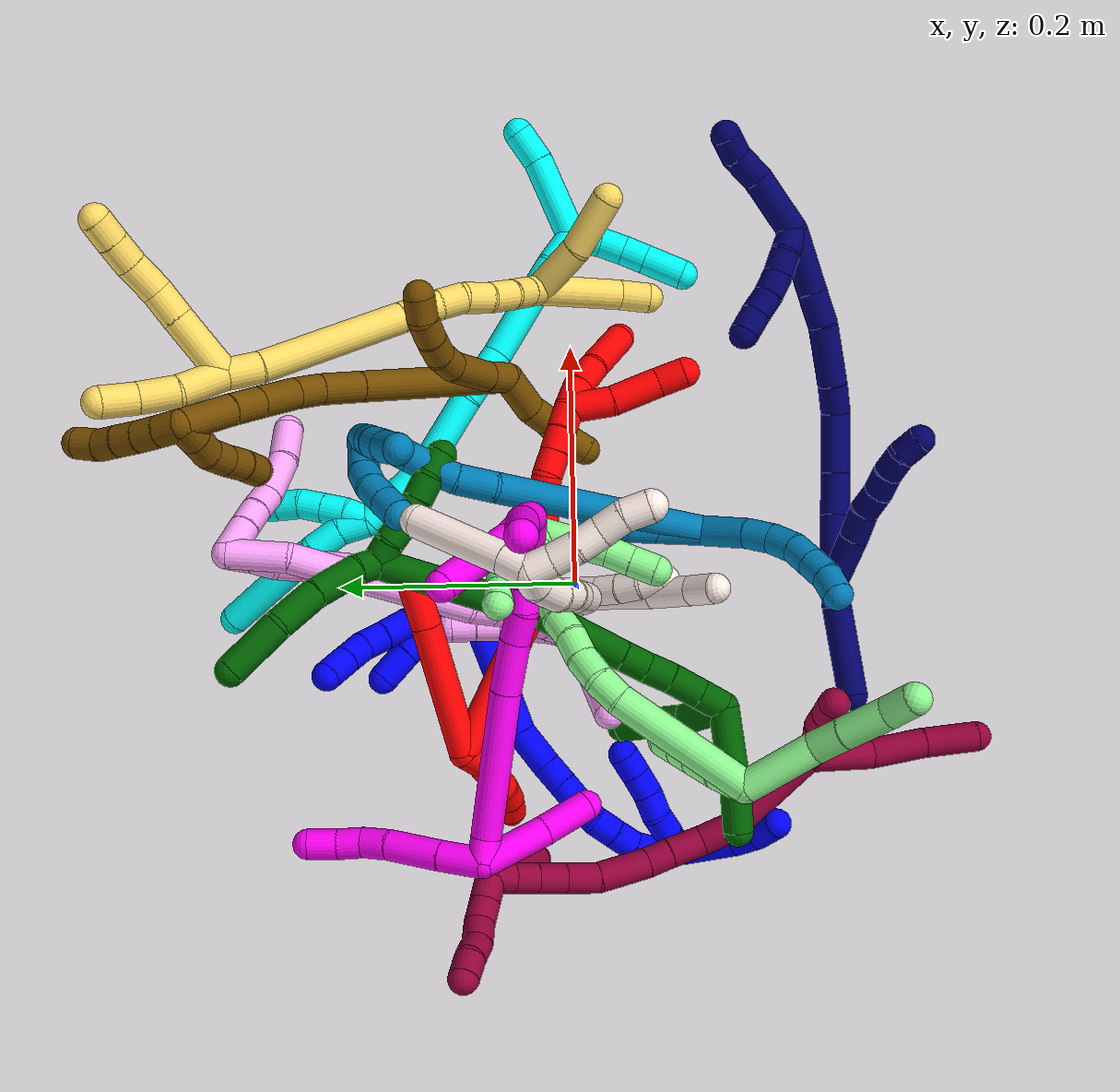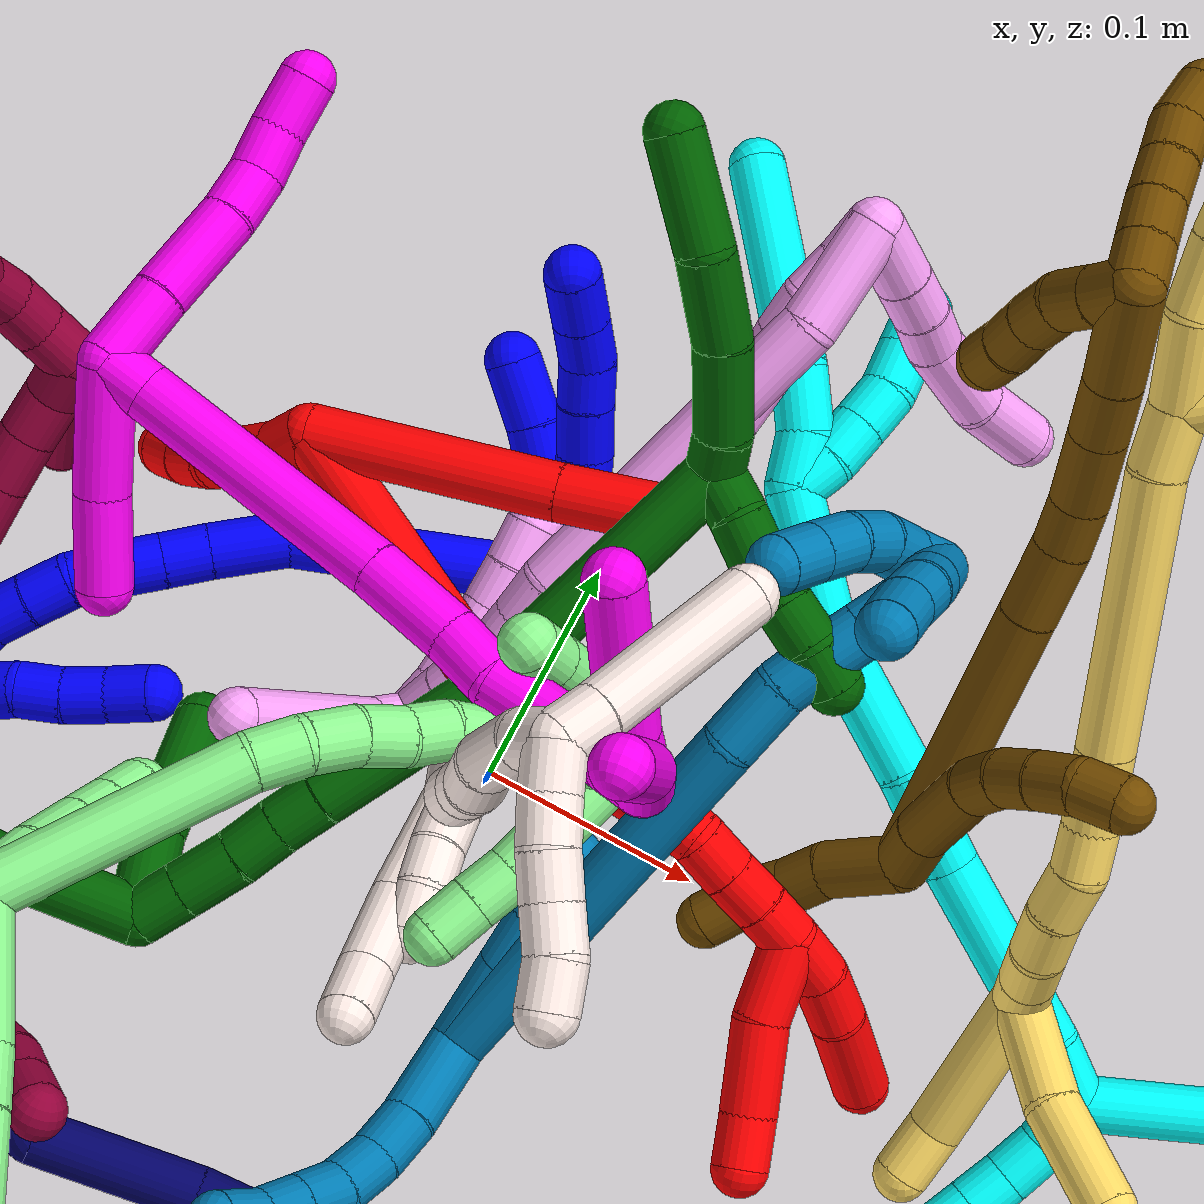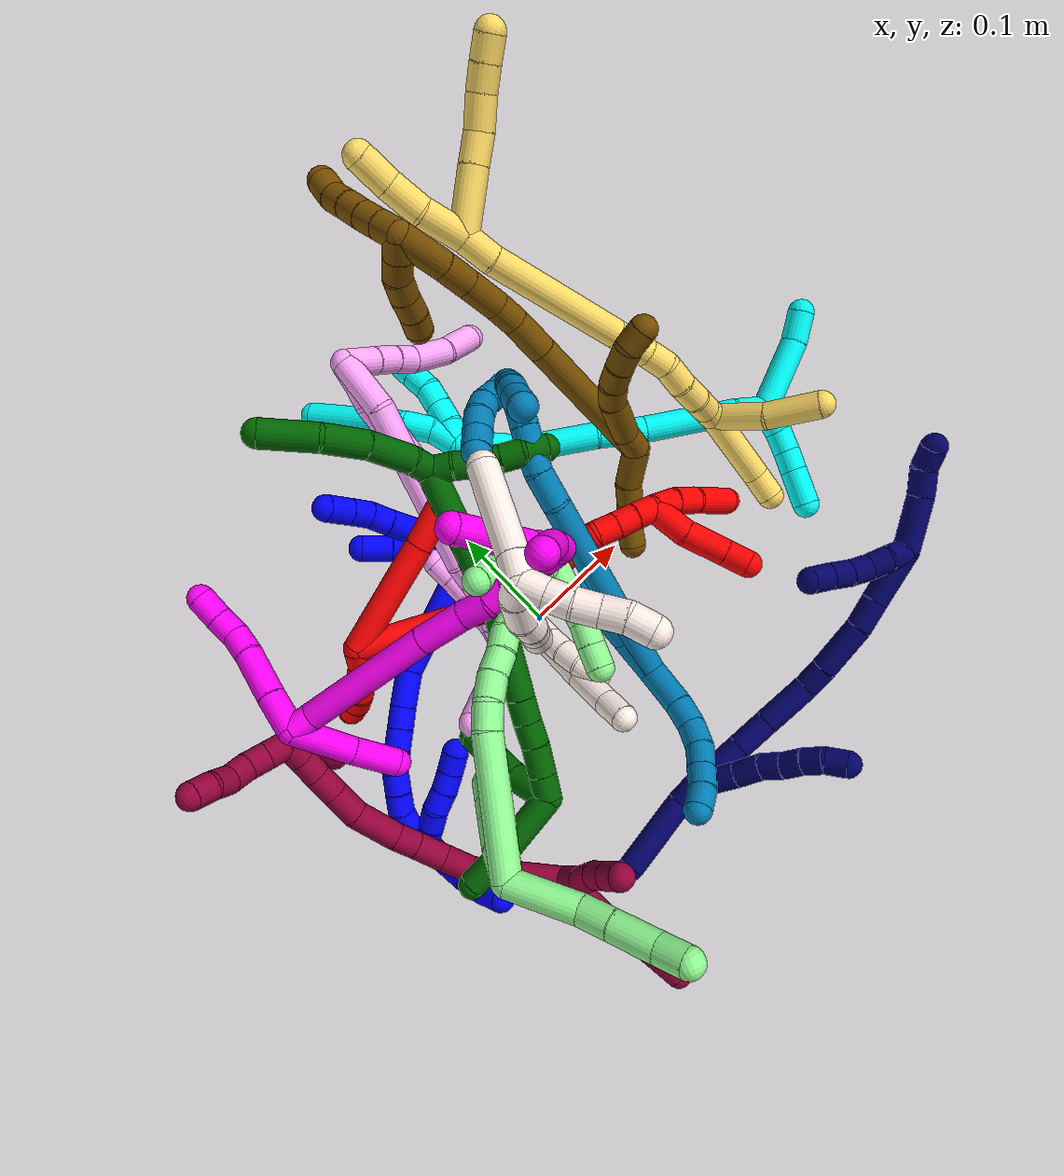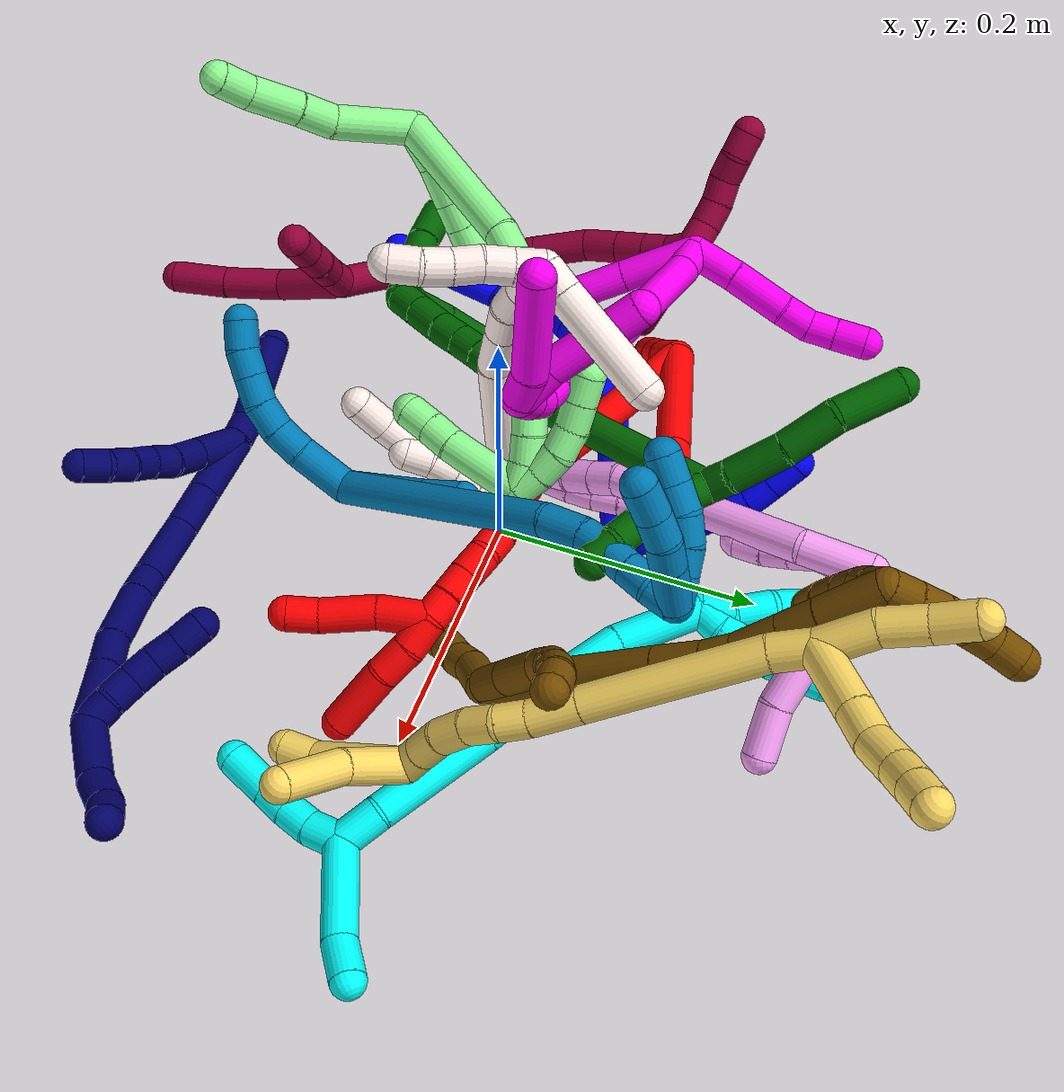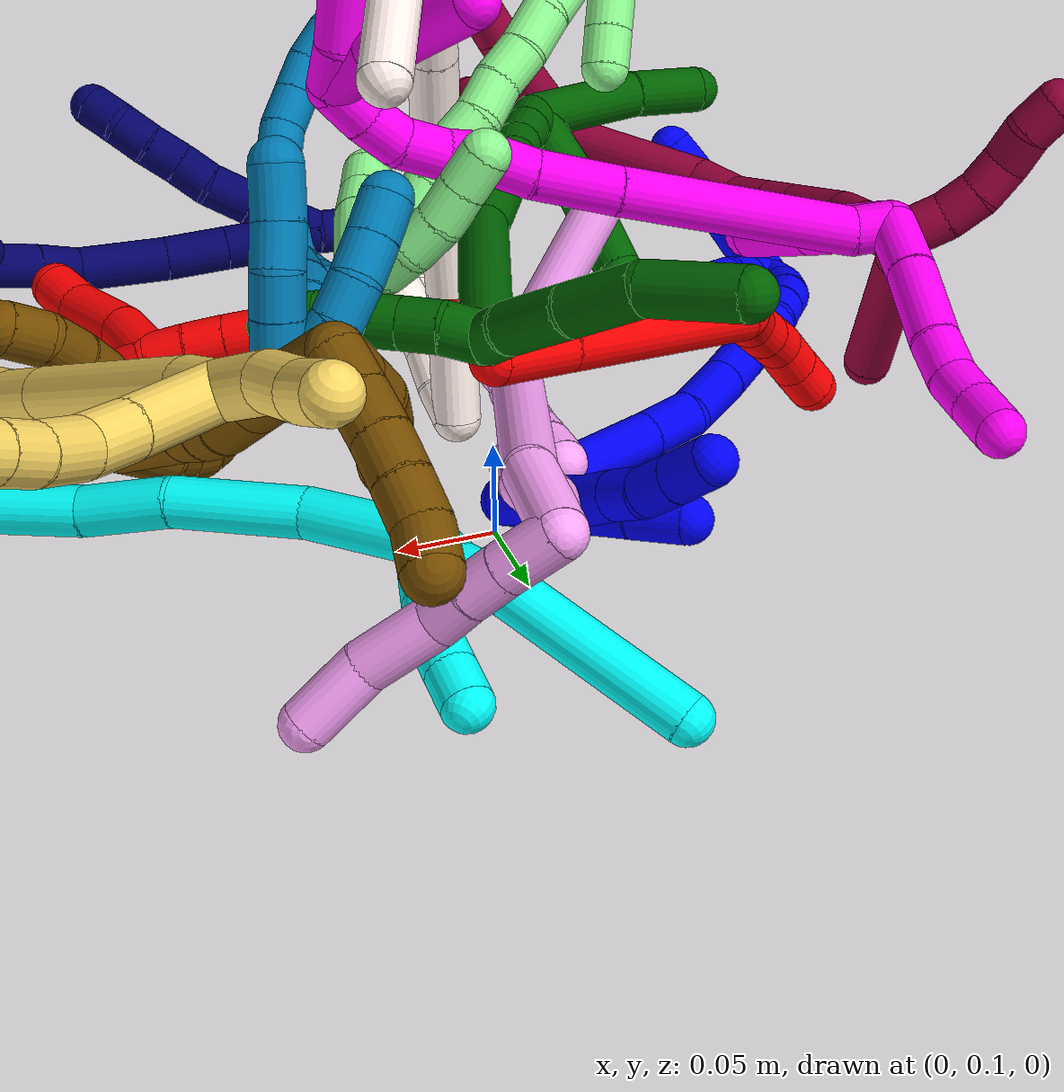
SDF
<sdf version="1.7">
 <world name="default">
  <plugin name="TubeGeneratorPlugin" filename="libtube_generator_plugin.so"/>
  <model name="photoneo_s_sensor">
   <static>1</static>
   <pose>0 0 2 1.57079 1.57079 3.14159</pose>
   <link name="link">
    <inertial><mass>0.1</mass></inertial>
    <sensor name="sensor" type="depth">
     <update_rate>30</update_rate>
     <camera>
      <horizontal_fov>1.22</horizontal_fov>
      <image><width>1920</width><height>1200</height><format>B8G8R8</format></image>
      <clip><near>0.1</near><far>4</far></clip>
      <depth_camera><output>points</output></depth_camera>
     </camera>
     <plugin name="camera_plugin" filename="libgazebo_ros_depth_camera.so">
      <baseline>0.2</baseline>
      <alwaysOn>1</alwaysOn>
      <updateRate>0.0</updateRate>
      <cameraName>camera_ir</cameraName>
      <imageTopicName>/camera/color/image_raw</imageTopicName>
      <cameraInfoTopicName>/camera/color/camera_info</cameraInfoTopicName>
      <depthImageTopicName>/camera/depth/image_raw</depthImageTopicName>
      <depthImageCameraInfoTopicName>/camera/depth/camera_info</depthImageCameraInfoTopicName>
      <pointCloudTopicName>/camera/depth/points</pointCloudTopicName>
      <frameName>fr_optical</frameName>
      <pointCloudCutoff>0.1</pointCloudCutoff>
      <pointCloudCutoffMax>2.0</pointCloudCutoffMax>
      <distortionK1>0</distortionK1>
      <distortionK2>0</distortionK2>
      <distortionK3>0</distortionK3>
      <distortionT1>0</distortionT1>
      <distortionT2>0</distortionT2>
      <CxPrime>0</CxPrime>
      <Cx>0</Cx>
      <Cy>0</Cy>
      <focalLength>0</focalLength>
      <hackBaseline>0</hackBaseline>
     </plugin>
    </sensor>
   </link>
  </model>
  <gravity>0 0 -9.8</gravity>
  <magnetic_field>6e-06 2.3e-05 -4.2e-05</magnetic_field>
  <atmosphere type="adiabatic"/>
  <physics name="default_physics" default="0" type="ode">
   <max_step_size>0.003</max_step_size>
   <real_time_factor>1</real_time_factor>
   <real_time_update_rate>1000</real_time_update_rate>
   <max_contacts>10000</max_contacts>
   <ode>
    <solver>
     <type>quick</type>
     <iters>100</iters>
     <sor>1.3</sor>
     <use_dynamic_moi_rescaling>0</use_dynamic_moi_rescaling>
    </solver>
    <constraints>
     <contact_max_correcting_vel>0</contact_max_correcting_vel>
     <contact_surface_layer>0.001</contact_surface_layer>
     <cfm>0</cfm>
     <erp>0.2</erp>
    </constraints>
   </ode>
  </physics>
  <scene><ambient>0.4 0.4 0.4 1</ambient><background>0.7 0.7 0.7 1</background><shadows>0</shadows></scene>
  <audio><device>default</device></audio>
  <spherical_coordinates>
   <surface_model>EARTH_WGS84</surface_model>
   <latitude_deg>0</latitude_deg>
   <longitude_deg>0</longitude_deg>
   <elevation>0</elevation>
   <heading_deg>0</heading_deg>
  </spherical_coordinates>
  <model name="bin">
   <static>1</static>
   <link name="bottom">
    <collision name="collision-bottom">
     <pose>0 0 -0.01 0 -0 0</pose>
     <geometry><box><size>0.8 0.6 0.02</size></box></geometry>
     <surface>
      <friction><ode><mu>100</mu><mu2>100</mu2></ode></friction>
      <contact><collide_bitmask>65535</collide_bitmask></contact>
     </surface>
    </collision>
   </link>
   <link name="west_wall">
    <collision name="collision-west_wall">
     <pose>-0.41 0 0.1 0 -0 0</pose>
     <geometry><box><size>0.02 0.6 0.2</size></box></geometry>
     <surface>
      <friction><ode><mu>100</mu><mu2>100</mu2></ode></friction>
      <contact><collide_bitmask>65535</collide_bitmask></contact>
     </surface>
    </collision>
   </link>
   <link name="east_wall">
    <collision name="collision-east_wall">
     <pose>0.41 0 0.1 0 -0 0</pose>
     <geometry><box><size>0.02 0.6 0.2</size></box></geometry>
     <surface>
      <friction><ode><mu>100</mu><mu2>100</mu2></ode></friction>
      <contact><collide_bitmask>65535</collide_bitmask></contact>
     </surface>
    </collision>
   </link>
   <link name="south_wall">
    <collision name="collision-south_wall">
     <pose>0 -0.31 0.1 0 -0 0</pose>
     <geometry><box><size>0.8 0.02 0.2</size></box></geometry>
     <surface>
      <friction><ode><mu>100</mu><mu2>100</mu2></ode></friction>
      <contact><collide_bitmask>65535</collide_bitmask></contact>
     </surface>
    </collision>
   </link>
   <link name="north_wall">
    <collision name="collision-north_wall">
     <pose>0 0.31 0.1 0 -0 0</pose>
     <geometry><box><size>0.8 0.02 0.2</size></box></geometry>
     <surface>
      <friction><ode><mu>100</mu><mu2>100</mu2></ode></friction>
      <contact><collide_bitmask>65535</collide_bitmask></contact>
     </surface>
    </collision>
   </link>
  </model>
  <model name="1">
   <static>0</static>
   <link name="1">
    <collision name="collision-cylinder-e_1_2_8">
     <pose>0.006324 -0.010296 0.007687 0.929464 0.457334 0.232319</pose>
     <geometry><cylinder><radius>0.0125</radius><length>0.028642</length></cylinder></geometry>
     <surface>
      <friction><ode><mu>1.16</mu><mu2>1.16</mu2><slip1>0</slip1><slip2>0</slip2></ode></friction>
      <contact><ode><kp>1e+06</kp><kd>1</kd><max_vel>0</max_vel><min_depth>0.001</min_depth></ode></contact>
     </surface>
    </collision>
    <visual name="visual-cylinder-e_1_2_8">
     <pose>0.006324 -0.010296 0.007687 0.929464 0.457334 0.232319</pose>
     <geometry><cylinder><radius>0.0125</radius><length>0.028642</length></cylinder></geometry>
     <material><ambient>0 0 1 1</ambient></material>
    </visual>
    <collision name="collision-cylinder-e_2_8_9">
     <pose>0.01892 -0.031805 0.025046 0.859056 0.400668 0.185487</pose>
     <geometry><cylinder><radius>0.0125</radius><length>0.032163</length></cylinder></geometry>
     <surface>
      <friction><ode><mu>1.16</mu><mu2>1.16</mu2><slip1>0</slip1><slip2>0</slip2></ode></friction>
      <contact><ode><kp>1e+06</kp><kd>1</kd><max_vel>0</max_vel><min_depth>0.001</min_depth></ode></contact>
     </surface>
    </collision>
    <visual name="visual-cylinder-e_2_8_9">
     <pose>0.01892 -0.031805 0.025046 0.859056 0.400668 0.185487</pose>
     <geometry><cylinder><radius>0.0125</radius><length>0.032163</length></cylinder></geometry>
     <material><ambient>0 0 1 1</ambient></material>
    </visual>
    <collision name="collision-cylinder-e_3_9_10">
     <pose>0.029499 -0.052679 0.040673 1.0184 0.362728 0.204054</pose>
     <geometry><cylinder><radius>0.0125</radius><length>0.024278</length></cylinder></geometry>
     <surface>
      <friction><ode><mu>1.16</mu><mu2>1.16</mu2><slip1>0</slip1><slip2>0</slip2></ode></friction>
      <contact><ode><kp>1e+06</kp><kd>1</kd><max_vel>0</max_vel><min_depth>0.001</min_depth></ode></contact>
     </surface>
    </collision>
    <visual name="visual-cylinder-e_3_9_10">
     <pose>0.029499 -0.052679 0.040673 1.0184 0.362728 0.204054</pose>
     <geometry><cylinder><radius>0.0125</radius><length>0.024278</length></cylinder></geometry>
     <material><ambient>0 0 1 1</ambient></material>
    </visual>
    <collision name="collision-cylinder-e_4_10_11">
     <pose>0.037602 -0.069927 0.052034 0.951741 0.386915 0.201249</pose>
     <geometry><cylinder><radius>0.0125</radius><length>0.020117</length></cylinder></geometry>
     <surface>
      <friction><ode><mu>1.16</mu><mu2>1.16</mu2><slip1>0</slip1><slip2>0</slip2></ode></friction>
      <contact><ode><kp>1e+06</kp><kd>1</kd><max_vel>0</max_vel><min_depth>0.001</min_depth></ode></contact>
     </surface>
    </collision>
    <visual name="visual-cylinder-e_4_10_11">
     <pose>0.037602 -0.069927 0.052034 0.951741 0.386915 0.201249</pose>
     <geometry><cylinder><radius>0.0125</radius><length>0.020117</length></cylinder></geometry>
     <material><ambient>0 0 1 1</ambient></material>
    </visual>
    <collision name="collision-cylinder-e_5_11_12">
     <pose>0.043876 -0.086942 0.061214 1.18991 0.239373 0.162417</pose>
     <geometry><cylinder><radius>0.0125</radius><length>0.020909</length></cylinder></geometry>
     <surface>
      <friction><ode><mu>1.16</mu><mu2>1.16</mu2><slip1>0</slip1><slip2>0</slip2></ode></friction>
      <contact><ode><kp>1e+06</kp><kd>1</kd><max_vel>0</max_vel><min_depth>0.001</min_depth></ode></contact>
     </surface>
    </collision>
    <visual name="visual-cylinder-e_5_11_12">
     <pose>0.043876 -0.086942 0.061214 1.18991 0.239373 0.162417</pose>
     <geometry><cylinder><radius>0.0125</radius><length>0.020909</length></cylinder></geometry>
     <material><ambient>0 0 1 1</ambient></material>
    </visual>
    <collision name="collision-cylinder-e_6_12_6">
     <pose>0.049162 -0.107298 0.068914 1.22608 0.237268 0.167304</pose>
     <geometry><cylinder><radius>0.0125</radius><length>0.023891</length></cylinder></geometry>
     <surface>
      <friction><ode><mu>1.16</mu><mu2>1.16</mu2><slip1>0</slip1><slip2>0</slip2></ode></friction>
      <contact><ode><kp>1e+06</kp><kd>1</kd><max_vel>0</max_vel><min_depth>0.001</min_depth></ode></contact>
     </surface>
    </collision>
    <visual name="visual-cylinder-e_6_12_6">
     <pose>0.049162 -0.107298 0.068914 1.22608 0.237268 0.167304</pose>
     <geometry><cylinder><radius>0.0125</radius><length>0.023891</length></cylinder></geometry>
     <material><ambient>0 0 1 1</ambient></material>
    </visual>
    <collision name="collision-cylinder-e_1_2_13">
     <pose>0.001615 -0.024244 0.025906 0.75226 0.045493 0.017969</pose>
     <geometry><cylinder><radius>0.0125</radius><length>0.071036</length></cylinder></geometry>
     <surface>
      <friction><ode><mu>1.16</mu><mu2>1.16</mu2><slip1>0</slip1><slip2>0</slip2></ode></friction>
      <contact><ode><kp>1e+06</kp><kd>1</kd><max_vel>0</max_vel><min_depth>0.001</min_depth></ode></contact>
     </surface>
    </collision>
    <visual name="visual-cylinder-e_1_2_13">
     <pose>0.001615 -0.024244 0.025906 0.75226 0.045493 0.017969</pose>
     <geometry><cylinder><radius>0.0125</radius><length>0.071036</length></cylinder></geometry>
     <material><ambient>0 0 1 1</ambient></material>
    </visual>
    <collision name="collision-cylinder-e_2_13_5">
     <pose>0.002311 -0.05822 0.062498 0.738795 -0.063538 -0.024607</pose>
     <geometry><cylinder><radius>0.0125</radius><length>0.028964</length></cylinder></geometry>
     <surface>
      <friction><ode><mu>1.16</mu><mu2>1.16</mu2><slip1>0</slip1><slip2>0</slip2></ode></friction>
      <contact><ode><kp>1e+06</kp><kd>1</kd><max_vel>0</max_vel><min_depth>0.001</min_depth></ode></contact>
     </surface>
    </collision>
    <visual name="visual-cylinder-e_2_13_5">
     <pose>0.002311 -0.05822 0.062498 0.738795 -0.063538 -0.024607</pose>
     <geometry><cylinder><radius>0.0125</radius><length>0.028964</length></cylinder></geometry>
     <material><ambient>0 0 1 1</ambient></material>
    </visual>
    <collision name="collision-cylinder-e_1_2_14">
     <pose>-0.041233 -0.022362 0.004856 1.35695 -1.06414 -0.88621</pose>
     <geometry><cylinder><radius>0.0125</radius><length>0.094314</length></cylinder></geometry>
     <surface>
      <friction><ode><mu>1.16</mu><mu2>1.16</mu2><slip1>0</slip1><slip2>0</slip2></ode></friction>
      <contact><ode><kp>1e+06</kp><kd>1</kd><max_vel>0</max_vel><min_depth>0.001</min_depth></ode></contact>
     </surface>
    </collision>
    <visual name="visual-cylinder-e_1_2_14">
     <pose>-0.041233 -0.022362 0.004856 1.35695 -1.06414 -0.88621</pose>
     <geometry><cylinder><radius>0.0125</radius><length>0.094314</length></cylinder></geometry>
     <material><ambient>0 0 1 1</ambient></material>
    </visual>
    <collision name="collision-cylinder-e_2_14_15">
     <pose>-0.094902 -0.052241 0.010937 1.40932 -1.0213 -0.889077</pose>
     <geometry><cylinder><radius>0.0125</radius><length>0.029167</length></cylinder></geometry>
     <surface>
      <friction><ode><mu>1.16</mu><mu2>1.16</mu2><slip1>0</slip1><slip2>0</slip2></ode></friction>
      <contact><ode><kp>1e+06</kp><kd>1</kd><max_vel>0</max_vel><min_depth>0.001</min_depth></ode></contact>
     </surface>
    </collision>
    <visual name="visual-cylinder-e_2_14_15">
     <pose>-0.094902 -0.052241 0.010937 1.40932 -1.0213 -0.889077</pose>
     <geometry><cylinder><radius>0.0125</radius><length>0.029167</length></cylinder></geometry>
     <material><ambient>0 0 1 1</ambient></material>
    </visual>
    <collision name="collision-cylinder-e_3_15_16">
     <pose>-0.123029 -0.06656 0.008817 2.02779 -1.12083 -1.57862</pose>
     <geometry><cylinder><radius>0.0125</radius><length>0.03485</length></cylinder></geometry>
     <surface>
      <friction><ode><mu>1.16</mu><mu2>1.16</mu2><slip1>0</slip1><slip2>0</slip2></ode></friction>
      <contact><ode><kp>1e+06</kp><kd>1</kd><max_vel>0</max_vel><min_depth>0.001</min_depth></ode></contact>
     </surface>
    </collision>
    <visual name="visual-cylinder-e_3_15_16">
     <pose>-0.123029 -0.06656 0.008817 2.02779 -1.12083 -1.57862</pose>
     <geometry><cylinder><radius>0.0125</radius><length>0.03485</length></cylinder></geometry>
     <material><ambient>0 0 1 1</ambient></material>
    </visual>
    <collision name="collision-cylinder-e_4_16_17">
     <pose>-0.148048 -0.077518 0.002904 2.12435 -1.08823 -1.65244</pose>
     <geometry><cylinder><radius>0.0125</radius><length>0.021062</length></cylinder></geometry>
     <surface>
      <friction><ode><mu>1.16</mu><mu2>1.16</mu2><slip1>0</slip1><slip2>0</slip2></ode></friction>
      <contact><ode><kp>1e+06</kp><kd>1</kd><max_vel>0</max_vel><min_depth>0.001</min_depth></ode></contact>
     </surface>
    </collision>
    <visual name="visual-cylinder-e_4_16_17">
     <pose>-0.148048 -0.077518 0.002904 2.12435 -1.08823 -1.65244</pose>
     <geometry><cylinder><radius>0.0125</radius><length>0.021062</length></cylinder></geometry>
     <material><ambient>0 0 1 1</ambient></material>
    </visual>
    <collision name="collision-cylinder-e_5_17_18">
     <pose>-0.166395 -0.085851 -0.002136 2.10508 -1.07724 -1.61755</pose>
     <geometry><cylinder><radius>0.0125</radius><length>0.020482</length></cylinder></geometry>
     <surface>
      <friction><ode><mu>1.16</mu><mu2>1.16</mu2><slip1>0</slip1><slip2>0</slip2></ode></friction>
      <contact><ode><kp>1e+06</kp><kd>1</kd><max_vel>0</max_vel><min_depth>0.001</min_depth></ode></contact>
     </surface>
    </collision>
    <visual name="visual-cylinder-e_5_17_18">
     <pose>-0.166395 -0.085851 -0.002136 2.10508 -1.07724 -1.61755</pose>
     <geometry><cylinder><radius>0.0125</radius><length>0.020482</length></cylinder></geometry>
     <material><ambient>0 0 1 1</ambient></material>
    </visual>
    <collision name="collision-cylinder-e_6_18_19">
     <pose>-0.184355 -0.09371 -0.007354 2.21157 -1.09602 -1.76561</pose>
     <geometry><cylinder><radius>0.0125</radius><length>0.020107</length></cylinder></geometry>
     <surface>
      <friction><ode><mu>1.16</mu><mu2>1.16</mu2><slip1>0</slip1><slip2>0</slip2></ode></friction>
      <contact><ode><kp>1e+06</kp><kd>1</kd><max_vel>0</max_vel><min_depth>0.001</min_depth></ode></contact>
     </surface>
    </collision>
    <visual name="visual-cylinder-e_6_18_19">
     <pose>-0.184355 -0.09371 -0.007354 2.21157 -1.09602 -1.76561</pose>
     <geometry><cylinder><radius>0.0125</radius><length>0.020107</length></cylinder></geometry>
     <material><ambient>0 0 1 1</ambient></material>
    </visual>
    <collision name="collision-cylinder-e_7_19_20">
     <pose>-0.202646 -0.098268 -0.013559 2.894 -1.20641 -2.78418</pose>
     <geometry><cylinder><radius>0.0125</radius><length>0.020014</length></cylinder></geometry>
     <surface>
      <friction><ode><mu>1.16</mu><mu2>1.16</mu2><slip1>0</slip1><slip2>0</slip2></ode></friction>
      <contact><ode><kp>1e+06</kp><kd>1</kd><max_vel>0</max_vel><min_depth>0.001</min_depth></ode></contact>
     </surface>
    </collision>
    <visual name="visual-cylinder-e_7_19_20">
     <pose>-0.202646 -0.098268 -0.013559 2.894 -1.20641 -2.78418</pose>
     <geometry><cylinder><radius>0.0125</radius><length>0.020014</length></cylinder></geometry>
     <material><ambient>0 0 1 1</ambient></material>
    </visual>
    <collision name="collision-cylinder-e_8_20_21">
     <pose>-0.221519 -0.099381 -0.020061 3.0634 -1.26046 -3.03446</pose>
     <geometry><cylinder><radius>0.0125</radius><length>0.02</length></cylinder></geometry>
     <surface>
      <friction><ode><mu>1.16</mu><mu2>1.16</mu2><slip1>0</slip1><slip2>0</slip2></ode></friction>
      <contact><ode><kp>1e+06</kp><kd>1</kd><max_vel>0</max_vel><min_depth>0.001</min_depth></ode></contact>
     </surface>
    </collision>
    <visual name="visual-cylinder-e_8_20_21">
     <pose>-0.221519 -0.099381 -0.020061 3.0634 -1.26046 -3.03446</pose>
     <geometry><cylinder><radius>0.0125</radius><length>0.02</length></cylinder></geometry>
     <material><ambient>0 0 1 1</ambient></material>
    </visual>
    <collision name="collision-cylinder-e_9_21_22">
     <pose>-0.239585 -0.097289 -0.027752 -2.67677 -1.02422 2.34454</pose>
     <geometry><cylinder><radius>0.0125</radius><length>0.020002</length></cylinder></geometry>
     <surface>
      <friction><ode><mu>1.16</mu><mu2>1.16</mu2><slip1>0</slip1><slip2>0</slip2></ode></friction>
      <contact><ode><kp>1e+06</kp><kd>1</kd><max_vel>0</max_vel><min_depth>0.001</min_depth></ode></contact>
     </surface>
    </collision>
    <visual name="visual-cylinder-e_9_21_22">
     <pose>-0.239585 -0.097289 -0.027752 -2.67677 -1.02422 2.34454</pose>
     <geometry><cylinder><radius>0.0125</radius><length>0.020002</length></cylinder></geometry>
     <material><ambient>0 0 1 1</ambient></material>
    </visual>
    <collision name="collision-cylinder-e_10_22_1">
     <pose>-0.254886 -0.091223 -0.038755 -2.61025 -0.741884 1.92069</pose>
     <geometry><cylinder><radius>0.0125</radius><length>0.020003</length></cylinder></geometry>
     <surface>
      <friction><ode><mu>1.16</mu><mu2>1.16</mu2><slip1>0</slip1><slip2>0</slip2></ode></friction>
      <contact><ode><kp>1e+06</kp><kd>1</kd><max_vel>0</max_vel><min_depth>0.001</min_depth></ode></contact>
     </surface>
    </collision>
    <visual name="visual-cylinder-e_10_22_1">
     <pose>-0.254886 -0.091223 -0.038755 -2.61025 -0.741884 1.92069</pose>
     <geometry><cylinder><radius>0.0125</radius><length>0.020003</length></cylinder></geometry>
     <material><ambient>0 0 1 1</ambient></material>
    </visual>
    <collision name="collision-cylinder-e_1_1_23">
     <pose>-0.267638 -0.088844 -0.071177 3.08957 -0.225732 -2.69038</pose>
     <geometry><cylinder><radius>0.0125</radius><length>0.05356</length></cylinder></geometry>
     <surface>
      <friction><ode><mu>1.16</mu><mu2>1.16</mu2><slip1>0</slip1><slip2>0</slip2></ode></friction>
      <contact><ode><kp>1e+06</kp><kd>1</kd><max_vel>0</max_vel><min_depth>0.001</min_depth></ode></contact>
     </surface>
    </collision>
    <visual name="visual-cylinder-e_1_1_23">
     <pose>-0.267638 -0.088844 -0.071177 3.08957 -0.225732 -2.69038</pose>
     <geometry><cylinder><radius>0.0125</radius><length>0.05356</length></cylinder></geometry>
     <material><ambient>0 0 1 1</ambient></material>
    </visual>
    <collision name="collision-cylinder-e_2_23_24">
     <pose>-0.274195 -0.091274 -0.108071 3.04282 -0.051679 -0.963605</pose>
     <geometry><cylinder><radius>0.0125</radius><length>0.021794</length></cylinder></geometry>
     <surface>
      <friction><ode><mu>1.16</mu><mu2>1.16</mu2><slip1>0</slip1><slip2>0</slip2></ode></friction>
      <contact><ode><kp>1e+06</kp><kd>1</kd><max_vel>0</max_vel><min_depth>0.001</min_depth></ode></contact>
     </surface>
    </collision>
    <visual name="visual-cylinder-e_2_23_24">
     <pose>-0.274195 -0.091274 -0.108071 3.04282 -0.051679 -0.963605</pose>
     <geometry><cylinder><radius>0.0125</radius><length>0.021794</length></cylinder></geometry>
     <material><ambient>0 0 1 1</ambient></material>
    </visual>
    <collision name="collision-cylinder-e_3_24_4">
     <pose>-0.272412 -0.093971 -0.130889 3.00704 0.191566 1.91839</pose>
     <geometry><cylinder><radius>0.0125</radius><length>0.024646</length></cylinder></geometry>
     <surface>
      <friction><ode><mu>1.16</mu><mu2>1.16</mu2><slip1>0</slip1><slip2>0</slip2></ode></friction>
      <contact><ode><kp>1e+06</kp><kd>1</kd><max_vel>0</max_vel><min_depth>0.001</min_depth></ode></contact>
     </surface>
    </collision>
    <visual name="visual-cylinder-e_3_24_4">
     <pose>-0.272412 -0.093971 -0.130889 3.00704 0.191566 1.91839</pose>
     <geometry><cylinder><radius>0.0125</radius><length>0.024646</length></cylinder></geometry>
     <material><ambient>0 0 1 1</ambient></material>
    </visual>
    <collision name="collision-cylinder-e_1_1_25">
     <pose>-0.251868 -0.086678 -0.047054 -2.74661 1.35879 -2.65587</pose>
     <geometry><cylinder><radius>0.0125</radius><length>0.02</length></cylinder></geometry>
     <surface>
      <friction><ode><mu>1.16</mu><mu2>1.16</mu2><slip1>0</slip1><slip2>0</slip2></ode></friction>
      <contact><ode><kp>1e+06</kp><kd>1</kd><max_vel>0</max_vel><min_depth>0.001</min_depth></ode></contact>
     </surface>
    </collision>
    <visual name="visual-cylinder-e_1_1_25">
     <pose>-0.251868 -0.086678 -0.047054 -2.74661 1.35879 -2.65587</pose>
     <geometry><cylinder><radius>0.0125</radius><length>0.02</length></cylinder></geometry>
     <material><ambient>0 0 1 1</ambient></material>
    </visual>
    <collision name="collision-cylinder-e_2_25_26">
     <pose>-0.232191 -0.085245 -0.050251 -2.68117 1.43023 -2.61442</pose>
     <geometry><cylinder><radius>0.0125</radius><length>0.02</length></cylinder></geometry>
     <surface>
      <friction><ode><mu>1.16</mu><mu2>1.16</mu2><slip1>0</slip1><slip2>0</slip2></ode></friction>
      <contact><ode><kp>1e+06</kp><kd>1</kd><max_vel>0</max_vel><min_depth>0.001</min_depth></ode></contact>
     </surface>
    </collision>
    <visual name="visual-cylinder-e_2_25_26">
     <pose>-0.232191 -0.085245 -0.050251 -2.68117 1.43023 -2.61442</pose>
     <geometry><cylinder><radius>0.0125</radius><length>0.02</length></cylinder></geometry>
     <material><ambient>0 0 1 1</ambient></material>
    </visual>
    <collision name="collision-cylinder-e_3_26_27">
     <pose>-0.213159 -0.0808 -0.052926 -1.92635 1.15075 -1.50117</pose>
     <geometry><cylinder><radius>0.0125</radius><length>0.02</length></cylinder></geometry>
     <surface>
      <friction><ode><mu>1.16</mu><mu2>1.16</mu2><slip1>0</slip1><slip2>0</slip2></ode></friction>
      <contact><ode><kp>1e+06</kp><kd>1</kd><max_vel>0</max_vel><min_depth>0.001</min_depth></ode></contact>
     </surface>
    </collision>
    <visual name="visual-cylinder-e_3_26_27">
     <pose>-0.213159 -0.0808 -0.052926 -1.92635 1.15075 -1.50117</pose>
     <geometry><cylinder><radius>0.0125</radius><length>0.02</length></cylinder></geometry>
     <material><ambient>0 0 1 1</ambient></material>
    </visual>
    <collision name="collision-cylinder-e_4_27_28">
     <pose>-0.194576 -0.073713 -0.054438 -1.59928 1.23815 -1.2652</pose>
     <geometry><cylinder><radius>0.0125</radius><length>0.02</length></cylinder></geometry>
     <surface>
      <friction><ode><mu>1.16</mu><mu2>1.16</mu2><slip1>0</slip1><slip2>0</slip2></ode></friction>
      <contact><ode><kp>1e+06</kp><kd>1</kd><max_vel>0</max_vel><min_depth>0.001</min_depth></ode></contact>
     </surface>
    </collision>
    <visual name="visual-cylinder-e_4_27_28">
     <pose>-0.194576 -0.073713 -0.054438 -1.59928 1.23815 -1.2652</pose>
     <geometry><cylinder><radius>0.0125</radius><length>0.02</length></cylinder></geometry>
     <material><ambient>0 0 1 1</ambient></material>
    </visual>
    <collision name="collision-cylinder-e_5_28_3">
     <pose>-0.175322 -0.068559 -0.055116 -1.87062 1.37171 -1.67462</pose>
     <geometry><cylinder><radius>0.0125</radius><length>0.02</length></cylinder></geometry>
     <surface>
      <friction><ode><mu>1.16</mu><mu2>1.16</mu2><slip1>0</slip1><slip2>0</slip2></ode></friction>
      <contact><ode><kp>1e+06</kp><kd>1</kd><max_vel>0</max_vel><min_depth>0.001</min_depth></ode></contact>
     </surface>
    </collision>
    <visual name="visual-cylinder-e_5_28_3">
     <pose>-0.175322 -0.068559 -0.055116 -1.87062 1.37171 -1.67462</pose>
     <geometry><cylinder><radius>0.0125</radius><length>0.02</length></cylinder></geometry>
     <material><ambient>0 0 1 1</ambient></material>
    </visual>
    <collision name="collision-sphere-3">
     <pose>-0.165519 -0.066669 -0.0557 0 -0 0</pose>
     <geometry><sphere><radius>0.0125</radius></sphere></geometry>
     <surface>
      <friction><ode><mu>1.16</mu><mu2>1.16</mu2><slip1>0</slip1><slip2>0</slip2></ode></friction>
      <contact><ode><kp>1e+06</kp><kd>1</kd><max_vel>0</max_vel><min_depth>0.001</min_depth></ode></contact>
     </surface>
    </collision>
    <visual name="visual-sphere-3">
     <pose>-0.165519 -0.066669 -0.0557 0 -0 0</pose>
     <geometry><sphere><radius>0.0125</radius></sphere></geometry>
     <material><ambient>0 0 1 1</ambient></material>
    </visual>
    <collision name="collision-sphere-28">
     <pose>-0.185124 -0.070448 -0.054531 0 -0 0</pose>
     <geometry><sphere><radius>0.0125</radius></sphere></geometry>
     <surface>
      <friction><ode><mu>1.16</mu><mu2>1.16</mu2><slip1>0</slip1><slip2>0</slip2></ode></friction>
      <contact><ode><kp>1e+06</kp><kd>1</kd><max_vel>0</max_vel><min_depth>0.001</min_depth></ode></contact>
     </surface>
    </collision>
    <visual name="visual-sphere-28">
     <pose>-0.185124 -0.070448 -0.054531 0 -0 0</pose>
     <geometry><sphere><radius>0.0125</radius></sphere></geometry>
     <material><ambient>0 0 1 1</ambient></material>
    </visual>
    <collision name="collision-sphere-27">
     <pose>-0.204028 -0.076977 -0.054345 0 -0 0</pose>
     <geometry><sphere><radius>0.0125</radius></sphere></geometry>
     <surface>
      <friction><ode><mu>1.16</mu><mu2>1.16</mu2><slip1>0</slip1><slip2>0</slip2></ode></friction>
      <contact><ode><kp>1e+06</kp><kd>1</kd><max_vel>0</max_vel><min_depth>0.001</min_depth></ode></contact>
     </surface>
    </collision>
    <visual name="visual-sphere-27">
     <pose>-0.204028 -0.076977 -0.054345 0 -0 0</pose>
     <geometry><sphere><radius>0.0125</radius></sphere></geometry>
     <material><ambient>0 0 1 1</ambient></material>
    </visual>
    <collision name="collision-sphere-26">
     <pose>-0.222289 -0.084623 -0.051506 0 -0 0</pose>
     <geometry><sphere><radius>0.0125</radius></sphere></geometry>
     <surface>
      <friction><ode><mu>1.16</mu><mu2>1.16</mu2><slip1>0</slip1><slip2>0</slip2></ode></friction>
      <contact><ode><kp>1e+06</kp><kd>1</kd><max_vel>0</max_vel><min_depth>0.001</min_depth></ode></contact>
     </surface>
    </collision>
    <visual name="visual-sphere-26">
     <pose>-0.222289 -0.084623 -0.051506 0 -0 0</pose>
     <geometry><sphere><radius>0.0125</radius></sphere></geometry>
     <material><ambient>0 0 1 1</ambient></material>
    </visual>
    <collision name="collision-sphere-25">
     <pose>-0.242092 -0.085868 -0.048996 0 -0 0</pose>
     <geometry><sphere><radius>0.0125</radius></sphere></geometry>
     <surface>
      <friction><ode><mu>1.16</mu><mu2>1.16</mu2><slip1>0</slip1><slip2>0</slip2></ode></friction>
      <contact><ode><kp>1e+06</kp><kd>1</kd><max_vel>0</max_vel><min_depth>0.001</min_depth></ode></contact>
     </surface>
    </collision>
    <visual name="visual-sphere-25">
     <pose>-0.242092 -0.085868 -0.048996 0 -0 0</pose>
     <geometry><sphere><radius>0.0125</radius></sphere></geometry>
     <material><ambient>0 0 1 1</ambient></material>
    </visual>
    <collision name="collision-sphere-4">
     <pose>-0.270065 -0.095593 -0.142877 0 -0 0</pose>
     <geometry><sphere><radius>0.0125</radius></sphere></geometry>
     <surface>
      <friction><ode><mu>1.16</mu><mu2>1.16</mu2><slip1>0</slip1><slip2>0</slip2></ode></friction>
      <contact><ode><kp>1e+06</kp><kd>1</kd><max_vel>0</max_vel><min_depth>0.001</min_depth></ode></contact>
     </surface>
    </collision>
    <visual name="visual-sphere-4">
     <pose>-0.270065 -0.095593 -0.142877 0 -0 0</pose>
     <geometry><sphere><radius>0.0125</radius></sphere></geometry>
     <material><ambient>0 0 1 1</ambient></material>
    </visual>
    <collision name="collision-sphere-24">
     <pose>-0.274758 -0.092348 -0.118901 0 -0 0</pose>
     <geometry><sphere><radius>0.0125</radius></sphere></geometry>
     <surface>
      <friction><ode><mu>1.16</mu><mu2>1.16</mu2><slip1>0</slip1><slip2>0</slip2></ode></friction>
      <contact><ode><kp>1e+06</kp><kd>1</kd><max_vel>0</max_vel><min_depth>0.001</min_depth></ode></contact>
     </surface>
    </collision>
    <visual name="visual-sphere-24">
     <pose>-0.274758 -0.092348 -0.118901 0 -0 0</pose>
     <geometry><sphere><radius>0.0125</radius></sphere></geometry>
     <material><ambient>0 0 1 1</ambient></material>
    </visual>
    <collision name="collision-sphere-23">
     <pose>-0.273632 -0.090201 -0.097242 0 -0 0</pose>
     <geometry><sphere><radius>0.0125</radius></sphere></geometry>
     <surface>
      <friction><ode><mu>1.16</mu><mu2>1.16</mu2><slip1>0</slip1><slip2>0</slip2></ode></friction>
      <contact><ode><kp>1e+06</kp><kd>1</kd><max_vel>0</max_vel><min_depth>0.001</min_depth></ode></contact>
     </surface>
    </collision>
    <visual name="visual-sphere-23">
     <pose>-0.273632 -0.090201 -0.097242 0 -0 0</pose>
     <geometry><sphere><radius>0.0125</radius></sphere></geometry>
     <material><ambient>0 0 1 1</ambient></material>
    </visual>
    <collision name="collision-sphere-1">
     <pose>-0.261644 -0.087487 -0.045111 0 -0 0</pose>
     <geometry><sphere><radius>0.0125</radius></sphere></geometry>
     <surface>
      <friction><ode><mu>1.16</mu><mu2>1.16</mu2><slip1>0</slip1><slip2>0</slip2></ode></friction>
      <contact><ode><kp>1e+06</kp><kd>1</kd><max_vel>0</max_vel><min_depth>0.001</min_depth></ode></contact>
     </surface>
    </collision>
    <visual name="visual-sphere-1">
     <pose>-0.261644 -0.087487 -0.045111 0 -0 0</pose>
     <geometry><sphere><radius>0.0125</radius></sphere></geometry>
     <material><ambient>0 0 1 1</ambient></material>
    </visual>
    <collision name="collision-sphere-22">
     <pose>-0.248129 -0.094959 -0.032398 0 -0 0</pose>
     <geometry><sphere><radius>0.0125</radius></sphere></geometry>
     <surface>
      <friction><ode><mu>1.16</mu><mu2>1.16</mu2><slip1>0</slip1><slip2>0</slip2></ode></friction>
      <contact><ode><kp>1e+06</kp><kd>1</kd><max_vel>0</max_vel><min_depth>0.001</min_depth></ode></contact>
     </surface>
    </collision>
    <visual name="visual-sphere-22">
     <pose>-0.248129 -0.094959 -0.032398 0 -0 0</pose>
     <geometry><sphere><radius>0.0125</radius></sphere></geometry>
     <material><ambient>0 0 1 1</ambient></material>
    </visual>
    <collision name="collision-sphere-21">
     <pose>-0.231041 -0.099619 -0.023105 0 -0 0</pose>
     <geometry><sphere><radius>0.0125</radius></sphere></geometry>
     <surface>
      <friction><ode><mu>1.16</mu><mu2>1.16</mu2><slip1>0</slip1><slip2>0</slip2></ode></friction>
      <contact><ode><kp>1e+06</kp><kd>1</kd><max_vel>0</max_vel><min_depth>0.001</min_depth></ode></contact>
     </surface>
    </collision>
    <visual name="visual-sphere-21">
     <pose>-0.231041 -0.099619 -0.023105 0 -0 0</pose>
     <geometry><sphere><radius>0.0125</radius></sphere></geometry>
     <material><ambient>0 0 1 1</ambient></material>
    </visual>
    <collision name="collision-sphere-12">
     <pose>0.046354 -0.09637 0.06499 0 -0 0</pose>
     <geometry><sphere><radius>0.0125</radius></sphere></geometry>
     <surface>
      <friction><ode><mu>1.16</mu><mu2>1.16</mu2><slip1>0</slip1><slip2>0</slip2></ode></friction>
      <contact><ode><kp>1e+06</kp><kd>1</kd><max_vel>0</max_vel><min_depth>0.001</min_depth></ode></contact>
     </surface>
    </collision>
    <visual name="visual-sphere-12">
     <pose>0.046354 -0.09637 0.06499 0 -0 0</pose>
     <geometry><sphere><radius>0.0125</radius></sphere></geometry>
     <material><ambient>0 0 1 1</ambient></material>
    </visual>
    <collision name="collision-sphere-11">
     <pose>0.041397 -0.077513 0.057439 0 -0 0</pose>
     <geometry><sphere><radius>0.0125</radius></sphere></geometry>
     <surface>
      <friction><ode><mu>1.16</mu><mu2>1.16</mu2><slip1>0</slip1><slip2>0</slip2></ode></friction>
      <contact><ode><kp>1e+06</kp><kd>1</kd><max_vel>0</max_vel><min_depth>0.001</min_depth></ode></contact>
     </surface>
    </collision>
    <visual name="visual-sphere-11">
     <pose>0.041397 -0.077513 0.057439 0 -0 0</pose>
     <geometry><sphere><radius>0.0125</radius></sphere></geometry>
     <material><ambient>0 0 1 1</ambient></material>
    </visual>
    <collision name="collision-sphere-10">
     <pose>0.033806 -0.062341 0.046629 0 -0 0</pose>
     <geometry><sphere><radius>0.0125</radius></sphere></geometry>
     <surface>
      <friction><ode><mu>1.16</mu><mu2>1.16</mu2><slip1>0</slip1><slip2>0</slip2></ode></friction>
      <contact><ode><kp>1e+06</kp><kd>1</kd><max_vel>0</max_vel><min_depth>0.001</min_depth></ode></contact>
     </surface>
    </collision>
    <visual name="visual-sphere-10">
     <pose>0.033806 -0.062341 0.046629 0 -0 0</pose>
     <geometry><sphere><radius>0.0125</radius></sphere></geometry>
     <material><ambient>0 0 1 1</ambient></material>
    </visual>
    <collision name="collision-sphere-9">
     <pose>0.025192 -0.043018 0.034718 0 -0 0</pose>
     <geometry><sphere><radius>0.0125</radius></sphere></geometry>
     <surface>
      <friction><ode><mu>1.16</mu><mu2>1.16</mu2><slip1>0</slip1><slip2>0</slip2></ode></friction>
      <contact><ode><kp>1e+06</kp><kd>1</kd><max_vel>0</max_vel><min_depth>0.001</min_depth></ode></contact>
     </surface>
    </collision>
    <visual name="visual-sphere-9">
     <pose>0.025192 -0.043018 0.034718 0 -0 0</pose>
     <geometry><sphere><radius>0.0125</radius></sphere></geometry>
     <material><ambient>0 0 1 1</ambient></material>
    </visual>
    <collision name="collision-sphere-2">
     <geometry><sphere><radius>0.0125</radius></sphere></geometry>
     <surface>
      <friction><ode><mu>1.16</mu><mu2>1.16</mu2><slip1>0</slip1><slip2>0</slip2></ode></friction>
      <contact><ode><kp>1e+06</kp><kd>1</kd><max_vel>0</max_vel><min_depth>0.001</min_depth></ode></contact>
     </surface>
    </collision>
    <visual name="visual-sphere-2">
     <geometry><sphere><radius>0.0125</radius></sphere></geometry>
     <material><ambient>0 0 1 1</ambient></material>
    </visual>
    <collision name="collision-sphere-19">
     <pose>-0.193297 -0.097394 -0.010101 0 -0 0</pose>
     <geometry><sphere><radius>0.0125</radius></sphere></geometry>
     <surface>
      <friction><ode><mu>1.16</mu><mu2>1.16</mu2><slip1>0</slip1><slip2>0</slip2></ode></friction>
      <contact><ode><kp>1e+06</kp><kd>1</kd><max_vel>0</max_vel><min_depth>0.001</min_depth></ode></contact>
     </surface>
    </collision>
    <visual name="visual-sphere-19">
     <pose>-0.193297 -0.097394 -0.010101 0 -0 0</pose>
     <geometry><sphere><radius>0.0125</radius></sphere></geometry>
     <material><ambient>0 0 1 1</ambient></material>
    </visual>
    <collision name="collision-sphere-8">
     <pose>0.012647 -0.020592 0.015375 0 -0 0</pose>
     <geometry><sphere><radius>0.0125</radius></sphere></geometry>
     <surface>
      <friction><ode><mu>1.16</mu><mu2>1.16</mu2><slip1>0</slip1><slip2>0</slip2></ode></friction>
      <contact><ode><kp>1e+06</kp><kd>1</kd><max_vel>0</max_vel><min_depth>0.001</min_depth></ode></contact>
     </surface>
    </collision>
    <visual name="visual-sphere-8">
     <pose>0.012647 -0.020592 0.015375 0 -0 0</pose>
     <geometry><sphere><radius>0.0125</radius></sphere></geometry>
     <material><ambient>0 0 1 1</ambient></material>
    </visual>
    <collision name="collision-sphere-6">
     <pose>0.05197 -0.118226 0.072837 0 -0 0</pose>
     <geometry><sphere><radius>0.0125</radius></sphere></geometry>
     <surface>
      <friction><ode><mu>1.16</mu><mu2>1.16</mu2><slip1>0</slip1><slip2>0</slip2></ode></friction>
      <contact><ode><kp>1e+06</kp><kd>1</kd><max_vel>0</max_vel><min_depth>0.001</min_depth></ode></contact>
     </surface>
    </collision>
    <visual name="visual-sphere-6">
     <pose>0.05197 -0.118226 0.072837 0 -0 0</pose>
     <geometry><sphere><radius>0.0125</radius></sphere></geometry>
     <material><ambient>0 0 1 1</ambient></material>
    </visual>
    <collision name="collision-sphere-13">
     <pose>0.003231 -0.048488 0.051813 0 -0 0</pose>
     <geometry><sphere><radius>0.0125</radius></sphere></geometry>
     <surface>
      <friction><ode><mu>1.16</mu><mu2>1.16</mu2><slip1>0</slip1><slip2>0</slip2></ode></friction>
      <contact><ode><kp>1e+06</kp><kd>1</kd><max_vel>0</max_vel><min_depth>0.001</min_depth></ode></contact>
     </surface>
    </collision>
    <visual name="visual-sphere-13">
     <pose>0.003231 -0.048488 0.051813 0 -0 0</pose>
     <geometry><sphere><radius>0.0125</radius></sphere></geometry>
     <material><ambient>0 0 1 1</ambient></material>
    </visual>
    <collision name="collision-sphere-5">
     <pose>0.001391 -0.067953 0.073182 0 -0 0</pose>
     <geometry><sphere><radius>0.0125</radius></sphere></geometry>
     <surface>
      <friction><ode><mu>1.16</mu><mu2>1.16</mu2><slip1>0</slip1><slip2>0</slip2></ode></friction>
      <contact><ode><kp>1e+06</kp><kd>1</kd><max_vel>0</max_vel><min_depth>0.001</min_depth></ode></contact>
     </surface>
    </collision>
    <visual name="visual-sphere-5">
     <pose>0.001391 -0.067953 0.073182 0 -0 0</pose>
     <geometry><sphere><radius>0.0125</radius></sphere></geometry>
     <material><ambient>0 0 1 1</ambient></material>
    </visual>
    <collision name="collision-sphere-14">
     <pose>-0.082465 -0.044724 0.009712 0 -0 0</pose>
     <geometry><sphere><radius>0.0125</radius></sphere></geometry>
     <surface>
      <friction><ode><mu>1.16</mu><mu2>1.16</mu2><slip1>0</slip1><slip2>0</slip2></ode></friction>
      <contact><ode><kp>1e+06</kp><kd>1</kd><max_vel>0</max_vel><min_depth>0.001</min_depth></ode></contact>
     </surface>
    </collision>
    <visual name="visual-sphere-14">
     <pose>-0.082465 -0.044724 0.009712 0 -0 0</pose>
     <geometry><sphere><radius>0.0125</radius></sphere></geometry>
     <material><ambient>0 0 1 1</ambient></material>
    </visual>
    <collision name="collision-sphere-15">
     <pose>-0.107339 -0.059759 0.012161 0 -0 0</pose>
     <geometry><sphere><radius>0.0125</radius></sphere></geometry>
     <surface>
      <friction><ode><mu>1.16</mu><mu2>1.16</mu2><slip1>0</slip1><slip2>0</slip2></ode></friction>
      <contact><ode><kp>1e+06</kp><kd>1</kd><max_vel>0</max_vel><min_depth>0.001</min_depth></ode></contact>
     </surface>
    </collision>
    <visual name="visual-sphere-15">
     <pose>-0.107339 -0.059759 0.012161 0 -0 0</pose>
     <geometry><sphere><radius>0.0125</radius></sphere></geometry>
     <material><ambient>0 0 1 1</ambient></material>
    </visual>
    <collision name="collision-sphere-16">
     <pose>-0.13872 -0.073361 0.005473 0 -0 0</pose>
     <geometry><sphere><radius>0.0125</radius></sphere></geometry>
     <surface>
      <friction><ode><mu>1.16</mu><mu2>1.16</mu2><slip1>0</slip1><slip2>0</slip2></ode></friction>
      <contact><ode><kp>1e+06</kp><kd>1</kd><max_vel>0</max_vel><min_depth>0.001</min_depth></ode></contact>
     </surface>
    </collision>
    <visual name="visual-sphere-16">
     <pose>-0.13872 -0.073361 0.005473 0 -0 0</pose>
     <geometry><sphere><radius>0.0125</radius></sphere></geometry>
     <material><ambient>0 0 1 1</ambient></material>
    </visual>
    <collision name="collision-sphere-17">
     <pose>-0.157376 -0.081675 0.000335 0 -0 0</pose>
     <geometry><sphere><radius>0.0125</radius></sphere></geometry>
     <surface>
      <friction><ode><mu>1.16</mu><mu2>1.16</mu2><slip1>0</slip1><slip2>0</slip2></ode></friction>
      <contact><ode><kp>1e+06</kp><kd>1</kd><max_vel>0</max_vel><min_depth>0.001</min_depth></ode></contact>
     </surface>
    </collision>
    <visual name="visual-sphere-17">
     <pose>-0.157376 -0.081675 0.000335 0 -0 0</pose>
     <geometry><sphere><radius>0.0125</radius></sphere></geometry>
     <material><ambient>0 0 1 1</ambient></material>
    </visual>
    <collision name="collision-sphere-18">
     <pose>-0.175414 -0.090026 -0.004606 0 -0 0</pose>
     <geometry><sphere><radius>0.0125</radius></sphere></geometry>
     <surface>
      <friction><ode><mu>1.16</mu><mu2>1.16</mu2><slip1>0</slip1><slip2>0</slip2></ode></friction>
      <contact><ode><kp>1e+06</kp><kd>1</kd><max_vel>0</max_vel><min_depth>0.001</min_depth></ode></contact>
     </surface>
    </collision>
    <visual name="visual-sphere-18">
     <pose>-0.175414 -0.090026 -0.004606 0 -0 0</pose>
     <geometry><sphere><radius>0.0125</radius></sphere></geometry>
     <material><ambient>0 0 1 1</ambient></material>
    </visual>
    <collision name="collision-sphere-20">
     <pose>-0.211996 -0.099142 -0.017016 0 -0 0</pose>
     <geometry><sphere><radius>0.0125</radius></sphere></geometry>
     <surface>
      <friction><ode><mu>1.16</mu><mu2>1.16</mu2><slip1>0</slip1><slip2>0</slip2></ode></friction>
      <contact><ode><kp>1e+06</kp><kd>1</kd><max_vel>0</max_vel><min_depth>0.001</min_depth></ode></contact>
     </surface>
    </collision>
    <visual name="visual-sphere-20">
     <pose>-0.211996 -0.099142 -0.017016 0 -0 0</pose>
     <geometry><sphere><radius>0.0125</radius></sphere></geometry>
     <material><ambient>0 0 1 1</ambient></material>
    </visual>
    <inertial>
     <pose>-0.11118 -0.063613 -0.008002 0 -0 0</pose>
     <mass>0.75</mass>
     <inertia><ixx>1.2e-05</ixx><ixy>0</ixy><ixz>0</ixz><iyy>7.2e-05</iyy><iyz>0</iyz><izz>0.000144</izz></inertia>
    </inertial>
   </link>
   <pose>-0.009073 0.091169 0.011429 -2.13744 -0.363355 0.70055</pose>
  </model>
  <model name="2">
   <static>0</static>
   <link name="2">
    <collision name="collision-cylinder-e_1_2_8">
     <pose>0.050316 0.019657 0.002866 -1.42604 1.19478 -1.06359</pose>
     <geometry><cylinder><radius>0.0125</radius><length>0.10819</length></cylinder></geometry>
     <surface>
      <friction><ode><mu>1.16</mu><mu2>1.16</mu2><slip1>0</slip1><slip2>0</slip2></ode></friction>
      <contact><ode><kp>1e+06</kp><kd>1</kd><max_vel>0</max_vel><min_depth>0.001</min_depth></ode></contact>
     </surface>
    </collision>
    <visual name="visual-cylinder-e_1_2_8">
     <pose>0.050316 0.019657 0.002866 -1.42604 1.19478 -1.06359</pose>
     <geometry><cylinder><radius>0.0125</radius><length>0.10819</length></cylinder></geometry>
     <material><ambient>1 0 0 1</ambient></material>
    </visual>
    <collision name="collision-cylinder-e_2_8_6">
     <pose>0.120029 0.046908 0.007481 -1.34427 1.18877 -0.986948</pose>
     <geometry><cylinder><radius>0.0125</radius><length>0.04181</length></cylinder></geometry>
     <surface>
      <friction><ode><mu>1.16</mu><mu2>1.16</mu2><slip1>0</slip1><slip2>0</slip2></ode></friction>
      <contact><ode><kp>1e+06</kp><kd>1</kd><max_vel>0</max_vel><min_depth>0.001</min_depth></ode></contact>
     </surface>
    </collision>
    <visual name="visual-cylinder-e_2_8_6">
     <pose>0.120029 0.046908 0.007481 -1.34427 1.18877 -0.986948</pose>
     <geometry><cylinder><radius>0.0125</radius><length>0.04181</length></cylinder></geometry>
     <material><ambient>1 0 0 1</ambient></material>
    </visual>
    <collision name="collision-cylinder-e_1_2_9">
     <pose>-0.007322 0.000735 -0.006771 -3.03345 -0.821552 2.89433</pose>
     <geometry><cylinder><radius>0.0125</radius><length>0.02</length></cylinder></geometry>
     <surface>
      <friction><ode><mu>1.16</mu><mu2>1.16</mu2><slip1>0</slip1><slip2>0</slip2></ode></friction>
      <contact><ode><kp>1e+06</kp><kd>1</kd><max_vel>0</max_vel><min_depth>0.001</min_depth></ode></contact>
     </surface>
    </collision>
    <visual name="visual-cylinder-e_1_2_9">
     <pose>-0.007322 0.000735 -0.006771 -3.03345 -0.821552 2.89433</pose>
     <geometry><cylinder><radius>0.0125</radius><length>0.02</length></cylinder></geometry>
     <material><ambient>1 0 0 1</ambient></material>
    </visual>
    <collision name="collision-cylinder-e_2_9_10">
     <pose>-0.023337 0.002649 -0.018343 -2.90081 -1.05377 2.73152</pose>
     <geometry><cylinder><radius>0.0125</radius><length>0.02</length></cylinder></geometry>
     <surface>
      <friction><ode><mu>1.16</mu><mu2>1.16</mu2><slip1>0</slip1><slip2>0</slip2></ode></friction>
      <contact><ode><kp>1e+06</kp><kd>1</kd><max_vel>0</max_vel><min_depth>0.001</min_depth></ode></contact>
     </surface>
    </collision>
    <visual name="visual-cylinder-e_2_9_10">
     <pose>-0.023337 0.002649 -0.018343 -2.90081 -1.05377 2.73152</pose>
     <geometry><cylinder><radius>0.0125</radius><length>0.02</length></cylinder></geometry>
     <material><ambient>1 0 0 1</ambient></material>
    </visual>
    <collision name="collision-cylinder-e_3_10_11">
     <pose>-0.040726 0.004938 -0.027953 -2.91485 -1.05448 2.75534</pose>
     <geometry><cylinder><radius>0.0125</radius><length>0.02</length></cylinder></geometry>
     <surface>
      <friction><ode><mu>1.16</mu><mu2>1.16</mu2><slip1>0</slip1><slip2>0</slip2></ode></friction>
      <contact><ode><kp>1e+06</kp><kd>1</kd><max_vel>0</max_vel><min_depth>0.001</min_depth></ode></contact>
     </surface>
    </collision>
    <visual name="visual-cylinder-e_3_10_11">
     <pose>-0.040726 0.004938 -0.027953 -2.91485 -1.05448 2.75534</pose>
     <geometry><cylinder><radius>0.0125</radius><length>0.02</length></cylinder></geometry>
     <material><ambient>1 0 0 1</ambient></material>
    </visual>
    <collision name="collision-cylinder-e_4_11_12">
     <pose>-0.058266 0.009422 -0.03599 -2.33383 -1.08506 1.90824</pose>
     <geometry><cylinder><radius>0.0125</radius><length>0.02</length></cylinder></geometry>
     <surface>
      <friction><ode><mu>1.16</mu><mu2>1.16</mu2><slip1>0</slip1><slip2>0</slip2></ode></friction>
      <contact><ode><kp>1e+06</kp><kd>1</kd><max_vel>0</max_vel><min_depth>0.001</min_depth></ode></contact>
     </surface>
    </collision>
    <visual name="visual-cylinder-e_4_11_12">
     <pose>-0.058266 0.009422 -0.03599 -2.33383 -1.08506 1.90824</pose>
     <geometry><cylinder><radius>0.0125</radius><length>0.02</length></cylinder></geometry>
     <material><ambient>1 0 0 1</ambient></material>
    </visual>
    <collision name="collision-cylinder-e_5_12_5">
     <pose>-0.076119 0.01664 -0.041228 -2.05286 -1.12205 1.60807</pose>
     <geometry><cylinder><radius>0.0125</radius><length>0.02</length></cylinder></geometry>
     <surface>
      <friction><ode><mu>1.16</mu><mu2>1.16</mu2><slip1>0</slip1><slip2>0</slip2></ode></friction>
      <contact><ode><kp>1e+06</kp><kd>1</kd><max_vel>0</max_vel><min_depth>0.001</min_depth></ode></contact>
     </surface>
    </collision>
    <visual name="visual-cylinder-e_5_12_5">
     <pose>-0.076119 0.01664 -0.041228 -2.05286 -1.12205 1.60807</pose>
     <geometry><cylinder><radius>0.0125</radius><length>0.02</length></cylinder></geometry>
     <material><ambient>1 0 0 1</ambient></material>
    </visual>
    <collision name="collision-cylinder-e_1_2_13">
     <pose>0.034279 0.012656 -0.031698 -2.76171 0.787558 -2.27479</pose>
     <geometry><cylinder><radius>0.0125</radius><length>0.096747</length></cylinder></geometry>
     <surface>
      <friction><ode><mu>1.16</mu><mu2>1.16</mu2><slip1>0</slip1><slip2>0</slip2></ode></friction>
      <contact><ode><kp>1e+06</kp><kd>1</kd><max_vel>0</max_vel><min_depth>0.001</min_depth></ode></contact>
     </surface>
    </collision>
    <visual name="visual-cylinder-e_1_2_13">
     <pose>0.034279 0.012656 -0.031698 -2.76171 0.787558 -2.27479</pose>
     <geometry><cylinder><radius>0.0125</radius><length>0.096747</length></cylinder></geometry>
     <material><ambient>1 0 0 1</ambient></material>
    </visual>
    <collision name="collision-cylinder-e_2_13_14">
     <pose>0.084042 0.029586 -0.076676 -2.83025 0.837405 -2.46351</pose>
     <geometry><cylinder><radius>0.0125</radius><length>0.041684</length></cylinder></geometry>
     <surface>
      <friction><ode><mu>1.16</mu><mu2>1.16</mu2><slip1>0</slip1><slip2>0</slip2></ode></friction>
      <contact><ode><kp>1e+06</kp><kd>1</kd><max_vel>0</max_vel><min_depth>0.001</min_depth></ode></contact>
     </surface>
    </collision>
    <visual name="visual-cylinder-e_2_13_14">
     <pose>0.084042 0.029586 -0.076676 -2.83025 0.837405 -2.46351</pose>
     <geometry><cylinder><radius>0.0125</radius><length>0.041684</length></cylinder></geometry>
     <material><ambient>1 0 0 1</ambient></material>
    </visual>
    <collision name="collision-cylinder-e_3_14_15">
     <pose>0.108681 0.037156 -0.094929 -2.55615 0.993392 -2.12668</pose>
     <geometry><cylinder><radius>0.0125</radius><length>0.021855</length></cylinder></geometry>
     <surface>
      <friction><ode><mu>1.16</mu><mu2>1.16</mu2><slip1>0</slip1><slip2>0</slip2></ode></friction>
      <contact><ode><kp>1e+06</kp><kd>1</kd><max_vel>0</max_vel><min_depth>0.001</min_depth></ode></contact>
     </surface>
    </collision>
    <visual name="visual-cylinder-e_3_14_15">
     <pose>0.108681 0.037156 -0.094929 -2.55615 0.993392 -2.12668</pose>
     <geometry><cylinder><radius>0.0125</radius><length>0.021855</length></cylinder></geometry>
     <material><ambient>1 0 0 1</ambient></material>
    </visual>
    <collision name="collision-cylinder-e_4_15_16">
     <pose>0.134884 0.043684 -0.102847 -2.31013 1.31966 -2.10694</pose>
     <geometry><cylinder><radius>0.0125</radius><length>0.035198</length></cylinder></geometry>
     <surface>
      <friction><ode><mu>1.16</mu><mu2>1.16</mu2><slip1>0</slip1><slip2>0</slip2></ode></friction>
      <contact><ode><kp>1e+06</kp><kd>1</kd><max_vel>0</max_vel><min_depth>0.001</min_depth></ode></contact>
     </surface>
    </collision>
    <visual name="visual-cylinder-e_4_15_16">
     <pose>0.134884 0.043684 -0.102847 -2.31013 1.31966 -2.10694</pose>
     <geometry><cylinder><radius>0.0125</radius><length>0.035198</length></cylinder></geometry>
     <material><ambient>1 0 0 1</ambient></material>
    </visual>
    <collision name="collision-cylinder-e_5_16_17">
     <pose>0.162537 0.052118 -0.109045 -2.12933 1.04639 -1.61062</pose>
     <geometry><cylinder><radius>0.0125</radius><length>0.024505</length></cylinder></geometry>
     <surface>
      <friction><ode><mu>1.16</mu><mu2>1.16</mu2><slip1>0</slip1><slip2>0</slip2></ode></friction>
      <contact><ode><kp>1e+06</kp><kd>1</kd><max_vel>0</max_vel><min_depth>0.001</min_depth></ode></contact>
     </surface>
    </collision>
    <visual name="visual-cylinder-e_5_16_17">
     <pose>0.162537 0.052118 -0.109045 -2.12933 1.04639 -1.61062</pose>
     <geometry><cylinder><radius>0.0125</radius><length>0.024505</length></cylinder></geometry>
     <material><ambient>1 0 0 1</ambient></material>
    </visual>
    <collision name="collision-cylinder-e_6_17_18">
     <pose>0.182119 0.059696 -0.116024 -2.57425 1.11317 -2.26525</pose>
     <geometry><cylinder><radius>0.0125</radius><length>0.020011</length></cylinder></geometry>
     <surface>
      <friction><ode><mu>1.16</mu><mu2>1.16</mu2><slip1>0</slip1><slip2>0</slip2></ode></friction>
      <contact><ode><kp>1e+06</kp><kd>1</kd><max_vel>0</max_vel><min_depth>0.001</min_depth></ode></contact>
     </surface>
    </collision>
    <visual name="visual-cylinder-e_6_17_18">
     <pose>0.182119 0.059696 -0.116024 -2.57425 1.11317 -2.26525</pose>
     <geometry><cylinder><radius>0.0125</radius><length>0.020011</length></cylinder></geometry>
     <material><ambient>1 0 0 1</ambient></material>
    </visual>
    <collision name="collision-cylinder-e_7_18_19">
     <pose>0.198132 0.065963 -0.125696 -2.56193 0.780657 -1.88718</pose>
     <geometry><cylinder><radius>0.0125</radius><length>0.02</length></cylinder></geometry>
     <surface>
      <friction><ode><mu>1.16</mu><mu2>1.16</mu2><slip1>0</slip1><slip2>0</slip2></ode></friction>
      <contact><ode><kp>1e+06</kp><kd>1</kd><max_vel>0</max_vel><min_depth>0.001</min_depth></ode></contact>
     </surface>
    </collision>
    <visual name="visual-cylinder-e_7_18_19">
     <pose>0.198132 0.065963 -0.125696 -2.56193 0.780657 -1.88718</pose>
     <geometry><cylinder><radius>0.0125</radius><length>0.02</length></cylinder></geometry>
     <material><ambient>1 0 0 1</ambient></material>
    </visual>
    <collision name="collision-cylinder-e_8_19_20">
     <pose>0.212227 0.074094 -0.137318 -2.50021 0.783359 -1.78698</pose>
     <geometry><cylinder><radius>0.0125</radius><length>0.02</length></cylinder></geometry>
     <surface>
      <friction><ode><mu>1.16</mu><mu2>1.16</mu2><slip1>0</slip1><slip2>0</slip2></ode></friction>
      <contact><ode><kp>1e+06</kp><kd>1</kd><max_vel>0</max_vel><min_depth>0.001</min_depth></ode></contact>
     </surface>
    </collision>
    <visual name="visual-cylinder-e_8_19_20">
     <pose>0.212227 0.074094 -0.137318 -2.50021 0.783359 -1.78698</pose>
     <geometry><cylinder><radius>0.0125</radius><length>0.02</length></cylinder></geometry>
     <material><ambient>1 0 0 1</ambient></material>
    </visual>
    <collision name="collision-cylinder-e_9_20_1">
     <pose>0.225766 0.082918 -0.149074 -2.49543 0.705337 -1.66531</pose>
     <geometry><cylinder><radius>0.0125</radius><length>0.02</length></cylinder></geometry>
     <surface>
      <friction><ode><mu>1.16</mu><mu2>1.16</mu2><slip1>0</slip1><slip2>0</slip2></ode></friction>
      <contact><ode><kp>1e+06</kp><kd>1</kd><max_vel>0</max_vel><min_depth>0.001</min_depth></ode></contact>
     </surface>
    </collision>
    <visual name="visual-cylinder-e_9_20_1">
     <pose>0.225766 0.082918 -0.149074 -2.49543 0.705337 -1.66531</pose>
     <geometry><cylinder><radius>0.0125</radius><length>0.02</length></cylinder></geometry>
     <material><ambient>1 0 0 1</ambient></material>
    </visual>
    <collision name="collision-cylinder-e_1_1_21">
     <pose>0.237418 0.094886 -0.163459 -2.41489 0.435297 -1.0536</pose>
     <geometry><cylinder><radius>0.0125</radius><length>0.024514</length></cylinder></geometry>
     <surface>
      <friction><ode><mu>1.16</mu><mu2>1.16</mu2><slip1>0</slip1><slip2>0</slip2></ode></friction>
      <contact><ode><kp>1e+06</kp><kd>1</kd><max_vel>0</max_vel><min_depth>0.001</min_depth></ode></contact>
     </surface>
    </collision>
    <visual name="visual-cylinder-e_1_1_21">
     <pose>0.237418 0.094886 -0.163459 -2.41489 0.435297 -1.0536</pose>
     <geometry><cylinder><radius>0.0125</radius><length>0.024514</length></cylinder></geometry>
     <material><ambient>1 0 0 1</ambient></material>
    </visual>
    <collision name="collision-cylinder-e_2_21_22">
     <pose>0.246353 0.108544 -0.182185 -2.59963 0.300365 -0.997508</pose>
     <geometry><cylinder><radius>0.0125</radius><length>0.025466</length></cylinder></geometry>
     <surface>
      <friction><ode><mu>1.16</mu><mu2>1.16</mu2><slip1>0</slip1><slip2>0</slip2></ode></friction>
      <contact><ode><kp>1e+06</kp><kd>1</kd><max_vel>0</max_vel><min_depth>0.001</min_depth></ode></contact>
     </surface>
    </collision>
    <visual name="visual-cylinder-e_2_21_22">
     <pose>0.246353 0.108544 -0.182185 -2.59963 0.300365 -0.997508</pose>
     <geometry><cylinder><radius>0.0125</radius><length>0.025466</length></cylinder></geometry>
     <material><ambient>1 0 0 1</ambient></material>
    </visual>
    <collision name="collision-cylinder-e_3_22_4">
     <pose>0.253051 0.129658 -0.212523 -2.50127 0.117434 -0.350939</pose>
     <geometry><cylinder><radius>0.0125</radius><length>0.05002</length></cylinder></geometry>
     <surface>
      <friction><ode><mu>1.16</mu><mu2>1.16</mu2><slip1>0</slip1><slip2>0</slip2></ode></friction>
      <contact><ode><kp>1e+06</kp><kd>1</kd><max_vel>0</max_vel><min_depth>0.001</min_depth></ode></contact>
     </surface>
    </collision>
    <visual name="visual-cylinder-e_3_22_4">
     <pose>0.253051 0.129658 -0.212523 -2.50127 0.117434 -0.350939</pose>
     <geometry><cylinder><radius>0.0125</radius><length>0.05002</length></cylinder></geometry>
     <material><ambient>1 0 0 1</ambient></material>
    </visual>
    <collision name="collision-cylinder-e_1_1_23">
     <pose>0.233293 0.081657 -0.172237 2.81192 0.057757 0.343877</pose>
     <geometry><cylinder><radius>0.0125</radius><length>0.036172</length></cylinder></geometry>
     <surface>
      <friction><ode><mu>1.16</mu><mu2>1.16</mu2><slip1>0</slip1><slip2>0</slip2></ode></friction>
      <contact><ode><kp>1e+06</kp><kd>1</kd><max_vel>0</max_vel><min_depth>0.001</min_depth></ode></contact>
     </surface>
    </collision>
    <visual name="visual-cylinder-e_1_1_23">
     <pose>0.233293 0.081657 -0.172237 2.81192 0.057757 0.343877</pose>
     <geometry><cylinder><radius>0.0125</radius><length>0.036172</length></cylinder></geometry>
     <material><ambient>1 0 0 1</ambient></material>
    </visual>
    <collision name="collision-cylinder-e_2_23_24">
     <pose>0.238958 0.072148 -0.208854 2.9562 0.22843 1.77949</pose>
     <geometry><cylinder><radius>0.0125</radius><length>0.040809</length></cylinder></geometry>
     <surface>
      <friction><ode><mu>1.16</mu><mu2>1.16</mu2><slip1>0</slip1><slip2>0</slip2></ode></friction>
      <contact><ode><kp>1e+06</kp><kd>1</kd><max_vel>0</max_vel><min_depth>0.001</min_depth></ode></contact>
     </surface>
    </collision>
    <visual name="visual-cylinder-e_2_23_24">
     <pose>0.238958 0.072148 -0.208854 2.9562 0.22843 1.77949</pose>
     <geometry><cylinder><radius>0.0125</radius><length>0.040809</length></cylinder></geometry>
     <material><ambient>1 0 0 1</ambient></material>
    </visual>
    <collision name="collision-cylinder-e_3_24_3">
     <pose>0.246805 0.064558 -0.238714 2.7782 0.284117 1.32294</pose>
     <geometry><cylinder><radius>0.0125</radius><length>0.023019</length></cylinder></geometry>
     <surface>
      <friction><ode><mu>1.16</mu><mu2>1.16</mu2><slip1>0</slip1><slip2>0</slip2></ode></friction>
      <contact><ode><kp>1e+06</kp><kd>1</kd><max_vel>0</max_vel><min_depth>0.001</min_depth></ode></contact>
     </surface>
    </collision>
    <visual name="visual-cylinder-e_3_24_3">
     <pose>0.246805 0.064558 -0.238714 2.7782 0.284117 1.32294</pose>
     <geometry><cylinder><radius>0.0125</radius><length>0.023019</length></cylinder></geometry>
     <material><ambient>1 0 0 1</ambient></material>
    </visual>
    <collision name="collision-sphere-3">
     <pose>0.250031 0.060631 -0.249041 0 -0 0</pose>
     <geometry><sphere><radius>0.0125</radius></sphere></geometry>
     <surface>
      <friction><ode><mu>1.16</mu><mu2>1.16</mu2><slip1>0</slip1><slip2>0</slip2></ode></friction>
      <contact><ode><kp>1e+06</kp><kd>1</kd><max_vel>0</max_vel><min_depth>0.001</min_depth></ode></contact>
     </surface>
    </collision>
    <visual name="visual-sphere-3">
     <pose>0.250031 0.060631 -0.249041 0 -0 0</pose>
     <geometry><sphere><radius>0.0125</radius></sphere></geometry>
     <material><ambient>1 0 0 1</ambient></material>
    </visual>
    <collision name="collision-sphere-24">
     <pose>0.243578 0.068485 -0.228388 0 -0 0</pose>
     <geometry><sphere><radius>0.0125</radius></sphere></geometry>
     <surface>
      <friction><ode><mu>1.16</mu><mu2>1.16</mu2><slip1>0</slip1><slip2>0</slip2></ode></friction>
      <contact><ode><kp>1e+06</kp><kd>1</kd><max_vel>0</max_vel><min_depth>0.001</min_depth></ode></contact>
     </surface>
    </collision>
    <visual name="visual-sphere-24">
     <pose>0.243578 0.068485 -0.228388 0 -0 0</pose>
     <geometry><sphere><radius>0.0125</radius></sphere></geometry>
     <material><ambient>1 0 0 1</ambient></material>
    </visual>
    <collision name="collision-sphere-23">
     <pose>0.234337 0.075812 -0.18932 0 -0 0</pose>
     <geometry><sphere><radius>0.0125</radius></sphere></geometry>
     <surface>
      <friction><ode><mu>1.16</mu><mu2>1.16</mu2><slip1>0</slip1><slip2>0</slip2></ode></friction>
      <contact><ode><kp>1e+06</kp><kd>1</kd><max_vel>0</max_vel><min_depth>0.001</min_depth></ode></contact>
     </surface>
    </collision>
    <visual name="visual-sphere-23">
     <pose>0.234337 0.075812 -0.18932 0 -0 0</pose>
     <geometry><sphere><radius>0.0125</radius></sphere></geometry>
     <material><ambient>1 0 0 1</ambient></material>
    </visual>
    <collision name="collision-sphere-4">
     <pose>0.255981 0.144497 -0.23244 0 -0 0</pose>
     <geometry><sphere><radius>0.0125</radius></sphere></geometry>
     <surface>
      <friction><ode><mu>1.16</mu><mu2>1.16</mu2><slip1>0</slip1><slip2>0</slip2></ode></friction>
      <contact><ode><kp>1e+06</kp><kd>1</kd><max_vel>0</max_vel><min_depth>0.001</min_depth></ode></contact>
     </surface>
    </collision>
    <visual name="visual-sphere-4">
     <pose>0.255981 0.144497 -0.23244 0 -0 0</pose>
     <geometry><sphere><radius>0.0125</radius></sphere></geometry>
     <material><ambient>1 0 0 1</ambient></material>
    </visual>
    <collision name="collision-sphere-22">
     <pose>0.250121 0.114818 -0.192605 0 -0 0</pose>
     <geometry><sphere><radius>0.0125</radius></sphere></geometry>
     <surface>
      <friction><ode><mu>1.16</mu><mu2>1.16</mu2><slip1>0</slip1><slip2>0</slip2></ode></friction>
      <contact><ode><kp>1e+06</kp><kd>1</kd><max_vel>0</max_vel><min_depth>0.001</min_depth></ode></contact>
     </surface>
    </collision>
    <visual name="visual-sphere-22">
     <pose>0.250121 0.114818 -0.192605 0 -0 0</pose>
     <geometry><sphere><radius>0.0125</radius></sphere></geometry>
     <material><ambient>1 0 0 1</ambient></material>
    </visual>
    <collision name="collision-sphere-21">
     <pose>0.242586 0.102271 -0.171765 0 -0 0</pose>
     <geometry><sphere><radius>0.0125</radius></sphere></geometry>
     <surface>
      <friction><ode><mu>1.16</mu><mu2>1.16</mu2><slip1>0</slip1><slip2>0</slip2></ode></friction>
      <contact><ode><kp>1e+06</kp><kd>1</kd><max_vel>0</max_vel><min_depth>0.001</min_depth></ode></contact>
     </surface>
    </collision>
    <visual name="visual-sphere-21">
     <pose>0.242586 0.102271 -0.171765 0 -0 0</pose>
     <geometry><sphere><radius>0.0125</radius></sphere></geometry>
     <material><ambient>1 0 0 1</ambient></material>
    </visual>
    <collision name="collision-sphere-1">
     <pose>0.232249 0.087502 -0.155153 0 -0 0</pose>
     <geometry><sphere><radius>0.0125</radius></sphere></geometry>
     <surface>
      <friction><ode><mu>1.16</mu><mu2>1.16</mu2><slip1>0</slip1><slip2>0</slip2></ode></friction>
      <contact><ode><kp>1e+06</kp><kd>1</kd><max_vel>0</max_vel><min_depth>0.001</min_depth></ode></contact>
     </surface>
    </collision>
    <visual name="visual-sphere-1">
     <pose>0.232249 0.087502 -0.155153 0 -0 0</pose>
     <geometry><sphere><radius>0.0125</radius></sphere></geometry>
     <material><ambient>1 0 0 1</ambient></material>
    </visual>
    <collision name="collision-sphere-11">
     <pose>-0.049423 0.006047 -0.032764 0 -0 0</pose>
     <geometry><sphere><radius>0.0125</radius></sphere></geometry>
     <surface>
      <friction><ode><mu>1.16</mu><mu2>1.16</mu2><slip1>0</slip1><slip2>0</slip2></ode></friction>
      <contact><ode><kp>1e+06</kp><kd>1</kd><max_vel>0</max_vel><min_depth>0.001</min_depth></ode></contact>
     </surface>
    </collision>
    <visual name="visual-sphere-11">
     <pose>-0.049423 0.006047 -0.032764 0 -0 0</pose>
     <geometry><sphere><radius>0.0125</radius></sphere></geometry>
     <material><ambient>1 0 0 1</ambient></material>
    </visual>
    <collision name="collision-sphere-10">
     <pose>-0.03203 0.003828 -0.023143 0 -0 0</pose>
     <geometry><sphere><radius>0.0125</radius></sphere></geometry>
     <surface>
      <friction><ode><mu>1.16</mu><mu2>1.16</mu2><slip1>0</slip1><slip2>0</slip2></ode></friction>
      <contact><ode><kp>1e+06</kp><kd>1</kd><max_vel>0</max_vel><min_depth>0.001</min_depth></ode></contact>
     </surface>
    </collision>
    <visual name="visual-sphere-10">
     <pose>-0.03203 0.003828 -0.023143 0 -0 0</pose>
     <geometry><sphere><radius>0.0125</radius></sphere></geometry>
     <material><ambient>1 0 0 1</ambient></material>
    </visual>
    <collision name="collision-sphere-6">
     <pose>0.139427 0.054503 0.009232 0 -0 0</pose>
     <geometry><sphere><radius>0.0125</radius></sphere></geometry>
     <surface>
      <friction><ode><mu>1.16</mu><mu2>1.16</mu2><slip1>0</slip1><slip2>0</slip2></ode></friction>
      <contact><ode><kp>1e+06</kp><kd>1</kd><max_vel>0</max_vel><min_depth>0.001</min_depth></ode></contact>
     </surface>
    </collision>
    <visual name="visual-sphere-6">
     <pose>0.139427 0.054503 0.009232 0 -0 0</pose>
     <geometry><sphere><radius>0.0125</radius></sphere></geometry>
     <material><ambient>1 0 0 1</ambient></material>
    </visual>
    <collision name="collision-sphere-9">
     <pose>-0.014644 0.00147 -0.013542 0 -0 0</pose>
     <geometry><sphere><radius>0.0125</radius></sphere></geometry>
     <surface>
      <friction><ode><mu>1.16</mu><mu2>1.16</mu2><slip1>0</slip1><slip2>0</slip2></ode></friction>
      <contact><ode><kp>1e+06</kp><kd>1</kd><max_vel>0</max_vel><min_depth>0.001</min_depth></ode></contact>
     </surface>
    </collision>
    <visual name="visual-sphere-9">
     <pose>-0.014644 0.00147 -0.013542 0 -0 0</pose>
     <geometry><sphere><radius>0.0125</radius></sphere></geometry>
     <material><ambient>1 0 0 1</ambient></material>
    </visual>
    <collision name="collision-sphere-2">
     <geometry><sphere><radius>0.0125</radius></sphere></geometry>
     <surface>
      <friction><ode><mu>1.16</mu><mu2>1.16</mu2><slip1>0</slip1><slip2>0</slip2></ode></friction>
      <contact><ode><kp>1e+06</kp><kd>1</kd><max_vel>0</max_vel><min_depth>0.001</min_depth></ode></contact>
     </surface>
    </collision>
    <visual name="visual-sphere-2">
     <geometry><sphere><radius>0.0125</radius></sphere></geometry>
     <material><ambient>1 0 0 1</ambient></material>
    </visual>
    <collision name="collision-sphere-19">
     <pose>0.20517 0.069855 -0.13164 0 -0 0</pose>
     <geometry><sphere><radius>0.0125</radius></sphere></geometry>
     <surface>
      <friction><ode><mu>1.16</mu><mu2>1.16</mu2><slip1>0</slip1><slip2>0</slip2></ode></friction>
      <contact><ode><kp>1e+06</kp><kd>1</kd><max_vel>0</max_vel><min_depth>0.001</min_depth></ode></contact>
     </surface>
    </collision>
    <visual name="visual-sphere-19">
     <pose>0.20517 0.069855 -0.13164 0 -0 0</pose>
     <geometry><sphere><radius>0.0125</radius></sphere></geometry>
     <material><ambient>1 0 0 1</ambient></material>
    </visual>
    <collision name="collision-sphere-8">
     <pose>0.100631 0.039314 0.005731 0 -0 0</pose>
     <geometry><sphere><radius>0.0125</radius></sphere></geometry>
     <surface>
      <friction><ode><mu>1.16</mu><mu2>1.16</mu2><slip1>0</slip1><slip2>0</slip2></ode></friction>
      <contact><ode><kp>1e+06</kp><kd>1</kd><max_vel>0</max_vel><min_depth>0.001</min_depth></ode></contact>
     </surface>
    </collision>
    <visual name="visual-sphere-8">
     <pose>0.100631 0.039314 0.005731 0 -0 0</pose>
     <geometry><sphere><radius>0.0125</radius></sphere></geometry>
     <material><ambient>1 0 0 1</ambient></material>
    </visual>
    <collision name="collision-sphere-12">
     <pose>-0.067109 0.012796 -0.039217 0 -0 0</pose>
     <geometry><sphere><radius>0.0125</radius></sphere></geometry>
     <surface>
      <friction><ode><mu>1.16</mu><mu2>1.16</mu2><slip1>0</slip1><slip2>0</slip2></ode></friction>
      <contact><ode><kp>1e+06</kp><kd>1</kd><max_vel>0</max_vel><min_depth>0.001</min_depth></ode></contact>
     </surface>
    </collision>
    <visual name="visual-sphere-12">
     <pose>-0.067109 0.012796 -0.039217 0 -0 0</pose>
     <geometry><sphere><radius>0.0125</radius></sphere></geometry>
     <material><ambient>1 0 0 1</ambient></material>
    </visual>
    <collision name="collision-sphere-5">
     <pose>-0.085129 0.020484 -0.043239 0 -0 0</pose>
     <geometry><sphere><radius>0.0125</radius></sphere></geometry>
     <surface>
      <friction><ode><mu>1.16</mu><mu2>1.16</mu2><slip1>0</slip1><slip2>0</slip2></ode></friction>
      <contact><ode><kp>1e+06</kp><kd>1</kd><max_vel>0</max_vel><min_depth>0.001</min_depth></ode></contact>
     </surface>
    </collision>
    <visual name="visual-sphere-5">
     <pose>-0.085129 0.020484 -0.043239 0 -0 0</pose>
     <geometry><sphere><radius>0.0125</radius></sphere></geometry>
     <material><ambient>1 0 0 1</ambient></material>
    </visual>
    <collision name="collision-sphere-13">
     <pose>0.068558 0.025313 -0.063396 0 -0 0</pose>
     <geometry><sphere><radius>0.0125</radius></sphere></geometry>
     <surface>
      <friction><ode><mu>1.16</mu><mu2>1.16</mu2><slip1>0</slip1><slip2>0</slip2></ode></friction>
      <contact><ode><kp>1e+06</kp><kd>1</kd><max_vel>0</max_vel><min_depth>0.001</min_depth></ode></contact>
     </surface>
    </collision>
    <visual name="visual-sphere-13">
     <pose>0.068558 0.025313 -0.063396 0 -0 0</pose>
     <geometry><sphere><radius>0.0125</radius></sphere></geometry>
     <material><ambient>1 0 0 1</ambient></material>
    </visual>
    <collision name="collision-sphere-14">
     <pose>0.099525 0.03386 -0.089957 0 -0 0</pose>
     <geometry><sphere><radius>0.0125</radius></sphere></geometry>
     <surface>
      <friction><ode><mu>1.16</mu><mu2>1.16</mu2><slip1>0</slip1><slip2>0</slip2></ode></friction>
      <contact><ode><kp>1e+06</kp><kd>1</kd><max_vel>0</max_vel><min_depth>0.001</min_depth></ode></contact>
     </surface>
    </collision>
    <visual name="visual-sphere-14">
     <pose>0.099525 0.03386 -0.089957 0 -0 0</pose>
     <geometry><sphere><radius>0.0125</radius></sphere></geometry>
     <material><ambient>1 0 0 1</ambient></material>
    </visual>
    <collision name="collision-sphere-15">
     <pose>0.117837 0.040452 -0.0999 0 -0 0</pose>
     <geometry><sphere><radius>0.0125</radius></sphere></geometry>
     <surface>
      <friction><ode><mu>1.16</mu><mu2>1.16</mu2><slip1>0</slip1><slip2>0</slip2></ode></friction>
      <contact><ode><kp>1e+06</kp><kd>1</kd><max_vel>0</max_vel><min_depth>0.001</min_depth></ode></contact>
     </surface>
    </collision>
    <visual name="visual-sphere-15">
     <pose>0.117837 0.040452 -0.0999 0 -0 0</pose>
     <geometry><sphere><radius>0.0125</radius></sphere></geometry>
     <material><ambient>1 0 0 1</ambient></material>
    </visual>
    <collision name="collision-sphere-16">
     <pose>0.151931 0.046916 -0.105794 0 -0 0</pose>
     <geometry><sphere><radius>0.0125</radius></sphere></geometry>
     <surface>
      <friction><ode><mu>1.16</mu><mu2>1.16</mu2><slip1>0</slip1><slip2>0</slip2></ode></friction>
      <contact><ode><kp>1e+06</kp><kd>1</kd><max_vel>0</max_vel><min_depth>0.001</min_depth></ode></contact>
     </surface>
    </collision>
    <visual name="visual-sphere-16">
     <pose>0.151931 0.046916 -0.105794 0 -0 0</pose>
     <geometry><sphere><radius>0.0125</radius></sphere></geometry>
     <material><ambient>1 0 0 1</ambient></material>
    </visual>
    <collision name="collision-sphere-17">
     <pose>0.173143 0.05732 -0.112296 0 -0 0</pose>
     <geometry><sphere><radius>0.0125</radius></sphere></geometry>
     <surface>
      <friction><ode><mu>1.16</mu><mu2>1.16</mu2><slip1>0</slip1><slip2>0</slip2></ode></friction>
      <contact><ode><kp>1e+06</kp><kd>1</kd><max_vel>0</max_vel><min_depth>0.001</min_depth></ode></contact>
     </surface>
    </collision>
    <visual name="visual-sphere-17">
     <pose>0.173143 0.05732 -0.112296 0 -0 0</pose>
     <geometry><sphere><radius>0.0125</radius></sphere></geometry>
     <material><ambient>1 0 0 1</ambient></material>
    </visual>
    <collision name="collision-sphere-18">
     <pose>0.191095 0.062072 -0.119752 0 -0 0</pose>
     <geometry><sphere><radius>0.0125</radius></sphere></geometry>
     <surface>
      <friction><ode><mu>1.16</mu><mu2>1.16</mu2><slip1>0</slip1><slip2>0</slip2></ode></friction>
      <contact><ode><kp>1e+06</kp><kd>1</kd><max_vel>0</max_vel><min_depth>0.001</min_depth></ode></contact>
     </surface>
    </collision>
    <visual name="visual-sphere-18">
     <pose>0.191095 0.062072 -0.119752 0 -0 0</pose>
     <geometry><sphere><radius>0.0125</radius></sphere></geometry>
     <material><ambient>1 0 0 1</ambient></material>
    </visual>
    <collision name="collision-sphere-20">
     <pose>0.219283 0.078333 -0.142995 0 -0 0</pose>
     <geometry><sphere><radius>0.0125</radius></sphere></geometry>
     <surface>
      <friction><ode><mu>1.16</mu><mu2>1.16</mu2><slip1>0</slip1><slip2>0</slip2></ode></friction>
      <contact><ode><kp>1e+06</kp><kd>1</kd><max_vel>0</max_vel><min_depth>0.001</min_depth></ode></contact>
     </surface>
    </collision>
    <visual name="visual-sphere-20">
     <pose>0.219283 0.078333 -0.142995 0 -0 0</pose>
     <geometry><sphere><radius>0.0125</radius></sphere></geometry>
     <material><ambient>1 0 0 1</ambient></material>
    </visual>
    <inertial>
     <pose>0.119016 0.047299 -0.088935 0 -0 0</pose>
     <mass>0.75</mass>
     <inertia>
      <ixx>-6.6e-05</ixx>
      <ixy>0</ixy>
      <ixz>0</ixz>
      <iyy>0.000108</iyy>
      <iyz>0</iyz>
      <izz>-0.000288</izz>
     </inertia>
    </inertial>
   </link>
   <pose>-0.133233 0.093639 0.093643 -1.16657 -0.479591 0.063806</pose>
  </model>
  <model name="3">
   <static>0</static>
   <link name="3">
    <collision name="collision-cylinder-e_1_2_8">
     <pose>-0.006054 0.008515 -0.005609 -2.15326 -0.535807 0.94246</pose>
     <geometry><cylinder><radius>0.0125</radius><length>0.023717</length></cylinder></geometry>
     <surface>
      <friction><ode><mu>1.16</mu><mu2>1.16</mu2><slip1>0</slip1><slip2>0</slip2></ode></friction>
      <contact><ode><kp>1e+06</kp><kd>1</kd><max_vel>0</max_vel><min_depth>0.001</min_depth></ode></contact>
     </surface>
    </collision>
    <visual name="visual-cylinder-e_1_2_8">
     <pose>-0.006054 0.008515 -0.005609 -2.15326 -0.535807 0.94246</pose>
     <geometry><cylinder><radius>0.0125</radius><length>0.023717</length></cylinder></geometry>
     <material><ambient>0.003922 1 0.996078 1</ambient></material>
    </visual>
    <collision name="collision-cylinder-e_2_8_9">
     <pose>-0.021056 0.027623 -0.013735 -1.80409 -0.68794 0.851196</pose>
     <geometry><cylinder><radius>0.0125</radius><length>0.028185</length></cylinder></geometry>
     <surface>
      <friction><ode><mu>1.16</mu><mu2>1.16</mu2><slip1>0</slip1><slip2>0</slip2></ode></friction>
      <contact><ode><kp>1e+06</kp><kd>1</kd><max_vel>0</max_vel><min_depth>0.001</min_depth></ode></contact>
     </surface>
    </collision>
    <visual name="visual-cylinder-e_2_8_9">
     <pose>-0.021056 0.027623 -0.013735 -1.80409 -0.68794 0.851196</pose>
     <geometry><cylinder><radius>0.0125</radius><length>0.028185</length></cylinder></geometry>
     <material><ambient>0.003922 1 0.996078 1</ambient></material>
    </visual>
    <collision name="collision-cylinder-e_3_9_6">
     <pose>-0.071401 0.062933 -0.025261 -1.92029 -1.00466 1.33092</pose>
     <geometry><cylinder><radius>0.0125</radius><length>0.098098</length></cylinder></geometry>
     <surface>
      <friction><ode><mu>1.16</mu><mu2>1.16</mu2><slip1>0</slip1><slip2>0</slip2></ode></friction>
      <contact><ode><kp>1e+06</kp><kd>1</kd><max_vel>0</max_vel><min_depth>0.001</min_depth></ode></contact>
     </surface>
    </collision>
    <visual name="visual-cylinder-e_3_9_6">
     <pose>-0.071401 0.062933 -0.025261 -1.92029 -1.00466 1.33092</pose>
     <geometry><cylinder><radius>0.0125</radius><length>0.098098</length></cylinder></geometry>
     <material><ambient>0.003922 1 0.996078 1</ambient></material>
    </visual>
    <collision name="collision-cylinder-e_1_2_10">
     <pose>-0.001548 0.003504 -0.009237 -2.779 -0.155393 0.803243</pose>
     <geometry><cylinder><radius>0.0125</radius><length>0.02</length></cylinder></geometry>
     <surface>
      <friction><ode><mu>1.16</mu><mu2>1.16</mu2><slip1>0</slip1><slip2>0</slip2></ode></friction>
      <contact><ode><kp>1e+06</kp><kd>1</kd><max_vel>0</max_vel><min_depth>0.001</min_depth></ode></contact>
     </surface>
    </collision>
    <visual name="visual-cylinder-e_1_2_10">
     <pose>-0.001548 0.003504 -0.009237 -2.779 -0.155393 0.803243</pose>
     <geometry><cylinder><radius>0.0125</radius><length>0.02</length></cylinder></geometry>
     <material><ambient>0.003922 1 0.996078 1</ambient></material>
    </visual>
    <collision name="collision-cylinder-e_2_10_11">
     <pose>-0.006389 0.011238 -0.026916 -2.67711 -0.335669 1.24326</pose>
     <geometry><cylinder><radius>0.0125</radius><length>0.02</length></cylinder></geometry>
     <surface>
      <friction><ode><mu>1.16</mu><mu2>1.16</mu2><slip1>0</slip1><slip2>0</slip2></ode></friction>
      <contact><ode><kp>1e+06</kp><kd>1</kd><max_vel>0</max_vel><min_depth>0.001</min_depth></ode></contact>
     </surface>
    </collision>
    <visual name="visual-cylinder-e_2_10_11">
     <pose>-0.006389 0.011238 -0.026916 -2.67711 -0.335669 1.24326</pose>
     <geometry><cylinder><radius>0.0125</radius><length>0.02</length></cylinder></geometry>
     <material><ambient>0.003922 1 0.996078 1</ambient></material>
    </visual>
    <collision name="collision-cylinder-e_3_11_12">
     <pose>-0.013007 0.019838 -0.043715 -2.65977 -0.338838 1.21643</pose>
     <geometry><cylinder><radius>0.0125</radius><length>0.02</length></cylinder></geometry>
     <surface>
      <friction><ode><mu>1.16</mu><mu2>1.16</mu2><slip1>0</slip1><slip2>0</slip2></ode></friction>
      <contact><ode><kp>1e+06</kp><kd>1</kd><max_vel>0</max_vel><min_depth>0.001</min_depth></ode></contact>
     </surface>
    </collision>
    <visual name="visual-cylinder-e_3_11_12">
     <pose>-0.013007 0.019838 -0.043715 -2.65977 -0.338838 1.21643</pose>
     <geometry><cylinder><radius>0.0125</radius><length>0.02</length></cylinder></geometry>
     <material><ambient>0.003922 1 0.996078 1</ambient></material>
    </visual>
    <collision name="collision-cylinder-e_4_12_13">
     <pose>-0.021846 0.029123 -0.058814 -2.51167 -0.584111 1.49053</pose>
     <geometry><cylinder><radius>0.0125</radius><length>0.02</length></cylinder></geometry>
     <surface>
      <friction><ode><mu>1.16</mu><mu2>1.16</mu2><slip1>0</slip1><slip2>0</slip2></ode></friction>
      <contact><ode><kp>1e+06</kp><kd>1</kd><max_vel>0</max_vel><min_depth>0.001</min_depth></ode></contact>
     </surface>
    </collision>
    <visual name="visual-cylinder-e_4_12_13">
     <pose>-0.021846 0.029123 -0.058814 -2.51167 -0.584111 1.49053</pose>
     <geometry><cylinder><radius>0.0125</radius><length>0.02</length></cylinder></geometry>
     <material><ambient>0.003922 1 0.996078 1</ambient></material>
    </visual>
    <collision name="collision-cylinder-e_5_13_5">
     <pose>-0.032538 0.039227 -0.072356 -2.48976 -0.544257 1.3804</pose>
     <geometry><cylinder><radius>0.0125</radius><length>0.02</length></cylinder></geometry>
     <surface>
      <friction><ode><mu>1.16</mu><mu2>1.16</mu2><slip1>0</slip1><slip2>0</slip2></ode></friction>
      <contact><ode><kp>1e+06</kp><kd>1</kd><max_vel>0</max_vel><min_depth>0.001</min_depth></ode></contact>
     </surface>
    </collision>
    <visual name="visual-cylinder-e_5_13_5">
     <pose>-0.032538 0.039227 -0.072356 -2.48976 -0.544257 1.3804</pose>
     <geometry><cylinder><radius>0.0125</radius><length>0.02</length></cylinder></geometry>
     <material><ambient>0.003922 1 0.996078 1</ambient></material>
    </visual>
    <collision name="collision-cylinder-e_1_2_14">
     <pose>0.019386 -0.026049 0.000106 1.56673 0.639782 0.637356</pose>
     <geometry><cylinder><radius>0.0125</radius><length>0.064942</length></cylinder></geometry>
     <surface>
      <friction><ode><mu>1.16</mu><mu2>1.16</mu2><slip1>0</slip1><slip2>0</slip2></ode></friction>
      <contact><ode><kp>1e+06</kp><kd>1</kd><max_vel>0</max_vel><min_depth>0.001</min_depth></ode></contact>
     </surface>
    </collision>
    <visual name="visual-cylinder-e_1_2_14">
     <pose>0.019386 -0.026049 0.000106 1.56673 0.639782 0.637356</pose>
     <geometry><cylinder><radius>0.0125</radius><length>0.064942</length></cylinder></geometry>
     <material><ambient>0.003922 1 0.996078 1</ambient></material>
    </visual>
    <collision name="collision-cylinder-e_2_14_15">
     <pose>0.060298 -0.076342 -0.007696 1.88608 0.70107 0.933441</pose>
     <geometry><cylinder><radius>0.0125</radius><length>0.066745</length></cylinder></geometry>
     <surface>
      <friction><ode><mu>1.16</mu><mu2>1.16</mu2><slip1>0</slip1><slip2>0</slip2></ode></friction>
      <contact><ode><kp>1e+06</kp><kd>1</kd><max_vel>0</max_vel><min_depth>0.001</min_depth></ode></contact>
     </surface>
    </collision>
    <visual name="visual-cylinder-e_2_14_15">
     <pose>0.060298 -0.076342 -0.007696 1.88608 0.70107 0.933441</pose>
     <geometry><cylinder><radius>0.0125</radius><length>0.066745</length></cylinder></geometry>
     <material><ambient>0.003922 1 0.996078 1</ambient></material>
    </visual>
    <collision name="collision-cylinder-e_3_15_16">
     <pose>0.092519 -0.120765 -0.021726 1.86539 0.469388 0.62378</pose>
     <geometry><cylinder><radius>0.0125</radius><length>0.047288</length></cylinder></geometry>
     <surface>
      <friction><ode><mu>1.16</mu><mu2>1.16</mu2><slip1>0</slip1><slip2>0</slip2></ode></friction>
      <contact><ode><kp>1e+06</kp><kd>1</kd><max_vel>0</max_vel><min_depth>0.001</min_depth></ode></contact>
     </surface>
    </collision>
    <visual name="visual-cylinder-e_3_15_16">
     <pose>0.092519 -0.120765 -0.021726 1.86539 0.469388 0.62378</pose>
     <geometry><cylinder><radius>0.0125</radius><length>0.047288</length></cylinder></geometry>
     <material><ambient>0.003922 1 0.996078 1</ambient></material>
    </visual>
    <collision name="collision-cylinder-e_4_16_17">
     <pose>0.130512 -0.174436 -0.039527 1.90631 0.655907 0.893372</pose>
     <geometry><cylinder><radius>0.0125</radius><length>0.089517</length></cylinder></geometry>
     <surface>
      <friction><ode><mu>1.16</mu><mu2>1.16</mu2><slip1>0</slip1><slip2>0</slip2></ode></friction>
      <contact><ode><kp>1e+06</kp><kd>1</kd><max_vel>0</max_vel><min_depth>0.001</min_depth></ode></contact>
     </surface>
    </collision>
    <visual name="visual-cylinder-e_4_16_17">
     <pose>0.130512 -0.174436 -0.039527 1.90631 0.655907 0.893372</pose>
     <geometry><cylinder><radius>0.0125</radius><length>0.089517</length></cylinder></geometry>
     <material><ambient>0.003922 1 0.996078 1</ambient></material>
    </visual>
    <collision name="collision-cylinder-e_5_17_1">
     <pose>0.164438 -0.221711 -0.054991 1.83878 0.434277 0.563338</pose>
     <geometry><cylinder><radius>0.0125</radius><length>0.031509</length></cylinder></geometry>
     <surface>
      <friction><ode><mu>1.16</mu><mu2>1.16</mu2><slip1>0</slip1><slip2>0</slip2></ode></friction>
      <contact><ode><kp>1e+06</kp><kd>1</kd><max_vel>0</max_vel><min_depth>0.001</min_depth></ode></contact>
     </surface>
    </collision>
    <visual name="visual-cylinder-e_5_17_1">
     <pose>0.164438 -0.221711 -0.054991 1.83878 0.434277 0.563338</pose>
     <geometry><cylinder><radius>0.0125</radius><length>0.031509</length></cylinder></geometry>
     <material><ambient>0.003922 1 0.996078 1</ambient></material>
    </visual>
    <collision name="collision-cylinder-e_1_1_18">
     <pose>0.172211 -0.243927 -0.049924 0.761283 0.093362 0.037382</pose>
     <geometry><cylinder><radius>0.0125</radius><length>0.024559</length></cylinder></geometry>
     <surface>
      <friction><ode><mu>1.16</mu><mu2>1.16</mu2><slip1>0</slip1><slip2>0</slip2></ode></friction>
      <contact><ode><kp>1e+06</kp><kd>1</kd><max_vel>0</max_vel><min_depth>0.001</min_depth></ode></contact>
     </surface>
    </collision>
    <visual name="visual-cylinder-e_1_1_18">
     <pose>0.172211 -0.243927 -0.049924 0.761283 0.093362 0.037382</pose>
     <geometry><cylinder><radius>0.0125</radius><length>0.024559</length></cylinder></geometry>
     <material><ambient>0.003922 1 0.996078 1</ambient></material>
    </visual>
    <collision name="collision-cylinder-e_2_18_19">
     <pose>0.174086 -0.257762 -0.031887 0.531451 0.068431 0.018631</pose>
     <geometry><cylinder><radius>0.0125</radius><length>0.021363</length></cylinder></geometry>
     <surface>
      <friction><ode><mu>1.16</mu><mu2>1.16</mu2><slip1>0</slip1><slip2>0</slip2></ode></friction>
      <contact><ode><kp>1e+06</kp><kd>1</kd><max_vel>0</max_vel><min_depth>0.001</min_depth></ode></contact>
     </surface>
    </collision>
    <visual name="visual-cylinder-e_2_18_19">
     <pose>0.174086 -0.257762 -0.031887 0.531451 0.068431 0.018631</pose>
     <geometry><cylinder><radius>0.0125</radius><length>0.021363</length></cylinder></geometry>
     <material><ambient>0.003922 1 0.996078 1</ambient></material>
    </visual>
    <collision name="collision-cylinder-e_3_19_20">
     <pose>0.175671 -0.267317 -0.013635 0.42981 0.085485 0.01867</pose>
     <geometry><cylinder><radius>0.0125</radius><length>0.020016</length></cylinder></geometry>
     <surface>
      <friction><ode><mu>1.16</mu><mu2>1.16</mu2><slip1>0</slip1><slip2>0</slip2></ode></friction>
      <contact><ode><kp>1e+06</kp><kd>1</kd><max_vel>0</max_vel><min_depth>0.001</min_depth></ode></contact>
     </surface>
    </collision>
    <visual name="visual-cylinder-e_3_19_20">
     <pose>0.175671 -0.267317 -0.013635 0.42981 0.085485 0.01867</pose>
     <geometry><cylinder><radius>0.0125</radius><length>0.020016</length></cylinder></geometry>
     <material><ambient>0.003922 1 0.996078 1</ambient></material>
    </visual>
    <collision name="collision-cylinder-e_4_20_4">
     <pose>0.178082 -0.278399 0.01091 0.420728 0.091533 0.019558</pose>
     <geometry><cylinder><radius>0.0125</radius><length>0.034062</length></cylinder></geometry>
     <surface>
      <friction><ode><mu>1.16</mu><mu2>1.16</mu2><slip1>0</slip1><slip2>0</slip2></ode></friction>
      <contact><ode><kp>1e+06</kp><kd>1</kd><max_vel>0</max_vel><min_depth>0.001</min_depth></ode></contact>
     </surface>
    </collision>
    <visual name="visual-cylinder-e_4_20_4">
     <pose>0.178082 -0.278399 0.01091 0.420728 0.091533 0.019558</pose>
     <geometry><cylinder><radius>0.0125</radius><length>0.034062</length></cylinder></geometry>
     <material><ambient>0.003922 1 0.996078 1</ambient></material>
    </visual>
    <collision name="collision-cylinder-e_1_1_21">
     <pose>0.185109 -0.24061 -0.090898 2.98363 0.40754 2.41003</pose>
     <geometry><cylinder><radius>0.0125</radius><length>0.070858</length></cylinder></geometry>
     <surface>
      <friction><ode><mu>1.16</mu><mu2>1.16</mu2><slip1>0</slip1><slip2>0</slip2></ode></friction>
      <contact><ode><kp>1e+06</kp><kd>1</kd><max_vel>0</max_vel><min_depth>0.001</min_depth></ode></contact>
     </surface>
    </collision>
    <visual name="visual-cylinder-e_1_1_21">
     <pose>0.185109 -0.24061 -0.090898 2.98363 0.40754 2.41003</pose>
     <geometry><cylinder><radius>0.0125</radius><length>0.070858</length></cylinder></geometry>
     <material><ambient>0.003922 1 0.996078 1</ambient></material>
    </visual>
    <collision name="collision-cylinder-e_2_21_3">
     <pose>0.205036 -0.243914 -0.136226 -3.00523 0.415772 -2.5154</pose>
     <geometry><cylinder><radius>0.0125</radius><length>0.029142</length></cylinder></geometry>
     <surface>
      <friction><ode><mu>1.16</mu><mu2>1.16</mu2><slip1>0</slip1><slip2>0</slip2></ode></friction>
      <contact><ode><kp>1e+06</kp><kd>1</kd><max_vel>0</max_vel><min_depth>0.001</min_depth></ode></contact>
     </surface>
    </collision>
    <visual name="visual-cylinder-e_2_21_3">
     <pose>0.205036 -0.243914 -0.136226 -3.00523 0.415772 -2.5154</pose>
     <geometry><cylinder><radius>0.0125</radius><length>0.029142</length></cylinder></geometry>
     <material><ambient>0.003922 1 0.996078 1</ambient></material>
    </visual>
    <collision name="collision-sphere-3">
     <pose>0.210921 -0.242102 -0.149432 0 -0 0</pose>
     <geometry><sphere><radius>0.0125</radius></sphere></geometry>
     <surface>
      <friction><ode><mu>1.16</mu><mu2>1.16</mu2><slip1>0</slip1><slip2>0</slip2></ode></friction>
      <contact><ode><kp>1e+06</kp><kd>1</kd><max_vel>0</max_vel><min_depth>0.001</min_depth></ode></contact>
     </surface>
    </collision>
    <visual name="visual-sphere-3">
     <pose>0.210921 -0.242102 -0.149432 0 -0 0</pose>
     <geometry><sphere><radius>0.0125</radius></sphere></geometry>
     <material><ambient>0.003922 1 0.996078 1</ambient></material>
    </visual>
    <collision name="collision-sphere-21">
     <pose>0.199151 -0.245727 -0.12302 0 -0 0</pose>
     <geometry><sphere><radius>0.0125</radius></sphere></geometry>
     <surface>
      <friction><ode><mu>1.16</mu><mu2>1.16</mu2><slip1>0</slip1><slip2>0</slip2></ode></friction>
      <contact><ode><kp>1e+06</kp><kd>1</kd><max_vel>0</max_vel><min_depth>0.001</min_depth></ode></contact>
     </surface>
    </collision>
    <visual name="visual-sphere-21">
     <pose>0.199151 -0.245727 -0.12302 0 -0 0</pose>
     <geometry><sphere><radius>0.0125</radius></sphere></geometry>
     <material><ambient>0.003922 1 0.996078 1</ambient></material>
    </visual>
    <collision name="collision-sphere-4">
     <pose>0.179639 -0.285326 0.026391 0 -0 0</pose>
     <geometry><sphere><radius>0.0125</radius></sphere></geometry>
     <surface>
      <friction><ode><mu>1.16</mu><mu2>1.16</mu2><slip1>0</slip1><slip2>0</slip2></ode></friction>
      <contact><ode><kp>1e+06</kp><kd>1</kd><max_vel>0</max_vel><min_depth>0.001</min_depth></ode></contact>
     </surface>
    </collision>
    <visual name="visual-sphere-4">
     <pose>0.179639 -0.285326 0.026391 0 -0 0</pose>
     <geometry><sphere><radius>0.0125</radius></sphere></geometry>
     <material><ambient>0.003922 1 0.996078 1</ambient></material>
    </visual>
    <collision name="collision-sphere-20">
     <pose>0.176526 -0.271472 -0.004571 0 -0 0</pose>
     <geometry><sphere><radius>0.0125</radius></sphere></geometry>
     <surface>
      <friction><ode><mu>1.16</mu><mu2>1.16</mu2><slip1>0</slip1><slip2>0</slip2></ode></friction>
      <contact><ode><kp>1e+06</kp><kd>1</kd><max_vel>0</max_vel><min_depth>0.001</min_depth></ode></contact>
     </surface>
    </collision>
    <visual name="visual-sphere-20">
     <pose>0.176526 -0.271472 -0.004571 0 -0 0</pose>
     <geometry><sphere><radius>0.0125</radius></sphere></geometry>
     <material><ambient>0.003922 1 0.996078 1</ambient></material>
    </visual>
    <collision name="collision-sphere-11">
     <pose>-0.009683 0.015468 -0.035357 0 -0 0</pose>
     <geometry><sphere><radius>0.0125</radius></sphere></geometry>
     <surface>
      <friction><ode><mu>1.16</mu><mu2>1.16</mu2><slip1>0</slip1><slip2>0</slip2></ode></friction>
      <contact><ode><kp>1e+06</kp><kd>1</kd><max_vel>0</max_vel><min_depth>0.001</min_depth></ode></contact>
     </surface>
    </collision>
    <visual name="visual-sphere-11">
     <pose>-0.009683 0.015468 -0.035357 0 -0 0</pose>
     <geometry><sphere><radius>0.0125</radius></sphere></geometry>
     <material><ambient>0.003922 1 0.996078 1</ambient></material>
    </visual>
    <collision name="collision-sphere-10">
     <pose>-0.003095 0.007009 -0.018474 0 -0 0</pose>
     <geometry><sphere><radius>0.0125</radius></sphere></geometry>
     <surface>
      <friction><ode><mu>1.16</mu><mu2>1.16</mu2><slip1>0</slip1><slip2>0</slip2></ode></friction>
      <contact><ode><kp>1e+06</kp><kd>1</kd><max_vel>0</max_vel><min_depth>0.001</min_depth></ode></contact>
     </surface>
    </collision>
    <visual name="visual-sphere-10">
     <pose>-0.003095 0.007009 -0.018474 0 -0 0</pose>
     <geometry><sphere><radius>0.0125</radius></sphere></geometry>
     <material><ambient>0.003922 1 0.996078 1</ambient></material>
    </visual>
    <collision name="collision-sphere-6">
     <pose>-0.112797 0.087651 -0.034269 0 -0 0</pose>
     <geometry><sphere><radius>0.0125</radius></sphere></geometry>
     <surface>
      <friction><ode><mu>1.16</mu><mu2>1.16</mu2><slip1>0</slip1><slip2>0</slip2></ode></friction>
      <contact><ode><kp>1e+06</kp><kd>1</kd><max_vel>0</max_vel><min_depth>0.001</min_depth></ode></contact>
     </surface>
    </collision>
    <visual name="visual-sphere-6">
     <pose>-0.112797 0.087651 -0.034269 0 -0 0</pose>
     <geometry><sphere><radius>0.0125</radius></sphere></geometry>
     <material><ambient>0.003922 1 0.996078 1</ambient></material>
    </visual>
    <collision name="collision-sphere-9">
     <pose>-0.030005 0.038215 -0.016252 0 -0 0</pose>
     <geometry><sphere><radius>0.0125</radius></sphere></geometry>
     <surface>
      <friction><ode><mu>1.16</mu><mu2>1.16</mu2><slip1>0</slip1><slip2>0</slip2></ode></friction>
      <contact><ode><kp>1e+06</kp><kd>1</kd><max_vel>0</max_vel><min_depth>0.001</min_depth></ode></contact>
     </surface>
    </collision>
    <visual name="visual-sphere-9">
     <pose>-0.030005 0.038215 -0.016252 0 -0 0</pose>
     <geometry><sphere><radius>0.0125</radius></sphere></geometry>
     <material><ambient>0.003922 1 0.996078 1</ambient></material>
    </visual>
    <collision name="collision-sphere-2">
     <geometry><sphere><radius>0.0125</radius></sphere></geometry>
     <surface>
      <friction><ode><mu>1.16</mu><mu2>1.16</mu2><slip1>0</slip1><slip2>0</slip2></ode></friction>
      <contact><ode><kp>1e+06</kp><kd>1</kd><max_vel>0</max_vel><min_depth>0.001</min_depth></ode></contact>
     </surface>
    </collision>
    <visual name="visual-sphere-2">
     <geometry><sphere><radius>0.0125</radius></sphere></geometry>
     <material><ambient>0.003922 1 0.996078 1</ambient></material>
    </visual>
    <collision name="collision-sphere-19">
     <pose>0.174817 -0.263162 -0.0227 0 -0 0</pose>
     <geometry><sphere><radius>0.0125</radius></sphere></geometry>
     <surface>
      <friction><ode><mu>1.16</mu><mu2>1.16</mu2><slip1>0</slip1><slip2>0</slip2></ode></friction>
      <contact><ode><kp>1e+06</kp><kd>1</kd><max_vel>0</max_vel><min_depth>0.001</min_depth></ode></contact>
     </surface>
    </collision>
    <visual name="visual-sphere-19">
     <pose>0.174817 -0.263162 -0.0227 0 -0 0</pose>
     <geometry><sphere><radius>0.0125</radius></sphere></geometry>
     <material><ambient>0.003922 1 0.996078 1</ambient></material>
    </visual>
    <collision name="collision-sphere-8">
     <pose>-0.012108 0.017031 -0.011218 0 -0 0</pose>
     <geometry><sphere><radius>0.0125</radius></sphere></geometry>
     <surface>
      <friction><ode><mu>1.16</mu><mu2>1.16</mu2><slip1>0</slip1><slip2>0</slip2></ode></friction>
      <contact><ode><kp>1e+06</kp><kd>1</kd><max_vel>0</max_vel><min_depth>0.001</min_depth></ode></contact>
     </surface>
    </collision>
    <visual name="visual-sphere-8">
     <pose>-0.012108 0.017031 -0.011218 0 -0 0</pose>
     <geometry><sphere><radius>0.0125</radius></sphere></geometry>
     <material><ambient>0.003922 1 0.996078 1</ambient></material>
    </visual>
    <collision name="collision-sphere-12">
     <pose>-0.016331 0.024209 -0.052073 0 -0 0</pose>
     <geometry><sphere><radius>0.0125</radius></sphere></geometry>
     <surface>
      <friction><ode><mu>1.16</mu><mu2>1.16</mu2><slip1>0</slip1><slip2>0</slip2></ode></friction>
      <contact><ode><kp>1e+06</kp><kd>1</kd><max_vel>0</max_vel><min_depth>0.001</min_depth></ode></contact>
     </surface>
    </collision>
    <visual name="visual-sphere-12">
     <pose>-0.016331 0.024209 -0.052073 0 -0 0</pose>
     <geometry><sphere><radius>0.0125</radius></sphere></geometry>
     <material><ambient>0.003922 1 0.996078 1</ambient></material>
    </visual>
    <collision name="collision-sphere-13">
     <pose>-0.02736 0.034037 -0.065555 0 -0 0</pose>
     <geometry><sphere><radius>0.0125</radius></sphere></geometry>
     <surface>
      <friction><ode><mu>1.16</mu><mu2>1.16</mu2><slip1>0</slip1><slip2>0</slip2></ode></friction>
      <contact><ode><kp>1e+06</kp><kd>1</kd><max_vel>0</max_vel><min_depth>0.001</min_depth></ode></contact>
     </surface>
    </collision>
    <visual name="visual-sphere-13">
     <pose>-0.02736 0.034037 -0.065555 0 -0 0</pose>
     <geometry><sphere><radius>0.0125</radius></sphere></geometry>
     <material><ambient>0.003922 1 0.996078 1</ambient></material>
    </visual>
    <collision name="collision-sphere-5">
     <pose>-0.037716 0.044417 -0.079157 0 -0 0</pose>
     <geometry><sphere><radius>0.0125</radius></sphere></geometry>
     <surface>
      <friction><ode><mu>1.16</mu><mu2>1.16</mu2><slip1>0</slip1><slip2>0</slip2></ode></friction>
      <contact><ode><kp>1e+06</kp><kd>1</kd><max_vel>0</max_vel><min_depth>0.001</min_depth></ode></contact>
     </surface>
    </collision>
    <visual name="visual-sphere-5">
     <pose>-0.037716 0.044417 -0.079157 0 -0 0</pose>
     <geometry><sphere><radius>0.0125</radius></sphere></geometry>
     <material><ambient>0.003922 1 0.996078 1</ambient></material>
    </visual>
    <collision name="collision-sphere-14">
     <pose>0.038771 -0.052097 0.000212 0 -0 0</pose>
     <geometry><sphere><radius>0.0125</radius></sphere></geometry>
     <surface>
      <friction><ode><mu>1.16</mu><mu2>1.16</mu2><slip1>0</slip1><slip2>0</slip2></ode></friction>
      <contact><ode><kp>1e+06</kp><kd>1</kd><max_vel>0</max_vel><min_depth>0.001</min_depth></ode></contact>
     </surface>
    </collision>
    <visual name="visual-sphere-14">
     <pose>0.038771 -0.052097 0.000212 0 -0 0</pose>
     <geometry><sphere><radius>0.0125</radius></sphere></geometry>
     <material><ambient>0.003922 1 0.996078 1</ambient></material>
    </visual>
    <collision name="collision-sphere-15">
     <pose>0.081824 -0.100586 -0.015603 0 -0 0</pose>
     <geometry><sphere><radius>0.0125</radius></sphere></geometry>
     <surface>
      <friction><ode><mu>1.16</mu><mu2>1.16</mu2><slip1>0</slip1><slip2>0</slip2></ode></friction>
      <contact><ode><kp>1e+06</kp><kd>1</kd><max_vel>0</max_vel><min_depth>0.001</min_depth></ode></contact>
     </surface>
    </collision>
    <visual name="visual-sphere-15">
     <pose>0.081824 -0.100586 -0.015603 0 -0 0</pose>
     <geometry><sphere><radius>0.0125</radius></sphere></geometry>
     <material><ambient>0.003922 1 0.996078 1</ambient></material>
    </visual>
    <collision name="collision-sphere-16">
     <pose>0.103214 -0.140943 -0.027848 0 -0 0</pose>
     <geometry><sphere><radius>0.0125</radius></sphere></geometry>
     <surface>
      <friction><ode><mu>1.16</mu><mu2>1.16</mu2><slip1>0</slip1><slip2>0</slip2></ode></friction>
      <contact><ode><kp>1e+06</kp><kd>1</kd><max_vel>0</max_vel><min_depth>0.001</min_depth></ode></contact>
     </surface>
    </collision>
    <visual name="visual-sphere-16">
     <pose>0.103214 -0.140943 -0.027848 0 -0 0</pose>
     <geometry><sphere><radius>0.0125</radius></sphere></geometry>
     <material><ambient>0.003922 1 0.996078 1</ambient></material>
    </visual>
    <collision name="collision-sphere-17">
     <pose>0.157809 -0.20793 -0.051207 0 -0 0</pose>
     <geometry><sphere><radius>0.0125</radius></sphere></geometry>
     <surface>
      <friction><ode><mu>1.16</mu><mu2>1.16</mu2><slip1>0</slip1><slip2>0</slip2></ode></friction>
      <contact><ode><kp>1e+06</kp><kd>1</kd><max_vel>0</max_vel><min_depth>0.001</min_depth></ode></contact>
     </surface>
    </collision>
    <visual name="visual-sphere-17">
     <pose>0.157809 -0.20793 -0.051207 0 -0 0</pose>
     <geometry><sphere><radius>0.0125</radius></sphere></geometry>
     <material><ambient>0.003922 1 0.996078 1</ambient></material>
    </visual>
    <collision name="collision-sphere-1">
     <pose>0.171066 -0.235493 -0.058775 0 -0 0</pose>
     <geometry><sphere><radius>0.0125</radius></sphere></geometry>
     <surface>
      <friction><ode><mu>1.16</mu><mu2>1.16</mu2><slip1>0</slip1><slip2>0</slip2></ode></friction>
      <contact><ode><kp>1e+06</kp><kd>1</kd><max_vel>0</max_vel><min_depth>0.001</min_depth></ode></contact>
     </surface>
    </collision>
    <visual name="visual-sphere-1">
     <pose>0.171066 -0.235493 -0.058775 0 -0 0</pose>
     <geometry><sphere><radius>0.0125</radius></sphere></geometry>
     <material><ambient>0.003922 1 0.996078 1</ambient></material>
    </visual>
    <collision name="collision-sphere-18">
     <pose>0.173356 -0.252361 -0.041073 0 -0 0</pose>
     <geometry><sphere><radius>0.0125</radius></sphere></geometry>
     <surface>
      <friction><ode><mu>1.16</mu><mu2>1.16</mu2><slip1>0</slip1><slip2>0</slip2></ode></friction>
      <contact><ode><kp>1e+06</kp><kd>1</kd><max_vel>0</max_vel><min_depth>0.001</min_depth></ode></contact>
     </surface>
    </collision>
    <visual name="visual-sphere-18">
     <pose>0.173356 -0.252361 -0.041073 0 -0 0</pose>
     <geometry><sphere><radius>0.0125</radius></sphere></geometry>
     <material><ambient>0.003922 1 0.996078 1</ambient></material>
    </visual>
    <inertial>
     <pose>0.071863 -0.101832 -0.034991 0 -0 0</pose>
     <mass>0.75</mass>
     <inertia><ixx>0.000223</ixx><ixy>0</ixy><ixz>0</ixz><iyy>0.00026</iyy><iyz>0</iyz><izz>2.9e-05</izz></inertia>
    </inertial>
   </link>
   <pose>0.055624 0.171206 0.051172 1.12984 -0.823183 -0.472318</pose>
  </model>
  <model name="4">
   <static>0</static>
   <link name="4">
    <collision name="collision-cylinder-e_1_2_8">
     <pose>0.013207 0.004829 -0.006526 -2.5045 1.01965 -2.07581</pose>
     <geometry><cylinder><radius>0.0125</radius><length>0.031006</length></cylinder></geometry>
     <surface>
      <friction><ode><mu>1.16</mu><mu2>1.16</mu2><slip1>0</slip1><slip2>0</slip2></ode></friction>
      <contact><ode><kp>1e+06</kp><kd>1</kd><max_vel>0</max_vel><min_depth>0.001</min_depth></ode></contact>
     </surface>
    </collision>
    <visual name="visual-cylinder-e_1_2_8">
     <pose>0.013207 0.004829 -0.006526 -2.5045 1.01965 -2.07581</pose>
     <geometry><cylinder><radius>0.0125</radius><length>0.031006</length></cylinder></geometry>
     <material><ambient>1 0.65098 0.996078 1</ambient></material>
    </visual>
    <collision name="collision-cylinder-e_2_8_9">
     <pose>0.035425 0.013478 -0.017581 -2.44104 0.989086 -1.95065</pose>
     <geometry><cylinder><radius>0.0125</radius><length>0.021569</length></cylinder></geometry>
     <surface>
      <friction><ode><mu>1.16</mu><mu2>1.16</mu2><slip1>0</slip1><slip2>0</slip2></ode></friction>
      <contact><ode><kp>1e+06</kp><kd>1</kd><max_vel>0</max_vel><min_depth>0.001</min_depth></ode></contact>
     </surface>
    </collision>
    <visual name="visual-cylinder-e_2_8_9">
     <pose>0.035425 0.013478 -0.017581 -2.44104 0.989086 -1.95065</pose>
     <geometry><cylinder><radius>0.0125</radius><length>0.021569</length></cylinder></geometry>
     <material><ambient>1 0.65098 0.996078 1</ambient></material>
    </visual>
    <collision name="collision-cylinder-e_3_9_10">
     <pose>0.052556 0.021677 -0.027039 -2.41509 0.888883 -1.7943</pose>
     <geometry><cylinder><radius>0.0125</radius><length>0.020918</length></cylinder></geometry>
     <surface>
      <friction><ode><mu>1.16</mu><mu2>1.16</mu2><slip1>0</slip1><slip2>0</slip2></ode></friction>
      <contact><ode><kp>1e+06</kp><kd>1</kd><max_vel>0</max_vel><min_depth>0.001</min_depth></ode></contact>
     </surface>
    </collision>
    <visual name="visual-cylinder-e_3_9_10">
     <pose>0.052556 0.021677 -0.027039 -2.41509 0.888883 -1.7943</pose>
     <geometry><cylinder><radius>0.0125</radius><length>0.020918</length></cylinder></geometry>
     <material><ambient>1 0.65098 0.996078 1</ambient></material>
    </visual>
    <collision name="collision-cylinder-e_4_10_11">
     <pose>0.078523 0.031433 -0.038227 -2.43201 1.13766 -2.09123</pose>
     <geometry><cylinder><radius>0.0125</radius><length>0.039324</length></cylinder></geometry>
     <surface>
      <friction><ode><mu>1.16</mu><mu2>1.16</mu2><slip1>0</slip1><slip2>0</slip2></ode></friction>
      <contact><ode><kp>1e+06</kp><kd>1</kd><max_vel>0</max_vel><min_depth>0.001</min_depth></ode></contact>
     </surface>
    </collision>
    <visual name="visual-cylinder-e_4_10_11">
     <pose>0.078523 0.031433 -0.038227 -2.43201 1.13766 -2.09123</pose>
     <geometry><cylinder><radius>0.0125</radius><length>0.039324</length></cylinder></geometry>
     <material><ambient>1 0.65098 0.996078 1</ambient></material>
    </visual>
    <collision name="collision-cylinder-e_5_11_6">
     <pose>0.113171 0.044451 -0.046712 -1.85401 1.12841 -1.40112</pose>
     <geometry><cylinder><radius>0.0125</radius><length>0.037183</length></cylinder></geometry>
     <surface>
      <friction><ode><mu>1.16</mu><mu2>1.16</mu2><slip1>0</slip1><slip2>0</slip2></ode></friction>
      <contact><ode><kp>1e+06</kp><kd>1</kd><max_vel>0</max_vel><min_depth>0.001</min_depth></ode></contact>
     </surface>
    </collision>
    <visual name="visual-cylinder-e_5_11_6">
     <pose>0.113171 0.044451 -0.046712 -1.85401 1.12841 -1.40112</pose>
     <geometry><cylinder><radius>0.0125</radius><length>0.037183</length></cylinder></geometry>
     <material><ambient>1 0.65098 0.996078 1</ambient></material>
    </visual>
    <collision name="collision-cylinder-e_1_2_12">
     <pose>-0.000589 -6.9e-05 -0.009982 3.13466 -0.058922 -2.90739</pose>
     <geometry><cylinder><radius>0.0125</radius><length>0.02</length></cylinder></geometry>
     <surface>
      <friction><ode><mu>1.16</mu><mu2>1.16</mu2><slip1>0</slip1><slip2>0</slip2></ode></friction>
      <contact><ode><kp>1e+06</kp><kd>1</kd><max_vel>0</max_vel><min_depth>0.001</min_depth></ode></contact>
     </surface>
    </collision>
    <visual name="visual-cylinder-e_1_2_12">
     <pose>-0.000589 -6.9e-05 -0.009982 3.13466 -0.058922 -2.90739</pose>
     <geometry><cylinder><radius>0.0125</radius><length>0.02</length></cylinder></geometry>
     <material><ambient>1 0.65098 0.996078 1</ambient></material>
    </visual>
    <collision name="collision-cylinder-e_2_12_13">
     <pose>-0.002796 -0.000474 -0.029827 3.10755 -0.162528 -2.72945</pose>
     <geometry><cylinder><radius>0.0125</radius><length>0.02</length></cylinder></geometry>
     <surface>
      <friction><ode><mu>1.16</mu><mu2>1.16</mu2><slip1>0</slip1><slip2>0</slip2></ode></friction>
      <contact><ode><kp>1e+06</kp><kd>1</kd><max_vel>0</max_vel><min_depth>0.001</min_depth></ode></contact>
     </surface>
    </collision>
    <visual name="visual-cylinder-e_2_12_13">
     <pose>-0.002796 -0.000474 -0.029827 3.10755 -0.162528 -2.72945</pose>
     <geometry><cylinder><radius>0.0125</radius><length>0.02</length></cylinder></geometry>
     <material><ambient>1 0.65098 0.996078 1</ambient></material>
    </visual>
    <collision name="collision-cylinder-e_3_13_14">
     <pose>-0.003614 0.00086 -0.049517 -2.97321 0.080113 -0.886757</pose>
     <geometry><cylinder><radius>0.0125</radius><length>0.02</length></cylinder></geometry>
     <surface>
      <friction><ode><mu>1.16</mu><mu2>1.16</mu2><slip1>0</slip1><slip2>0</slip2></ode></friction>
      <contact><ode><kp>1e+06</kp><kd>1</kd><max_vel>0</max_vel><min_depth>0.001</min_depth></ode></contact>
     </surface>
    </collision>
    <visual name="visual-cylinder-e_3_13_14">
     <pose>-0.003614 0.00086 -0.049517 -2.97321 0.080113 -0.886757</pose>
     <geometry><cylinder><radius>0.0125</radius><length>0.02</length></cylinder></geometry>
     <material><ambient>1 0.65098 0.996078 1</ambient></material>
    </visual>
    <collision name="collision-cylinder-e_4_14_15">
     <pose>-0.001673 0.002369 -0.069277 3.12535 0.114248 2.85945</pose>
     <geometry><cylinder><radius>0.0125</radius><length>0.02</length></cylinder></geometry>
     <surface>
      <friction><ode><mu>1.16</mu><mu2>1.16</mu2><slip1>0</slip1><slip2>0</slip2></ode></friction>
      <contact><ode><kp>1e+06</kp><kd>1</kd><max_vel>0</max_vel><min_depth>0.001</min_depth></ode></contact>
     </surface>
    </collision>
    <visual name="visual-cylinder-e_4_14_15">
     <pose>-0.001673 0.002369 -0.069277 3.12535 0.114248 2.85945</pose>
     <geometry><cylinder><radius>0.0125</radius><length>0.02</length></cylinder></geometry>
     <material><ambient>1 0.65098 0.996078 1</ambient></material>
    </visual>
    <collision name="collision-cylinder-e_5_15_5">
     <pose>-0.000867 0.000823 -0.089109 3.00257 -0.033399 -0.470852</pose>
     <geometry><cylinder><radius>0.0125</radius><length>0.02</length></cylinder></geometry>
     <surface>
      <friction><ode><mu>1.16</mu><mu2>1.16</mu2><slip1>0</slip1><slip2>0</slip2></ode></friction>
      <contact><ode><kp>1e+06</kp><kd>1</kd><max_vel>0</max_vel><min_depth>0.001</min_depth></ode></contact>
     </surface>
    </collision>
    <visual name="visual-cylinder-e_5_15_5">
     <pose>-0.000867 0.000823 -0.089109 3.00257 -0.033399 -0.470852</pose>
     <geometry><cylinder><radius>0.0125</radius><length>0.02</length></cylinder></geometry>
     <material><ambient>1 0.65098 0.996078 1</ambient></material>
    </visual>
    <collision name="collision-cylinder-e_1_2_16">
     <pose>-0.000782 -0.006534 -0.02374 2.873 -0.031746 -0.233917</pose>
     <geometry><cylinder><radius>0.0125</radius><length>0.04927</length></cylinder></geometry>
     <surface>
      <friction><ode><mu>1.16</mu><mu2>1.16</mu2><slip1>0</slip1><slip2>0</slip2></ode></friction>
      <contact><ode><kp>1e+06</kp><kd>1</kd><max_vel>0</max_vel><min_depth>0.001</min_depth></ode></contact>
     </surface>
    </collision>
    <visual name="visual-cylinder-e_1_2_16">
     <pose>-0.000782 -0.006534 -0.02374 2.873 -0.031746 -0.233917</pose>
     <geometry><cylinder><radius>0.0125</radius><length>0.04927</length></cylinder></geometry>
     <material><ambient>1 0.65098 0.996078 1</ambient></material>
    </visual>
    <collision name="collision-cylinder-e_2_16_17">
     <pose>-0.01324 -0.010103 -0.123723 -3.10272 -0.151849 2.64126</pose>
     <geometry><cylinder><radius>0.0125</radius><length>0.154379</length></cylinder></geometry>
     <surface>
      <friction><ode><mu>1.16</mu><mu2>1.16</mu2><slip1>0</slip1><slip2>0</slip2></ode></friction>
      <contact><ode><kp>1e+06</kp><kd>1</kd><max_vel>0</max_vel><min_depth>0.001</min_depth></ode></contact>
     </surface>
    </collision>
    <visual name="visual-cylinder-e_2_16_17">
     <pose>-0.01324 -0.010103 -0.123723 -3.10272 -0.151849 2.64126</pose>
     <geometry><cylinder><radius>0.0125</radius><length>0.154379</length></cylinder></geometry>
     <material><ambient>1 0.65098 0.996078 1</ambient></material>
    </visual>
    <collision name="collision-cylinder-e_3_17_18">
     <pose>-0.024409 -0.004959 -0.210268 -2.93309 0.04815 -0.452404</pose>
     <geometry><cylinder><radius>0.0125</radius><length>0.021082</length></cylinder></geometry>
     <surface>
      <friction><ode><mu>1.16</mu><mu2>1.16</mu2><slip1>0</slip1><slip2>0</slip2></ode></friction>
      <contact><ode><kp>1e+06</kp><kd>1</kd><max_vel>0</max_vel><min_depth>0.001</min_depth></ode></contact>
     </surface>
    </collision>
    <visual name="visual-cylinder-e_3_17_18">
     <pose>-0.024409 -0.004959 -0.210268 -2.93309 0.04815 -0.452404</pose>
     <geometry><cylinder><radius>0.0125</radius><length>0.021082</length></cylinder></geometry>
     <material><ambient>1 0.65098 0.996078 1</ambient></material>
    </visual>
    <collision name="collision-cylinder-e_4_18_19">
     <pose>-0.02372 -0.000592 -0.231815 -2.9495 0.015855 -0.1642</pose>
     <geometry><cylinder><radius>0.0125</radius><length>0.022919</length></cylinder></geometry>
     <surface>
      <friction><ode><mu>1.16</mu><mu2>1.16</mu2><slip1>0</slip1><slip2>0</slip2></ode></friction>
      <contact><ode><kp>1e+06</kp><kd>1</kd><max_vel>0</max_vel><min_depth>0.001</min_depth></ode></contact>
     </surface>
    </collision>
    <visual name="visual-cylinder-e_4_18_19">
     <pose>-0.02372 -0.000592 -0.231815 -2.9495 0.015855 -0.1642</pose>
     <geometry><cylinder><radius>0.0125</radius><length>0.022919</length></cylinder></geometry>
     <material><ambient>1 0.65098 0.996078 1</ambient></material>
    </visual>
    <collision name="collision-cylinder-e_5_19_20">
     <pose>-0.02549 0.005566 -0.256 -2.84387 -0.143278 0.892598</pose>
     <geometry><cylinder><radius>0.0125</radius><length>0.027345</length></cylinder></geometry>
     <surface>
      <friction><ode><mu>1.16</mu><mu2>1.16</mu2><slip1>0</slip1><slip2>0</slip2></ode></friction>
      <contact><ode><kp>1e+06</kp><kd>1</kd><max_vel>0</max_vel><min_depth>0.001</min_depth></ode></contact>
     </surface>
    </collision>
    <visual name="visual-cylinder-e_5_19_20">
     <pose>-0.02549 0.005566 -0.256 -2.84387 -0.143278 0.892598</pose>
     <geometry><cylinder><radius>0.0125</radius><length>0.027345</length></cylinder></geometry>
     <material><ambient>1 0.65098 0.996078 1</ambient></material>
    </visual>
    <collision name="collision-cylinder-e_6_20_1">
     <pose>-0.028915 0.013522 -0.280695 -2.81466 -0.118049 0.688057</pose>
     <geometry><cylinder><radius>0.0125</radius><length>0.025005</length></cylinder></geometry>
     <surface>
      <friction><ode><mu>1.16</mu><mu2>1.16</mu2><slip1>0</slip1><slip2>0</slip2></ode></friction>
      <contact><ode><kp>1e+06</kp><kd>1</kd><max_vel>0</max_vel><min_depth>0.001</min_depth></ode></contact>
     </surface>
    </collision>
    <visual name="visual-cylinder-e_6_20_1">
     <pose>-0.028915 0.013522 -0.280695 -2.81466 -0.118049 0.688057</pose>
     <geometry><cylinder><radius>0.0125</radius><length>0.025005</length></cylinder></geometry>
     <material><ambient>1 0.65098 0.996078 1</ambient></material>
    </visual>
    <collision name="collision-cylinder-e_1_1_21">
     <pose>-0.028712 0.019618 -0.282822 -0.215551 0.168402 -0.018263</pose>
     <geometry><cylinder><radius>0.0125</radius><length>0.02</length></cylinder></geometry>
     <surface>
      <friction><ode><mu>1.16</mu><mu2>1.16</mu2><slip1>0</slip1><slip2>0</slip2></ode></friction>
      <contact><ode><kp>1e+06</kp><kd>1</kd><max_vel>0</max_vel><min_depth>0.001</min_depth></ode></contact>
     </surface>
    </collision>
    <visual name="visual-cylinder-e_1_1_21">
     <pose>-0.028712 0.019618 -0.282822 -0.215551 0.168402 -0.018263</pose>
     <geometry><cylinder><radius>0.0125</radius><length>0.02</length></cylinder></geometry>
     <material><ambient>1 0.65098 0.996078 1</ambient></material>
    </visual>
    <collision name="collision-cylinder-e_2_21_22">
     <pose>-0.026532 0.025096 -0.26379 -0.344072 0.050342 -0.008749</pose>
     <geometry><cylinder><radius>0.0125</radius><length>0.02</length></cylinder></geometry>
     <surface>
      <friction><ode><mu>1.16</mu><mu2>1.16</mu2><slip1>0</slip1><slip2>0</slip2></ode></friction>
      <contact><ode><kp>1e+06</kp><kd>1</kd><max_vel>0</max_vel><min_depth>0.001</min_depth></ode></contact>
     </surface>
    </collision>
    <visual name="visual-cylinder-e_2_21_22">
     <pose>-0.026532 0.025096 -0.26379 -0.344072 0.050342 -0.008749</pose>
     <geometry><cylinder><radius>0.0125</radius><length>0.02</length></cylinder></geometry>
     <material><ambient>1 0.65098 0.996078 1</ambient></material>
    </visual>
    <collision name="collision-cylinder-e_3_22_23">
     <pose>-0.026172 0.031018 -0.24472 -0.258177 -0.014334 0.001861</pose>
     <geometry><cylinder><radius>0.0125</radius><length>0.02</length></cylinder></geometry>
     <surface>
      <friction><ode><mu>1.16</mu><mu2>1.16</mu2><slip1>0</slip1><slip2>0</slip2></ode></friction>
      <contact><ode><kp>1e+06</kp><kd>1</kd><max_vel>0</max_vel><min_depth>0.001</min_depth></ode></contact>
     </surface>
    </collision>
    <visual name="visual-cylinder-e_3_22_23">
     <pose>-0.026172 0.031018 -0.24472 -0.258177 -0.014334 0.001861</pose>
     <geometry><cylinder><radius>0.0125</radius><length>0.02</length></cylinder></geometry>
     <material><ambient>1 0.65098 0.996078 1</ambient></material>
    </visual>
    <collision name="collision-cylinder-e_4_23_24">
     <pose>-0.027058 0.035195 -0.225214 -0.16361 -0.074304 0.006095</pose>
     <geometry><cylinder><radius>0.0125</radius><length>0.02</length></cylinder></geometry>
     <surface>
      <friction><ode><mu>1.16</mu><mu2>1.16</mu2><slip1>0</slip1><slip2>0</slip2></ode></friction>
      <contact><ode><kp>1e+06</kp><kd>1</kd><max_vel>0</max_vel><min_depth>0.001</min_depth></ode></contact>
     </surface>
    </collision>
    <visual name="visual-cylinder-e_4_23_24">
     <pose>-0.027058 0.035195 -0.225214 -0.16361 -0.074304 0.006095</pose>
     <geometry><cylinder><radius>0.0125</radius><length>0.02</length></cylinder></geometry>
     <material><ambient>1 0.65098 0.996078 1</ambient></material>
    </visual>
    <collision name="collision-cylinder-e_5_24_4">
     <pose>-0.028707 0.039429 -0.205764 -0.265188 -0.090803 0.012119</pose>
     <geometry><cylinder><radius>0.0125</radius><length>0.02</length></cylinder></geometry>
     <surface>
      <friction><ode><mu>1.16</mu><mu2>1.16</mu2><slip1>0</slip1><slip2>0</slip2></ode></friction>
      <contact><ode><kp>1e+06</kp><kd>1</kd><max_vel>0</max_vel><min_depth>0.001</min_depth></ode></contact>
     </surface>
    </collision>
    <visual name="visual-cylinder-e_5_24_4">
     <pose>-0.028707 0.039429 -0.205764 -0.265188 -0.090803 0.012119</pose>
     <geometry><cylinder><radius>0.0125</radius><length>0.02</length></cylinder></geometry>
     <material><ambient>1 0.65098 0.996078 1</ambient></material>
    </visual>
    <collision name="collision-cylinder-e_1_1_25">
     <pose>-0.038237 0.012408 -0.296374 2.22618 -0.884155 -1.53089</pose>
     <geometry><cylinder><radius>0.0125</radius><length>0.020299</length></cylinder></geometry>
     <surface>
      <friction><ode><mu>1.16</mu><mu2>1.16</mu2><slip1>0</slip1><slip2>0</slip2></ode></friction>
      <contact><ode><kp>1e+06</kp><kd>1</kd><max_vel>0</max_vel><min_depth>0.001</min_depth></ode></contact>
     </surface>
    </collision>
    <visual name="visual-cylinder-e_1_1_25">
     <pose>-0.038237 0.012408 -0.296374 2.22618 -0.884155 -1.53089</pose>
     <geometry><cylinder><radius>0.0125</radius><length>0.020299</length></cylinder></geometry>
     <material><ambient>1 0.65098 0.996078 1</ambient></material>
    </visual>
    <collision name="collision-cylinder-e_2_25_3">
     <pose>-0.077659 -0.016509 -0.305201 1.77391 -0.91451 -1.08627</pose>
     <geometry><cylinder><radius>0.0125</radius><length>0.079701</length></cylinder></geometry>
     <surface>
      <friction><ode><mu>1.16</mu><mu2>1.16</mu2><slip1>0</slip1><slip2>0</slip2></ode></friction>
      <contact><ode><kp>1e+06</kp><kd>1</kd><max_vel>0</max_vel><min_depth>0.001</min_depth></ode></contact>
     </surface>
    </collision>
    <visual name="visual-cylinder-e_2_25_3">
     <pose>-0.077659 -0.016509 -0.305201 1.77391 -0.91451 -1.08627</pose>
     <geometry><cylinder><radius>0.0125</radius><length>0.079701</length></cylinder></geometry>
     <material><ambient>1 0.65098 0.996078 1</ambient></material>
    </visual>
    <collision name="collision-sphere-3">
     <pose>-0.109231 -0.040325 -0.310106 0 -0 0</pose>
     <geometry><sphere><radius>0.0125</radius></sphere></geometry>
     <surface>
      <friction><ode><mu>1.16</mu><mu2>1.16</mu2><slip1>0</slip1><slip2>0</slip2></ode></friction>
      <contact><ode><kp>1e+06</kp><kd>1</kd><max_vel>0</max_vel><min_depth>0.001</min_depth></ode></contact>
     </surface>
    </collision>
    <visual name="visual-sphere-3">
     <pose>-0.109231 -0.040325 -0.310106 0 -0 0</pose>
     <geometry><sphere><radius>0.0125</radius></sphere></geometry>
     <material><ambient>1 0.65098 0.996078 1</ambient></material>
    </visual>
    <collision name="collision-sphere-25">
     <pose>-0.046086 0.007307 -0.300296 0 -0 0</pose>
     <geometry><sphere><radius>0.0125</radius></sphere></geometry>
     <surface>
      <friction><ode><mu>1.16</mu><mu2>1.16</mu2><slip1>0</slip1><slip2>0</slip2></ode></friction>
      <contact><ode><kp>1e+06</kp><kd>1</kd><max_vel>0</max_vel><min_depth>0.001</min_depth></ode></contact>
     </surface>
    </collision>
    <visual name="visual-sphere-25">
     <pose>-0.046086 0.007307 -0.300296 0 -0 0</pose>
     <geometry><sphere><radius>0.0125</radius></sphere></geometry>
     <material><ambient>1 0.65098 0.996078 1</ambient></material>
    </visual>
    <collision name="collision-sphere-4">
     <pose>-0.029614 0.042039 -0.196153 0 -0 0</pose>
     <geometry><sphere><radius>0.0125</radius></sphere></geometry>
     <surface>
      <friction><ode><mu>1.16</mu><mu2>1.16</mu2><slip1>0</slip1><slip2>0</slip2></ode></friction>
      <contact><ode><kp>1e+06</kp><kd>1</kd><max_vel>0</max_vel><min_depth>0.001</min_depth></ode></contact>
     </surface>
    </collision>
    <visual name="visual-sphere-4">
     <pose>-0.029614 0.042039 -0.196153 0 -0 0</pose>
     <geometry><sphere><radius>0.0125</radius></sphere></geometry>
     <material><ambient>1 0.65098 0.996078 1</ambient></material>
    </visual>
    <collision name="collision-sphere-24">
     <pose>-0.027801 0.036819 -0.215374 0 -0 0</pose>
     <geometry><sphere><radius>0.0125</radius></sphere></geometry>
     <surface>
      <friction><ode><mu>1.16</mu><mu2>1.16</mu2><slip1>0</slip1><slip2>0</slip2></ode></friction>
      <contact><ode><kp>1e+06</kp><kd>1</kd><max_vel>0</max_vel><min_depth>0.001</min_depth></ode></contact>
     </surface>
    </collision>
    <visual name="visual-sphere-24">
     <pose>-0.027801 0.036819 -0.215374 0 -0 0</pose>
     <geometry><sphere><radius>0.0125</radius></sphere></geometry>
     <material><ambient>1 0.65098 0.996078 1</ambient></material>
    </visual>
    <collision name="collision-sphere-23">
     <pose>-0.026316 0.03357 -0.235053 0 -0 0</pose>
     <geometry><sphere><radius>0.0125</radius></sphere></geometry>
     <surface>
      <friction><ode><mu>1.16</mu><mu2>1.16</mu2><slip1>0</slip1><slip2>0</slip2></ode></friction>
      <contact><ode><kp>1e+06</kp><kd>1</kd><max_vel>0</max_vel><min_depth>0.001</min_depth></ode></contact>
     </surface>
    </collision>
    <visual name="visual-sphere-23">
     <pose>-0.026316 0.03357 -0.235053 0 -0 0</pose>
     <geometry><sphere><radius>0.0125</radius></sphere></geometry>
     <material><ambient>1 0.65098 0.996078 1</ambient></material>
    </visual>
    <collision name="collision-sphere-22">
     <pose>-0.026029 0.028465 -0.254388 0 -0 0</pose>
     <geometry><sphere><radius>0.0125</radius></sphere></geometry>
     <surface>
      <friction><ode><mu>1.16</mu><mu2>1.16</mu2><slip1>0</slip1><slip2>0</slip2></ode></friction>
      <contact><ode><kp>1e+06</kp><kd>1</kd><max_vel>0</max_vel><min_depth>0.001</min_depth></ode></contact>
     </surface>
    </collision>
    <visual name="visual-sphere-22">
     <pose>-0.026029 0.028465 -0.254388 0 -0 0</pose>
     <geometry><sphere><radius>0.0125</radius></sphere></geometry>
     <material><ambient>1 0.65098 0.996078 1</ambient></material>
    </visual>
    <collision name="collision-sphere-21">
     <pose>-0.027036 0.021727 -0.273192 0 -0 0</pose>
     <geometry><sphere><radius>0.0125</radius></sphere></geometry>
     <surface>
      <friction><ode><mu>1.16</mu><mu2>1.16</mu2><slip1>0</slip1><slip2>0</slip2></ode></friction>
      <contact><ode><kp>1e+06</kp><kd>1</kd><max_vel>0</max_vel><min_depth>0.001</min_depth></ode></contact>
     </surface>
    </collision>
    <visual name="visual-sphere-21">
     <pose>-0.027036 0.021727 -0.273192 0 -0 0</pose>
     <geometry><sphere><radius>0.0125</radius></sphere></geometry>
     <material><ambient>1 0.65098 0.996078 1</ambient></material>
    </visual>
    <collision name="collision-sphere-1">
     <pose>-0.030388 0.017509 -0.292453 0 -0 0</pose>
     <geometry><sphere><radius>0.0125</radius></sphere></geometry>
     <surface>
      <friction><ode><mu>1.16</mu><mu2>1.16</mu2><slip1>0</slip1><slip2>0</slip2></ode></friction>
      <contact><ode><kp>1e+06</kp><kd>1</kd><max_vel>0</max_vel><min_depth>0.001</min_depth></ode></contact>
     </surface>
    </collision>
    <visual name="visual-sphere-1">
     <pose>-0.030388 0.017509 -0.292453 0 -0 0</pose>
     <geometry><sphere><radius>0.0125</radius></sphere></geometry>
     <material><ambient>1 0.65098 0.996078 1</ambient></material>
    </visual>
    <collision name="collision-sphere-6">
     <pose>0.129972 0.052093 -0.048936 0 -0 0</pose>
     <geometry><sphere><radius>0.0125</radius></sphere></geometry>
     <surface>
      <friction><ode><mu>1.16</mu><mu2>1.16</mu2><slip1>0</slip1><slip2>0</slip2></ode></friction>
      <contact><ode><kp>1e+06</kp><kd>1</kd><max_vel>0</max_vel><min_depth>0.001</min_depth></ode></contact>
     </surface>
    </collision>
    <visual name="visual-sphere-6">
     <pose>0.129972 0.052093 -0.048936 0 -0 0</pose>
     <geometry><sphere><radius>0.0125</radius></sphere></geometry>
     <material><ambient>1 0.65098 0.996078 1</ambient></material>
    </visual>
    <collision name="collision-sphere-11">
     <pose>0.096369 0.036809 -0.044488 0 -0 0</pose>
     <geometry><sphere><radius>0.0125</radius></sphere></geometry>
     <surface>
      <friction><ode><mu>1.16</mu><mu2>1.16</mu2><slip1>0</slip1><slip2>0</slip2></ode></friction>
      <contact><ode><kp>1e+06</kp><kd>1</kd><max_vel>0</max_vel><min_depth>0.001</min_depth></ode></contact>
     </surface>
    </collision>
    <visual name="visual-sphere-11">
     <pose>0.096369 0.036809 -0.044488 0 -0 0</pose>
     <geometry><sphere><radius>0.0125</radius></sphere></geometry>
     <material><ambient>1 0.65098 0.996078 1</ambient></material>
    </visual>
    <collision name="collision-sphere-10">
     <pose>0.060676 0.026056 -0.031967 0 -0 0</pose>
     <geometry><sphere><radius>0.0125</radius></sphere></geometry>
     <surface>
      <friction><ode><mu>1.16</mu><mu2>1.16</mu2><slip1>0</slip1><slip2>0</slip2></ode></friction>
      <contact><ode><kp>1e+06</kp><kd>1</kd><max_vel>0</max_vel><min_depth>0.001</min_depth></ode></contact>
     </surface>
    </collision>
    <visual name="visual-sphere-10">
     <pose>0.060676 0.026056 -0.031967 0 -0 0</pose>
     <geometry><sphere><radius>0.0125</radius></sphere></geometry>
     <material><ambient>1 0.65098 0.996078 1</ambient></material>
    </visual>
    <collision name="collision-sphere-9">
     <pose>0.044436 0.017298 -0.022111 0 -0 0</pose>
     <geometry><sphere><radius>0.0125</radius></sphere></geometry>
     <surface>
      <friction><ode><mu>1.16</mu><mu2>1.16</mu2><slip1>0</slip1><slip2>0</slip2></ode></friction>
      <contact><ode><kp>1e+06</kp><kd>1</kd><max_vel>0</max_vel><min_depth>0.001</min_depth></ode></contact>
     </surface>
    </collision>
    <visual name="visual-sphere-9">
     <pose>0.044436 0.017298 -0.022111 0 -0 0</pose>
     <geometry><sphere><radius>0.0125</radius></sphere></geometry>
     <material><ambient>1 0.65098 0.996078 1</ambient></material>
    </visual>
    <collision name="collision-sphere-2">
     <geometry><sphere><radius>0.0125</radius></sphere></geometry>
     <surface>
      <friction><ode><mu>1.16</mu><mu2>1.16</mu2><slip1>0</slip1><slip2>0</slip2></ode></friction>
      <contact><ode><kp>1e+06</kp><kd>1</kd><max_vel>0</max_vel><min_depth>0.001</min_depth></ode></contact>
     </surface>
    </collision>
    <visual name="visual-sphere-2">
     <geometry><sphere><radius>0.0125</radius></sphere></geometry>
     <material><ambient>1 0.65098 0.996078 1</ambient></material>
    </visual>
    <collision name="collision-sphere-19">
     <pose>-0.023538 0.001596 -0.243063 0 -0 0</pose>
     <geometry><sphere><radius>0.0125</radius></sphere></geometry>
     <surface>
      <friction><ode><mu>1.16</mu><mu2>1.16</mu2><slip1>0</slip1><slip2>0</slip2></ode></friction>
      <contact><ode><kp>1e+06</kp><kd>1</kd><max_vel>0</max_vel><min_depth>0.001</min_depth></ode></contact>
     </surface>
    </collision>
    <visual name="visual-sphere-19">
     <pose>-0.023538 0.001596 -0.243063 0 -0 0</pose>
     <geometry><sphere><radius>0.0125</radius></sphere></geometry>
     <material><ambient>1 0.65098 0.996078 1</ambient></material>
    </visual>
    <collision name="collision-sphere-8">
     <pose>0.026414 0.009659 -0.013051 0 -0 0</pose>
     <geometry><sphere><radius>0.0125</radius></sphere></geometry>
     <surface>
      <friction><ode><mu>1.16</mu><mu2>1.16</mu2><slip1>0</slip1><slip2>0</slip2></ode></friction>
      <contact><ode><kp>1e+06</kp><kd>1</kd><max_vel>0</max_vel><min_depth>0.001</min_depth></ode></contact>
     </surface>
    </collision>
    <visual name="visual-sphere-8">
     <pose>0.026414 0.009659 -0.013051 0 -0 0</pose>
     <geometry><sphere><radius>0.0125</radius></sphere></geometry>
     <material><ambient>1 0.65098 0.996078 1</ambient></material>
    </visual>
    <collision name="collision-sphere-12">
     <pose>-0.001178 -0.000138 -0.019965 0 -0 0</pose>
     <geometry><sphere><radius>0.0125</radius></sphere></geometry>
     <surface>
      <friction><ode><mu>1.16</mu><mu2>1.16</mu2><slip1>0</slip1><slip2>0</slip2></ode></friction>
      <contact><ode><kp>1e+06</kp><kd>1</kd><max_vel>0</max_vel><min_depth>0.001</min_depth></ode></contact>
     </surface>
    </collision>
    <visual name="visual-sphere-12">
     <pose>-0.001178 -0.000138 -0.019965 0 -0 0</pose>
     <geometry><sphere><radius>0.0125</radius></sphere></geometry>
     <material><ambient>1 0.65098 0.996078 1</ambient></material>
    </visual>
    <collision name="collision-sphere-13">
     <pose>-0.004414 -0.00081 -0.03969 0 -0 0</pose>
     <geometry><sphere><radius>0.0125</radius></sphere></geometry>
     <surface>
      <friction><ode><mu>1.16</mu><mu2>1.16</mu2><slip1>0</slip1><slip2>0</slip2></ode></friction>
      <contact><ode><kp>1e+06</kp><kd>1</kd><max_vel>0</max_vel><min_depth>0.001</min_depth></ode></contact>
     </surface>
    </collision>
    <visual name="visual-sphere-13">
     <pose>-0.004414 -0.00081 -0.03969 0 -0 0</pose>
     <geometry><sphere><radius>0.0125</radius></sphere></geometry>
     <material><ambient>1 0.65098 0.996078 1</ambient></material>
    </visual>
    <collision name="collision-sphere-14">
     <pose>-0.002813 0.002531 -0.059344 0 -0 0</pose>
     <geometry><sphere><radius>0.0125</radius></sphere></geometry>
     <surface>
      <friction><ode><mu>1.16</mu><mu2>1.16</mu2><slip1>0</slip1><slip2>0</slip2></ode></friction>
      <contact><ode><kp>1e+06</kp><kd>1</kd><max_vel>0</max_vel><min_depth>0.001</min_depth></ode></contact>
     </surface>
    </collision>
    <visual name="visual-sphere-14">
     <pose>-0.002813 0.002531 -0.059344 0 -0 0</pose>
     <geometry><sphere><radius>0.0125</radius></sphere></geometry>
     <material><ambient>1 0.65098 0.996078 1</ambient></material>
    </visual>
    <collision name="collision-sphere-15">
     <pose>-0.000533 0.002208 -0.079211 0 -0 0</pose>
     <geometry><sphere><radius>0.0125</radius></sphere></geometry>
     <surface>
      <friction><ode><mu>1.16</mu><mu2>1.16</mu2><slip1>0</slip1><slip2>0</slip2></ode></friction>
      <contact><ode><kp>1e+06</kp><kd>1</kd><max_vel>0</max_vel><min_depth>0.001</min_depth></ode></contact>
     </surface>
    </collision>
    <visual name="visual-sphere-15">
     <pose>-0.000533 0.002208 -0.079211 0 -0 0</pose>
     <geometry><sphere><radius>0.0125</radius></sphere></geometry>
     <material><ambient>1 0.65098 0.996078 1</ambient></material>
    </visual>
    <collision name="collision-sphere-5">
     <pose>-0.001201 -0.000562 -0.099007 0 -0 0</pose>
     <geometry><sphere><radius>0.0125</radius></sphere></geometry>
     <surface>
      <friction><ode><mu>1.16</mu><mu2>1.16</mu2><slip1>0</slip1><slip2>0</slip2></ode></friction>
      <contact><ode><kp>1e+06</kp><kd>1</kd><max_vel>0</max_vel><min_depth>0.001</min_depth></ode></contact>
     </surface>
    </collision>
    <visual name="visual-sphere-5">
     <pose>-0.001201 -0.000562 -0.099007 0 -0 0</pose>
     <geometry><sphere><radius>0.0125</radius></sphere></geometry>
     <material><ambient>1 0.65098 0.996078 1</ambient></material>
    </visual>
    <collision name="collision-sphere-16">
     <pose>-0.001564 -0.013068 -0.047479 0 -0 0</pose>
     <geometry><sphere><radius>0.0125</radius></sphere></geometry>
     <surface>
      <friction><ode><mu>1.16</mu><mu2>1.16</mu2><slip1>0</slip1><slip2>0</slip2></ode></friction>
      <contact><ode><kp>1e+06</kp><kd>1</kd><max_vel>0</max_vel><min_depth>0.001</min_depth></ode></contact>
     </surface>
    </collision>
    <visual name="visual-sphere-16">
     <pose>-0.001564 -0.013068 -0.047479 0 -0 0</pose>
     <geometry><sphere><radius>0.0125</radius></sphere></geometry>
     <material><ambient>1 0.65098 0.996078 1</ambient></material>
    </visual>
    <collision name="collision-sphere-17">
     <pose>-0.024916 -0.007138 -0.199967 0 -0 0</pose>
     <geometry><sphere><radius>0.0125</radius></sphere></geometry>
     <surface>
      <friction><ode><mu>1.16</mu><mu2>1.16</mu2><slip1>0</slip1><slip2>0</slip2></ode></friction>
      <contact><ode><kp>1e+06</kp><kd>1</kd><max_vel>0</max_vel><min_depth>0.001</min_depth></ode></contact>
     </surface>
    </collision>
    <visual name="visual-sphere-17">
     <pose>-0.024916 -0.007138 -0.199967 0 -0 0</pose>
     <geometry><sphere><radius>0.0125</radius></sphere></geometry>
     <material><ambient>1 0.65098 0.996078 1</ambient></material>
    </visual>
    <collision name="collision-sphere-18">
     <pose>-0.023902 -0.002779 -0.220568 0 -0 0</pose>
     <geometry><sphere><radius>0.0125</radius></sphere></geometry>
     <surface>
      <friction><ode><mu>1.16</mu><mu2>1.16</mu2><slip1>0</slip1><slip2>0</slip2></ode></friction>
      <contact><ode><kp>1e+06</kp><kd>1</kd><max_vel>0</max_vel><min_depth>0.001</min_depth></ode></contact>
     </surface>
    </collision>
    <visual name="visual-sphere-18">
     <pose>-0.023902 -0.002779 -0.220568 0 -0 0</pose>
     <geometry><sphere><radius>0.0125</radius></sphere></geometry>
     <material><ambient>1 0.65098 0.996078 1</ambient></material>
    </visual>
    <collision name="collision-sphere-20">
     <pose>-0.027443 0.009535 -0.268937 0 -0 0</pose>
     <geometry><sphere><radius>0.0125</radius></sphere></geometry>
     <surface>
      <friction><ode><mu>1.16</mu><mu2>1.16</mu2><slip1>0</slip1><slip2>0</slip2></ode></friction>
      <contact><ode><kp>1e+06</kp><kd>1</kd><max_vel>0</max_vel><min_depth>0.001</min_depth></ode></contact>
     </surface>
    </collision>
    <visual name="visual-sphere-20">
     <pose>-0.027443 0.009535 -0.268937 0 -0 0</pose>
     <geometry><sphere><radius>0.0125</radius></sphere></geometry>
     <material><ambient>1 0.65098 0.996078 1</ambient></material>
    </visual>
    <inertial>
     <pose>-0.006523 0.005716 -0.144218 0 -0 0</pose>
     <mass>0.75</mass>
     <inertia>
      <ixx>-0.000123</ixx>
      <ixy>0</ixy>
      <ixz>0</ixz>
      <iyy>0.000425</iyy>
      <iyz>0</iyz>
      <izz>4.9e-05</izz>
     </inertia>
    </inertial>
   </link>
   <pose>0.032064 0.278684 0.115853 -1.2985 0.304604 -0.056336</pose>
  </model>
  <model name="5">
   <static>0</static>
   <link name="5">
    <collision name="collision-cylinder-e_1_2_8">
     <pose>0.015824 0.020729 0.006732 -1.25679 0.627991 -0.46347</pose>
     <geometry><cylinder><radius>0.0125</radius><length>0.053867</length></cylinder></geometry>
     <surface>
      <friction><ode><mu>1.16</mu><mu2>1.16</mu2><slip1>0</slip1><slip2>0</slip2></ode></friction>
      <contact><ode><kp>1e+06</kp><kd>1</kd><max_vel>0</max_vel><min_depth>0.001</min_depth></ode></contact>
     </surface>
    </collision>
    <visual name="visual-cylinder-e_1_2_8">
     <pose>0.015824 0.020729 0.006732 -1.25679 0.627991 -0.46347</pose>
     <geometry><cylinder><radius>0.0125</radius><length>0.053867</length></cylinder></geometry>
     <material><ambient>1 0.858824 0.4 1</ambient></material>
    </visual>
    <collision name="collision-cylinder-e_2_8_9">
     <pose>0.039443 0.050989 0.016717 -1.24181 0.658673 -0.479535</pose>
     <geometry><cylinder><radius>0.0125</radius><length>0.025471</length></cylinder></geometry>
     <surface>
      <friction><ode><mu>1.16</mu><mu2>1.16</mu2><slip1>0</slip1><slip2>0</slip2></ode></friction>
      <contact><ode><kp>1e+06</kp><kd>1</kd><max_vel>0</max_vel><min_depth>0.001</min_depth></ode></contact>
     </surface>
    </collision>
    <visual name="visual-cylinder-e_2_8_9">
     <pose>0.039443 0.050989 0.016717 -1.24181 0.658673 -0.479535</pose>
     <geometry><cylinder><radius>0.0125</radius><length>0.025471</length></cylinder></geometry>
     <material><ambient>1 0.858824 0.4 1</ambient></material>
    </visual>
    <collision name="collision-cylinder-e_3_9_10">
     <pose>0.05531 0.069971 0.026645 -0.955959 0.609213 -0.322902</pose>
     <geometry><cylinder><radius>0.0125</radius><length>0.028215</length></cylinder></geometry>
     <surface>
      <friction><ode><mu>1.16</mu><mu2>1.16</mu2><slip1>0</slip1><slip2>0</slip2></ode></friction>
      <contact><ode><kp>1e+06</kp><kd>1</kd><max_vel>0</max_vel><min_depth>0.001</min_depth></ode></contact>
     </surface>
    </collision>
    <visual name="visual-cylinder-e_3_9_10">
     <pose>0.05531 0.069971 0.026645 -0.955959 0.609213 -0.322902</pose>
     <geometry><cylinder><radius>0.0125</radius><length>0.028215</length></cylinder></geometry>
     <material><ambient>1 0.858824 0.4 1</ambient></material>
    </visual>
    <collision name="collision-cylinder-e_4_10_11">
     <pose>0.070322 0.085568 0.038874 -0.835837 0.697205 -0.320036</pose>
     <geometry><cylinder><radius>0.0125</radius><length>0.021615</length></cylinder></geometry>
     <surface>
      <friction><ode><mu>1.16</mu><mu2>1.16</mu2><slip1>0</slip1><slip2>0</slip2></ode></friction>
      <contact><ode><kp>1e+06</kp><kd>1</kd><max_vel>0</max_vel><min_depth>0.001</min_depth></ode></contact>
     </surface>
    </collision>
    <visual name="visual-cylinder-e_4_10_11">
     <pose>0.070322 0.085568 0.038874 -0.835837 0.697205 -0.320036</pose>
     <geometry><cylinder><radius>0.0125</radius><length>0.021615</length></cylinder></geometry>
     <material><ambient>1 0.858824 0.4 1</ambient></material>
    </visual>
    <collision name="collision-cylinder-e_5_11_6">
     <pose>0.084193 0.097513 0.04961 -0.84172 0.728115 -0.337861</pose>
     <geometry><cylinder><radius>0.0125</radius><length>0.020833</length></cylinder></geometry>
     <surface>
      <friction><ode><mu>1.16</mu><mu2>1.16</mu2><slip1>0</slip1><slip2>0</slip2></ode></friction>
      <contact><ode><kp>1e+06</kp><kd>1</kd><max_vel>0</max_vel><min_depth>0.001</min_depth></ode></contact>
     </surface>
    </collision>
    <visual name="visual-cylinder-e_5_11_6">
     <pose>0.084193 0.097513 0.04961 -0.84172 0.728115 -0.337861</pose>
     <geometry><cylinder><radius>0.0125</radius><length>0.020833</length></cylinder></geometry>
     <material><ambient>1 0.858824 0.4 1</ambient></material>
    </visual>
    <collision name="collision-cylinder-e_1_2_12">
     <pose>-0.007733 0.008506 0.015838 -0.492872 -0.406201 0.103516</pose>
     <geometry><cylinder><radius>0.0125</radius><length>0.03914</length></cylinder></geometry>
     <surface>
      <friction><ode><mu>1.16</mu><mu2>1.16</mu2><slip1>0</slip1><slip2>0</slip2></ode></friction>
      <contact><ode><kp>1e+06</kp><kd>1</kd><max_vel>0</max_vel><min_depth>0.001</min_depth></ode></contact>
     </surface>
    </collision>
    <visual name="visual-cylinder-e_1_2_12">
     <pose>-0.007733 0.008506 0.015838 -0.492872 -0.406201 0.103516</pose>
     <geometry><cylinder><radius>0.0125</radius><length>0.03914</length></cylinder></geometry>
     <material><ambient>1 0.858824 0.4 1</ambient></material>
    </visual>
    <collision name="collision-cylinder-e_2_12_13">
     <pose>-0.020515 0.027088 0.042461 -0.751411 -0.329694 0.131048</pose>
     <geometry><cylinder><radius>0.0125</radius><length>0.031198</length></cylinder></geometry>
     <surface>
      <friction><ode><mu>1.16</mu><mu2>1.16</mu2><slip1>0</slip1><slip2>0</slip2></ode></friction>
      <contact><ode><kp>1e+06</kp><kd>1</kd><max_vel>0</max_vel><min_depth>0.001</min_depth></ode></contact>
     </surface>
    </collision>
    <visual name="visual-cylinder-e_2_12_13">
     <pose>-0.020515 0.027088 0.042461 -0.751411 -0.329694 0.131048</pose>
     <geometry><cylinder><radius>0.0125</radius><length>0.031198</length></cylinder></geometry>
     <material><ambient>1 0.858824 0.4 1</ambient></material>
    </visual>
    <collision name="collision-cylinder-e_3_13_5">
     <pose>-0.028889 0.046121 0.064589 -0.668414 -0.226033 0.078781</pose>
     <geometry><cylinder><radius>0.0125</radius><length>0.029662</length></cylinder></geometry>
     <surface>
      <friction><ode><mu>1.16</mu><mu2>1.16</mu2><slip1>0</slip1><slip2>0</slip2></ode></friction>
      <contact><ode><kp>1e+06</kp><kd>1</kd><max_vel>0</max_vel><min_depth>0.001</min_depth></ode></contact>
     </surface>
    </collision>
    <visual name="visual-cylinder-e_3_13_5">
     <pose>-0.028889 0.046121 0.064589 -0.668414 -0.226033 0.078781</pose>
     <geometry><cylinder><radius>0.0125</radius><length>0.029662</length></cylinder></geometry>
     <material><ambient>1 0.858824 0.4 1</ambient></material>
    </visual>
    <collision name="collision-cylinder-e_1_2_14">
     <pose>0.004759 -0.008578 -0.010363 2.45019 0.339997 0.889514</pose>
     <geometry><cylinder><radius>0.0125</radius><length>0.028539</length></cylinder></geometry>
     <surface>
      <friction><ode><mu>1.16</mu><mu2>1.16</mu2><slip1>0</slip1><slip2>0</slip2></ode></friction>
      <contact><ode><kp>1e+06</kp><kd>1</kd><max_vel>0</max_vel><min_depth>0.001</min_depth></ode></contact>
     </surface>
    </collision>
    <visual name="visual-cylinder-e_1_2_14">
     <pose>0.004759 -0.008578 -0.010363 2.45019 0.339997 0.889514</pose>
     <geometry><cylinder><radius>0.0125</radius><length>0.028539</length></cylinder></geometry>
     <material><ambient>1 0.858824 0.4 1</ambient></material>
    </visual>
    <collision name="collision-cylinder-e_2_14_15">
     <pose>0.035066 -0.046824 -0.068488 2.58574 0.426499 1.29842</pose>
     <geometry><cylinder><radius>0.0125</radius><length>0.123518</length></cylinder></geometry>
     <surface>
      <friction><ode><mu>1.16</mu><mu2>1.16</mu2><slip1>0</slip1><slip2>0</slip2></ode></friction>
      <contact><ode><kp>1e+06</kp><kd>1</kd><max_vel>0</max_vel><min_depth>0.001</min_depth></ode></contact>
     </surface>
    </collision>
    <visual name="visual-cylinder-e_2_14_15">
     <pose>0.035066 -0.046824 -0.068488 2.58574 0.426499 1.29842</pose>
     <geometry><cylinder><radius>0.0125</radius><length>0.123518</length></cylinder></geometry>
     <material><ambient>1 0.858824 0.4 1</ambient></material>
    </visual>
    <collision name="collision-cylinder-e_3_15_16">
     <pose>0.067696 -0.084885 -0.129942 2.59174 0.415272 1.283</pose>
     <geometry><cylinder><radius>0.0125</radius><length>0.035101</length></cylinder></geometry>
     <surface>
      <friction><ode><mu>1.16</mu><mu2>1.16</mu2><slip1>0</slip1><slip2>0</slip2></ode></friction>
      <contact><ode><kp>1e+06</kp><kd>1</kd><max_vel>0</max_vel><min_depth>0.001</min_depth></ode></contact>
     </surface>
    </collision>
    <visual name="visual-cylinder-e_3_15_16">
     <pose>0.067696 -0.084885 -0.129942 2.59174 0.415272 1.283</pose>
     <geometry><cylinder><radius>0.0125</radius><length>0.035101</length></cylinder></geometry>
     <material><ambient>1 0.858824 0.4 1</ambient></material>
    </visual>
    <collision name="collision-cylinder-e_4_16_17">
     <pose>0.079168 -0.099513 -0.15127 2.45683 0.419113 1.076</pose>
     <geometry><cylinder><radius>0.0125</radius><length>0.021587</length></cylinder></geometry>
     <surface>
      <friction><ode><mu>1.16</mu><mu2>1.16</mu2><slip1>0</slip1><slip2>0</slip2></ode></friction>
      <contact><ode><kp>1e+06</kp><kd>1</kd><max_vel>0</max_vel><min_depth>0.001</min_depth></ode></contact>
     </surface>
    </collision>
    <visual name="visual-cylinder-e_4_16_17">
     <pose>0.079168 -0.099513 -0.15127 2.45683 0.419113 1.076</pose>
     <geometry><cylinder><radius>0.0125</radius><length>0.021587</length></cylinder></geometry>
     <material><ambient>1 0.858824 0.4 1</ambient></material>
    </visual>
    <collision name="collision-cylinder-e_5_17_18">
     <pose>0.084945 -0.112288 -0.168845 2.55963 0.115853 0.382542</pose>
     <geometry><cylinder><radius>0.0125</radius><length>0.023954</length></cylinder></geometry>
     <surface>
      <friction><ode><mu>1.16</mu><mu2>1.16</mu2><slip1>0</slip1><slip2>0</slip2></ode></friction>
      <contact><ode><kp>1e+06</kp><kd>1</kd><max_vel>0</max_vel><min_depth>0.001</min_depth></ode></contact>
     </surface>
    </collision>
    <visual name="visual-cylinder-e_5_17_18">
     <pose>0.084945 -0.112288 -0.168845 2.55963 0.115853 0.382542</pose>
     <geometry><cylinder><radius>0.0125</radius><length>0.023954</length></cylinder></geometry>
     <material><ambient>1 0.858824 0.4 1</ambient></material>
    </visual>
    <collision name="collision-cylinder-e_6_18_19">
     <pose>0.088204 -0.123355 -0.189957 2.75657 0.154198 0.754654</pose>
     <geometry><cylinder><radius>0.0125</radius><length>0.024401</length></cylinder></geometry>
     <surface>
      <friction><ode><mu>1.16</mu><mu2>1.16</mu2><slip1>0</slip1><slip2>0</slip2></ode></friction>
      <contact><ode><kp>1e+06</kp><kd>1</kd><max_vel>0</max_vel><min_depth>0.001</min_depth></ode></contact>
     </surface>
    </collision>
    <visual name="visual-cylinder-e_6_18_19">
     <pose>0.088204 -0.123355 -0.189957 2.75657 0.154198 0.754654</pose>
     <geometry><cylinder><radius>0.0125</radius><length>0.024401</length></cylinder></geometry>
     <material><ambient>1 0.858824 0.4 1</ambient></material>
    </visual>
    <collision name="collision-cylinder-e_7_19_20">
     <pose>0.090793 -0.129583 -0.212379 2.99162 0.062829 0.792337</pose>
     <geometry><cylinder><radius>0.0125</radius><length>0.022798</length></cylinder></geometry>
     <surface>
      <friction><ode><mu>1.16</mu><mu2>1.16</mu2><slip1>0</slip1><slip2>0</slip2></ode></friction>
      <contact><ode><kp>1e+06</kp><kd>1</kd><max_vel>0</max_vel><min_depth>0.001</min_depth></ode></contact>
     </surface>
    </collision>
    <visual name="visual-cylinder-e_7_19_20">
     <pose>0.090793 -0.129583 -0.212379 2.99162 0.062829 0.792337</pose>
     <geometry><cylinder><radius>0.0125</radius><length>0.022798</length></cylinder></geometry>
     <material><ambient>1 0.858824 0.4 1</ambient></material>
    </visual>
    <collision name="collision-cylinder-e_8_20_1">
     <pose>0.092122 -0.132526 -0.233583 3.01733 0.060988 0.911724</pose>
     <geometry><cylinder><radius>0.0125</radius><length>0.020101</length></cylinder></geometry>
     <surface>
      <friction><ode><mu>1.16</mu><mu2>1.16</mu2><slip1>0</slip1><slip2>0</slip2></ode></friction>
      <contact><ode><kp>1e+06</kp><kd>1</kd><max_vel>0</max_vel><min_depth>0.001</min_depth></ode></contact>
     </surface>
    </collision>
    <visual name="visual-cylinder-e_8_20_1">
     <pose>0.092122 -0.132526 -0.233583 3.01733 0.060988 0.911724</pose>
     <geometry><cylinder><radius>0.0125</radius><length>0.020101</length></cylinder></geometry>
     <material><ambient>1 0.858824 0.4 1</ambient></material>
    </visual>
    <collision name="collision-cylinder-e_1_1_21">
     <pose>0.096629 -0.1584 -0.271237 2.41478 0.104704 0.273847</pose>
     <geometry><cylinder><radius>0.0125</radius><length>0.074542</length></cylinder></geometry>
     <surface>
      <friction><ode><mu>1.16</mu><mu2>1.16</mu2><slip1>0</slip1><slip2>0</slip2></ode></friction>
      <contact><ode><kp>1e+06</kp><kd>1</kd><max_vel>0</max_vel><min_depth>0.001</min_depth></ode></contact>
     </surface>
    </collision>
    <visual name="visual-cylinder-e_1_1_21">
     <pose>0.096629 -0.1584 -0.271237 2.41478 0.104704 0.273847</pose>
     <geometry><cylinder><radius>0.0125</radius><length>0.074542</length></cylinder></geometry>
     <material><ambient>1 0.858824 0.4 1</ambient></material>
    </visual>
    <collision name="collision-cylinder-e_2_21_4">
     <pose>0.102276 -0.193942 -0.305255 2.09566 0.138041 0.238686</pose>
     <geometry><cylinder><radius>0.0125</radius><length>0.025458</length></cylinder></geometry>
     <surface>
      <friction><ode><mu>1.16</mu><mu2>1.16</mu2><slip1>0</slip1><slip2>0</slip2></ode></friction>
      <contact><ode><kp>1e+06</kp><kd>1</kd><max_vel>0</max_vel><min_depth>0.001</min_depth></ode></contact>
     </surface>
    </collision>
    <visual name="visual-cylinder-e_2_21_4">
     <pose>0.102276 -0.193942 -0.305255 2.09566 0.138041 0.238686</pose>
     <geometry><cylinder><radius>0.0125</radius><length>0.025458</length></cylinder></geometry>
     <material><ambient>1 0.858824 0.4 1</ambient></material>
    </visual>
    <collision name="collision-cylinder-e_1_1_22">
     <pose>0.114575 -0.14584 -0.240644 1.33556 1.054 0.860478</pose>
     <geometry><cylinder><radius>0.0125</radius><length>0.050244</length></cylinder></geometry>
     <surface>
      <friction><ode><mu>1.16</mu><mu2>1.16</mu2><slip1>0</slip1><slip2>0</slip2></ode></friction>
      <contact><ode><kp>1e+06</kp><kd>1</kd><max_vel>0</max_vel><min_depth>0.001</min_depth></ode></contact>
     </surface>
    </collision>
    <visual name="visual-cylinder-e_1_1_22">
     <pose>0.114575 -0.14584 -0.240644 1.33556 1.054 0.860478</pose>
     <geometry><cylinder><radius>0.0125</radius><length>0.050244</length></cylinder></geometry>
     <material><ambient>1 0.858824 0.4 1</ambient></material>
    </visual>
    <collision name="collision-cylinder-e_2_22_3">
     <pose>0.1602 -0.165096 -0.236461 1.39311 1.27301 1.10741</pose>
     <geometry><cylinder><radius>0.0125</radius><length>0.049756</length></cylinder></geometry>
     <surface>
      <friction><ode><mu>1.16</mu><mu2>1.16</mu2><slip1>0</slip1><slip2>0</slip2></ode></friction>
      <contact><ode><kp>1e+06</kp><kd>1</kd><max_vel>0</max_vel><min_depth>0.001</min_depth></ode></contact>
     </surface>
    </collision>
    <visual name="visual-cylinder-e_2_22_3">
     <pose>0.1602 -0.165096 -0.236461 1.39311 1.27301 1.10741</pose>
     <geometry><cylinder><radius>0.0125</radius><length>0.049756</length></cylinder></geometry>
     <material><ambient>1 0.858824 0.4 1</ambient></material>
    </visual>
    <collision name="collision-sphere-3">
     <pose>0.183983 -0.17228 -0.235171 0 -0 0</pose>
     <geometry><sphere><radius>0.0125</radius></sphere></geometry>
     <surface>
      <friction><ode><mu>1.16</mu><mu2>1.16</mu2><slip1>0</slip1><slip2>0</slip2></ode></friction>
      <contact><ode><kp>1e+06</kp><kd>1</kd><max_vel>0</max_vel><min_depth>0.001</min_depth></ode></contact>
     </surface>
    </collision>
    <visual name="visual-sphere-3">
     <pose>0.183983 -0.17228 -0.235171 0 -0 0</pose>
     <geometry><sphere><radius>0.0125</radius></sphere></geometry>
     <material><ambient>1 0.858824 0.4 1</ambient></material>
    </visual>
    <collision name="collision-sphere-22">
     <pose>0.136416 -0.157911 -0.237751 0 -0 0</pose>
     <geometry><sphere><radius>0.0125</radius></sphere></geometry>
     <surface>
      <friction><ode><mu>1.16</mu><mu2>1.16</mu2><slip1>0</slip1><slip2>0</slip2></ode></friction>
      <contact><ode><kp>1e+06</kp><kd>1</kd><max_vel>0</max_vel><min_depth>0.001</min_depth></ode></contact>
     </surface>
    </collision>
    <visual name="visual-sphere-22">
     <pose>0.136416 -0.157911 -0.237751 0 -0 0</pose>
     <geometry><sphere><radius>0.0125</radius></sphere></geometry>
     <material><ambient>1 0.858824 0.4 1</ambient></material>
    </visual>
    <collision name="collision-sphere-4">
     <pose>0.104028 -0.204853 -0.311573 0 -0 0</pose>
     <geometry><sphere><radius>0.0125</radius></sphere></geometry>
     <surface>
      <friction><ode><mu>1.16</mu><mu2>1.16</mu2><slip1>0</slip1><slip2>0</slip2></ode></friction>
      <contact><ode><kp>1e+06</kp><kd>1</kd><max_vel>0</max_vel><min_depth>0.001</min_depth></ode></contact>
     </surface>
    </collision>
    <visual name="visual-sphere-4">
     <pose>0.104028 -0.204853 -0.311573 0 -0 0</pose>
     <geometry><sphere><radius>0.0125</radius></sphere></geometry>
     <material><ambient>1 0.858824 0.4 1</ambient></material>
    </visual>
    <collision name="collision-sphere-21">
     <pose>0.100525 -0.183031 -0.298937 0 -0 0</pose>
     <geometry><sphere><radius>0.0125</radius></sphere></geometry>
     <surface>
      <friction><ode><mu>1.16</mu><mu2>1.16</mu2><slip1>0</slip1><slip2>0</slip2></ode></friction>
      <contact><ode><kp>1e+06</kp><kd>1</kd><max_vel>0</max_vel><min_depth>0.001</min_depth></ode></contact>
     </surface>
    </collision>
    <visual name="visual-sphere-21">
     <pose>0.100525 -0.183031 -0.298937 0 -0 0</pose>
     <geometry><sphere><radius>0.0125</radius></sphere></geometry>
     <material><ambient>1 0.858824 0.4 1</ambient></material>
    </visual>
    <collision name="collision-sphere-1">
     <pose>0.092734 -0.13377 -0.243537 0 -0 0</pose>
     <geometry><sphere><radius>0.0125</radius></sphere></geometry>
     <surface>
      <friction><ode><mu>1.16</mu><mu2>1.16</mu2><slip1>0</slip1><slip2>0</slip2></ode></friction>
      <contact><ode><kp>1e+06</kp><kd>1</kd><max_vel>0</max_vel><min_depth>0.001</min_depth></ode></contact>
     </surface>
    </collision>
    <visual name="visual-sphere-1">
     <pose>0.092734 -0.13377 -0.243537 0 -0 0</pose>
     <geometry><sphere><radius>0.0125</radius></sphere></geometry>
     <material><ambient>1 0.858824 0.4 1</ambient></material>
    </visual>
    <collision name="collision-sphere-6">
     <pose>0.091125 0.103312 0.054789 0 -0 0</pose>
     <geometry><sphere><radius>0.0125</radius></sphere></geometry>
     <surface>
      <friction><ode><mu>1.16</mu><mu2>1.16</mu2><slip1>0</slip1><slip2>0</slip2></ode></friction>
      <contact><ode><kp>1e+06</kp><kd>1</kd><max_vel>0</max_vel><min_depth>0.001</min_depth></ode></contact>
     </surface>
    </collision>
    <visual name="visual-sphere-6">
     <pose>0.091125 0.103312 0.054789 0 -0 0</pose>
     <geometry><sphere><radius>0.0125</radius></sphere></geometry>
     <material><ambient>1 0.858824 0.4 1</ambient></material>
    </visual>
    <collision name="collision-sphere-11">
     <pose>0.077261 0.091715 0.04443 0 -0 0</pose>
     <geometry><sphere><radius>0.0125</radius></sphere></geometry>
     <surface>
      <friction><ode><mu>1.16</mu><mu2>1.16</mu2><slip1>0</slip1><slip2>0</slip2></ode></friction>
      <contact><ode><kp>1e+06</kp><kd>1</kd><max_vel>0</max_vel><min_depth>0.001</min_depth></ode></contact>
     </surface>
    </collision>
    <visual name="visual-sphere-11">
     <pose>0.077261 0.091715 0.04443 0 -0 0</pose>
     <geometry><sphere><radius>0.0125</radius></sphere></geometry>
     <material><ambient>1 0.858824 0.4 1</ambient></material>
    </visual>
    <collision name="collision-sphere-10">
     <pose>0.063383 0.079422 0.033318 0 -0 0</pose>
     <geometry><sphere><radius>0.0125</radius></sphere></geometry>
     <surface>
      <friction><ode><mu>1.16</mu><mu2>1.16</mu2><slip1>0</slip1><slip2>0</slip2></ode></friction>
      <contact><ode><kp>1e+06</kp><kd>1</kd><max_vel>0</max_vel><min_depth>0.001</min_depth></ode></contact>
     </surface>
    </collision>
    <visual name="visual-sphere-10">
     <pose>0.063383 0.079422 0.033318 0 -0 0</pose>
     <geometry><sphere><radius>0.0125</radius></sphere></geometry>
     <material><ambient>1 0.858824 0.4 1</ambient></material>
    </visual>
    <collision name="collision-sphere-9">
     <pose>0.047237 0.06052 0.019971 0 -0 0</pose>
     <geometry><sphere><radius>0.0125</radius></sphere></geometry>
     <surface>
      <friction><ode><mu>1.16</mu><mu2>1.16</mu2><slip1>0</slip1><slip2>0</slip2></ode></friction>
      <contact><ode><kp>1e+06</kp><kd>1</kd><max_vel>0</max_vel><min_depth>0.001</min_depth></ode></contact>
     </surface>
    </collision>
    <visual name="visual-sphere-9">
     <pose>0.047237 0.06052 0.019971 0 -0 0</pose>
     <geometry><sphere><radius>0.0125</radius></sphere></geometry>
     <material><ambient>1 0.858824 0.4 1</ambient></material>
    </visual>
    <collision name="collision-sphere-2">
     <geometry><sphere><radius>0.0125</radius></sphere></geometry>
     <surface>
      <friction><ode><mu>1.16</mu><mu2>1.16</mu2><slip1>0</slip1><slip2>0</slip2></ode></friction>
      <contact><ode><kp>1e+06</kp><kd>1</kd><max_vel>0</max_vel><min_depth>0.001</min_depth></ode></contact>
     </surface>
    </collision>
    <visual name="visual-sphere-2">
     <geometry><sphere><radius>0.0125</radius></sphere></geometry>
     <material><ambient>1 0.858824 0.4 1</ambient></material>
    </visual>
    <collision name="collision-sphere-19">
     <pose>0.090077 -0.127883 -0.20113 0 -0 0</pose>
     <geometry><sphere><radius>0.0125</radius></sphere></geometry>
     <surface>
      <friction><ode><mu>1.16</mu><mu2>1.16</mu2><slip1>0</slip1><slip2>0</slip2></ode></friction>
      <contact><ode><kp>1e+06</kp><kd>1</kd><max_vel>0</max_vel><min_depth>0.001</min_depth></ode></contact>
     </surface>
    </collision>
    <visual name="visual-sphere-19">
     <pose>0.090077 -0.127883 -0.20113 0 -0 0</pose>
     <geometry><sphere><radius>0.0125</radius></sphere></geometry>
     <material><ambient>1 0.858824 0.4 1</ambient></material>
    </visual>
    <collision name="collision-sphere-8">
     <pose>0.031648 0.041458 0.013464 0 -0 0</pose>
     <geometry><sphere><radius>0.0125</radius></sphere></geometry>
     <surface>
      <friction><ode><mu>1.16</mu><mu2>1.16</mu2><slip1>0</slip1><slip2>0</slip2></ode></friction>
      <contact><ode><kp>1e+06</kp><kd>1</kd><max_vel>0</max_vel><min_depth>0.001</min_depth></ode></contact>
     </surface>
    </collision>
    <visual name="visual-sphere-8">
     <pose>0.031648 0.041458 0.013464 0 -0 0</pose>
     <geometry><sphere><radius>0.0125</radius></sphere></geometry>
     <material><ambient>1 0.858824 0.4 1</ambient></material>
    </visual>
    <collision name="collision-sphere-12">
     <pose>-0.015465 0.017013 0.031676 0 -0 0</pose>
     <geometry><sphere><radius>0.0125</radius></sphere></geometry>
     <surface>
      <friction><ode><mu>1.16</mu><mu2>1.16</mu2><slip1>0</slip1><slip2>0</slip2></ode></friction>
      <contact><ode><kp>1e+06</kp><kd>1</kd><max_vel>0</max_vel><min_depth>0.001</min_depth></ode></contact>
     </surface>
    </collision>
    <visual name="visual-sphere-12">
     <pose>-0.015465 0.017013 0.031676 0 -0 0</pose>
     <geometry><sphere><radius>0.0125</radius></sphere></geometry>
     <material><ambient>1 0.858824 0.4 1</ambient></material>
    </visual>
    <collision name="collision-sphere-13">
     <pose>-0.025566 0.037163 0.053245 0 -0 0</pose>
     <geometry><sphere><radius>0.0125</radius></sphere></geometry>
     <surface>
      <friction><ode><mu>1.16</mu><mu2>1.16</mu2><slip1>0</slip1><slip2>0</slip2></ode></friction>
      <contact><ode><kp>1e+06</kp><kd>1</kd><max_vel>0</max_vel><min_depth>0.001</min_depth></ode></contact>
     </surface>
    </collision>
    <visual name="visual-sphere-13">
     <pose>-0.025566 0.037163 0.053245 0 -0 0</pose>
     <geometry><sphere><radius>0.0125</radius></sphere></geometry>
     <material><ambient>1 0.858824 0.4 1</ambient></material>
    </visual>
    <collision name="collision-sphere-5">
     <pose>-0.032213 0.055078 0.075932 0 -0 0</pose>
     <geometry><sphere><radius>0.0125</radius></sphere></geometry>
     <surface>
      <friction><ode><mu>1.16</mu><mu2>1.16</mu2><slip1>0</slip1><slip2>0</slip2></ode></friction>
      <contact><ode><kp>1e+06</kp><kd>1</kd><max_vel>0</max_vel><min_depth>0.001</min_depth></ode></contact>
     </surface>
    </collision>
    <visual name="visual-sphere-5">
     <pose>-0.032213 0.055078 0.075932 0 -0 0</pose>
     <geometry><sphere><radius>0.0125</radius></sphere></geometry>
     <material><ambient>1 0.858824 0.4 1</ambient></material>
    </visual>
    <collision name="collision-sphere-14">
     <pose>0.009517 -0.017155 -0.020726 0 -0 0</pose>
     <geometry><sphere><radius>0.0125</radius></sphere></geometry>
     <surface>
      <friction><ode><mu>1.16</mu><mu2>1.16</mu2><slip1>0</slip1><slip2>0</slip2></ode></friction>
      <contact><ode><kp>1e+06</kp><kd>1</kd><max_vel>0</max_vel><min_depth>0.001</min_depth></ode></contact>
     </surface>
    </collision>
    <visual name="visual-sphere-14">
     <pose>0.009517 -0.017155 -0.020726 0 -0 0</pose>
     <geometry><sphere><radius>0.0125</radius></sphere></geometry>
     <material><ambient>1 0.858824 0.4 1</ambient></material>
    </visual>
    <collision name="collision-sphere-15">
     <pose>0.060615 -0.076494 -0.11625 0 -0 0</pose>
     <geometry><sphere><radius>0.0125</radius></sphere></geometry>
     <surface>
      <friction><ode><mu>1.16</mu><mu2>1.16</mu2><slip1>0</slip1><slip2>0</slip2></ode></friction>
      <contact><ode><kp>1e+06</kp><kd>1</kd><max_vel>0</max_vel><min_depth>0.001</min_depth></ode></contact>
     </surface>
    </collision>
    <visual name="visual-sphere-15">
     <pose>0.060615 -0.076494 -0.11625 0 -0 0</pose>
     <geometry><sphere><radius>0.0125</radius></sphere></geometry>
     <material><ambient>1 0.858824 0.4 1</ambient></material>
    </visual>
    <collision name="collision-sphere-16">
     <pose>0.074776 -0.093277 -0.143633 0 -0 0</pose>
     <geometry><sphere><radius>0.0125</radius></sphere></geometry>
     <surface>
      <friction><ode><mu>1.16</mu><mu2>1.16</mu2><slip1>0</slip1><slip2>0</slip2></ode></friction>
      <contact><ode><kp>1e+06</kp><kd>1</kd><max_vel>0</max_vel><min_depth>0.001</min_depth></ode></contact>
     </surface>
    </collision>
    <visual name="visual-sphere-16">
     <pose>0.074776 -0.093277 -0.143633 0 -0 0</pose>
     <geometry><sphere><radius>0.0125</radius></sphere></geometry>
     <material><ambient>1 0.858824 0.4 1</ambient></material>
    </visual>
    <collision name="collision-sphere-17">
     <pose>0.083561 -0.105749 -0.158907 0 -0 0</pose>
     <geometry><sphere><radius>0.0125</radius></sphere></geometry>
     <surface>
      <friction><ode><mu>1.16</mu><mu2>1.16</mu2><slip1>0</slip1><slip2>0</slip2></ode></friction>
      <contact><ode><kp>1e+06</kp><kd>1</kd><max_vel>0</max_vel><min_depth>0.001</min_depth></ode></contact>
     </surface>
    </collision>
    <visual name="visual-sphere-17">
     <pose>0.083561 -0.105749 -0.158907 0 -0 0</pose>
     <geometry><sphere><radius>0.0125</radius></sphere></geometry>
     <material><ambient>1 0.858824 0.4 1</ambient></material>
    </visual>
    <collision name="collision-sphere-18">
     <pose>0.08633 -0.118827 -0.178784 0 -0 0</pose>
     <geometry><sphere><radius>0.0125</radius></sphere></geometry>
     <surface>
      <friction><ode><mu>1.16</mu><mu2>1.16</mu2><slip1>0</slip1><slip2>0</slip2></ode></friction>
      <contact><ode><kp>1e+06</kp><kd>1</kd><max_vel>0</max_vel><min_depth>0.001</min_depth></ode></contact>
     </surface>
    </collision>
    <visual name="visual-sphere-18">
     <pose>0.08633 -0.118827 -0.178784 0 -0 0</pose>
     <geometry><sphere><radius>0.0125</radius></sphere></geometry>
     <material><ambient>1 0.858824 0.4 1</ambient></material>
    </visual>
    <collision name="collision-sphere-20">
     <pose>0.091509 -0.131283 -0.223628 0 -0 0</pose>
     <geometry><sphere><radius>0.0125</radius></sphere></geometry>
     <surface>
      <friction><ode><mu>1.16</mu><mu2>1.16</mu2><slip1>0</slip1><slip2>0</slip2></ode></friction>
      <contact><ode><kp>1e+06</kp><kd>1</kd><max_vel>0</max_vel><min_depth>0.001</min_depth></ode></contact>
     </surface>
    </collision>
    <visual name="visual-sphere-20">
     <pose>0.091509 -0.131283 -0.223628 0 -0 0</pose>
     <geometry><sphere><radius>0.0125</radius></sphere></geometry>
     <material><ambient>1 0.858824 0.4 1</ambient></material>
    </visual>
    <inertial>
     <pose>0.060116 -0.058593 -0.105827 0 -0 0</pose>
     <mass>0.75</mass>
     <inertia>
      <ixx>0.000309</ixx>
      <ixy>0</ixy>
      <ixz>0</ixz>
      <iyy>0.00017</iyy>
      <iyz>0</iyz>
      <izz>-2.4e-05</izz>
     </inertia>
    </inertial>
   </link>
   <pose>0.167983 0.264663 0.203067 -0.327294 -0.309789 -0.30709</pose>
  </model>
  <model name="6">
   <static>0</static>
   <link name="6">
    <collision name="collision-cylinder-e_1_2_8">
     <pose>0.000537 0.010116 -0.000943 -1.66374 0.052789 -0.057936</pose>
     <geometry><cylinder><radius>0.0125</radius><length>0.020348</length></cylinder></geometry>
     <surface>
      <friction><ode><mu>1.16</mu><mu2>1.16</mu2><slip1>0</slip1><slip2>0</slip2></ode></friction>
      <contact><ode><kp>1e+06</kp><kd>1</kd><max_vel>0</max_vel><min_depth>0.001</min_depth></ode></contact>
     </surface>
    </collision>
    <visual name="visual-cylinder-e_1_2_8">
     <pose>0.000537 0.010116 -0.000943 -1.66374 0.052789 -0.057936</pose>
     <geometry><cylinder><radius>0.0125</radius><length>0.020348</length></cylinder></geometry>
     <material><ambient>0 0.392157 0.003922 1</ambient></material>
    </visual>
    <collision name="collision-cylinder-e_2_8_9">
     <pose>0.003218 0.039665 -0.007878 -1.8699 0.105039 -0.142199</pose>
     <geometry><cylinder><radius>0.0125</radius><length>0.040898</length></cylinder></geometry>
     <surface>
      <friction><ode><mu>1.16</mu><mu2>1.16</mu2><slip1>0</slip1><slip2>0</slip2></ode></friction>
      <contact><ode><kp>1e+06</kp><kd>1</kd><max_vel>0</max_vel><min_depth>0.001</min_depth></ode></contact>
     </surface>
    </collision>
    <visual name="visual-cylinder-e_2_8_9">
     <pose>0.003218 0.039665 -0.007878 -1.8699 0.105039 -0.142199</pose>
     <geometry><cylinder><radius>0.0125</radius><length>0.040898</length></cylinder></geometry>
     <material><ambient>0 0.392157 0.003922 1</ambient></material>
    </visual>
    <collision name="collision-cylinder-e_3_9_10">
     <pose>0.006878 0.076992 -0.022752 -2.03153 0.075757 -0.122086</pose>
     <geometry><cylinder><radius>0.0125</radius><length>0.040068</length></cylinder></geometry>
     <surface>
      <friction><ode><mu>1.16</mu><mu2>1.16</mu2><slip1>0</slip1><slip2>0</slip2></ode></friction>
      <contact><ode><kp>1e+06</kp><kd>1</kd><max_vel>0</max_vel><min_depth>0.001</min_depth></ode></contact>
     </surface>
    </collision>
    <visual name="visual-cylinder-e_3_9_10">
     <pose>0.006878 0.076992 -0.022752 -2.03153 0.075757 -0.122086</pose>
     <geometry><cylinder><radius>0.0125</radius><length>0.040068</length></cylinder></geometry>
     <material><ambient>0 0.392157 0.003922 1</ambient></material>
    </visual>
    <collision name="collision-cylinder-e_4_10_6">
     <pose>0.016869 0.112971 -0.045552 -2.22672 0.355586 -0.700003</pose>
     <geometry><cylinder><radius>0.0125</radius><length>0.048686</length></cylinder></geometry>
     <surface>
      <friction><ode><mu>1.16</mu><mu2>1.16</mu2><slip1>0</slip1><slip2>0</slip2></ode></friction>
      <contact><ode><kp>1e+06</kp><kd>1</kd><max_vel>0</max_vel><min_depth>0.001</min_depth></ode></contact>
     </surface>
    </collision>
    <visual name="visual-cylinder-e_4_10_6">
     <pose>0.016869 0.112971 -0.045552 -2.22672 0.355586 -0.700003</pose>
     <geometry><cylinder><radius>0.0125</radius><length>0.048686</length></cylinder></geometry>
     <material><ambient>0 0.392157 0.003922 1</ambient></material>
    </visual>
    <collision name="collision-cylinder-e_1_2_11">
     <pose>-0.0049 -0.004102 0.007692 0.489943 -0.512141 -0.130719</pose>
     <geometry><cylinder><radius>0.0125</radius><length>0.02</length></cylinder></geometry>
     <surface>
      <friction><ode><mu>1.16</mu><mu2>1.16</mu2><slip1>0</slip1><slip2>0</slip2></ode></friction>
      <contact><ode><kp>1e+06</kp><kd>1</kd><max_vel>0</max_vel><min_depth>0.001</min_depth></ode></contact>
     </surface>
    </collision>
    <visual name="visual-cylinder-e_1_2_11">
     <pose>-0.0049 -0.004102 0.007692 0.489943 -0.512141 -0.130719</pose>
     <geometry><cylinder><radius>0.0125</radius><length>0.02</length></cylinder></geometry>
     <material><ambient>0 0.392157 0.003922 1</ambient></material>
    </visual>
    <collision name="collision-cylinder-e_2_11_12">
     <pose>-0.013521 -0.014109 0.022545 0.689446 -0.381129 -0.138308</pose>
     <geometry><cylinder><radius>0.0125</radius><length>0.02</length></cylinder></geometry>
     <surface>
      <friction><ode><mu>1.16</mu><mu2>1.16</mu2><slip1>0</slip1><slip2>0</slip2></ode></friction>
      <contact><ode><kp>1e+06</kp><kd>1</kd><max_vel>0</max_vel><min_depth>0.001</min_depth></ode></contact>
     </surface>
    </collision>
    <visual name="visual-cylinder-e_2_11_12">
     <pose>-0.013521 -0.014109 0.022545 0.689446 -0.381129 -0.138308</pose>
     <geometry><cylinder><radius>0.0125</radius><length>0.02</length></cylinder></geometry>
     <material><ambient>0 0.392157 0.003922 1</ambient></material>
    </visual>
    <collision name="collision-cylinder-e_3_12_13">
     <pose>-0.020819 -0.025211 0.037465 0.590282 -0.36601 -0.112415</pose>
     <geometry><cylinder><radius>0.0125</radius><length>0.02</length></cylinder></geometry>
     <surface>
      <friction><ode><mu>1.16</mu><mu2>1.16</mu2><slip1>0</slip1><slip2>0</slip2></ode></friction>
      <contact><ode><kp>1e+06</kp><kd>1</kd><max_vel>0</max_vel><min_depth>0.001</min_depth></ode></contact>
     </surface>
    </collision>
    <visual name="visual-cylinder-e_3_12_13">
     <pose>-0.020819 -0.025211 0.037465 0.590282 -0.36601 -0.112415</pose>
     <geometry><cylinder><radius>0.0125</radius><length>0.02</length></cylinder></geometry>
     <material><ambient>0 0.392157 0.003922 1</ambient></material>
    </visual>
    <collision name="collision-cylinder-e_4_13_14">
     <pose>-0.02734 -0.035299 0.053434 0.53723 -0.29856 -0.082753</pose>
     <geometry><cylinder><radius>0.0125</radius><length>0.02</length></cylinder></geometry>
     <surface>
      <friction><ode><mu>1.16</mu><mu2>1.16</mu2><slip1>0</slip1><slip2>0</slip2></ode></friction>
      <contact><ode><kp>1e+06</kp><kd>1</kd><max_vel>0</max_vel><min_depth>0.001</min_depth></ode></contact>
     </surface>
    </collision>
    <visual name="visual-cylinder-e_4_13_14">
     <pose>-0.02734 -0.035299 0.053434 0.53723 -0.29856 -0.082753</pose>
     <geometry><cylinder><radius>0.0125</radius><length>0.02</length></cylinder></geometry>
     <material><ambient>0 0.392157 0.003922 1</ambient></material>
    </visual>
    <collision name="collision-cylinder-e_5_14_5">
     <pose>-0.031413 -0.046948 0.068929 0.747971 -0.113446 -0.044563</pose>
     <geometry><cylinder><radius>0.0125</radius><length>0.02</length></cylinder></geometry>
     <surface>
      <friction><ode><mu>1.16</mu><mu2>1.16</mu2><slip1>0</slip1><slip2>0</slip2></ode></friction>
      <contact><ode><kp>1e+06</kp><kd>1</kd><max_vel>0</max_vel><min_depth>0.001</min_depth></ode></contact>
     </surface>
    </collision>
    <visual name="visual-cylinder-e_5_14_5">
     <pose>-0.031413 -0.046948 0.068929 0.747971 -0.113446 -0.044563</pose>
     <geometry><cylinder><radius>0.0125</radius><length>0.02</length></cylinder></geometry>
     <material><ambient>0 0.392157 0.003922 1</ambient></material>
    </visual>
    <collision name="collision-cylinder-e_1_2_15">
     <pose>-0.036749 -0.047503 -0.028563 2.11216 -0.585445 -0.979214</pose>
     <geometry><cylinder><radius>0.0125</radius><length>0.13301</length></cylinder></geometry>
     <surface>
      <friction><ode><mu>1.16</mu><mu2>1.16</mu2><slip1>0</slip1><slip2>0</slip2></ode></friction>
      <contact><ode><kp>1e+06</kp><kd>1</kd><max_vel>0</max_vel><min_depth>0.001</min_depth></ode></contact>
     </surface>
    </collision>
    <visual name="visual-cylinder-e_1_2_15">
     <pose>-0.036749 -0.047503 -0.028563 2.11216 -0.585445 -0.979214</pose>
     <geometry><cylinder><radius>0.0125</radius><length>0.13301</length></cylinder></geometry>
     <material><ambient>0 0.392157 0.003922 1</ambient></material>
    </visual>
    <collision name="collision-cylinder-e_2_15_16">
     <pose>-0.093059 -0.118831 -0.079241 2.31899 -0.541745 -1.13388</pose>
     <geometry><cylinder><radius>0.0125</radius><length>0.075876</length></cylinder></geometry>
     <surface>
      <friction><ode><mu>1.16</mu><mu2>1.16</mu2><slip1>0</slip1><slip2>0</slip2></ode></friction>
      <contact><ode><kp>1e+06</kp><kd>1</kd><max_vel>0</max_vel><min_depth>0.001</min_depth></ode></contact>
     </surface>
    </collision>
    <visual name="visual-cylinder-e_2_15_16">
     <pose>-0.093059 -0.118831 -0.079241 2.31899 -0.541745 -1.13388</pose>
     <geometry><cylinder><radius>0.0125</radius><length>0.075876</length></cylinder></geometry>
     <material><ambient>0 0.392157 0.003922 1</ambient></material>
    </visual>
    <collision name="collision-cylinder-e_3_16_17">
     <pose>-0.117707 -0.149665 -0.107432 2.28499 -0.501426 -1.02239</pose>
     <geometry><cylinder><radius>0.0125</radius><length>0.02116</length></cylinder></geometry>
     <surface>
      <friction><ode><mu>1.16</mu><mu2>1.16</mu2><slip1>0</slip1><slip2>0</slip2></ode></friction>
      <contact><ode><kp>1e+06</kp><kd>1</kd><max_vel>0</max_vel><min_depth>0.001</min_depth></ode></contact>
     </surface>
    </collision>
    <visual name="visual-cylinder-e_3_16_17">
     <pose>-0.117707 -0.149665 -0.107432 2.28499 -0.501426 -1.02239</pose>
     <geometry><cylinder><radius>0.0125</radius><length>0.02116</length></cylinder></geometry>
     <material><ambient>0 0.392157 0.003922 1</ambient></material>
    </visual>
    <collision name="collision-cylinder-e_4_17_18">
     <pose>-0.128383 -0.163822 -0.119163 2.24017 -0.550254 -1.05612</pose>
     <geometry><cylinder><radius>0.0125</radius><length>0.021383</length></cylinder></geometry>
     <surface>
      <friction><ode><mu>1.16</mu><mu2>1.16</mu2><slip1>0</slip1><slip2>0</slip2></ode></friction>
      <contact><ode><kp>1e+06</kp><kd>1</kd><max_vel>0</max_vel><min_depth>0.001</min_depth></ode></contact>
     </surface>
    </collision>
    <visual name="visual-cylinder-e_4_17_18">
     <pose>-0.128383 -0.163822 -0.119163 2.24017 -0.550254 -1.05612</pose>
     <geometry><cylinder><radius>0.0125</radius><length>0.021383</length></cylinder></geometry>
     <material><ambient>0 0.392157 0.003922 1</ambient></material>
    </visual>
    <collision name="collision-cylinder-e_5_18_19">
     <pose>-0.140169 -0.179545 -0.132919 2.3277 -0.48357 -1.03941</pose>
     <geometry><cylinder><radius>0.0125</radius><length>0.026651</length></cylinder></geometry>
     <surface>
      <friction><ode><mu>1.16</mu><mu2>1.16</mu2><slip1>0</slip1><slip2>0</slip2></ode></friction>
      <contact><ode><kp>1e+06</kp><kd>1</kd><max_vel>0</max_vel><min_depth>0.001</min_depth></ode></contact>
     </surface>
    </collision>
    <visual name="visual-cylinder-e_5_18_19">
     <pose>-0.140169 -0.179545 -0.132919 2.3277 -0.48357 -1.03941</pose>
     <geometry><cylinder><radius>0.0125</radius><length>0.026651</length></cylinder></geometry>
     <material><ambient>0 0.392157 0.003922 1</ambient></material>
    </visual>
    <collision name="collision-cylinder-e_6_19_1">
     <pose>-0.151492 -0.195112 -0.147726 2.33545 -0.48681 -1.05469</pose>
     <geometry><cylinder><radius>0.0125</radius><length>0.021921</length></cylinder></geometry>
     <surface>
      <friction><ode><mu>1.16</mu><mu2>1.16</mu2><slip1>0</slip1><slip2>0</slip2></ode></friction>
      <contact><ode><kp>1e+06</kp><kd>1</kd><max_vel>0</max_vel><min_depth>0.001</min_depth></ode></contact>
     </surface>
    </collision>
    <visual name="visual-cylinder-e_6_19_1">
     <pose>-0.151492 -0.195112 -0.147726 2.33545 -0.48681 -1.05469</pose>
     <geometry><cylinder><radius>0.0125</radius><length>0.021921</length></cylinder></geometry>
     <material><ambient>0 0.392157 0.003922 1</ambient></material>
    </visual>
    <collision name="collision-cylinder-e_1_1_20">
     <pose>-0.137499 -0.198054 -0.159086 -2.42558 1.25877 -2.19236</pose>
     <geometry><cylinder><radius>0.0125</radius><length>0.040182</length></cylinder></geometry>
     <surface>
      <friction><ode><mu>1.16</mu><mu2>1.16</mu2><slip1>0</slip1><slip2>0</slip2></ode></friction>
      <contact><ode><kp>1e+06</kp><kd>1</kd><max_vel>0</max_vel><min_depth>0.001</min_depth></ode></contact>
     </surface>
    </collision>
    <visual name="visual-cylinder-e_1_1_20">
     <pose>-0.137499 -0.198054 -0.159086 -2.42558 1.25877 -2.19236</pose>
     <geometry><cylinder><radius>0.0125</radius><length>0.040182</length></cylinder></geometry>
     <material><ambient>0 0.392157 0.003922 1</ambient></material>
    </visual>
    <collision name="collision-cylinder-e_2_20_4">
     <pose>-0.089647 -0.185981 -0.165911 -1.83518 1.28913 -1.55285</pose>
     <geometry><cylinder><radius>0.0125</radius><length>0.059818</length></cylinder></geometry>
     <surface>
      <friction><ode><mu>1.16</mu><mu2>1.16</mu2><slip1>0</slip1><slip2>0</slip2></ode></friction>
      <contact><ode><kp>1e+06</kp><kd>1</kd><max_vel>0</max_vel><min_depth>0.001</min_depth></ode></contact>
     </surface>
    </collision>
    <visual name="visual-cylinder-e_2_20_4">
     <pose>-0.089647 -0.185981 -0.165911 -1.83518 1.28913 -1.55285</pose>
     <geometry><cylinder><radius>0.0125</radius><length>0.059818</length></cylinder></geometry>
     <material><ambient>0 0.392157 0.003922 1</ambient></material>
    </visual>
    <collision name="collision-cylinder-e_1_1_21">
     <pose>-0.158909 -0.200251 -0.185088 -3.08127 -0.074414 1.77939</pose>
     <geometry><cylinder><radius>0.0125</radius><length>0.061593</length></cylinder></geometry>
     <surface>
      <friction><ode><mu>1.16</mu><mu2>1.16</mu2><slip1>0</slip1><slip2>0</slip2></ode></friction>
      <contact><ode><kp>1e+06</kp><kd>1</kd><max_vel>0</max_vel><min_depth>0.001</min_depth></ode></contact>
     </surface>
    </collision>
    <visual name="visual-cylinder-e_1_1_21">
     <pose>-0.158909 -0.200251 -0.185088 -3.08127 -0.074414 1.77939</pose>
     <geometry><cylinder><radius>0.0125</radius><length>0.061593</length></cylinder></geometry>
     <material><ambient>0 0.392157 0.003922 1</ambient></material>
    </visual>
    <collision name="collision-cylinder-e_2_21_3">
     <pose>-0.160124 -0.197864 -0.23491 -3.11366 0.056015 -2.2167</pose>
     <geometry><cylinder><radius>0.0125</radius><length>0.038407</length></cylinder></geometry>
     <surface>
      <friction><ode><mu>1.16</mu><mu2>1.16</mu2><slip1>0</slip1><slip2>0</slip2></ode></friction>
      <contact><ode><kp>1e+06</kp><kd>1</kd><max_vel>0</max_vel><min_depth>0.001</min_depth></ode></contact>
     </surface>
    </collision>
    <visual name="visual-cylinder-e_2_21_3">
     <pose>-0.160124 -0.197864 -0.23491 -3.11366 0.056015 -2.2167</pose>
     <geometry><cylinder><radius>0.0125</radius><length>0.038407</length></cylinder></geometry>
     <material><ambient>0 0.392157 0.003922 1</ambient></material>
    </visual>
    <collision name="collision-sphere-3">
     <pose>-0.159048 -0.197329 -0.254075 0 -0 0</pose>
     <geometry><sphere><radius>0.0125</radius></sphere></geometry>
     <surface>
      <friction><ode><mu>1.16</mu><mu2>1.16</mu2><slip1>0</slip1><slip2>0</slip2></ode></friction>
      <contact><ode><kp>1e+06</kp><kd>1</kd><max_vel>0</max_vel><min_depth>0.001</min_depth></ode></contact>
     </surface>
    </collision>
    <visual name="visual-sphere-3">
     <pose>-0.159048 -0.197329 -0.254075 0 -0 0</pose>
     <geometry><sphere><radius>0.0125</radius></sphere></geometry>
     <material><ambient>0 0.392157 0.003922 1</ambient></material>
    </visual>
    <collision name="collision-sphere-21">
     <pose>-0.161199 -0.1984 -0.215744 0 -0 0</pose>
     <geometry><sphere><radius>0.0125</radius></sphere></geometry>
     <surface>
      <friction><ode><mu>1.16</mu><mu2>1.16</mu2><slip1>0</slip1><slip2>0</slip2></ode></friction>
      <contact><ode><kp>1e+06</kp><kd>1</kd><max_vel>0</max_vel><min_depth>0.001</min_depth></ode></contact>
     </surface>
    </collision>
    <visual name="visual-sphere-21">
     <pose>-0.161199 -0.1984 -0.215744 0 -0 0</pose>
     <geometry><sphere><radius>0.0125</radius></sphere></geometry>
     <material><ambient>0 0.392157 0.003922 1</ambient></material>
    </visual>
    <collision name="collision-sphere-4">
     <pose>-0.060917 -0.177957 -0.168084 0 -0 0</pose>
     <geometry><sphere><radius>0.0125</radius></sphere></geometry>
     <surface>
      <friction><ode><mu>1.16</mu><mu2>1.16</mu2><slip1>0</slip1><slip2>0</slip2></ode></friction>
      <contact><ode><kp>1e+06</kp><kd>1</kd><max_vel>0</max_vel><min_depth>0.001</min_depth></ode></contact>
     </surface>
    </collision>
    <visual name="visual-sphere-4">
     <pose>-0.060917 -0.177957 -0.168084 0 -0 0</pose>
     <geometry><sphere><radius>0.0125</radius></sphere></geometry>
     <material><ambient>0 0.392157 0.003922 1</ambient></material>
    </visual>
    <collision name="collision-sphere-20">
     <pose>-0.118378 -0.194006 -0.163739 0 -0 0</pose>
     <geometry><sphere><radius>0.0125</radius></sphere></geometry>
     <surface>
      <friction><ode><mu>1.16</mu><mu2>1.16</mu2><slip1>0</slip1><slip2>0</slip2></ode></friction>
      <contact><ode><kp>1e+06</kp><kd>1</kd><max_vel>0</max_vel><min_depth>0.001</min_depth></ode></contact>
     </surface>
    </collision>
    <visual name="visual-sphere-20">
     <pose>-0.118378 -0.194006 -0.163739 0 -0 0</pose>
     <geometry><sphere><radius>0.0125</radius></sphere></geometry>
     <material><ambient>0 0.392157 0.003922 1</ambient></material>
    </visual>
    <collision name="collision-sphere-11">
     <pose>-0.009801 -0.008204 0.015383 0 -0 0</pose>
     <geometry><sphere><radius>0.0125</radius></sphere></geometry>
     <surface>
      <friction><ode><mu>1.16</mu><mu2>1.16</mu2><slip1>0</slip1><slip2>0</slip2></ode></friction>
      <contact><ode><kp>1e+06</kp><kd>1</kd><max_vel>0</max_vel><min_depth>0.001</min_depth></ode></contact>
     </surface>
    </collision>
    <visual name="visual-sphere-11">
     <pose>-0.009801 -0.008204 0.015383 0 -0 0</pose>
     <geometry><sphere><radius>0.0125</radius></sphere></geometry>
     <material><ambient>0 0.392157 0.003922 1</ambient></material>
    </visual>
    <collision name="collision-sphere-6">
     <pose>0.025344 0.131055 -0.059469 0 -0 0</pose>
     <geometry><sphere><radius>0.0125</radius></sphere></geometry>
     <surface>
      <friction><ode><mu>1.16</mu><mu2>1.16</mu2><slip1>0</slip1><slip2>0</slip2></ode></friction>
      <contact><ode><kp>1e+06</kp><kd>1</kd><max_vel>0</max_vel><min_depth>0.001</min_depth></ode></contact>
     </surface>
    </collision>
    <visual name="visual-sphere-6">
     <pose>0.025344 0.131055 -0.059469 0 -0 0</pose>
     <geometry><sphere><radius>0.0125</radius></sphere></geometry>
     <material><ambient>0 0.392157 0.003922 1</ambient></material>
    </visual>
    <collision name="collision-sphere-10">
     <pose>0.008394 0.094886 -0.031634 0 -0 0</pose>
     <geometry><sphere><radius>0.0125</radius></sphere></geometry>
     <surface>
      <friction><ode><mu>1.16</mu><mu2>1.16</mu2><slip1>0</slip1><slip2>0</slip2></ode></friction>
      <contact><ode><kp>1e+06</kp><kd>1</kd><max_vel>0</max_vel><min_depth>0.001</min_depth></ode></contact>
     </surface>
    </collision>
    <visual name="visual-sphere-10">
     <pose>0.008394 0.094886 -0.031634 0 -0 0</pose>
     <geometry><sphere><radius>0.0125</radius></sphere></geometry>
     <material><ambient>0 0.392157 0.003922 1</ambient></material>
    </visual>
    <collision name="collision-sphere-9">
     <pose>0.005362 0.059099 -0.01387 0 -0 0</pose>
     <geometry><sphere><radius>0.0125</radius></sphere></geometry>
     <surface>
      <friction><ode><mu>1.16</mu><mu2>1.16</mu2><slip1>0</slip1><slip2>0</slip2></ode></friction>
      <contact><ode><kp>1e+06</kp><kd>1</kd><max_vel>0</max_vel><min_depth>0.001</min_depth></ode></contact>
     </surface>
    </collision>
    <visual name="visual-sphere-9">
     <pose>0.005362 0.059099 -0.01387 0 -0 0</pose>
     <geometry><sphere><radius>0.0125</radius></sphere></geometry>
     <material><ambient>0 0.392157 0.003922 1</ambient></material>
    </visual>
    <collision name="collision-sphere-2">
     <geometry><sphere><radius>0.0125</radius></sphere></geometry>
     <surface>
      <friction><ode><mu>1.16</mu><mu2>1.16</mu2><slip1>0</slip1><slip2>0</slip2></ode></friction>
      <contact><ode><kp>1e+06</kp><kd>1</kd><max_vel>0</max_vel><min_depth>0.001</min_depth></ode></contact>
     </surface>
    </collision>
    <visual name="visual-sphere-2">
     <geometry><sphere><radius>0.0125</radius></sphere></geometry>
     <material><ambient>0 0.392157 0.003922 1</ambient></material>
    </visual>
    <collision name="collision-sphere-19">
     <pose>-0.146365 -0.188122 -0.14102 0 -0 0</pose>
     <geometry><sphere><radius>0.0125</radius></sphere></geometry>
     <surface>
      <friction><ode><mu>1.16</mu><mu2>1.16</mu2><slip1>0</slip1><slip2>0</slip2></ode></friction>
      <contact><ode><kp>1e+06</kp><kd>1</kd><max_vel>0</max_vel><min_depth>0.001</min_depth></ode></contact>
     </surface>
    </collision>
    <visual name="visual-sphere-19">
     <pose>-0.146365 -0.188122 -0.14102 0 -0 0</pose>
     <geometry><sphere><radius>0.0125</radius></sphere></geometry>
     <material><ambient>0 0.392157 0.003922 1</ambient></material>
    </visual>
    <collision name="collision-sphere-8">
     <pose>0.001074 0.020232 -0.001886 0 -0 0</pose>
     <geometry><sphere><radius>0.0125</radius></sphere></geometry>
     <surface>
      <friction><ode><mu>1.16</mu><mu2>1.16</mu2><slip1>0</slip1><slip2>0</slip2></ode></friction>
      <contact><ode><kp>1e+06</kp><kd>1</kd><max_vel>0</max_vel><min_depth>0.001</min_depth></ode></contact>
     </surface>
    </collision>
    <visual name="visual-sphere-8">
     <pose>0.001074 0.020232 -0.001886 0 -0 0</pose>
     <geometry><sphere><radius>0.0125</radius></sphere></geometry>
     <material><ambient>0 0.392157 0.003922 1</ambient></material>
    </visual>
    <collision name="collision-sphere-12">
     <pose>-0.01724 -0.020013 0.029708 0 -0 0</pose>
     <geometry><sphere><radius>0.0125</radius></sphere></geometry>
     <surface>
      <friction><ode><mu>1.16</mu><mu2>1.16</mu2><slip1>0</slip1><slip2>0</slip2></ode></friction>
      <contact><ode><kp>1e+06</kp><kd>1</kd><max_vel>0</max_vel><min_depth>0.001</min_depth></ode></contact>
     </surface>
    </collision>
    <visual name="visual-sphere-12">
     <pose>-0.01724 -0.020013 0.029708 0 -0 0</pose>
     <geometry><sphere><radius>0.0125</radius></sphere></geometry>
     <material><ambient>0 0.392157 0.003922 1</ambient></material>
    </visual>
    <collision name="collision-sphere-13">
     <pose>-0.024398 -0.030408 0.045223 0 -0 0</pose>
     <geometry><sphere><radius>0.0125</radius></sphere></geometry>
     <surface>
      <friction><ode><mu>1.16</mu><mu2>1.16</mu2><slip1>0</slip1><slip2>0</slip2></ode></friction>
      <contact><ode><kp>1e+06</kp><kd>1</kd><max_vel>0</max_vel><min_depth>0.001</min_depth></ode></contact>
     </surface>
    </collision>
    <visual name="visual-sphere-13">
     <pose>-0.024398 -0.030408 0.045223 0 -0 0</pose>
     <geometry><sphere><radius>0.0125</radius></sphere></geometry>
     <material><ambient>0 0.392157 0.003922 1</ambient></material>
    </visual>
    <collision name="collision-sphere-14">
     <pose>-0.030281 -0.04019 0.061645 0 -0 0</pose>
     <geometry><sphere><radius>0.0125</radius></sphere></geometry>
     <surface>
      <friction><ode><mu>1.16</mu><mu2>1.16</mu2><slip1>0</slip1><slip2>0</slip2></ode></friction>
      <contact><ode><kp>1e+06</kp><kd>1</kd><max_vel>0</max_vel><min_depth>0.001</min_depth></ode></contact>
     </surface>
    </collision>
    <visual name="visual-sphere-14">
     <pose>-0.030281 -0.04019 0.061645 0 -0 0</pose>
     <geometry><sphere><radius>0.0125</radius></sphere></geometry>
     <material><ambient>0 0.392157 0.003922 1</ambient></material>
    </visual>
    <collision name="collision-sphere-5">
     <pose>-0.032545 -0.053706 0.076212 0 -0 0</pose>
     <geometry><sphere><radius>0.0125</radius></sphere></geometry>
     <surface>
      <friction><ode><mu>1.16</mu><mu2>1.16</mu2><slip1>0</slip1><slip2>0</slip2></ode></friction>
      <contact><ode><kp>1e+06</kp><kd>1</kd><max_vel>0</max_vel><min_depth>0.001</min_depth></ode></contact>
     </surface>
    </collision>
    <visual name="visual-sphere-5">
     <pose>-0.032545 -0.053706 0.076212 0 -0 0</pose>
     <geometry><sphere><radius>0.0125</radius></sphere></geometry>
     <material><ambient>0 0.392157 0.003922 1</ambient></material>
    </visual>
    <collision name="collision-sphere-15">
     <pose>-0.073497 -0.095007 -0.057127 0 -0 0</pose>
     <geometry><sphere><radius>0.0125</radius></sphere></geometry>
     <surface>
      <friction><ode><mu>1.16</mu><mu2>1.16</mu2><slip1>0</slip1><slip2>0</slip2></ode></friction>
      <contact><ode><kp>1e+06</kp><kd>1</kd><max_vel>0</max_vel><min_depth>0.001</min_depth></ode></contact>
     </surface>
    </collision>
    <visual name="visual-sphere-15">
     <pose>-0.073497 -0.095007 -0.057127 0 -0 0</pose>
     <geometry><sphere><radius>0.0125</radius></sphere></geometry>
     <material><ambient>0 0.392157 0.003922 1</ambient></material>
    </visual>
    <collision name="collision-sphere-16">
     <pose>-0.112621 -0.142655 -0.101355 0 -0 0</pose>
     <geometry><sphere><radius>0.0125</radius></sphere></geometry>
     <surface>
      <friction><ode><mu>1.16</mu><mu2>1.16</mu2><slip1>0</slip1><slip2>0</slip2></ode></friction>
      <contact><ode><kp>1e+06</kp><kd>1</kd><max_vel>0</max_vel><min_depth>0.001</min_depth></ode></contact>
     </surface>
    </collision>
    <visual name="visual-sphere-16">
     <pose>-0.112621 -0.142655 -0.101355 0 -0 0</pose>
     <geometry><sphere><radius>0.0125</radius></sphere></geometry>
     <material><ambient>0 0.392157 0.003922 1</ambient></material>
    </visual>
    <collision name="collision-sphere-17">
     <pose>-0.122792 -0.156675 -0.113508 0 -0 0</pose>
     <geometry><sphere><radius>0.0125</radius></sphere></geometry>
     <surface>
      <friction><ode><mu>1.16</mu><mu2>1.16</mu2><slip1>0</slip1><slip2>0</slip2></ode></friction>
      <contact><ode><kp>1e+06</kp><kd>1</kd><max_vel>0</max_vel><min_depth>0.001</min_depth></ode></contact>
     </surface>
    </collision>
    <visual name="visual-sphere-17">
     <pose>-0.122792 -0.156675 -0.113508 0 -0 0</pose>
     <geometry><sphere><radius>0.0125</radius></sphere></geometry>
     <material><ambient>0 0.392157 0.003922 1</ambient></material>
    </visual>
    <collision name="collision-sphere-18">
     <pose>-0.133974 -0.170969 -0.124818 0 -0 0</pose>
     <geometry><sphere><radius>0.0125</radius></sphere></geometry>
     <surface>
      <friction><ode><mu>1.16</mu><mu2>1.16</mu2><slip1>0</slip1><slip2>0</slip2></ode></friction>
      <contact><ode><kp>1e+06</kp><kd>1</kd><max_vel>0</max_vel><min_depth>0.001</min_depth></ode></contact>
     </surface>
    </collision>
    <visual name="visual-sphere-18">
     <pose>-0.133974 -0.170969 -0.124818 0 -0 0</pose>
     <geometry><sphere><radius>0.0125</radius></sphere></geometry>
     <material><ambient>0 0.392157 0.003922 1</ambient></material>
    </visual>
    <collision name="collision-sphere-1">
     <pose>-0.156619 -0.202103 -0.154433 0 -0 0</pose>
     <geometry><sphere><radius>0.0125</radius></sphere></geometry>
     <surface>
      <friction><ode><mu>1.16</mu><mu2>1.16</mu2><slip1>0</slip1><slip2>0</slip2></ode></friction>
      <contact><ode><kp>1e+06</kp><kd>1</kd><max_vel>0</max_vel><min_depth>0.001</min_depth></ode></contact>
     </surface>
    </collision>
    <visual name="visual-sphere-1">
     <pose>-0.156619 -0.202103 -0.154433 0 -0 0</pose>
     <geometry><sphere><radius>0.0125</radius></sphere></geometry>
     <material><ambient>0 0.392157 0.003922 1</ambient></material>
    </visual>
    <inertial>
     <pose>-0.069049 -0.082912 -0.077096 0 -0 0</pose>
     <mass>0.75</mass>
     <inertia>
      <ixx>-4.9e-05</ixx>
      <ixy>0</ixy>
      <ixz>0</ixz>
      <iyy>-0.000129</iyy>
      <iyz>0</iyz>
      <izz>0.000234</izz>
     </inertia>
    </inertial>
   </link>
   <pose>0.02214 0.157235 0.142787 1.44815 0.855407 1.5987</pose>
  </model>
  <model name="7">
   <static>0</static>
   <link name="7">
    <collision name="collision-cylinder-e_1_2_8">
     <pose>0.012356 -0.005308 -0.016341 2.8275 0.623466 2.2281</pose>
     <geometry><cylinder><radius>0.0125</radius><length>0.042326</length></cylinder></geometry>
     <surface>
      <friction><ode><mu>1.16</mu><mu2>1.16</mu2><slip1>0</slip1><slip2>0</slip2></ode></friction>
      <contact><ode><kp>1e+06</kp><kd>1</kd><max_vel>0</max_vel><min_depth>0.001</min_depth></ode></contact>
     </surface>
    </collision>
    <visual name="visual-cylinder-e_1_2_8">
     <pose>0.012356 -0.005308 -0.016341 2.8275 0.623466 2.2281</pose>
     <geometry><cylinder><radius>0.0125</radius><length>0.042326</length></cylinder></geometry>
     <material><ambient>0.003922 0 0.403922 1</ambient></material>
    </visual>
    <collision name="collision-cylinder-e_2_8_9">
     <pose>0.033234 -0.013397 -0.042119 2.85502 0.713821 2.40324</pose>
     <geometry><cylinder><radius>0.0125</radius><length>0.026033</length></cylinder></geometry>
     <surface>
      <friction><ode><mu>1.16</mu><mu2>1.16</mu2><slip1>0</slip1><slip2>0</slip2></ode></friction>
      <contact><ode><kp>1e+06</kp><kd>1</kd><max_vel>0</max_vel><min_depth>0.001</min_depth></ode></contact>
     </surface>
    </collision>
    <visual name="visual-cylinder-e_2_8_9">
     <pose>0.033234 -0.013397 -0.042119 2.85502 0.713821 2.40324</pose>
     <geometry><cylinder><radius>0.0125</radius><length>0.026033</length></cylinder></geometry>
     <material><ambient>0.003922 0 0.403922 1</ambient></material>
    </visual>
    <collision name="collision-cylinder-e_3_9_10">
     <pose>0.047937 -0.020838 -0.058572 2.55525 0.633104 1.6524</pose>
     <geometry><cylinder><radius>0.0125</radius><length>0.020892</length></cylinder></geometry>
     <surface>
      <friction><ode><mu>1.16</mu><mu2>1.16</mu2><slip1>0</slip1><slip2>0</slip2></ode></friction>
      <contact><ode><kp>1e+06</kp><kd>1</kd><max_vel>0</max_vel><min_depth>0.001</min_depth></ode></contact>
     </surface>
    </collision>
    <visual name="visual-cylinder-e_3_9_10">
     <pose>0.047937 -0.020838 -0.058572 2.55525 0.633104 1.6524</pose>
     <geometry><cylinder><radius>0.0125</radius><length>0.020892</length></cylinder></geometry>
     <material><ambient>0.003922 0 0.403922 1</ambient></material>
    </visual>
    <collision name="collision-cylinder-e_4_10_11">
     <pose>0.061186 -0.028694 -0.072389 2.70244 0.754746 2.11599</pose>
     <geometry><cylinder><radius>0.0125</radius><length>0.020636</length></cylinder></geometry>
     <surface>
      <friction><ode><mu>1.16</mu><mu2>1.16</mu2><slip1>0</slip1><slip2>0</slip2></ode></friction>
      <contact><ode><kp>1e+06</kp><kd>1</kd><max_vel>0</max_vel><min_depth>0.001</min_depth></ode></contact>
     </surface>
    </collision>
    <visual name="visual-cylinder-e_4_10_11">
     <pose>0.061186 -0.028694 -0.072389 2.70244 0.754746 2.11599</pose>
     <geometry><cylinder><radius>0.0125</radius><length>0.020636</length></cylinder></geometry>
     <material><ambient>0.003922 0 0.403922 1</ambient></material>
    </visual>
    <collision name="collision-cylinder-e_5_11_12">
     <pose>0.074312 -0.036343 -0.085824 2.5502 0.648714 1.66935</pose>
     <geometry><cylinder><radius>0.0125</radius><length>0.02005</length></cylinder></geometry>
     <surface>
      <friction><ode><mu>1.16</mu><mu2>1.16</mu2><slip1>0</slip1><slip2>0</slip2></ode></friction>
      <contact><ode><kp>1e+06</kp><kd>1</kd><max_vel>0</max_vel><min_depth>0.001</min_depth></ode></contact>
     </surface>
    </collision>
    <visual name="visual-cylinder-e_5_11_12">
     <pose>0.074312 -0.036343 -0.085824 2.5502 0.648714 1.66935</pose>
     <geometry><cylinder><radius>0.0125</radius><length>0.02005</length></cylinder></geometry>
     <material><ambient>0.003922 0 0.403922 1</ambient></material>
    </visual>
    <collision name="collision-cylinder-e_6_12_6">
     <pose>0.08348 -0.046884 -0.099798 2.44935 0.315319 0.830393</pose>
     <geometry><cylinder><radius>0.0125</radius><length>0.020063</length></cylinder></geometry>
     <surface>
      <friction><ode><mu>1.16</mu><mu2>1.16</mu2><slip1>0</slip1><slip2>0</slip2></ode></friction>
      <contact><ode><kp>1e+06</kp><kd>1</kd><max_vel>0</max_vel><min_depth>0.001</min_depth></ode></contact>
     </surface>
    </collision>
    <visual name="visual-cylinder-e_6_12_6">
     <pose>0.08348 -0.046884 -0.099798 2.44935 0.315319 0.830393</pose>
     <geometry><cylinder><radius>0.0125</radius><length>0.020063</length></cylinder></geometry>
     <material><ambient>0.003922 0 0.403922 1</ambient></material>
    </visual>
    <collision name="collision-cylinder-e_1_2_13">
     <pose>-0.005956 -0.003501 0.009419 0.355884 -0.535062 -0.098512</pose>
     <geometry><cylinder><radius>0.0125</radius><length>0.023362</length></cylinder></geometry>
     <surface>
      <friction><ode><mu>1.16</mu><mu2>1.16</mu2><slip1>0</slip1><slip2>0</slip2></ode></friction>
      <contact><ode><kp>1e+06</kp><kd>1</kd><max_vel>0</max_vel><min_depth>0.001</min_depth></ode></contact>
     </surface>
    </collision>
    <visual name="visual-cylinder-e_1_2_13">
     <pose>-0.005956 -0.003501 0.009419 0.355884 -0.535062 -0.098512</pose>
     <geometry><cylinder><radius>0.0125</radius><length>0.023362</length></cylinder></geometry>
     <material><ambient>0.003922 0 0.403922 1</ambient></material>
    </visual>
    <collision name="collision-cylinder-e_2_13_5">
     <pose>-0.023706 -0.024259 0.050954 0.49305 -0.312864 -0.079337</pose>
     <geometry><cylinder><radius>0.0125</radius><length>0.076638</length></cylinder></geometry>
     <surface>
      <friction><ode><mu>1.16</mu><mu2>1.16</mu2><slip1>0</slip1><slip2>0</slip2></ode></friction>
      <contact><ode><kp>1e+06</kp><kd>1</kd><max_vel>0</max_vel><min_depth>0.001</min_depth></ode></contact>
     </surface>
    </collision>
    <visual name="visual-cylinder-e_2_13_5">
     <pose>-0.023706 -0.024259 0.050954 0.49305 -0.312864 -0.079337</pose>
     <geometry><cylinder><radius>0.0125</radius><length>0.076638</length></cylinder></geometry>
     <material><ambient>0.003922 0 0.403922 1</ambient></material>
    </visual>
    <collision name="collision-cylinder-e_1_2_14">
     <pose>0.009561 0.00713 -0.024487 -2.85825 0.358658 -1.80833</pose>
     <geometry><cylinder><radius>0.0125</radius><length>0.054474</length></cylinder></geometry>
     <surface>
      <friction><ode><mu>1.16</mu><mu2>1.16</mu2><slip1>0</slip1><slip2>0</slip2></ode></friction>
      <contact><ode><kp>1e+06</kp><kd>1</kd><max_vel>0</max_vel><min_depth>0.001</min_depth></ode></contact>
     </surface>
    </collision>
    <visual name="visual-cylinder-e_1_2_14">
     <pose>0.009561 0.00713 -0.024487 -2.85825 0.358658 -1.80833</pose>
     <geometry><cylinder><radius>0.0125</radius><length>0.054474</length></cylinder></geometry>
     <material><ambient>0.003922 0 0.403922 1</ambient></material>
    </visual>
    <collision name="collision-cylinder-e_2_14_15">
     <pose>0.025372 0.018957 -0.064822 -2.85344 0.361533 -1.79967</pose>
     <geometry><cylinder><radius>0.0125</radius><length>0.035344</length></cylinder></geometry>
     <surface>
      <friction><ode><mu>1.16</mu><mu2>1.16</mu2><slip1>0</slip1><slip2>0</slip2></ode></friction>
      <contact><ode><kp>1e+06</kp><kd>1</kd><max_vel>0</max_vel><min_depth>0.001</min_depth></ode></contact>
     </surface>
    </collision>
    <visual name="visual-cylinder-e_2_14_15">
     <pose>0.025372 0.018957 -0.064822 -2.85344 0.361533 -1.79967</pose>
     <geometry><cylinder><radius>0.0125</radius><length>0.035344</length></cylinder></geometry>
     <material><ambient>0.003922 0 0.403922 1</ambient></material>
    </visual>
    <collision name="collision-cylinder-e_3_15_16">
     <pose>0.042139 0.029939 -0.103071 -2.86808 0.424532 -2.00504</pose>
     <geometry><cylinder><radius>0.0125</radius><length>0.051065</length></cylinder></geometry>
     <surface>
      <friction><ode><mu>1.16</mu><mu2>1.16</mu2><slip1>0</slip1><slip2>0</slip2></ode></friction>
      <contact><ode><kp>1e+06</kp><kd>1</kd><max_vel>0</max_vel><min_depth>0.001</min_depth></ode></contact>
     </surface>
    </collision>
    <visual name="visual-cylinder-e_3_15_16">
     <pose>0.042139 0.029939 -0.103071 -2.86808 0.424532 -2.00504</pose>
     <geometry><cylinder><radius>0.0125</radius><length>0.051065</length></cylinder></geometry>
     <material><ambient>0.003922 0 0.403922 1</ambient></material>
    </visual>
    <collision name="collision-cylinder-e_4_16_17">
     <pose>0.061292 0.039162 -0.134226 -2.8177 0.751966 -2.35679</pose>
     <geometry><cylinder><radius>0.0125</radius><length>0.025285</length></cylinder></geometry>
     <surface>
      <friction><ode><mu>1.16</mu><mu2>1.16</mu2><slip1>0</slip1><slip2>0</slip2></ode></friction>
      <contact><ode><kp>1e+06</kp><kd>1</kd><max_vel>0</max_vel><min_depth>0.001</min_depth></ode></contact>
     </surface>
    </collision>
    <visual name="visual-cylinder-e_4_16_17">
     <pose>0.061292 0.039162 -0.134226 -2.8177 0.751966 -2.35679</pose>
     <geometry><cylinder><radius>0.0125</radius><length>0.025285</length></cylinder></geometry>
     <material><ambient>0.003922 0 0.403922 1</ambient></material>
    </visual>
    <collision name="collision-cylinder-e_5_17_18">
     <pose>0.086438 0.049645 -0.160792 -2.74096 0.706493 -2.13488</pose>
     <geometry><cylinder><radius>0.0125</radius><length>0.050864</length></cylinder></geometry>
     <surface>
      <friction><ode><mu>1.16</mu><mu2>1.16</mu2><slip1>0</slip1><slip2>0</slip2></ode></friction>
      <contact><ode><kp>1e+06</kp><kd>1</kd><max_vel>0</max_vel><min_depth>0.001</min_depth></ode></contact>
     </surface>
    </collision>
    <visual name="visual-cylinder-e_5_17_18">
     <pose>0.086438 0.049645 -0.160792 -2.74096 0.706493 -2.13488</pose>
     <geometry><cylinder><radius>0.0125</radius><length>0.050864</length></cylinder></geometry>
     <material><ambient>0.003922 0 0.403922 1</ambient></material>
    </visual>
    <collision name="collision-cylinder-e_6_18_19">
     <pose>0.11212 0.063833 -0.188192 -2.53564 0.666394 -1.67242</pose>
     <geometry><cylinder><radius>0.0125</radius><length>0.029676</length></cylinder></geometry>
     <surface>
      <friction><ode><mu>1.16</mu><mu2>1.16</mu2><slip1>0</slip1><slip2>0</slip2></ode></friction>
      <contact><ode><kp>1e+06</kp><kd>1</kd><max_vel>0</max_vel><min_depth>0.001</min_depth></ode></contact>
     </surface>
    </collision>
    <visual name="visual-cylinder-e_6_18_19">
     <pose>0.11212 0.063833 -0.188192 -2.53564 0.666394 -1.67242</pose>
     <geometry><cylinder><radius>0.0125</radius><length>0.029676</length></cylinder></geometry>
     <material><ambient>0.003922 0 0.403922 1</ambient></material>
    </visual>
    <collision name="collision-cylinder-e_7_19_1">
     <pose>0.139424 0.081296 -0.214031 -2.55422 0.748443 -1.82913</pose>
     <geometry><cylinder><radius>0.0125</radius><length>0.053292</length></cylinder></geometry>
     <surface>
      <friction><ode><mu>1.16</mu><mu2>1.16</mu2><slip1>0</slip1><slip2>0</slip2></ode></friction>
      <contact><ode><kp>1e+06</kp><kd>1</kd><max_vel>0</max_vel><min_depth>0.001</min_depth></ode></contact>
     </surface>
    </collision>
    <visual name="visual-cylinder-e_7_19_1">
     <pose>0.139424 0.081296 -0.214031 -2.55422 0.748443 -1.82913</pose>
     <geometry><cylinder><radius>0.0125</radius><length>0.053292</length></cylinder></geometry>
     <material><ambient>0.003922 0 0.403922 1</ambient></material>
    </visual>
    <collision name="collision-cylinder-e_1_1_20">
     <pose>0.174347 0.108664 -0.241822 -2.17966 0.694103 -1.21217</pose>
     <geometry><cylinder><radius>0.0125</radius><length>0.052493</length></cylinder></geometry>
     <surface>
      <friction><ode><mu>1.16</mu><mu2>1.16</mu2><slip1>0</slip1><slip2>0</slip2></ode></friction>
      <contact><ode><kp>1e+06</kp><kd>1</kd><max_vel>0</max_vel><min_depth>0.001</min_depth></ode></contact>
     </surface>
    </collision>
    <visual name="visual-cylinder-e_1_1_20">
     <pose>0.174347 0.108664 -0.241822 -2.17966 0.694103 -1.21217</pose>
     <geometry><cylinder><radius>0.0125</radius><length>0.052493</length></cylinder></geometry>
     <material><ambient>0.003922 0 0.403922 1</ambient></material>
    </visual>
    <collision name="collision-cylinder-e_2_20_21">
     <pose>0.201029 0.133591 -0.256223 -1.90008 0.840717 -1.11739</pose>
     <geometry><cylinder><radius>0.0125</radius><length>0.026553</length></cylinder></geometry>
     <surface>
      <friction><ode><mu>1.16</mu><mu2>1.16</mu2><slip1>0</slip1><slip2>0</slip2></ode></friction>
      <contact><ode><kp>1e+06</kp><kd>1</kd><max_vel>0</max_vel><min_depth>0.001</min_depth></ode></contact>
     </surface>
    </collision>
    <visual name="visual-cylinder-e_2_20_21">
     <pose>0.201029 0.133591 -0.256223 -1.90008 0.840717 -1.11739</pose>
     <geometry><cylinder><radius>0.0125</radius><length>0.026553</length></cylinder></geometry>
     <material><ambient>0.003922 0 0.403922 1</ambient></material>
    </visual>
    <collision name="collision-cylinder-e_3_21_4">
     <pose>0.220085 0.145641 -0.262597 -2.33396 1.06468 -1.88647</pose>
     <geometry><cylinder><radius>0.0125</radius><length>0.020954</length></cylinder></geometry>
     <surface>
      <friction><ode><mu>1.16</mu><mu2>1.16</mu2><slip1>0</slip1><slip2>0</slip2></ode></friction>
      <contact><ode><kp>1e+06</kp><kd>1</kd><max_vel>0</max_vel><min_depth>0.001</min_depth></ode></contact>
     </surface>
    </collision>
    <visual name="visual-cylinder-e_3_21_4">
     <pose>0.220085 0.145641 -0.262597 -2.33396 1.06468 -1.88647</pose>
     <geometry><cylinder><radius>0.0125</radius><length>0.020954</length></cylinder></geometry>
     <material><ambient>0.003922 0 0.403922 1</ambient></material>
    </visual>
    <collision name="collision-cylinder-e_1_1_22">
     <pose>0.157788 0.091493 -0.220306 0.062387 0.023114 0.000721</pose>
     <geometry><cylinder><radius>0.0125</radius><length>0.02</length></cylinder></geometry>
     <surface>
      <friction><ode><mu>1.16</mu><mu2>1.16</mu2><slip1>0</slip1><slip2>0</slip2></ode></friction>
      <contact><ode><kp>1e+06</kp><kd>1</kd><max_vel>0</max_vel><min_depth>0.001</min_depth></ode></contact>
     </surface>
    </collision>
    <visual name="visual-cylinder-e_1_1_22">
     <pose>0.157788 0.091493 -0.220306 0.062387 0.023114 0.000721</pose>
     <geometry><cylinder><radius>0.0125</radius><length>0.02</length></cylinder></geometry>
     <material><ambient>0.003922 0 0.403922 1</ambient></material>
    </visual>
    <collision name="collision-cylinder-e_2_22_23">
     <pose>0.155926 0.090915 -0.200549 -0.00467 -0.210865 0.000494</pose>
     <geometry><cylinder><radius>0.0125</radius><length>0.02</length></cylinder></geometry>
     <surface>
      <friction><ode><mu>1.16</mu><mu2>1.16</mu2><slip1>0</slip1><slip2>0</slip2></ode></friction>
      <contact><ode><kp>1e+06</kp><kd>1</kd><max_vel>0</max_vel><min_depth>0.001</min_depth></ode></contact>
     </surface>
    </collision>
    <visual name="visual-cylinder-e_2_22_23">
     <pose>0.155926 0.090915 -0.200549 -0.00467 -0.210865 0.000494</pose>
     <geometry><cylinder><radius>0.0125</radius><length>0.02</length></cylinder></geometry>
     <material><ambient>0.003922 0 0.403922 1</ambient></material>
    </visual>
    <collision name="collision-cylinder-e_3_23_24">
     <pose>0.153504 0.091494 -0.180791 -0.053365 -0.032872 0.000877</pose>
     <geometry><cylinder><radius>0.0125</radius><length>0.02</length></cylinder></geometry>
     <surface>
      <friction><ode><mu>1.16</mu><mu2>1.16</mu2><slip1>0</slip1><slip2>0</slip2></ode></friction>
      <contact><ode><kp>1e+06</kp><kd>1</kd><max_vel>0</max_vel><min_depth>0.001</min_depth></ode></contact>
     </surface>
    </collision>
    <visual name="visual-cylinder-e_3_23_24">
     <pose>0.153504 0.091494 -0.180791 -0.053365 -0.032872 0.000877</pose>
     <geometry><cylinder><radius>0.0125</radius><length>0.02</length></cylinder></geometry>
     <material><ambient>0.003922 0 0.403922 1</ambient></material>
    </visual>
    <collision name="collision-cylinder-e_4_24_25">
     <pose>0.153958 0.093521 -0.160953 -0.150432 0.078271 -0.005901</pose>
     <geometry><cylinder><radius>0.0125</radius><length>0.02</length></cylinder></geometry>
     <surface>
      <friction><ode><mu>1.16</mu><mu2>1.16</mu2><slip1>0</slip1><slip2>0</slip2></ode></friction>
      <contact><ode><kp>1e+06</kp><kd>1</kd><max_vel>0</max_vel><min_depth>0.001</min_depth></ode></contact>
     </surface>
    </collision>
    <visual name="visual-cylinder-e_4_24_25">
     <pose>0.153958 0.093521 -0.160953 -0.150432 0.078271 -0.005901</pose>
     <geometry><cylinder><radius>0.0125</radius><length>0.02</length></cylinder></geometry>
     <material><ambient>0.003922 0 0.403922 1</ambient></material>
    </visual>
    <collision name="collision-cylinder-e_5_25_3">
     <pose>0.155622 0.095813 -0.141168 -0.080217 0.08839 -0.003549</pose>
     <geometry><cylinder><radius>0.0125</radius><length>0.02</length></cylinder></geometry>
     <surface>
      <friction><ode><mu>1.16</mu><mu2>1.16</mu2><slip1>0</slip1><slip2>0</slip2></ode></friction>
      <contact><ode><kp>1e+06</kp><kd>1</kd><max_vel>0</max_vel><min_depth>0.001</min_depth></ode></contact>
     </surface>
    </collision>
    <visual name="visual-cylinder-e_5_25_3">
     <pose>0.155622 0.095813 -0.141168 -0.080217 0.08839 -0.003549</pose>
     <geometry><cylinder><radius>0.0125</radius><length>0.02</length></cylinder></geometry>
     <material><ambient>0.003922 0 0.403922 1</ambient></material>
    </visual>
    <collision name="collision-sphere-3">
     <pose>0.156505 0.096611 -0.131239 0 -0 0</pose>
     <geometry><sphere><radius>0.0125</radius></sphere></geometry>
     <surface>
      <friction><ode><mu>1.16</mu><mu2>1.16</mu2><slip1>0</slip1><slip2>0</slip2></ode></friction>
      <contact><ode><kp>1e+06</kp><kd>1</kd><max_vel>0</max_vel><min_depth>0.001</min_depth></ode></contact>
     </surface>
    </collision>
    <visual name="visual-sphere-3">
     <pose>0.156505 0.096611 -0.131239 0 -0 0</pose>
     <geometry><sphere><radius>0.0125</radius></sphere></geometry>
     <material><ambient>0.003922 0 0.403922 1</ambient></material>
    </visual>
    <collision name="collision-sphere-25">
     <pose>0.154739 0.095015 -0.151097 0 -0 0</pose>
     <geometry><sphere><radius>0.0125</radius></sphere></geometry>
     <surface>
      <friction><ode><mu>1.16</mu><mu2>1.16</mu2><slip1>0</slip1><slip2>0</slip2></ode></friction>
      <contact><ode><kp>1e+06</kp><kd>1</kd><max_vel>0</max_vel><min_depth>0.001</min_depth></ode></contact>
     </surface>
    </collision>
    <visual name="visual-sphere-25">
     <pose>0.154739 0.095015 -0.151097 0 -0 0</pose>
     <geometry><sphere><radius>0.0125</radius></sphere></geometry>
     <material><ambient>0.003922 0 0.403922 1</ambient></material>
    </visual>
    <collision name="collision-sphere-24">
     <pose>0.153176 0.092027 -0.17081 0 -0 0</pose>
     <geometry><sphere><radius>0.0125</radius></sphere></geometry>
     <surface>
      <friction><ode><mu>1.16</mu><mu2>1.16</mu2><slip1>0</slip1><slip2>0</slip2></ode></friction>
      <contact><ode><kp>1e+06</kp><kd>1</kd><max_vel>0</max_vel><min_depth>0.001</min_depth></ode></contact>
     </surface>
    </collision>
    <visual name="visual-sphere-24">
     <pose>0.153176 0.092027 -0.17081 0 -0 0</pose>
     <geometry><sphere><radius>0.0125</radius></sphere></geometry>
     <material><ambient>0.003922 0 0.403922 1</ambient></material>
    </visual>
    <collision name="collision-sphere-23">
     <pose>0.153833 0.090961 -0.190771 0 -0 0</pose>
     <geometry><sphere><radius>0.0125</radius></sphere></geometry>
     <surface>
      <friction><ode><mu>1.16</mu><mu2>1.16</mu2><slip1>0</slip1><slip2>0</slip2></ode></friction>
      <contact><ode><kp>1e+06</kp><kd>1</kd><max_vel>0</max_vel><min_depth>0.001</min_depth></ode></contact>
     </surface>
    </collision>
    <visual name="visual-sphere-23">
     <pose>0.153833 0.090961 -0.190771 0 -0 0</pose>
     <geometry><sphere><radius>0.0125</radius></sphere></geometry>
     <material><ambient>0.003922 0 0.403922 1</ambient></material>
    </visual>
    <collision name="collision-sphere-22">
     <pose>0.158019 0.090869 -0.210328 0 -0 0</pose>
     <geometry><sphere><radius>0.0125</radius></sphere></geometry>
     <surface>
      <friction><ode><mu>1.16</mu><mu2>1.16</mu2><slip1>0</slip1><slip2>0</slip2></ode></friction>
      <contact><ode><kp>1e+06</kp><kd>1</kd><max_vel>0</max_vel><min_depth>0.001</min_depth></ode></contact>
     </surface>
    </collision>
    <visual name="visual-sphere-22">
     <pose>0.158019 0.090869 -0.210328 0 -0 0</pose>
     <geometry><sphere><radius>0.0125</radius></sphere></geometry>
     <material><ambient>0.003922 0 0.403922 1</ambient></material>
    </visual>
    <collision name="collision-sphere-4">
     <pose>0.229249 0.149311 -0.266108 0 -0 0</pose>
     <geometry><sphere><radius>0.0125</radius></sphere></geometry>
     <surface>
      <friction><ode><mu>1.16</mu><mu2>1.16</mu2><slip1>0</slip1><slip2>0</slip2></ode></friction>
      <contact><ode><kp>1e+06</kp><kd>1</kd><max_vel>0</max_vel><min_depth>0.001</min_depth></ode></contact>
     </surface>
    </collision>
    <visual name="visual-sphere-4">
     <pose>0.229249 0.149311 -0.266108 0 -0 0</pose>
     <geometry><sphere><radius>0.0125</radius></sphere></geometry>
     <material><ambient>0.003922 0 0.403922 1</ambient></material>
    </visual>
    <collision name="collision-sphere-21">
     <pose>0.210921 0.14197 -0.259086 0 -0 0</pose>
     <geometry><sphere><radius>0.0125</radius></sphere></geometry>
     <surface>
      <friction><ode><mu>1.16</mu><mu2>1.16</mu2><slip1>0</slip1><slip2>0</slip2></ode></friction>
      <contact><ode><kp>1e+06</kp><kd>1</kd><max_vel>0</max_vel><min_depth>0.001</min_depth></ode></contact>
     </surface>
    </collision>
    <visual name="visual-sphere-21">
     <pose>0.210921 0.14197 -0.259086 0 -0 0</pose>
     <geometry><sphere><radius>0.0125</radius></sphere></geometry>
     <material><ambient>0.003922 0 0.403922 1</ambient></material>
    </visual>
    <collision name="collision-sphere-20">
     <pose>0.191136 0.125213 -0.25336 0 -0 0</pose>
     <geometry><sphere><radius>0.0125</radius></sphere></geometry>
     <surface>
      <friction><ode><mu>1.16</mu><mu2>1.16</mu2><slip1>0</slip1><slip2>0</slip2></ode></friction>
      <contact><ode><kp>1e+06</kp><kd>1</kd><max_vel>0</max_vel><min_depth>0.001</min_depth></ode></contact>
     </surface>
    </collision>
    <visual name="visual-sphere-20">
     <pose>0.191136 0.125213 -0.25336 0 -0 0</pose>
     <geometry><sphere><radius>0.0125</radius></sphere></geometry>
     <material><ambient>0.003922 0 0.403922 1</ambient></material>
    </visual>
    <collision name="collision-sphere-12">
     <pose>0.080369 -0.040797 -0.092456 0 -0 0</pose>
     <geometry><sphere><radius>0.0125</radius></sphere></geometry>
     <surface>
      <friction><ode><mu>1.16</mu><mu2>1.16</mu2><slip1>0</slip1><slip2>0</slip2></ode></friction>
      <contact><ode><kp>1e+06</kp><kd>1</kd><max_vel>0</max_vel><min_depth>0.001</min_depth></ode></contact>
     </surface>
    </collision>
    <visual name="visual-sphere-12">
     <pose>0.080369 -0.040797 -0.092456 0 -0 0</pose>
     <geometry><sphere><radius>0.0125</radius></sphere></geometry>
     <material><ambient>0.003922 0 0.403922 1</ambient></material>
    </visual>
    <collision name="collision-sphere-11">
     <pose>0.068255 -0.031889 -0.079192 0 -0 0</pose>
     <geometry><sphere><radius>0.0125</radius></sphere></geometry>
     <surface>
      <friction><ode><mu>1.16</mu><mu2>1.16</mu2><slip1>0</slip1><slip2>0</slip2></ode></friction>
      <contact><ode><kp>1e+06</kp><kd>1</kd><max_vel>0</max_vel><min_depth>0.001</min_depth></ode></contact>
     </surface>
    </collision>
    <visual name="visual-sphere-11">
     <pose>0.068255 -0.031889 -0.079192 0 -0 0</pose>
     <geometry><sphere><radius>0.0125</radius></sphere></geometry>
     <material><ambient>0.003922 0 0.403922 1</ambient></material>
    </visual>
    <collision name="collision-sphere-10">
     <pose>0.054117 -0.025498 -0.065586 0 -0 0</pose>
     <geometry><sphere><radius>0.0125</radius></sphere></geometry>
     <surface>
      <friction><ode><mu>1.16</mu><mu2>1.16</mu2><slip1>0</slip1><slip2>0</slip2></ode></friction>
      <contact><ode><kp>1e+06</kp><kd>1</kd><max_vel>0</max_vel><min_depth>0.001</min_depth></ode></contact>
     </surface>
    </collision>
    <visual name="visual-sphere-10">
     <pose>0.054117 -0.025498 -0.065586 0 -0 0</pose>
     <geometry><sphere><radius>0.0125</radius></sphere></geometry>
     <material><ambient>0.003922 0 0.403922 1</ambient></material>
    </visual>
    <collision name="collision-sphere-9">
     <pose>0.041757 -0.016179 -0.051557 0 -0 0</pose>
     <geometry><sphere><radius>0.0125</radius></sphere></geometry>
     <surface>
      <friction><ode><mu>1.16</mu><mu2>1.16</mu2><slip1>0</slip1><slip2>0</slip2></ode></friction>
      <contact><ode><kp>1e+06</kp><kd>1</kd><max_vel>0</max_vel><min_depth>0.001</min_depth></ode></contact>
     </surface>
    </collision>
    <visual name="visual-sphere-9">
     <pose>0.041757 -0.016179 -0.051557 0 -0 0</pose>
     <geometry><sphere><radius>0.0125</radius></sphere></geometry>
     <material><ambient>0.003922 0 0.403922 1</ambient></material>
    </visual>
    <collision name="collision-sphere-2">
     <geometry><sphere><radius>0.0125</radius></sphere></geometry>
     <surface>
      <friction><ode><mu>1.16</mu><mu2>1.16</mu2><slip1>0</slip1><slip2>0</slip2></ode></friction>
      <contact><ode><kp>1e+06</kp><kd>1</kd><max_vel>0</max_vel><min_depth>0.001</min_depth></ode></contact>
     </surface>
    </collision>
    <visual name="visual-sphere-2">
     <geometry><sphere><radius>0.0125</radius></sphere></geometry>
     <material><ambient>0.003922 0 0.403922 1</ambient></material>
    </visual>
    <collision name="collision-sphere-19">
     <pose>0.121292 0.070476 -0.197779 0 -0 0</pose>
     <geometry><sphere><radius>0.0125</radius></sphere></geometry>
     <surface>
      <friction><ode><mu>1.16</mu><mu2>1.16</mu2><slip1>0</slip1><slip2>0</slip2></ode></friction>
      <contact><ode><kp>1e+06</kp><kd>1</kd><max_vel>0</max_vel><min_depth>0.001</min_depth></ode></contact>
     </surface>
    </collision>
    <visual name="visual-sphere-19">
     <pose>0.121292 0.070476 -0.197779 0 -0 0</pose>
     <geometry><sphere><radius>0.0125</radius></sphere></geometry>
     <material><ambient>0.003922 0 0.403922 1</ambient></material>
    </visual>
    <collision name="collision-sphere-8">
     <pose>0.024712 -0.010616 -0.032682 0 -0 0</pose>
     <geometry><sphere><radius>0.0125</radius></sphere></geometry>
     <surface>
      <friction><ode><mu>1.16</mu><mu2>1.16</mu2><slip1>0</slip1><slip2>0</slip2></ode></friction>
      <contact><ode><kp>1e+06</kp><kd>1</kd><max_vel>0</max_vel><min_depth>0.001</min_depth></ode></contact>
     </surface>
    </collision>
    <visual name="visual-sphere-8">
     <pose>0.024712 -0.010616 -0.032682 0 -0 0</pose>
     <geometry><sphere><radius>0.0125</radius></sphere></geometry>
     <material><ambient>0.003922 0 0.403922 1</ambient></material>
    </visual>
    <collision name="collision-sphere-6">
     <pose>0.086591 -0.052971 -0.107139 0 -0 0</pose>
     <geometry><sphere><radius>0.0125</radius></sphere></geometry>
     <surface>
      <friction><ode><mu>1.16</mu><mu2>1.16</mu2><slip1>0</slip1><slip2>0</slip2></ode></friction>
      <contact><ode><kp>1e+06</kp><kd>1</kd><max_vel>0</max_vel><min_depth>0.001</min_depth></ode></contact>
     </surface>
    </collision>
    <visual name="visual-sphere-6">
     <pose>0.086591 -0.052971 -0.107139 0 -0 0</pose>
     <geometry><sphere><radius>0.0125</radius></sphere></geometry>
     <material><ambient>0.003922 0 0.403922 1</ambient></material>
    </visual>
    <collision name="collision-sphere-13">
     <pose>-0.011912 -0.007002 0.018837 0 -0 0</pose>
     <geometry><sphere><radius>0.0125</radius></sphere></geometry>
     <surface>
      <friction><ode><mu>1.16</mu><mu2>1.16</mu2><slip1>0</slip1><slip2>0</slip2></ode></friction>
      <contact><ode><kp>1e+06</kp><kd>1</kd><max_vel>0</max_vel><min_depth>0.001</min_depth></ode></contact>
     </surface>
    </collision>
    <visual name="visual-sphere-13">
     <pose>-0.011912 -0.007002 0.018837 0 -0 0</pose>
     <geometry><sphere><radius>0.0125</radius></sphere></geometry>
     <material><ambient>0.003922 0 0.403922 1</ambient></material>
    </visual>
    <collision name="collision-sphere-5">
     <pose>-0.0355 -0.041515 0.08307 0 -0 0</pose>
     <geometry><sphere><radius>0.0125</radius></sphere></geometry>
     <surface>
      <friction><ode><mu>1.16</mu><mu2>1.16</mu2><slip1>0</slip1><slip2>0</slip2></ode></friction>
      <contact><ode><kp>1e+06</kp><kd>1</kd><max_vel>0</max_vel><min_depth>0.001</min_depth></ode></contact>
     </surface>
    </collision>
    <visual name="visual-sphere-5">
     <pose>-0.0355 -0.041515 0.08307 0 -0 0</pose>
     <geometry><sphere><radius>0.0125</radius></sphere></geometry>
     <material><ambient>0.003922 0 0.403922 1</ambient></material>
    </visual>
    <collision name="collision-sphere-14">
     <pose>0.019121 0.01426 -0.048974 0 -0 0</pose>
     <geometry><sphere><radius>0.0125</radius></sphere></geometry>
     <surface>
      <friction><ode><mu>1.16</mu><mu2>1.16</mu2><slip1>0</slip1><slip2>0</slip2></ode></friction>
      <contact><ode><kp>1e+06</kp><kd>1</kd><max_vel>0</max_vel><min_depth>0.001</min_depth></ode></contact>
     </surface>
    </collision>
    <visual name="visual-sphere-14">
     <pose>0.019121 0.01426 -0.048974 0 -0 0</pose>
     <geometry><sphere><radius>0.0125</radius></sphere></geometry>
     <material><ambient>0.003922 0 0.403922 1</ambient></material>
    </visual>
    <collision name="collision-sphere-15">
     <pose>0.031623 0.023655 -0.08067 0 -0 0</pose>
     <geometry><sphere><radius>0.0125</radius></sphere></geometry>
     <surface>
      <friction><ode><mu>1.16</mu><mu2>1.16</mu2><slip1>0</slip1><slip2>0</slip2></ode></friction>
      <contact><ode><kp>1e+06</kp><kd>1</kd><max_vel>0</max_vel><min_depth>0.001</min_depth></ode></contact>
     </surface>
    </collision>
    <visual name="visual-sphere-15">
     <pose>0.031623 0.023655 -0.08067 0 -0 0</pose>
     <geometry><sphere><radius>0.0125</radius></sphere></geometry>
     <material><ambient>0.003922 0 0.403922 1</ambient></material>
    </visual>
    <collision name="collision-sphere-16">
     <pose>0.052656 0.036223 -0.125472 0 -0 0</pose>
     <geometry><sphere><radius>0.0125</radius></sphere></geometry>
     <surface>
      <friction><ode><mu>1.16</mu><mu2>1.16</mu2><slip1>0</slip1><slip2>0</slip2></ode></friction>
      <contact><ode><kp>1e+06</kp><kd>1</kd><max_vel>0</max_vel><min_depth>0.001</min_depth></ode></contact>
     </surface>
    </collision>
    <visual name="visual-sphere-16">
     <pose>0.052656 0.036223 -0.125472 0 -0 0</pose>
     <geometry><sphere><radius>0.0125</radius></sphere></geometry>
     <material><ambient>0.003922 0 0.403922 1</ambient></material>
    </visual>
    <collision name="collision-sphere-17">
     <pose>0.069928 0.042101 -0.142979 0 -0 0</pose>
     <geometry><sphere><radius>0.0125</radius></sphere></geometry>
     <surface>
      <friction><ode><mu>1.16</mu><mu2>1.16</mu2><slip1>0</slip1><slip2>0</slip2></ode></friction>
      <contact><ode><kp>1e+06</kp><kd>1</kd><max_vel>0</max_vel><min_depth>0.001</min_depth></ode></contact>
     </surface>
    </collision>
    <visual name="visual-sphere-17">
     <pose>0.069928 0.042101 -0.142979 0 -0 0</pose>
     <geometry><sphere><radius>0.0125</radius></sphere></geometry>
     <material><ambient>0.003922 0 0.403922 1</ambient></material>
    </visual>
    <collision name="collision-sphere-18">
     <pose>0.102948 0.05719 -0.178605 0 -0 0</pose>
     <geometry><sphere><radius>0.0125</radius></sphere></geometry>
     <surface>
      <friction><ode><mu>1.16</mu><mu2>1.16</mu2><slip1>0</slip1><slip2>0</slip2></ode></friction>
      <contact><ode><kp>1e+06</kp><kd>1</kd><max_vel>0</max_vel><min_depth>0.001</min_depth></ode></contact>
     </surface>
    </collision>
    <visual name="visual-sphere-18">
     <pose>0.102948 0.05719 -0.178605 0 -0 0</pose>
     <geometry><sphere><radius>0.0125</radius></sphere></geometry>
     <material><ambient>0.003922 0 0.403922 1</ambient></material>
    </visual>
    <collision name="collision-sphere-1">
     <pose>0.157557 0.092116 -0.230284 0 -0 0</pose>
     <geometry><sphere><radius>0.0125</radius></sphere></geometry>
     <surface>
      <friction><ode><mu>1.16</mu><mu2>1.16</mu2><slip1>0</slip1><slip2>0</slip2></ode></friction>
      <contact><ode><kp>1e+06</kp><kd>1</kd><max_vel>0</max_vel><min_depth>0.001</min_depth></ode></contact>
     </surface>
    </collision>
    <visual name="visual-sphere-1">
     <pose>0.157557 0.092116 -0.230284 0 -0 0</pose>
     <geometry><sphere><radius>0.0125</radius></sphere></geometry>
     <material><ambient>0.003922 0 0.403922 1</ambient></material>
    </visual>
    <inertial>
     <pose>0.079696 0.038248 -0.112841 0 -0 0</pose>
     <mass>0.75</mass>
     <inertia><ixx>-8e-06</ixx><ixy>0</ixy><ixz>0</ixz><iyy>4.3e-05</iyy><iyz>0</iyz><izz>-6.6e-05</izz></inertia>
    </inertial>
   </link>
   <pose>-0.001185 -0.21917 0.014814 -1.0571 -1.04172 0.675833</pose>
  </model>
  <model name="8">
   <static>0</static>
   <link name="8">
    <collision name="collision-cylinder-e_1_2_8">
     <pose>-0.001562 -0.001248 -0.02882 3.09833 -0.054086 -1.79241</pose>
     <geometry><cylinder><radius>0.0125</radius><length>0.057778</length></cylinder></geometry>
     <surface>
      <friction><ode><mu>1.16</mu><mu2>1.16</mu2><slip1>0</slip1><slip2>0</slip2></ode></friction>
      <contact><ode><kp>1e+06</kp><kd>1</kd><max_vel>0</max_vel><min_depth>0.001</min_depth></ode></contact>
     </surface>
    </collision>
    <visual name="visual-cylinder-e_1_2_8">
     <pose>-0.001562 -0.001248 -0.02882 3.09833 -0.054086 -1.79241</pose>
     <geometry><cylinder><radius>0.0125</radius><length>0.057778</length></cylinder></geometry>
     <material><ambient>0.584314 0 0.227451 1</ambient></material>
    </visual>
    <collision name="collision-cylinder-e_2_8_9">
     <pose>-0.000654 -0.009182 -0.080134 2.85262 0.104859 0.692295</pose>
     <geometry><cylinder><radius>0.0125</radius><length>0.047194</length></cylinder></geometry>
     <surface>
      <friction><ode><mu>1.16</mu><mu2>1.16</mu2><slip1>0</slip1><slip2>0</slip2></ode></friction>
      <contact><ode><kp>1e+06</kp><kd>1</kd><max_vel>0</max_vel><min_depth>0.001</min_depth></ode></contact>
     </surface>
    </collision>
    <visual name="visual-cylinder-e_2_8_9">
     <pose>-0.000654 -0.009182 -0.080134 2.85262 0.104859 0.692295</pose>
     <geometry><cylinder><radius>0.0125</radius><length>0.047194</length></cylinder></geometry>
     <material><ambient>0.584314 0 0.227451 1</ambient></material>
    </visual>
    <collision name="collision-cylinder-e_3_9_6">
     <pose>0.002587 -0.023085 -0.123941 2.81517 0.034257 0.207298</pose>
     <geometry><cylinder><radius>0.0125</radius><length>0.045028</length></cylinder></geometry>
     <surface>
      <friction><ode><mu>1.16</mu><mu2>1.16</mu2><slip1>0</slip1><slip2>0</slip2></ode></friction>
      <contact><ode><kp>1e+06</kp><kd>1</kd><max_vel>0</max_vel><min_depth>0.001</min_depth></ode></contact>
     </surface>
    </collision>
    <visual name="visual-cylinder-e_3_9_6">
     <pose>0.002587 -0.023085 -0.123941 2.81517 0.034257 0.207298</pose>
     <geometry><cylinder><radius>0.0125</radius><length>0.045028</length></cylinder></geometry>
     <material><ambient>0.584314 0 0.227451 1</ambient></material>
    </visual>
    <collision name="collision-cylinder-e_1_2_10">
     <pose>0.006844 -0.012211 0.002657 1.35658 0.501027 0.40671</pose>
     <geometry><cylinder><radius>0.0125</radius><length>0.028495</length></cylinder></geometry>
     <surface>
      <friction><ode><mu>1.16</mu><mu2>1.16</mu2><slip1>0</slip1><slip2>0</slip2></ode></friction>
      <contact><ode><kp>1e+06</kp><kd>1</kd><max_vel>0</max_vel><min_depth>0.001</min_depth></ode></contact>
     </surface>
    </collision>
    <visual name="visual-cylinder-e_1_2_10">
     <pose>0.006844 -0.012211 0.002657 1.35658 0.501027 0.40671</pose>
     <geometry><cylinder><radius>0.0125</radius><length>0.028495</length></cylinder></geometry>
     <material><ambient>0.584314 0 0.227451 1</ambient></material>
    </visual>
    <collision name="collision-cylinder-e_2_10_11">
     <pose>0.020938 -0.035136 0.009941 1.16304 0.55591 0.370827</pose>
     <geometry><cylinder><radius>0.0125</radius><length>0.027482</length></cylinder></geometry>
     <surface>
      <friction><ode><mu>1.16</mu><mu2>1.16</mu2><slip1>0</slip1><slip2>0</slip2></ode></friction>
      <contact><ode><kp>1e+06</kp><kd>1</kd><max_vel>0</max_vel><min_depth>0.001</min_depth></ode></contact>
     </surface>
    </collision>
    <visual name="visual-cylinder-e_2_10_11">
     <pose>0.020938 -0.035136 0.009941 1.16304 0.55591 0.370827</pose>
     <geometry><cylinder><radius>0.0125</radius><length>0.027482</length></cylinder></geometry>
     <material><ambient>0.584314 0 0.227451 1</ambient></material>
    </visual>
    <collision name="collision-cylinder-e_3_11_12">
     <pose>0.032838 -0.055347 0.016522 1.36802 0.447093 0.366557</pose>
     <geometry><cylinder><radius>0.0125</radius><length>0.021502</length></cylinder></geometry>
     <surface>
      <friction><ode><mu>1.16</mu><mu2>1.16</mu2><slip1>0</slip1><slip2>0</slip2></ode></friction>
      <contact><ode><kp>1e+06</kp><kd>1</kd><max_vel>0</max_vel><min_depth>0.001</min_depth></ode></contact>
     </surface>
    </collision>
    <visual name="visual-cylinder-e_3_11_12">
     <pose>0.032838 -0.055347 0.016522 1.36802 0.447093 0.366557</pose>
     <geometry><cylinder><radius>0.0125</radius><length>0.021502</length></cylinder></geometry>
     <material><ambient>0.584314 0 0.227451 1</ambient></material>
    </visual>
    <collision name="collision-cylinder-e_4_12_5">
     <pose>0.042431 -0.074685 0.020814 1.33746 0.454656 0.36159</pose>
     <geometry><cylinder><radius>0.0125</radius><length>0.022521</length></cylinder></geometry>
     <surface>
      <friction><ode><mu>1.16</mu><mu2>1.16</mu2><slip1>0</slip1><slip2>0</slip2></ode></friction>
      <contact><ode><kp>1e+06</kp><kd>1</kd><max_vel>0</max_vel><min_depth>0.001</min_depth></ode></contact>
     </surface>
    </collision>
    <visual name="visual-cylinder-e_4_12_5">
     <pose>0.042431 -0.074685 0.020814 1.33746 0.454656 0.36159</pose>
     <geometry><cylinder><radius>0.0125</radius><length>0.022521</length></cylinder></geometry>
     <material><ambient>0.584314 0 0.227451 1</ambient></material>
    </visual>
    <collision name="collision-cylinder-e_1_2_13">
     <pose>-0.026618 0.018136 0.028317 -0.569645 -0.669573 0.203008</pose>
     <geometry><cylinder><radius>0.0125</radius><length>0.085775</length></cylinder></geometry>
     <surface>
      <friction><ode><mu>1.16</mu><mu2>1.16</mu2><slip1>0</slip1><slip2>0</slip2></ode></friction>
      <contact><ode><kp>1e+06</kp><kd>1</kd><max_vel>0</max_vel><min_depth>0.001</min_depth></ode></contact>
     </surface>
    </collision>
    <visual name="visual-cylinder-e_1_2_13">
     <pose>-0.026618 0.018136 0.028317 -0.569645 -0.669573 0.203008</pose>
     <geometry><cylinder><radius>0.0125</radius><length>0.085775</length></cylinder></geometry>
     <material><ambient>0.584314 0 0.227451 1</ambient></material>
    </visual>
    <collision name="collision-cylinder-e_2_13_14">
     <pose>-0.058037 0.042442 0.068258 -0.487969 -0.349793 0.087921</pose>
     <geometry><cylinder><radius>0.0125</radius><length>0.028016</length></cylinder></geometry>
     <surface>
      <friction><ode><mu>1.16</mu><mu2>1.16</mu2><slip1>0</slip1><slip2>0</slip2></ode></friction>
      <contact><ode><kp>1e+06</kp><kd>1</kd><max_vel>0</max_vel><min_depth>0.001</min_depth></ode></contact>
     </surface>
    </collision>
    <visual name="visual-cylinder-e_2_13_14">
     <pose>-0.058037 0.042442 0.068258 -0.487969 -0.349793 0.087921</pose>
     <geometry><cylinder><radius>0.0125</radius><length>0.028016</length></cylinder></geometry>
     <material><ambient>0.584314 0 0.227451 1</ambient></material>
    </visual>
    <collision name="collision-cylinder-e_3_14_15">
     <pose>-0.066496 0.050834 0.093981 -0.156349 -0.250921 0.019759</pose>
     <geometry><cylinder><radius>0.0125</radius><length>0.029469</length></cylinder></geometry>
     <surface>
      <friction><ode><mu>1.16</mu><mu2>1.16</mu2><slip1>0</slip1><slip2>0</slip2></ode></friction>
      <contact><ode><kp>1e+06</kp><kd>1</kd><max_vel>0</max_vel><min_depth>0.001</min_depth></ode></contact>
     </surface>
    </collision>
    <visual name="visual-cylinder-e_3_14_15">
     <pose>-0.066496 0.050834 0.093981 -0.156349 -0.250921 0.019759</pose>
     <geometry><cylinder><radius>0.0125</radius><length>0.029469</length></cylinder></geometry>
     <material><ambient>0.584314 0 0.227451 1</ambient></material>
    </visual>
    <collision name="collision-cylinder-e_4_15_16">
     <pose>-0.07303 0.054775 0.117932 -0.17261 -0.279986 0.024383</pose>
     <geometry><cylinder><radius>0.0125</radius><length>0.020813</length></cylinder></geometry>
     <surface>
      <friction><ode><mu>1.16</mu><mu2>1.16</mu2><slip1>0</slip1><slip2>0</slip2></ode></friction>
      <contact><ode><kp>1e+06</kp><kd>1</kd><max_vel>0</max_vel><min_depth>0.001</min_depth></ode></contact>
     </surface>
    </collision>
    <visual name="visual-cylinder-e_4_15_16">
     <pose>-0.07303 0.054775 0.117932 -0.17261 -0.279986 0.024383</pose>
     <geometry><cylinder><radius>0.0125</radius><length>0.020813</length></cylinder></geometry>
     <material><ambient>0.584314 0 0.227451 1</ambient></material>
    </visual>
    <collision name="collision-cylinder-e_5_16_17">
     <pose>-0.079477 0.059205 0.148873 -0.127924 -0.16643 0.010684</pose>
     <geometry><cylinder><radius>0.0125</radius><length>0.04312</length></cylinder></geometry>
     <surface>
      <friction><ode><mu>1.16</mu><mu2>1.16</mu2><slip1>0</slip1><slip2>0</slip2></ode></friction>
      <contact><ode><kp>1e+06</kp><kd>1</kd><max_vel>0</max_vel><min_depth>0.001</min_depth></ode></contact>
     </surface>
    </collision>
    <visual name="visual-cylinder-e_5_16_17">
     <pose>-0.079477 0.059205 0.148873 -0.127924 -0.16643 0.010684</pose>
     <geometry><cylinder><radius>0.0125</radius><length>0.04312</length></cylinder></geometry>
     <material><ambient>0.584314 0 0.227451 1</ambient></material>
    </visual>
    <collision name="collision-cylinder-e_6_17_18">
     <pose>-0.081796 0.064146 0.183672 -0.161128 0.089932 -0.007266</pose>
     <geometry><cylinder><radius>0.0125</radius><length>0.027894</length></cylinder></geometry>
     <surface>
      <friction><ode><mu>1.16</mu><mu2>1.16</mu2><slip1>0</slip1><slip2>0</slip2></ode></friction>
      <contact><ode><kp>1e+06</kp><kd>1</kd><max_vel>0</max_vel><min_depth>0.001</min_depth></ode></contact>
     </surface>
    </collision>
    <visual name="visual-cylinder-e_6_17_18">
     <pose>-0.081796 0.064146 0.183672 -0.161128 0.089932 -0.007266</pose>
     <geometry><cylinder><radius>0.0125</radius><length>0.027894</length></cylinder></geometry>
     <material><ambient>0.584314 0 0.227451 1</ambient></material>
    </visual>
    <collision name="collision-cylinder-e_7_18_19">
     <pose>-0.079253 0.068079 0.20891 -0.14684 0.110345 -0.008124</pose>
     <geometry><cylinder><radius>0.0125</radius><length>0.023446</length></cylinder></geometry>
     <surface>
      <friction><ode><mu>1.16</mu><mu2>1.16</mu2><slip1>0</slip1><slip2>0</slip2></ode></friction>
      <contact><ode><kp>1e+06</kp><kd>1</kd><max_vel>0</max_vel><min_depth>0.001</min_depth></ode></contact>
     </surface>
    </collision>
    <visual name="visual-cylinder-e_7_18_19">
     <pose>-0.079253 0.068079 0.20891 -0.14684 0.110345 -0.008124</pose>
     <geometry><cylinder><radius>0.0125</radius><length>0.023446</length></cylinder></geometry>
     <material><ambient>0.584314 0 0.227451 1</ambient></material>
    </visual>
    <collision name="collision-cylinder-e_8_19_20">
     <pose>-0.076396 0.070771 0.230901 -0.094048 0.147885 -0.006972</pose>
     <geometry><cylinder><radius>0.0125</radius><length>0.021255</length></cylinder></geometry>
     <surface>
      <friction><ode><mu>1.16</mu><mu2>1.16</mu2><slip1>0</slip1><slip2>0</slip2></ode></friction>
      <contact><ode><kp>1e+06</kp><kd>1</kd><max_vel>0</max_vel><min_depth>0.001</min_depth></ode></contact>
     </surface>
    </collision>
    <visual name="visual-cylinder-e_8_19_20">
     <pose>-0.076396 0.070771 0.230901 -0.094048 0.147885 -0.006972</pose>
     <geometry><cylinder><radius>0.0125</radius><length>0.021255</length></cylinder></geometry>
     <material><ambient>0.584314 0 0.227451 1</ambient></material>
    </visual>
    <collision name="collision-cylinder-e_9_20_1">
     <pose>-0.073453 0.070031 0.251228 0.173403 0.136663 0.011897</pose>
     <geometry><cylinder><radius>0.0125</radius><length>0.020213</length></cylinder></geometry>
     <surface>
      <friction><ode><mu>1.16</mu><mu2>1.16</mu2><slip1>0</slip1><slip2>0</slip2></ode></friction>
      <contact><ode><kp>1e+06</kp><kd>1</kd><max_vel>0</max_vel><min_depth>0.001</min_depth></ode></contact>
     </surface>
    </collision>
    <visual name="visual-cylinder-e_9_20_1">
     <pose>-0.073453 0.070031 0.251228 0.173403 0.136663 0.011897</pose>
     <geometry><cylinder><radius>0.0125</radius><length>0.020213</length></cylinder></geometry>
     <material><ambient>0.584314 0 0.227451 1</ambient></material>
    </visual>
    <collision name="collision-cylinder-e_1_1_21">
     <pose>-0.080776 0.065887 0.265389 0.512116 -1.05508 -0.30273</pose>
     <geometry><cylinder><radius>0.0125</radius><length>0.02</length></cylinder></geometry>
     <surface>
      <friction><ode><mu>1.16</mu><mu2>1.16</mu2><slip1>0</slip1><slip2>0</slip2></ode></friction>
      <contact><ode><kp>1e+06</kp><kd>1</kd><max_vel>0</max_vel><min_depth>0.001</min_depth></ode></contact>
     </surface>
    </collision>
    <visual name="visual-cylinder-e_1_1_21">
     <pose>-0.080776 0.065887 0.265389 0.512116 -1.05508 -0.30273</pose>
     <geometry><cylinder><radius>0.0125</radius><length>0.02</length></cylinder></geometry>
     <material><ambient>0.584314 0 0.227451 1</ambient></material>
    </visual>
    <collision name="collision-cylinder-e_2_21_22">
     <pose>-0.0971 0.059143 0.274498 0.732634 -0.867182 -0.351557</pose>
     <geometry><cylinder><radius>0.0125</radius><length>0.02</length></cylinder></geometry>
     <surface>
      <friction><ode><mu>1.16</mu><mu2>1.16</mu2><slip1>0</slip1><slip2>0</slip2></ode></friction>
      <contact><ode><kp>1e+06</kp><kd>1</kd><max_vel>0</max_vel><min_depth>0.001</min_depth></ode></contact>
     </surface>
    </collision>
    <visual name="visual-cylinder-e_2_21_22">
     <pose>-0.0971 0.059143 0.274498 0.732634 -0.867182 -0.351557</pose>
     <geometry><cylinder><radius>0.0125</radius><length>0.02</length></cylinder></geometry>
     <material><ambient>0.584314 0 0.227451 1</ambient></material>
    </visual>
    <collision name="collision-cylinder-e_3_22_23">
     <pose>-0.111283 0.04843 0.283335 1.00804 -0.715175 -0.406473</pose>
     <geometry><cylinder><radius>0.0125</radius><length>0.02</length></cylinder></geometry>
     <surface>
      <friction><ode><mu>1.16</mu><mu2>1.16</mu2><slip1>0</slip1><slip2>0</slip2></ode></friction>
      <contact><ode><kp>1e+06</kp><kd>1</kd><max_vel>0</max_vel><min_depth>0.001</min_depth></ode></contact>
     </surface>
    </collision>
    <visual name="visual-cylinder-e_3_22_23">
     <pose>-0.111283 0.04843 0.283335 1.00804 -0.715175 -0.406473</pose>
     <geometry><cylinder><radius>0.0125</radius><length>0.02</length></cylinder></geometry>
     <material><ambient>0.584314 0 0.227451 1</ambient></material>
    </visual>
    <collision name="collision-cylinder-e_4_23_24">
     <pose>-0.121778 0.035223 0.293524 0.836233 -0.404777 -0.181842</pose>
     <geometry><cylinder><radius>0.0125</radius><length>0.02</length></cylinder></geometry>
     <surface>
      <friction><ode><mu>1.16</mu><mu2>1.16</mu2><slip1>0</slip1><slip2>0</slip2></ode></friction>
      <contact><ode><kp>1e+06</kp><kd>1</kd><max_vel>0</max_vel><min_depth>0.001</min_depth></ode></contact>
     </surface>
    </collision>
    <visual name="visual-cylinder-e_4_23_24">
     <pose>-0.121778 0.035223 0.293524 0.836233 -0.404777 -0.181842</pose>
     <geometry><cylinder><radius>0.0125</radius><length>0.02</length></cylinder></geometry>
     <material><ambient>0.584314 0 0.227451 1</ambient></material>
    </visual>
    <collision name="collision-cylinder-e_5_24_4">
     <pose>-0.132038 0.022882 0.305124 0.792821 -0.684308 -0.295977</pose>
     <geometry><cylinder><radius>0.0125</radius><length>0.02</length></cylinder></geometry>
     <surface>
      <friction><ode><mu>1.16</mu><mu2>1.16</mu2><slip1>0</slip1><slip2>0</slip2></ode></friction>
      <contact><ode><kp>1e+06</kp><kd>1</kd><max_vel>0</max_vel><min_depth>0.001</min_depth></ode></contact>
     </surface>
    </collision>
    <visual name="visual-cylinder-e_5_24_4">
     <pose>-0.132038 0.022882 0.305124 0.792821 -0.684308 -0.295977</pose>
     <geometry><cylinder><radius>0.0125</radius><length>0.02</length></cylinder></geometry>
     <material><ambient>0.584314 0 0.227451 1</ambient></material>
    </visual>
    <collision name="collision-cylinder-e_1_1_25">
     <pose>-0.07236 0.075926 0.252672 -2.40579 -0.024964 0.064747</pose>
     <geometry><cylinder><radius>0.0125</radius><length>0.02272</length></cylinder></geometry>
     <surface>
      <friction><ode><mu>1.16</mu><mu2>1.16</mu2><slip1>0</slip1><slip2>0</slip2></ode></friction>
      <contact><ode><kp>1e+06</kp><kd>1</kd><max_vel>0</max_vel><min_depth>0.001</min_depth></ode></contact>
     </surface>
    </collision>
    <visual name="visual-cylinder-e_1_1_25">
     <pose>-0.07236 0.075926 0.252672 -2.40579 -0.024964 0.064747</pose>
     <geometry><cylinder><radius>0.0125</radius><length>0.02272</length></cylinder></geometry>
     <material><ambient>0.584314 0 0.227451 1</ambient></material>
    </visual>
    <collision name="collision-cylinder-e_2_25_3">
     <pose>-0.072247 0.111234 0.217302 -2.34275 0.010265 -0.024318</pose>
     <geometry><cylinder><radius>0.0125</radius><length>0.07728</length></cylinder></geometry>
     <surface>
      <friction><ode><mu>1.16</mu><mu2>1.16</mu2><slip1>0</slip1><slip2>0</slip2></ode></friction>
      <contact><ode><kp>1e+06</kp><kd>1</kd><max_vel>0</max_vel><min_depth>0.001</min_depth></ode></contact>
     </surface>
    </collision>
    <visual name="visual-cylinder-e_2_25_3">
     <pose>-0.072247 0.111234 0.217302 -2.34275 0.010265 -0.024318</pose>
     <geometry><cylinder><radius>0.0125</radius><length>0.07728</length></cylinder></geometry>
     <material><ambient>0.584314 0 0.227451 1</ambient></material>
    </visual>
    <collision name="collision-sphere-3">
     <pose>-0.07185 0.13892 0.19035 0 -0 0</pose>
     <geometry><sphere><radius>0.0125</radius></sphere></geometry>
     <surface>
      <friction><ode><mu>1.16</mu><mu2>1.16</mu2><slip1>0</slip1><slip2>0</slip2></ode></friction>
      <contact><ode><kp>1e+06</kp><kd>1</kd><max_vel>0</max_vel><min_depth>0.001</min_depth></ode></contact>
     </surface>
    </collision>
    <visual name="visual-sphere-3">
     <pose>-0.07185 0.13892 0.19035 0 -0 0</pose>
     <geometry><sphere><radius>0.0125</radius></sphere></geometry>
     <material><ambient>0.584314 0 0.227451 1</ambient></material>
    </visual>
    <collision name="collision-sphere-25">
     <pose>-0.072643 0.083548 0.244253 0 -0 0</pose>
     <geometry><sphere><radius>0.0125</radius></sphere></geometry>
     <surface>
      <friction><ode><mu>1.16</mu><mu2>1.16</mu2><slip1>0</slip1><slip2>0</slip2></ode></friction>
      <contact><ode><kp>1e+06</kp><kd>1</kd><max_vel>0</max_vel><min_depth>0.001</min_depth></ode></contact>
     </surface>
    </collision>
    <visual name="visual-sphere-25">
     <pose>-0.072643 0.083548 0.244253 0 -0 0</pose>
     <geometry><sphere><radius>0.0125</radius></sphere></geometry>
     <material><ambient>0.584314 0 0.227451 1</ambient></material>
    </visual>
    <collision name="collision-sphere-4">
     <pose>-0.138359 0.017363 0.310562 0 -0 0</pose>
     <geometry><sphere><radius>0.0125</radius></sphere></geometry>
     <surface>
      <friction><ode><mu>1.16</mu><mu2>1.16</mu2><slip1>0</slip1><slip2>0</slip2></ode></friction>
      <contact><ode><kp>1e+06</kp><kd>1</kd><max_vel>0</max_vel><min_depth>0.001</min_depth></ode></contact>
     </surface>
    </collision>
    <visual name="visual-sphere-4">
     <pose>-0.138359 0.017363 0.310562 0 -0 0</pose>
     <geometry><sphere><radius>0.0125</radius></sphere></geometry>
     <material><ambient>0.584314 0 0.227451 1</ambient></material>
    </visual>
    <collision name="collision-sphere-24">
     <pose>-0.125716 0.028402 0.299685 0 -0 0</pose>
     <geometry><sphere><radius>0.0125</radius></sphere></geometry>
     <surface>
      <friction><ode><mu>1.16</mu><mu2>1.16</mu2><slip1>0</slip1><slip2>0</slip2></ode></friction>
      <contact><ode><kp>1e+06</kp><kd>1</kd><max_vel>0</max_vel><min_depth>0.001</min_depth></ode></contact>
     </surface>
    </collision>
    <visual name="visual-sphere-24">
     <pose>-0.125716 0.028402 0.299685 0 -0 0</pose>
     <geometry><sphere><radius>0.0125</radius></sphere></geometry>
     <material><ambient>0.584314 0 0.227451 1</ambient></material>
    </visual>
    <collision name="collision-sphere-23">
     <pose>-0.11784 0.042045 0.287363 0 -0 0</pose>
     <geometry><sphere><radius>0.0125</radius></sphere></geometry>
     <surface>
      <friction><ode><mu>1.16</mu><mu2>1.16</mu2><slip1>0</slip1><slip2>0</slip2></ode></friction>
      <contact><ode><kp>1e+06</kp><kd>1</kd><max_vel>0</max_vel><min_depth>0.001</min_depth></ode></contact>
     </surface>
    </collision>
    <visual name="visual-sphere-23">
     <pose>-0.11784 0.042045 0.287363 0 -0 0</pose>
     <geometry><sphere><radius>0.0125</radius></sphere></geometry>
     <material><ambient>0.584314 0 0.227451 1</ambient></material>
    </visual>
    <collision name="collision-sphere-22">
     <pose>-0.104725 0.054816 0.279307 0 -0 0</pose>
     <geometry><sphere><radius>0.0125</radius></sphere></geometry>
     <surface>
      <friction><ode><mu>1.16</mu><mu2>1.16</mu2><slip1>0</slip1><slip2>0</slip2></ode></friction>
      <contact><ode><kp>1e+06</kp><kd>1</kd><max_vel>0</max_vel><min_depth>0.001</min_depth></ode></contact>
     </surface>
    </collision>
    <visual name="visual-sphere-22">
     <pose>-0.104725 0.054816 0.279307 0 -0 0</pose>
     <geometry><sphere><radius>0.0125</radius></sphere></geometry>
     <material><ambient>0.584314 0 0.227451 1</ambient></material>
    </visual>
    <collision name="collision-sphere-21">
     <pose>-0.089475 0.06347 0.269688 0 -0 0</pose>
     <geometry><sphere><radius>0.0125</radius></sphere></geometry>
     <surface>
      <friction><ode><mu>1.16</mu><mu2>1.16</mu2><slip1>0</slip1><slip2>0</slip2></ode></friction>
      <contact><ode><kp>1e+06</kp><kd>1</kd><max_vel>0</max_vel><min_depth>0.001</min_depth></ode></contact>
     </surface>
    </collision>
    <visual name="visual-sphere-21">
     <pose>-0.089475 0.06347 0.269688 0 -0 0</pose>
     <geometry><sphere><radius>0.0125</radius></sphere></geometry>
     <material><ambient>0.584314 0 0.227451 1</ambient></material>
    </visual>
    <collision name="collision-sphere-1">
     <pose>-0.072076 0.068304 0.26109 0 -0 0</pose>
     <geometry><sphere><radius>0.0125</radius></sphere></geometry>
     <surface>
      <friction><ode><mu>1.16</mu><mu2>1.16</mu2><slip1>0</slip1><slip2>0</slip2></ode></friction>
      <contact><ode><kp>1e+06</kp><kd>1</kd><max_vel>0</max_vel><min_depth>0.001</min_depth></ode></contact>
     </surface>
    </collision>
    <visual name="visual-sphere-1">
     <pose>-0.072076 0.068304 0.26109 0 -0 0</pose>
     <geometry><sphere><radius>0.0125</radius></sphere></geometry>
     <material><ambient>0.584314 0 0.227451 1</ambient></material>
    </visual>
    <collision name="collision-sphere-11">
     <pose>0.02819 -0.045851 0.01457 0 -0 0</pose>
     <geometry><sphere><radius>0.0125</radius></sphere></geometry>
     <surface>
      <friction><ode><mu>1.16</mu><mu2>1.16</mu2><slip1>0</slip1><slip2>0</slip2></ode></friction>
      <contact><ode><kp>1e+06</kp><kd>1</kd><max_vel>0</max_vel><min_depth>0.001</min_depth></ode></contact>
     </surface>
    </collision>
    <visual name="visual-sphere-11">
     <pose>0.02819 -0.045851 0.01457 0 -0 0</pose>
     <geometry><sphere><radius>0.0125</radius></sphere></geometry>
     <material><ambient>0.584314 0 0.227451 1</ambient></material>
    </visual>
    <collision name="collision-sphere-10">
     <pose>0.013687 -0.024422 0.005313 0 -0 0</pose>
     <geometry><sphere><radius>0.0125</radius></sphere></geometry>
     <surface>
      <friction><ode><mu>1.16</mu><mu2>1.16</mu2><slip1>0</slip1><slip2>0</slip2></ode></friction>
      <contact><ode><kp>1e+06</kp><kd>1</kd><max_vel>0</max_vel><min_depth>0.001</min_depth></ode></contact>
     </surface>
    </collision>
    <visual name="visual-sphere-10">
     <pose>0.013687 -0.024422 0.005313 0 -0 0</pose>
     <geometry><sphere><radius>0.0125</radius></sphere></geometry>
     <material><ambient>0.584314 0 0.227451 1</ambient></material>
    </visual>
    <collision name="collision-sphere-6">
     <pose>0.003358 -0.0303 -0.145253 0 -0 0</pose>
     <geometry><sphere><radius>0.0125</radius></sphere></geometry>
     <surface>
      <friction><ode><mu>1.16</mu><mu2>1.16</mu2><slip1>0</slip1><slip2>0</slip2></ode></friction>
      <contact><ode><kp>1e+06</kp><kd>1</kd><max_vel>0</max_vel><min_depth>0.001</min_depth></ode></contact>
     </surface>
    </collision>
    <visual name="visual-sphere-6">
     <pose>0.003358 -0.0303 -0.145253 0 -0 0</pose>
     <geometry><sphere><radius>0.0125</radius></sphere></geometry>
     <material><ambient>0.584314 0 0.227451 1</ambient></material>
    </visual>
    <collision name="collision-sphere-9">
     <pose>0.001816 -0.01587 -0.102628 0 -0 0</pose>
     <geometry><sphere><radius>0.0125</radius></sphere></geometry>
     <surface>
      <friction><ode><mu>1.16</mu><mu2>1.16</mu2><slip1>0</slip1><slip2>0</slip2></ode></friction>
      <contact><ode><kp>1e+06</kp><kd>1</kd><max_vel>0</max_vel><min_depth>0.001</min_depth></ode></contact>
     </surface>
    </collision>
    <visual name="visual-sphere-9">
     <pose>0.001816 -0.01587 -0.102628 0 -0 0</pose>
     <geometry><sphere><radius>0.0125</radius></sphere></geometry>
     <material><ambient>0.584314 0 0.227451 1</ambient></material>
    </visual>
    <collision name="collision-sphere-2">
     <geometry><sphere><radius>0.0125</radius></sphere></geometry>
     <surface>
      <friction><ode><mu>1.16</mu><mu2>1.16</mu2><slip1>0</slip1><slip2>0</slip2></ode></friction>
      <contact><ode><kp>1e+06</kp><kd>1</kd><max_vel>0</max_vel><min_depth>0.001</min_depth></ode></contact>
     </surface>
    </collision>
    <visual name="visual-sphere-2">
     <geometry><sphere><radius>0.0125</radius></sphere></geometry>
     <material><ambient>0.584314 0 0.227451 1</ambient></material>
    </visual>
    <collision name="collision-sphere-19">
     <pose>-0.077962 0.069784 0.220436 0 -0 0</pose>
     <geometry><sphere><radius>0.0125</radius></sphere></geometry>
     <surface>
      <friction><ode><mu>1.16</mu><mu2>1.16</mu2><slip1>0</slip1><slip2>0</slip2></ode></friction>
      <contact><ode><kp>1e+06</kp><kd>1</kd><max_vel>0</max_vel><min_depth>0.001</min_depth></ode></contact>
     </surface>
    </collision>
    <visual name="visual-sphere-19">
     <pose>-0.077962 0.069784 0.220436 0 -0 0</pose>
     <geometry><sphere><radius>0.0125</radius></sphere></geometry>
     <material><ambient>0.584314 0 0.227451 1</ambient></material>
    </visual>
    <collision name="collision-sphere-8">
     <pose>-0.003123 -0.002495 -0.05764 0 -0 0</pose>
     <geometry><sphere><radius>0.0125</radius></sphere></geometry>
     <surface>
      <friction><ode><mu>1.16</mu><mu2>1.16</mu2><slip1>0</slip1><slip2>0</slip2></ode></friction>
      <contact><ode><kp>1e+06</kp><kd>1</kd><max_vel>0</max_vel><min_depth>0.001</min_depth></ode></contact>
     </surface>
    </collision>
    <visual name="visual-sphere-8">
     <pose>-0.003123 -0.002495 -0.05764 0 -0 0</pose>
     <geometry><sphere><radius>0.0125</radius></sphere></geometry>
     <material><ambient>0.584314 0 0.227451 1</ambient></material>
    </visual>
    <collision name="collision-sphere-12">
     <pose>0.037486 -0.064842 0.018474 0 -0 0</pose>
     <geometry><sphere><radius>0.0125</radius></sphere></geometry>
     <surface>
      <friction><ode><mu>1.16</mu><mu2>1.16</mu2><slip1>0</slip1><slip2>0</slip2></ode></friction>
      <contact><ode><kp>1e+06</kp><kd>1</kd><max_vel>0</max_vel><min_depth>0.001</min_depth></ode></contact>
     </surface>
    </collision>
    <visual name="visual-sphere-12">
     <pose>0.037486 -0.064842 0.018474 0 -0 0</pose>
     <geometry><sphere><radius>0.0125</radius></sphere></geometry>
     <material><ambient>0.584314 0 0.227451 1</ambient></material>
    </visual>
    <collision name="collision-sphere-5">
     <pose>0.047376 -0.084527 0.023153 0 -0 0</pose>
     <geometry><sphere><radius>0.0125</radius></sphere></geometry>
     <surface>
      <friction><ode><mu>1.16</mu><mu2>1.16</mu2><slip1>0</slip1><slip2>0</slip2></ode></friction>
      <contact><ode><kp>1e+06</kp><kd>1</kd><max_vel>0</max_vel><min_depth>0.001</min_depth></ode></contact>
     </surface>
    </collision>
    <visual name="visual-sphere-5">
     <pose>0.047376 -0.084527 0.023153 0 -0 0</pose>
     <geometry><sphere><radius>0.0125</radius></sphere></geometry>
     <material><ambient>0.584314 0 0.227451 1</ambient></material>
    </visual>
    <collision name="collision-sphere-13">
     <pose>-0.053236 0.036273 0.056635 0 -0 0</pose>
     <geometry><sphere><radius>0.0125</radius></sphere></geometry>
     <surface>
      <friction><ode><mu>1.16</mu><mu2>1.16</mu2><slip1>0</slip1><slip2>0</slip2></ode></friction>
      <contact><ode><kp>1e+06</kp><kd>1</kd><max_vel>0</max_vel><min_depth>0.001</min_depth></ode></contact>
     </surface>
    </collision>
    <visual name="visual-sphere-13">
     <pose>-0.053236 0.036273 0.056635 0 -0 0</pose>
     <geometry><sphere><radius>0.0125</radius></sphere></geometry>
     <material><ambient>0.584314 0 0.227451 1</ambient></material>
    </visual>
    <collision name="collision-sphere-14">
     <pose>-0.062837 0.048612 0.079882 0 -0 0</pose>
     <geometry><sphere><radius>0.0125</radius></sphere></geometry>
     <surface>
      <friction><ode><mu>1.16</mu><mu2>1.16</mu2><slip1>0</slip1><slip2>0</slip2></ode></friction>
      <contact><ode><kp>1e+06</kp><kd>1</kd><max_vel>0</max_vel><min_depth>0.001</min_depth></ode></contact>
     </surface>
    </collision>
    <visual name="visual-sphere-14">
     <pose>-0.062837 0.048612 0.079882 0 -0 0</pose>
     <geometry><sphere><radius>0.0125</radius></sphere></geometry>
     <material><ambient>0.584314 0 0.227451 1</ambient></material>
    </visual>
    <collision name="collision-sphere-15">
     <pose>-0.070154 0.053057 0.10808 0 -0 0</pose>
     <geometry><sphere><radius>0.0125</radius></sphere></geometry>
     <surface>
      <friction><ode><mu>1.16</mu><mu2>1.16</mu2><slip1>0</slip1><slip2>0</slip2></ode></friction>
      <contact><ode><kp>1e+06</kp><kd>1</kd><max_vel>0</max_vel><min_depth>0.001</min_depth></ode></contact>
     </surface>
    </collision>
    <visual name="visual-sphere-15">
     <pose>-0.070154 0.053057 0.10808 0 -0 0</pose>
     <geometry><sphere><radius>0.0125</radius></sphere></geometry>
     <material><ambient>0.584314 0 0.227451 1</ambient></material>
    </visual>
    <collision name="collision-sphere-16">
     <pose>-0.075905 0.056492 0.127785 0 -0 0</pose>
     <geometry><sphere><radius>0.0125</radius></sphere></geometry>
     <surface>
      <friction><ode><mu>1.16</mu><mu2>1.16</mu2><slip1>0</slip1><slip2>0</slip2></ode></friction>
      <contact><ode><kp>1e+06</kp><kd>1</kd><max_vel>0</max_vel><min_depth>0.001</min_depth></ode></contact>
     </surface>
    </collision>
    <visual name="visual-sphere-16">
     <pose>-0.075905 0.056492 0.127785 0 -0 0</pose>
     <geometry><sphere><radius>0.0125</radius></sphere></geometry>
     <material><ambient>0.584314 0 0.227451 1</ambient></material>
    </visual>
    <collision name="collision-sphere-17">
     <pose>-0.083049 0.061917 0.169961 0 -0 0</pose>
     <geometry><sphere><radius>0.0125</radius></sphere></geometry>
     <surface>
      <friction><ode><mu>1.16</mu><mu2>1.16</mu2><slip1>0</slip1><slip2>0</slip2></ode></friction>
      <contact><ode><kp>1e+06</kp><kd>1</kd><max_vel>0</max_vel><min_depth>0.001</min_depth></ode></contact>
     </surface>
    </collision>
    <visual name="visual-sphere-17">
     <pose>-0.083049 0.061917 0.169961 0 -0 0</pose>
     <geometry><sphere><radius>0.0125</radius></sphere></geometry>
     <material><ambient>0.584314 0 0.227451 1</ambient></material>
    </visual>
    <collision name="collision-sphere-18">
     <pose>-0.080544 0.066375 0.197383 0 -0 0</pose>
     <geometry><sphere><radius>0.0125</radius></sphere></geometry>
     <surface>
      <friction><ode><mu>1.16</mu><mu2>1.16</mu2><slip1>0</slip1><slip2>0</slip2></ode></friction>
      <contact><ode><kp>1e+06</kp><kd>1</kd><max_vel>0</max_vel><min_depth>0.001</min_depth></ode></contact>
     </surface>
    </collision>
    <visual name="visual-sphere-18">
     <pose>-0.080544 0.066375 0.197383 0 -0 0</pose>
     <geometry><sphere><radius>0.0125</radius></sphere></geometry>
     <material><ambient>0.584314 0 0.227451 1</ambient></material>
    </visual>
    <collision name="collision-sphere-20">
     <pose>-0.07483 0.071758 0.241366 0 -0 0</pose>
     <geometry><sphere><radius>0.0125</radius></sphere></geometry>
     <surface>
      <friction><ode><mu>1.16</mu><mu2>1.16</mu2><slip1>0</slip1><slip2>0</slip2></ode></friction>
      <contact><ode><kp>1e+06</kp><kd>1</kd><max_vel>0</max_vel><min_depth>0.001</min_depth></ode></contact>
     </surface>
    </collision>
    <visual name="visual-sphere-20">
     <pose>-0.07483 0.071758 0.241366 0 -0 0</pose>
     <geometry><sphere><radius>0.0125</radius></sphere></geometry>
     <material><ambient>0.584314 0 0.227451 1</ambient></material>
    </visual>
    <inertial>
     <pose>-0.044964 0.031284 0.102811 0 -0 0</pose>
     <mass>0.75</mass>
     <inertia><ixx>0.00013</ixx><ixy>0</ixy><ixz>0</ixz><iyy>3.9e-05</iyy><iyz>0</iyz><izz>6e-06</izz></inertia>
    </inertial>
   </link>
   <pose>-0.145515 -0.187718 0.065953 -1.14837 0.026956 0.057682</pose>
  </model>
  <model name="9">
   <static>0</static>
   <link name="9">
    <collision name="collision-cylinder-e_1_2_8">
     <pose>0.000809 -0.008812 0.018994 0.434374 0.038611 0.008521</pose>
     <geometry><cylinder><radius>0.0125</radius><length>0.041908</length></cylinder></geometry>
     <surface>
      <friction><ode><mu>1.16</mu><mu2>1.16</mu2><slip1>0</slip1><slip2>0</slip2></ode></friction>
      <contact><ode><kp>1e+06</kp><kd>1</kd><max_vel>0</max_vel><min_depth>0.001</min_depth></ode></contact>
     </surface>
    </collision>
    <visual name="visual-cylinder-e_1_2_8">
     <pose>0.000809 -0.008812 0.018994 0.434374 0.038611 0.008521</pose>
     <geometry><cylinder><radius>0.0125</radius><length>0.041908</length></cylinder></geometry>
     <material><ambient>0 0.490196 0.709804 1</ambient></material>
    </visual>
    <collision name="collision-cylinder-e_2_8_9">
     <pose>0.000615 -0.022586 0.048236 0.45094 -0.087828 -0.020157</pose>
     <geometry><cylinder><radius>0.0125</radius><length>0.022861</length></cylinder></geometry>
     <surface>
      <friction><ode><mu>1.16</mu><mu2>1.16</mu2><slip1>0</slip1><slip2>0</slip2></ode></friction>
      <contact><ode><kp>1e+06</kp><kd>1</kd><max_vel>0</max_vel><min_depth>0.001</min_depth></ode></contact>
     </surface>
    </collision>
    <visual name="visual-cylinder-e_2_8_9">
     <pose>0.000615 -0.022586 0.048236 0.45094 -0.087828 -0.020157</pose>
     <geometry><cylinder><radius>0.0125</radius><length>0.022861</length></cylinder></geometry>
     <material><ambient>0 0.490196 0.709804 1</ambient></material>
    </visual>
    <collision name="collision-cylinder-e_3_9_10">
     <pose>-0.003072 -0.030541 0.06906 0.275794 -0.239509 -0.033395</pose>
     <geometry><cylinder><radius>0.0125</radius><length>0.022628</length></cylinder></geometry>
     <surface>
      <friction><ode><mu>1.16</mu><mu2>1.16</mu2><slip1>0</slip1><slip2>0</slip2></ode></friction>
      <contact><ode><kp>1e+06</kp><kd>1</kd><max_vel>0</max_vel><min_depth>0.001</min_depth></ode></contact>
     </surface>
    </collision>
    <visual name="visual-cylinder-e_3_9_10">
     <pose>-0.003072 -0.030541 0.06906 0.275794 -0.239509 -0.033395</pose>
     <geometry><cylinder><radius>0.0125</radius><length>0.022628</length></cylinder></geometry>
     <material><ambient>0 0.490196 0.709804 1</ambient></material>
    </visual>
    <collision name="collision-cylinder-e_4_10_11">
     <pose>-0.010574 -0.034523 0.08904 0.104724 -0.471302 -0.025167</pose>
     <geometry><cylinder><radius>0.0125</radius><length>0.021225</length></cylinder></geometry>
     <surface>
      <friction><ode><mu>1.16</mu><mu2>1.16</mu2><slip1>0</slip1><slip2>0</slip2></ode></friction>
      <contact><ode><kp>1e+06</kp><kd>1</kd><max_vel>0</max_vel><min_depth>0.001</min_depth></ode></contact>
     </surface>
    </collision>
    <visual name="visual-cylinder-e_4_10_11">
     <pose>-0.010574 -0.034523 0.08904 0.104724 -0.471302 -0.025167</pose>
     <geometry><cylinder><radius>0.0125</radius><length>0.021225</length></cylinder></geometry>
     <material><ambient>0 0.490196 0.709804 1</ambient></material>
    </visual>
    <collision name="collision-cylinder-e_5_11_12">
     <pose>-0.019967 -0.036453 0.107324 0.105659 -0.473364 -0.025508</pose>
     <geometry><cylinder><radius>0.0125</radius><length>0.020066</length></cylinder></geometry>
     <surface>
      <friction><ode><mu>1.16</mu><mu2>1.16</mu2><slip1>0</slip1><slip2>0</slip2></ode></friction>
      <contact><ode><kp>1e+06</kp><kd>1</kd><max_vel>0</max_vel><min_depth>0.001</min_depth></ode></contact>
     </surface>
    </collision>
    <visual name="visual-cylinder-e_5_11_12">
     <pose>-0.019967 -0.036453 0.107324 0.105659 -0.473364 -0.025508</pose>
     <geometry><cylinder><radius>0.0125</radius><length>0.020066</length></cylinder></geometry>
     <material><ambient>0 0.490196 0.709804 1</ambient></material>
    </visual>
    <collision name="collision-cylinder-e_6_12_6">
     <pose>-0.031125 -0.036592 0.124543 -0.096004 -0.666114 0.033235</pose>
     <geometry><cylinder><radius>0.0125</radius><length>0.021311</length></cylinder></geometry>
     <surface>
      <friction><ode><mu>1.16</mu><mu2>1.16</mu2><slip1>0</slip1><slip2>0</slip2></ode></friction>
      <contact><ode><kp>1e+06</kp><kd>1</kd><max_vel>0</max_vel><min_depth>0.001</min_depth></ode></contact>
     </surface>
    </collision>
    <visual name="visual-cylinder-e_6_12_6">
     <pose>-0.031125 -0.036592 0.124543 -0.096004 -0.666114 0.033235</pose>
     <geometry><cylinder><radius>0.0125</radius><length>0.021311</length></cylinder></geometry>
     <material><ambient>0 0.490196 0.709804 1</ambient></material>
    </visual>
    <collision name="collision-cylinder-e_1_2_13">
     <pose>-0.000636 0.019976 -0.006032 -1.86407 -0.030459 0.041013</pose>
     <geometry><cylinder><radius>0.0125</radius><length>0.041753</length></cylinder></geometry>
     <surface>
      <friction><ode><mu>1.16</mu><mu2>1.16</mu2><slip1>0</slip1><slip2>0</slip2></ode></friction>
      <contact><ode><kp>1e+06</kp><kd>1</kd><max_vel>0</max_vel><min_depth>0.001</min_depth></ode></contact>
     </surface>
    </collision>
    <visual name="visual-cylinder-e_1_2_13">
     <pose>-0.000636 0.019976 -0.006032 -1.86407 -0.030459 0.041013</pose>
     <geometry><cylinder><radius>0.0125</radius><length>0.041753</length></cylinder></geometry>
     <material><ambient>0 0.490196 0.709804 1</ambient></material>
    </visual>
    <collision name="collision-cylinder-e_2_13_14">
     <pose>-0.001688 0.052532 -0.015799 -1.85937 -0.031719 0.0425</pose>
     <geometry><cylinder><radius>0.0125</radius><length>0.026259</length></cylinder></geometry>
     <surface>
      <friction><ode><mu>1.16</mu><mu2>1.16</mu2><slip1>0</slip1><slip2>0</slip2></ode></friction>
      <contact><ode><kp>1e+06</kp><kd>1</kd><max_vel>0</max_vel><min_depth>0.001</min_depth></ode></contact>
     </surface>
    </collision>
    <visual name="visual-cylinder-e_2_13_14">
     <pose>-0.001688 0.052532 -0.015799 -1.85937 -0.031719 0.0425</pose>
     <geometry><cylinder><radius>0.0125</radius><length>0.026259</length></cylinder></geometry>
     <material><ambient>0 0.490196 0.709804 1</ambient></material>
    </visual>
    <collision name="collision-cylinder-e_3_14_5">
     <pose>-0.003079 0.080612 -0.023358 -1.81271 -0.060994 0.077858</pose>
     <geometry><cylinder><radius>0.0125</radius><length>0.031988</length></cylinder></geometry>
     <surface>
      <friction><ode><mu>1.16</mu><mu2>1.16</mu2><slip1>0</slip1><slip2>0</slip2></ode></friction>
      <contact><ode><kp>1e+06</kp><kd>1</kd><max_vel>0</max_vel><min_depth>0.001</min_depth></ode></contact>
     </surface>
    </collision>
    <visual name="visual-cylinder-e_3_14_5">
     <pose>-0.003079 0.080612 -0.023358 -1.81271 -0.060994 0.077858</pose>
     <geometry><cylinder><radius>0.0125</radius><length>0.031988</length></cylinder></geometry>
     <material><ambient>0 0.490196 0.709804 1</ambient></material>
    </visual>
    <collision name="collision-cylinder-e_1_2_15">
     <pose>0.011172 0.091634 -0.017319 -1.7576 0.119229 -0.143797</pose>
     <geometry><cylinder><radius>0.0125</radius><length>0.187846</length></cylinder></geometry>
     <surface>
      <friction><ode><mu>1.16</mu><mu2>1.16</mu2><slip1>0</slip1><slip2>0</slip2></ode></friction>
      <contact><ode><kp>1e+06</kp><kd>1</kd><max_vel>0</max_vel><min_depth>0.001</min_depth></ode></contact>
     </surface>
    </collision>
    <visual name="visual-cylinder-e_1_2_15">
     <pose>0.011172 0.091634 -0.017319 -1.7576 0.119229 -0.143797</pose>
     <geometry><cylinder><radius>0.0125</radius><length>0.187846</length></cylinder></geometry>
     <material><ambient>0 0.490196 0.709804 1</ambient></material>
    </visual>
    <collision name="collision-cylinder-e_2_15_16">
     <pose>0.024352 0.197438 -0.04105 -1.9957 0.128444 -0.198714</pose>
     <geometry><cylinder><radius>0.0125</radius><length>0.031365</length></cylinder></geometry>
     <surface>
      <friction><ode><mu>1.16</mu><mu2>1.16</mu2><slip1>0</slip1><slip2>0</slip2></ode></friction>
      <contact><ode><kp>1e+06</kp><kd>1</kd><max_vel>0</max_vel><min_depth>0.001</min_depth></ode></contact>
     </surface>
    </collision>
    <visual name="visual-cylinder-e_2_15_16">
     <pose>0.024352 0.197438 -0.04105 -1.9957 0.128444 -0.198714</pose>
     <geometry><cylinder><radius>0.0125</radius><length>0.031365</length></cylinder></geometry>
     <material><ambient>0 0.490196 0.709804 1</ambient></material>
    </visual>
    <collision name="collision-cylinder-e_3_16_17">
     <pose>0.029654 0.220039 -0.052335 -2.09489 0.326109 -0.555486</pose>
     <geometry><cylinder><radius>0.0125</radius><length>0.02056</length></cylinder></geometry>
     <surface>
      <friction><ode><mu>1.16</mu><mu2>1.16</mu2><slip1>0</slip1><slip2>0</slip2></ode></friction>
      <contact><ode><kp>1e+06</kp><kd>1</kd><max_vel>0</max_vel><min_depth>0.001</min_depth></ode></contact>
     </surface>
    </collision>
    <visual name="visual-cylinder-e_3_16_17">
     <pose>0.029654 0.220039 -0.052335 -2.09489 0.326109 -0.555486</pose>
     <geometry><cylinder><radius>0.0125</radius><length>0.02056</length></cylinder></geometry>
     <material><ambient>0 0.490196 0.709804 1</ambient></material>
    </visual>
    <collision name="collision-cylinder-e_4_17_18">
     <pose>0.036724 0.236167 -0.062524 -2.17522 0.383726 -0.709178</pose>
     <geometry><cylinder><radius>0.0125</radius><length>0.020174</length></cylinder></geometry>
     <surface>
      <friction><ode><mu>1.16</mu><mu2>1.16</mu2><slip1>0</slip1><slip2>0</slip2></ode></friction>
      <contact><ode><kp>1e+06</kp><kd>1</kd><max_vel>0</max_vel><min_depth>0.001</min_depth></ode></contact>
     </surface>
    </collision>
    <visual name="visual-cylinder-e_4_17_18">
     <pose>0.036724 0.236167 -0.062524 -2.17522 0.383726 -0.709178</pose>
     <geometry><cylinder><radius>0.0125</radius><length>0.020174</length></cylinder></geometry>
     <material><ambient>0 0.490196 0.709804 1</ambient></material>
    </visual>
    <collision name="collision-cylinder-e_5_18_19">
     <pose>0.044141 0.251498 -0.073178 -2.18099 0.37256 -0.694195</pose>
     <geometry><cylinder><radius>0.0125</radius><length>0.020005</length></cylinder></geometry>
     <surface>
      <friction><ode><mu>1.16</mu><mu2>1.16</mu2><slip1>0</slip1><slip2>0</slip2></ode></friction>
      <contact><ode><kp>1e+06</kp><kd>1</kd><max_vel>0</max_vel><min_depth>0.001</min_depth></ode></contact>
     </surface>
    </collision>
    <visual name="visual-cylinder-e_5_18_19">
     <pose>0.044141 0.251498 -0.073178 -2.18099 0.37256 -0.694195</pose>
     <geometry><cylinder><radius>0.0125</radius><length>0.020005</length></cylinder></geometry>
     <material><ambient>0 0.490196 0.709804 1</ambient></material>
    </visual>
    <collision name="collision-cylinder-e_6_19_1">
     <pose>0.049416 0.266155 -0.085482 -2.35222 0.163691 -0.388877</pose>
     <geometry><cylinder><radius>0.0125</radius><length>0.02005</length></cylinder></geometry>
     <surface>
      <friction><ode><mu>1.16</mu><mu2>1.16</mu2><slip1>0</slip1><slip2>0</slip2></ode></friction>
      <contact><ode><kp>1e+06</kp><kd>1</kd><max_vel>0</max_vel><min_depth>0.001</min_depth></ode></contact>
     </surface>
    </collision>
    <visual name="visual-cylinder-e_6_19_1">
     <pose>0.049416 0.266155 -0.085482 -2.35222 0.163691 -0.388877</pose>
     <geometry><cylinder><radius>0.0125</radius><length>0.02005</length></cylinder></geometry>
     <material><ambient>0 0.490196 0.709804 1</ambient></material>
    </visual>
    <collision name="collision-cylinder-e_1_1_20">
     <pose>0.050803 0.279309 -0.076362 -0.364229 -0.014333 0.00264</pose>
     <geometry><cylinder><radius>0.0125</radius><length>0.034434</length></cylinder></geometry>
     <surface>
      <friction><ode><mu>1.16</mu><mu2>1.16</mu2><slip1>0</slip1><slip2>0</slip2></ode></friction>
      <contact><ode><kp>1e+06</kp><kd>1</kd><max_vel>0</max_vel><min_depth>0.001</min_depth></ode></contact>
     </surface>
    </collision>
    <visual name="visual-cylinder-e_1_1_20">
     <pose>0.050803 0.279309 -0.076362 -0.364229 -0.014333 0.00264</pose>
     <geometry><cylinder><radius>0.0125</radius><length>0.034434</length></cylinder></geometry>
     <material><ambient>0 0.490196 0.709804 1</ambient></material>
    </visual>
    <collision name="collision-cylinder-e_2_20_21">
     <pose>0.050106 0.288938 -0.050622 -0.347395 -0.043849 0.007695</pose>
     <geometry><cylinder><radius>0.0125</radius><length>0.020555</length></cylinder></geometry>
     <surface>
      <friction><ode><mu>1.16</mu><mu2>1.16</mu2><slip1>0</slip1><slip2>0</slip2></ode></friction>
      <contact><ode><kp>1e+06</kp><kd>1</kd><max_vel>0</max_vel><min_depth>0.001</min_depth></ode></contact>
     </surface>
    </collision>
    <visual name="visual-cylinder-e_2_20_21">
     <pose>0.050106 0.288938 -0.050622 -0.347395 -0.043849 0.007695</pose>
     <geometry><cylinder><radius>0.0125</radius><length>0.020555</length></cylinder></geometry>
     <material><ambient>0 0.490196 0.709804 1</ambient></material>
    </visual>
    <collision name="collision-cylinder-e_3_21_22">
     <pose>0.048551 0.293457 -0.030835 -0.100699 -0.107985 0.005447</pose>
     <geometry><cylinder><radius>0.0125</radius><length>0.020489</length></cylinder></geometry>
     <surface>
      <friction><ode><mu>1.16</mu><mu2>1.16</mu2><slip1>0</slip1><slip2>0</slip2></ode></friction>
      <contact><ode><kp>1e+06</kp><kd>1</kd><max_vel>0</max_vel><min_depth>0.001</min_depth></ode></contact>
     </surface>
    </collision>
    <visual name="visual-cylinder-e_3_21_22">
     <pose>0.048551 0.293457 -0.030835 -0.100699 -0.107985 0.005447</pose>
     <geometry><cylinder><radius>0.0125</radius><length>0.020489</length></cylinder></geometry>
     <material><ambient>0 0.490196 0.709804 1</ambient></material>
    </visual>
    <collision name="collision-cylinder-e_4_22_4">
     <pose>0.047093 0.295799 -0.008517 -0.107755 -0.028907 0.001559</pose>
     <geometry><cylinder><radius>0.0125</radius><length>0.024522</length></cylinder></geometry>
     <surface>
      <friction><ode><mu>1.16</mu><mu2>1.16</mu2><slip1>0</slip1><slip2>0</slip2></ode></friction>
      <contact><ode><kp>1e+06</kp><kd>1</kd><max_vel>0</max_vel><min_depth>0.001</min_depth></ode></contact>
     </surface>
    </collision>
    <visual name="visual-cylinder-e_4_22_4">
     <pose>0.047093 0.295799 -0.008517 -0.107755 -0.028907 0.001559</pose>
     <geometry><cylinder><radius>0.0125</radius><length>0.024522</length></cylinder></geometry>
     <material><ambient>0 0.490196 0.709804 1</ambient></material>
    </visual>
    <collision name="collision-cylinder-e_1_1_23">
     <pose>0.044213 0.275929 -0.085689 -0.386704 -0.752751 0.154457</pose>
     <geometry><cylinder><radius>0.0125</radius><length>0.02</length></cylinder></geometry>
     <surface>
      <friction><ode><mu>1.16</mu><mu2>1.16</mu2><slip1>0</slip1><slip2>0</slip2></ode></friction>
      <contact><ode><kp>1e+06</kp><kd>1</kd><max_vel>0</max_vel><min_depth>0.001</min_depth></ode></contact>
     </surface>
    </collision>
    <visual name="visual-cylinder-e_1_1_23">
     <pose>0.044213 0.275929 -0.085689 -0.386704 -0.752751 0.154457</pose>
     <geometry><cylinder><radius>0.0125</radius><length>0.02</length></cylinder></geometry>
     <material><ambient>0 0.490196 0.709804 1</ambient></material>
    </visual>
    <collision name="collision-cylinder-e_2_23_24">
     <pose>0.031404 0.282191 -0.071718 -0.452934 -0.640052 0.152435</pose>
     <geometry><cylinder><radius>0.0125</radius><length>0.02</length></cylinder></geometry>
     <surface>
      <friction><ode><mu>1.16</mu><mu2>1.16</mu2><slip1>0</slip1><slip2>0</slip2></ode></friction>
      <contact><ode><kp>1e+06</kp><kd>1</kd><max_vel>0</max_vel><min_depth>0.001</min_depth></ode></contact>
     </surface>
    </collision>
    <visual name="visual-cylinder-e_2_23_24">
     <pose>0.031404 0.282191 -0.071718 -0.452934 -0.640052 0.152435</pose>
     <geometry><cylinder><radius>0.0125</radius><length>0.02</length></cylinder></geometry>
     <material><ambient>0 0.490196 0.709804 1</ambient></material>
    </visual>
    <collision name="collision-cylinder-e_3_24_25">
     <pose>0.020506 0.286821 -0.055876 -0.12901 -0.515097 0.034025</pose>
     <geometry><cylinder><radius>0.0125</radius><length>0.02</length></cylinder></geometry>
     <surface>
      <friction><ode><mu>1.16</mu><mu2>1.16</mu2><slip1>0</slip1><slip2>0</slip2></ode></friction>
      <contact><ode><kp>1e+06</kp><kd>1</kd><max_vel>0</max_vel><min_depth>0.001</min_depth></ode></contact>
     </surface>
    </collision>
    <visual name="visual-cylinder-e_3_24_25">
     <pose>0.020506 0.286821 -0.055876 -0.12901 -0.515097 0.034025</pose>
     <geometry><cylinder><radius>0.0125</radius><length>0.02</length></cylinder></geometry>
     <material><ambient>0 0.490196 0.709804 1</ambient></material>
    </visual>
    <collision name="collision-cylinder-e_4_25_26">
     <pose>0.01098 0.286575 -0.038472 0.154444 -0.477993 -0.037701</pose>
     <geometry><cylinder><radius>0.0125</radius><length>0.02</length></cylinder></geometry>
     <surface>
      <friction><ode><mu>1.16</mu><mu2>1.16</mu2><slip1>0</slip1><slip2>0</slip2></ode></friction>
      <contact><ode><kp>1e+06</kp><kd>1</kd><max_vel>0</max_vel><min_depth>0.001</min_depth></ode></contact>
     </surface>
    </collision>
    <visual name="visual-cylinder-e_4_25_26">
     <pose>0.01098 0.286575 -0.038472 0.154444 -0.477993 -0.037701</pose>
     <geometry><cylinder><radius>0.0125</radius><length>0.02</length></cylinder></geometry>
     <material><ambient>0 0.490196 0.709804 1</ambient></material>
    </visual>
    <collision name="collision-cylinder-e_5_26_3">
     <pose>0.002122 0.284005 -0.020731 0.133451 -0.439776 -0.029869</pose>
     <geometry><cylinder><radius>0.0125</radius><length>0.02</length></cylinder></geometry>
     <surface>
      <friction><ode><mu>1.16</mu><mu2>1.16</mu2><slip1>0</slip1><slip2>0</slip2></ode></friction>
      <contact><ode><kp>1e+06</kp><kd>1</kd><max_vel>0</max_vel><min_depth>0.001</min_depth></ode></contact>
     </surface>
    </collision>
    <visual name="visual-cylinder-e_5_26_3">
     <pose>0.002122 0.284005 -0.020731 0.133451 -0.439776 -0.029869</pose>
     <geometry><cylinder><radius>0.0125</radius><length>0.02</length></cylinder></geometry>
     <material><ambient>0 0.490196 0.709804 1</ambient></material>
    </visual>
    <collision name="collision-sphere-3">
     <pose>-0.002135 0.282801 -0.011763 0 -0 0</pose>
     <geometry><sphere><radius>0.0125</radius></sphere></geometry>
     <surface>
      <friction><ode><mu>1.16</mu><mu2>1.16</mu2><slip1>0</slip1><slip2>0</slip2></ode></friction>
      <contact><ode><kp>1e+06</kp><kd>1</kd><max_vel>0</max_vel><min_depth>0.001</min_depth></ode></contact>
     </surface>
    </collision>
    <visual name="visual-sphere-3">
     <pose>-0.002135 0.282801 -0.011763 0 -0 0</pose>
     <geometry><sphere><radius>0.0125</radius></sphere></geometry>
     <material><ambient>0 0.490196 0.709804 1</ambient></material>
    </visual>
    <collision name="collision-sphere-26">
     <pose>0.00638 0.285209 -0.029699 0 -0 0</pose>
     <geometry><sphere><radius>0.0125</radius></sphere></geometry>
     <surface>
      <friction><ode><mu>1.16</mu><mu2>1.16</mu2><slip1>0</slip1><slip2>0</slip2></ode></friction>
      <contact><ode><kp>1e+06</kp><kd>1</kd><max_vel>0</max_vel><min_depth>0.001</min_depth></ode></contact>
     </surface>
    </collision>
    <visual name="visual-sphere-26">
     <pose>0.00638 0.285209 -0.029699 0 -0 0</pose>
     <geometry><sphere><radius>0.0125</radius></sphere></geometry>
     <material><ambient>0 0.490196 0.709804 1</ambient></material>
    </visual>
    <collision name="collision-sphere-25">
     <pose>0.01558 0.28794 -0.047246 0 -0 0</pose>
     <geometry><sphere><radius>0.0125</radius></sphere></geometry>
     <surface>
      <friction><ode><mu>1.16</mu><mu2>1.16</mu2><slip1>0</slip1><slip2>0</slip2></ode></friction>
      <contact><ode><kp>1e+06</kp><kd>1</kd><max_vel>0</max_vel><min_depth>0.001</min_depth></ode></contact>
     </surface>
    </collision>
    <visual name="visual-sphere-25">
     <pose>0.01558 0.28794 -0.047246 0 -0 0</pose>
     <geometry><sphere><radius>0.0125</radius></sphere></geometry>
     <material><ambient>0 0.490196 0.709804 1</ambient></material>
    </visual>
    <collision name="collision-sphere-24">
     <pose>0.025432 0.285701 -0.064506 0 -0 0</pose>
     <geometry><sphere><radius>0.0125</radius></sphere></geometry>
     <surface>
      <friction><ode><mu>1.16</mu><mu2>1.16</mu2><slip1>0</slip1><slip2>0</slip2></ode></friction>
      <contact><ode><kp>1e+06</kp><kd>1</kd><max_vel>0</max_vel><min_depth>0.001</min_depth></ode></contact>
     </surface>
    </collision>
    <visual name="visual-sphere-24">
     <pose>0.025432 0.285701 -0.064506 0 -0 0</pose>
     <geometry><sphere><radius>0.0125</radius></sphere></geometry>
     <material><ambient>0 0.490196 0.709804 1</ambient></material>
    </visual>
    <collision name="collision-sphere-23">
     <pose>0.037377 0.278681 -0.07893 0 -0 0</pose>
     <geometry><sphere><radius>0.0125</radius></sphere></geometry>
     <surface>
      <friction><ode><mu>1.16</mu><mu2>1.16</mu2><slip1>0</slip1><slip2>0</slip2></ode></friction>
      <contact><ode><kp>1e+06</kp><kd>1</kd><max_vel>0</max_vel><min_depth>0.001</min_depth></ode></contact>
     </surface>
    </collision>
    <visual name="visual-sphere-23">
     <pose>0.037377 0.278681 -0.07893 0 -0 0</pose>
     <geometry><sphere><radius>0.0125</radius></sphere></geometry>
     <material><ambient>0 0.490196 0.709804 1</ambient></material>
    </visual>
    <collision name="collision-sphere-4">
     <pose>0.046738 0.297117 0.003668 0 -0 0</pose>
     <geometry><sphere><radius>0.0125</radius></sphere></geometry>
     <surface>
      <friction><ode><mu>1.16</mu><mu2>1.16</mu2><slip1>0</slip1><slip2>0</slip2></ode></friction>
      <contact><ode><kp>1e+06</kp><kd>1</kd><max_vel>0</max_vel><min_depth>0.001</min_depth></ode></contact>
     </surface>
    </collision>
    <visual name="visual-sphere-4">
     <pose>0.046738 0.297117 0.003668 0 -0 0</pose>
     <geometry><sphere><radius>0.0125</radius></sphere></geometry>
     <material><ambient>0 0.490196 0.709804 1</ambient></material>
    </visual>
    <collision name="collision-sphere-22">
     <pose>0.047447 0.294481 -0.020702 0 -0 0</pose>
     <geometry><sphere><radius>0.0125</radius></sphere></geometry>
     <surface>
      <friction><ode><mu>1.16</mu><mu2>1.16</mu2><slip1>0</slip1><slip2>0</slip2></ode></friction>
      <contact><ode><kp>1e+06</kp><kd>1</kd><max_vel>0</max_vel><min_depth>0.001</min_depth></ode></contact>
     </surface>
    </collision>
    <visual name="visual-sphere-22">
     <pose>0.047447 0.294481 -0.020702 0 -0 0</pose>
     <geometry><sphere><radius>0.0125</radius></sphere></geometry>
     <material><ambient>0 0.490196 0.709804 1</ambient></material>
    </visual>
    <collision name="collision-sphere-21">
     <pose>0.049655 0.292433 -0.040968 0 -0 0</pose>
     <geometry><sphere><radius>0.0125</radius></sphere></geometry>
     <surface>
      <friction><ode><mu>1.16</mu><mu2>1.16</mu2><slip1>0</slip1><slip2>0</slip2></ode></friction>
      <contact><ode><kp>1e+06</kp><kd>1</kd><max_vel>0</max_vel><min_depth>0.001</min_depth></ode></contact>
     </surface>
    </collision>
    <visual name="visual-sphere-21">
     <pose>0.049655 0.292433 -0.040968 0 -0 0</pose>
     <geometry><sphere><radius>0.0125</radius></sphere></geometry>
     <material><ambient>0 0.490196 0.709804 1</ambient></material>
    </visual>
    <collision name="collision-sphere-20">
     <pose>0.050556 0.285442 -0.060276 0 -0 0</pose>
     <geometry><sphere><radius>0.0125</radius></sphere></geometry>
     <surface>
      <friction><ode><mu>1.16</mu><mu2>1.16</mu2><slip1>0</slip1><slip2>0</slip2></ode></friction>
      <contact><ode><kp>1e+06</kp><kd>1</kd><max_vel>0</max_vel><min_depth>0.001</min_depth></ode></contact>
     </surface>
    </collision>
    <visual name="visual-sphere-20">
     <pose>0.050556 0.285442 -0.060276 0 -0 0</pose>
     <geometry><sphere><radius>0.0125</radius></sphere></geometry>
     <material><ambient>0 0.490196 0.709804 1</ambient></material>
    </visual>
    <collision name="collision-sphere-12">
     <pose>-0.024541 -0.037395 0.116204 0 -0 0</pose>
     <geometry><sphere><radius>0.0125</radius></sphere></geometry>
     <surface>
      <friction><ode><mu>1.16</mu><mu2>1.16</mu2><slip1>0</slip1><slip2>0</slip2></ode></friction>
      <contact><ode><kp>1e+06</kp><kd>1</kd><max_vel>0</max_vel><min_depth>0.001</min_depth></ode></contact>
     </surface>
    </collision>
    <visual name="visual-sphere-12">
     <pose>-0.024541 -0.037395 0.116204 0 -0 0</pose>
     <geometry><sphere><radius>0.0125</radius></sphere></geometry>
     <material><ambient>0 0.490196 0.709804 1</ambient></material>
    </visual>
    <collision name="collision-sphere-11">
     <pose>-0.015393 -0.035511 0.098444 0 -0 0</pose>
     <geometry><sphere><radius>0.0125</radius></sphere></geometry>
     <surface>
      <friction><ode><mu>1.16</mu><mu2>1.16</mu2><slip1>0</slip1><slip2>0</slip2></ode></friction>
      <contact><ode><kp>1e+06</kp><kd>1</kd><max_vel>0</max_vel><min_depth>0.001</min_depth></ode></contact>
     </surface>
    </collision>
    <visual name="visual-sphere-11">
     <pose>-0.015393 -0.035511 0.098444 0 -0 0</pose>
     <geometry><sphere><radius>0.0125</radius></sphere></geometry>
     <material><ambient>0 0.490196 0.709804 1</ambient></material>
    </visual>
    <collision name="collision-sphere-10">
     <pose>-0.005756 -0.033534 0.079636 0 -0 0</pose>
     <geometry><sphere><radius>0.0125</radius></sphere></geometry>
     <surface>
      <friction><ode><mu>1.16</mu><mu2>1.16</mu2><slip1>0</slip1><slip2>0</slip2></ode></friction>
      <contact><ode><kp>1e+06</kp><kd>1</kd><max_vel>0</max_vel><min_depth>0.001</min_depth></ode></contact>
     </surface>
    </collision>
    <visual name="visual-sphere-10">
     <pose>-0.005756 -0.033534 0.079636 0 -0 0</pose>
     <geometry><sphere><radius>0.0125</radius></sphere></geometry>
     <material><ambient>0 0.490196 0.709804 1</ambient></material>
    </visual>
    <collision name="collision-sphere-9">
     <pose>-0.000388 -0.027548 0.058484 0 -0 0</pose>
     <geometry><sphere><radius>0.0125</radius></sphere></geometry>
     <surface>
      <friction><ode><mu>1.16</mu><mu2>1.16</mu2><slip1>0</slip1><slip2>0</slip2></ode></friction>
      <contact><ode><kp>1e+06</kp><kd>1</kd><max_vel>0</max_vel><min_depth>0.001</min_depth></ode></contact>
     </surface>
    </collision>
    <visual name="visual-sphere-9">
     <pose>-0.000388 -0.027548 0.058484 0 -0 0</pose>
     <geometry><sphere><radius>0.0125</radius></sphere></geometry>
     <material><ambient>0 0.490196 0.709804 1</ambient></material>
    </visual>
    <collision name="collision-sphere-2">
     <geometry><sphere><radius>0.0125</radius></sphere></geometry>
     <surface>
      <friction><ode><mu>1.16</mu><mu2>1.16</mu2><slip1>0</slip1><slip2>0</slip2></ode></friction>
      <contact><ode><kp>1e+06</kp><kd>1</kd><max_vel>0</max_vel><min_depth>0.001</min_depth></ode></contact>
     </surface>
    </collision>
    <visual name="visual-sphere-2">
     <geometry><sphere><radius>0.0125</radius></sphere></geometry>
     <material><ambient>0 0.490196 0.709804 1</ambient></material>
    </visual>
    <collision name="collision-sphere-19">
     <pose>0.047782 0.259133 -0.078516 0 -0 0</pose>
     <geometry><sphere><radius>0.0125</radius></sphere></geometry>
     <surface>
      <friction><ode><mu>1.16</mu><mu2>1.16</mu2><slip1>0</slip1><slip2>0</slip2></ode></friction>
      <contact><ode><kp>1e+06</kp><kd>1</kd><max_vel>0</max_vel><min_depth>0.001</min_depth></ode></contact>
     </surface>
    </collision>
    <visual name="visual-sphere-19">
     <pose>0.047782 0.259133 -0.078516 0 -0 0</pose>
     <geometry><sphere><radius>0.0125</radius></sphere></geometry>
     <material><ambient>0 0.490196 0.709804 1</ambient></material>
    </visual>
    <collision name="collision-sphere-8">
     <pose>0.001618 -0.017624 0.037988 0 -0 0</pose>
     <geometry><sphere><radius>0.0125</radius></sphere></geometry>
     <surface>
      <friction><ode><mu>1.16</mu><mu2>1.16</mu2><slip1>0</slip1><slip2>0</slip2></ode></friction>
      <contact><ode><kp>1e+06</kp><kd>1</kd><max_vel>0</max_vel><min_depth>0.001</min_depth></ode></contact>
     </surface>
    </collision>
    <visual name="visual-sphere-8">
     <pose>0.001618 -0.017624 0.037988 0 -0 0</pose>
     <geometry><sphere><radius>0.0125</radius></sphere></geometry>
     <material><ambient>0 0.490196 0.709804 1</ambient></material>
    </visual>
    <collision name="collision-sphere-6">
     <pose>-0.03771 -0.035788 0.132882 0 -0 0</pose>
     <geometry><sphere><radius>0.0125</radius></sphere></geometry>
     <surface>
      <friction><ode><mu>1.16</mu><mu2>1.16</mu2><slip1>0</slip1><slip2>0</slip2></ode></friction>
      <contact><ode><kp>1e+06</kp><kd>1</kd><max_vel>0</max_vel><min_depth>0.001</min_depth></ode></contact>
     </surface>
    </collision>
    <visual name="visual-sphere-6">
     <pose>-0.03771 -0.035788 0.132882 0 -0 0</pose>
     <geometry><sphere><radius>0.0125</radius></sphere></geometry>
     <material><ambient>0 0.490196 0.709804 1</ambient></material>
    </visual>
    <collision name="collision-sphere-13">
     <pose>-0.001272 0.039952 -0.012065 0 -0 0</pose>
     <geometry><sphere><radius>0.0125</radius></sphere></geometry>
     <surface>
      <friction><ode><mu>1.16</mu><mu2>1.16</mu2><slip1>0</slip1><slip2>0</slip2></ode></friction>
      <contact><ode><kp>1e+06</kp><kd>1</kd><max_vel>0</max_vel><min_depth>0.001</min_depth></ode></contact>
     </surface>
    </collision>
    <visual name="visual-sphere-13">
     <pose>-0.001272 0.039952 -0.012065 0 -0 0</pose>
     <geometry><sphere><radius>0.0125</radius></sphere></geometry>
     <material><ambient>0 0.490196 0.709804 1</ambient></material>
    </visual>
    <collision name="collision-sphere-14">
     <pose>-0.002104 0.065113 -0.019534 0 -0 0</pose>
     <geometry><sphere><radius>0.0125</radius></sphere></geometry>
     <surface>
      <friction><ode><mu>1.16</mu><mu2>1.16</mu2><slip1>0</slip1><slip2>0</slip2></ode></friction>
      <contact><ode><kp>1e+06</kp><kd>1</kd><max_vel>0</max_vel><min_depth>0.001</min_depth></ode></contact>
     </surface>
    </collision>
    <visual name="visual-sphere-14">
     <pose>-0.002104 0.065113 -0.019534 0 -0 0</pose>
     <geometry><sphere><radius>0.0125</radius></sphere></geometry>
     <material><ambient>0 0.490196 0.709804 1</ambient></material>
    </visual>
    <collision name="collision-sphere-5">
     <pose>-0.004054 0.096111 -0.027182 0 -0 0</pose>
     <geometry><sphere><radius>0.0125</radius></sphere></geometry>
     <surface>
      <friction><ode><mu>1.16</mu><mu2>1.16</mu2><slip1>0</slip1><slip2>0</slip2></ode></friction>
      <contact><ode><kp>1e+06</kp><kd>1</kd><max_vel>0</max_vel><min_depth>0.001</min_depth></ode></contact>
     </surface>
    </collision>
    <visual name="visual-sphere-5">
     <pose>-0.004054 0.096111 -0.027182 0 -0 0</pose>
     <geometry><sphere><radius>0.0125</radius></sphere></geometry>
     <material><ambient>0 0.490196 0.709804 1</ambient></material>
    </visual>
    <collision name="collision-sphere-15">
     <pose>0.022344 0.183268 -0.034638 0 -0 0</pose>
     <geometry><sphere><radius>0.0125</radius></sphere></geometry>
     <surface>
      <friction><ode><mu>1.16</mu><mu2>1.16</mu2><slip1>0</slip1><slip2>0</slip2></ode></friction>
      <contact><ode><kp>1e+06</kp><kd>1</kd><max_vel>0</max_vel><min_depth>0.001</min_depth></ode></contact>
     </surface>
    </collision>
    <visual name="visual-sphere-15">
     <pose>0.022344 0.183268 -0.034638 0 -0 0</pose>
     <geometry><sphere><radius>0.0125</radius></sphere></geometry>
     <material><ambient>0 0.490196 0.709804 1</ambient></material>
    </visual>
    <collision name="collision-sphere-16">
     <pose>0.026361 0.211608 -0.047462 0 -0 0</pose>
     <geometry><sphere><radius>0.0125</radius></sphere></geometry>
     <surface>
      <friction><ode><mu>1.16</mu><mu2>1.16</mu2><slip1>0</slip1><slip2>0</slip2></ode></friction>
      <contact><ode><kp>1e+06</kp><kd>1</kd><max_vel>0</max_vel><min_depth>0.001</min_depth></ode></contact>
     </surface>
    </collision>
    <visual name="visual-sphere-16">
     <pose>0.026361 0.211608 -0.047462 0 -0 0</pose>
     <geometry><sphere><radius>0.0125</radius></sphere></geometry>
     <material><ambient>0 0.490196 0.709804 1</ambient></material>
    </visual>
    <collision name="collision-sphere-17">
     <pose>0.032948 0.228471 -0.057208 0 -0 0</pose>
     <geometry><sphere><radius>0.0125</radius></sphere></geometry>
     <surface>
      <friction><ode><mu>1.16</mu><mu2>1.16</mu2><slip1>0</slip1><slip2>0</slip2></ode></friction>
      <contact><ode><kp>1e+06</kp><kd>1</kd><max_vel>0</max_vel><min_depth>0.001</min_depth></ode></contact>
     </surface>
    </collision>
    <visual name="visual-sphere-17">
     <pose>0.032948 0.228471 -0.057208 0 -0 0</pose>
     <geometry><sphere><radius>0.0125</radius></sphere></geometry>
     <material><ambient>0 0.490196 0.709804 1</ambient></material>
    </visual>
    <collision name="collision-sphere-18">
     <pose>0.040501 0.243863 -0.067839 0 -0 0</pose>
     <geometry><sphere><radius>0.0125</radius></sphere></geometry>
     <surface>
      <friction><ode><mu>1.16</mu><mu2>1.16</mu2><slip1>0</slip1><slip2>0</slip2></ode></friction>
      <contact><ode><kp>1e+06</kp><kd>1</kd><max_vel>0</max_vel><min_depth>0.001</min_depth></ode></contact>
     </surface>
    </collision>
    <visual name="visual-sphere-18">
     <pose>0.040501 0.243863 -0.067839 0 -0 0</pose>
     <geometry><sphere><radius>0.0125</radius></sphere></geometry>
     <material><ambient>0 0.490196 0.709804 1</ambient></material>
    </visual>
    <collision name="collision-sphere-1">
     <pose>0.05105 0.273177 -0.092448 0 -0 0</pose>
     <geometry><sphere><radius>0.0125</radius></sphere></geometry>
     <surface>
      <friction><ode><mu>1.16</mu><mu2>1.16</mu2><slip1>0</slip1><slip2>0</slip2></ode></friction>
      <contact><ode><kp>1e+06</kp><kd>1</kd><max_vel>0</max_vel><min_depth>0.001</min_depth></ode></contact>
     </surface>
    </collision>
    <visual name="visual-sphere-1">
     <pose>0.05105 0.273177 -0.092448 0 -0 0</pose>
     <geometry><sphere><radius>0.0125</radius></sphere></geometry>
     <material><ambient>0 0.490196 0.709804 1</ambient></material>
    </visual>
    <inertial>
     <pose>0.015628 0.134889 -0.015028 0 -0 0</pose>
     <mass>0.75</mass>
     <inertia>
      <ixx>0.000518</ixx>
      <ixy>0</ixy>
      <ixz>0</ixz>
      <iyy>-0.000123</iyy>
      <iyz>0</iyz>
      <izz>-0.000613</izz>
     </inertia>
    </inertial>
   </link>
   <pose>0.042609 -0.104214 0.057646 0.602451 -0.047622 -0.109879</pose>
  </model>
  <model name="10">
   <static>0</static>
   <link name="10">
    <collision name="collision-cylinder-e_1_2_8">
     <pose>0.004382 -0.00023 -0.017229 3.12825 0.249039 3.03508</pose>
     <geometry><cylinder><radius>0.0125</radius><length>0.035558</length></cylinder></geometry>
     <surface>
      <friction><ode><mu>1.16</mu><mu2>1.16</mu2><slip1>0</slip1><slip2>0</slip2></ode></friction>
      <contact><ode><kp>1e+06</kp><kd>1</kd><max_vel>0</max_vel><min_depth>0.001</min_depth></ode></contact>
     </surface>
    </collision>
    <visual name="visual-cylinder-e_1_2_8">
     <pose>0.004382 -0.00023 -0.017229 3.12825 0.249039 3.03508</pose>
     <geometry><cylinder><radius>0.0125</radius><length>0.035558</length></cylinder></geometry>
     <material><ambient>1 0 0.964706 1</ambient></material>
    </visual>
    <collision name="collision-cylinder-e_2_8_9">
     <pose>0.01396 -0.002412 -0.056402 3.05287 0.231607 2.41246</pose>
     <geometry><cylinder><radius>0.0125</radius><length>0.045271</length></cylinder></geometry>
     <surface>
      <friction><ode><mu>1.16</mu><mu2>1.16</mu2><slip1>0</slip1><slip2>0</slip2></ode></friction>
      <contact><ode><kp>1e+06</kp><kd>1</kd><max_vel>0</max_vel><min_depth>0.001</min_depth></ode></contact>
     </surface>
    </collision>
    <visual name="visual-cylinder-e_2_8_9">
     <pose>0.01396 -0.002412 -0.056402 3.05287 0.231607 2.41246</pose>
     <geometry><cylinder><radius>0.0125</radius><length>0.045271</length></cylinder></geometry>
     <material><ambient>1 0 0.964706 1</ambient></material>
    </visual>
    <collision name="collision-cylinder-e_3_9_10">
     <pose>0.020295 -0.00528 -0.089714 3.06119 0.099548 1.783</pose>
     <geometry><cylinder><radius>0.0125</radius><length>0.022922</length></cylinder></geometry>
     <surface>
      <friction><ode><mu>1.16</mu><mu2>1.16</mu2><slip1>0</slip1><slip2>0</slip2></ode></friction>
      <contact><ode><kp>1e+06</kp><kd>1</kd><max_vel>0</max_vel><min_depth>0.001</min_depth></ode></contact>
     </surface>
    </collision>
    <visual name="visual-cylinder-e_3_9_10">
     <pose>0.020295 -0.00528 -0.089714 3.06119 0.099548 1.783</pose>
     <geometry><cylinder><radius>0.0125</radius><length>0.022922</length></cylinder></geometry>
     <material><ambient>1 0 0.964706 1</ambient></material>
    </visual>
    <collision name="collision-cylinder-e_4_10_11">
     <pose>0.022666 -0.004207 -0.111525 -2.95334 0.11545 -1.09859</pose>
     <geometry><cylinder><radius>0.0125</radius><length>0.021405</length></cylinder></geometry>
     <surface>
      <friction><ode><mu>1.16</mu><mu2>1.16</mu2><slip1>0</slip1><slip2>0</slip2></ode></friction>
      <contact><ode><kp>1e+06</kp><kd>1</kd><max_vel>0</max_vel><min_depth>0.001</min_depth></ode></contact>
     </surface>
    </collision>
    <visual name="visual-cylinder-e_4_10_11">
     <pose>0.022666 -0.004207 -0.111525 -2.95334 0.11545 -1.09859</pose>
     <geometry><cylinder><radius>0.0125</radius><length>0.021405</length></cylinder></geometry>
     <material><ambient>1 0 0.964706 1</ambient></material>
    </visual>
    <collision name="collision-cylinder-e_5_11_6">
     <pose>0.026845 0.00089 -0.133629 -2.88121 0.239429 -1.48612</pose>
     <geometry><cylinder><radius>0.0125</radius><length>0.024845</length></cylinder></geometry>
     <surface>
      <friction><ode><mu>1.16</mu><mu2>1.16</mu2><slip1>0</slip1><slip2>0</slip2></ode></friction>
      <contact><ode><kp>1e+06</kp><kd>1</kd><max_vel>0</max_vel><min_depth>0.001</min_depth></ode></contact>
     </surface>
    </collision>
    <visual name="visual-cylinder-e_5_11_6">
     <pose>0.026845 0.00089 -0.133629 -2.88121 0.239429 -1.48612</pose>
     <geometry><cylinder><radius>0.0125</radius><length>0.024845</length></cylinder></geometry>
     <material><ambient>1 0 0.964706 1</ambient></material>
    </visual>
    <collision name="collision-cylinder-e_1_2_12">
     <pose>-0.001291 -0.021556 0.019334 0.839677 -0.04455 -0.019889</pose>
     <geometry><cylinder><radius>0.0125</radius><length>0.05797</length></cylinder></geometry>
     <surface>
      <friction><ode><mu>1.16</mu><mu2>1.16</mu2><slip1>0</slip1><slip2>0</slip2></ode></friction>
      <contact><ode><kp>1e+06</kp><kd>1</kd><max_vel>0</max_vel><min_depth>0.001</min_depth></ode></contact>
     </surface>
    </collision>
    <visual name="visual-cylinder-e_1_2_12">
     <pose>-0.001291 -0.021556 0.019334 0.839677 -0.04455 -0.019889</pose>
     <geometry><cylinder><radius>0.0125</radius><length>0.05797</length></cylinder></geometry>
     <material><ambient>1 0 0.964706 1</ambient></material>
    </visual>
    <collision name="collision-cylinder-e_2_12_5">
     <pose>-0.001965 -0.058569 0.052893 0.826908 0.029365 0.012885</pose>
     <geometry><cylinder><radius>0.0125</radius><length>0.04203</length></cylinder></geometry>
     <surface>
      <friction><ode><mu>1.16</mu><mu2>1.16</mu2><slip1>0</slip1><slip2>0</slip2></ode></friction>
      <contact><ode><kp>1e+06</kp><kd>1</kd><max_vel>0</max_vel><min_depth>0.001</min_depth></ode></contact>
     </surface>
    </collision>
    <visual name="visual-cylinder-e_2_12_5">
     <pose>-0.001965 -0.058569 0.052893 0.826908 0.029365 0.012885</pose>
     <geometry><cylinder><radius>0.0125</radius><length>0.04203</length></cylinder></geometry>
     <material><ambient>1 0 0.964706 1</ambient></material>
    </visual>
    <collision name="collision-cylinder-e_1_2_13">
     <pose>0.008304 -0.005853 0.002019 1.23864 0.930079 0.687003</pose>
     <geometry><cylinder><radius>0.0125</radius><length>0.020717</length></cylinder></geometry>
     <surface>
      <friction><ode><mu>1.16</mu><mu2>1.16</mu2><slip1>0</slip1><slip2>0</slip2></ode></friction>
      <contact><ode><kp>1e+06</kp><kd>1</kd><max_vel>0</max_vel><min_depth>0.001</min_depth></ode></contact>
     </surface>
    </collision>
    <visual name="visual-cylinder-e_1_2_13">
     <pose>0.008304 -0.005853 0.002019 1.23864 0.930079 0.687003</pose>
     <geometry><cylinder><radius>0.0125</radius><length>0.020717</length></cylinder></geometry>
     <material><ambient>1 0 0.964706 1</ambient></material>
    </visual>
    <collision name="collision-cylinder-e_2_13_14">
     <pose>0.073188 -0.028478 0.023576 0.709333 1.14372 0.467952</pose>
     <geometry><cylinder><radius>0.0125</radius><length>0.124327</length></cylinder></geometry>
     <surface>
      <friction><ode><mu>1.16</mu><mu2>1.16</mu2><slip1>0</slip1><slip2>0</slip2></ode></friction>
      <contact><ode><kp>1e+06</kp><kd>1</kd><max_vel>0</max_vel><min_depth>0.001</min_depth></ode></contact>
     </surface>
    </collision>
    <visual name="visual-cylinder-e_2_13_14">
     <pose>0.073188 -0.028478 0.023576 0.709333 1.14372 0.467952</pose>
     <geometry><cylinder><radius>0.0125</radius><length>0.124327</length></cylinder></geometry>
     <material><ambient>1 0 0.964706 1</ambient></material>
    </visual>
    <collision name="collision-cylinder-e_3_14_15">
     <pose>0.148777 -0.051116 0.050771 0.653895 1.10119 0.410522</pose>
     <geometry><cylinder><radius>0.0125</radius><length>0.042633</length></cylinder></geometry>
     <surface>
      <friction><ode><mu>1.16</mu><mu2>1.16</mu2><slip1>0</slip1><slip2>0</slip2></ode></friction>
      <contact><ode><kp>1e+06</kp><kd>1</kd><max_vel>0</max_vel><min_depth>0.001</min_depth></ode></contact>
     </surface>
    </collision>
    <visual name="visual-cylinder-e_3_14_15">
     <pose>0.148777 -0.051116 0.050771 0.653895 1.10119 0.410522</pose>
     <geometry><cylinder><radius>0.0125</radius><length>0.042633</length></cylinder></geometry>
     <material><ambient>1 0 0.964706 1</ambient></material>
    </visual>
    <collision name="collision-cylinder-e_4_15_16">
     <pose>0.178737 -0.059394 0.064326 0.387916 1.0438 0.224972</pose>
     <geometry><cylinder><radius>0.0125</radius><length>0.02534</length></cylinder></geometry>
     <surface>
      <friction><ode><mu>1.16</mu><mu2>1.16</mu2><slip1>0</slip1><slip2>0</slip2></ode></friction>
      <contact><ode><kp>1e+06</kp><kd>1</kd><max_vel>0</max_vel><min_depth>0.001</min_depth></ode></contact>
     </surface>
    </collision>
    <visual name="visual-cylinder-e_4_15_16">
     <pose>0.178737 -0.059394 0.064326 0.387916 1.0438 0.224972</pose>
     <geometry><cylinder><radius>0.0125</radius><length>0.02534</length></cylinder></geometry>
     <material><ambient>1 0 0.964706 1</ambient></material>
    </visual>
    <collision name="collision-cylinder-e_5_16_17">
     <pose>0.198966 -0.065021 0.072386 0.979115 1.17521 0.682082</pose>
     <geometry><cylinder><radius>0.0125</radius><length>0.020109</length></cylinder></geometry>
     <surface>
      <friction><ode><mu>1.16</mu><mu2>1.16</mu2><slip1>0</slip1><slip2>0</slip2></ode></friction>
      <contact><ode><kp>1e+06</kp><kd>1</kd><max_vel>0</max_vel><min_depth>0.001</min_depth></ode></contact>
     </surface>
    </collision>
    <visual name="visual-cylinder-e_5_16_17">
     <pose>0.198966 -0.065021 0.072386 0.979115 1.17521 0.682082</pose>
     <geometry><cylinder><radius>0.0125</radius><length>0.020109</length></cylinder></geometry>
     <material><ambient>1 0 0.964706 1</ambient></material>
    </visual>
    <collision name="collision-cylinder-e_6_17_18">
     <pose>0.219242 -0.069894 0.077916 0.457299 1.24184 0.329901</pose>
     <geometry><cylinder><radius>0.0125</radius><length>0.023242</length></cylinder></geometry>
     <surface>
      <friction><ode><mu>1.16</mu><mu2>1.16</mu2><slip1>0</slip1><slip2>0</slip2></ode></friction>
      <contact><ode><kp>1e+06</kp><kd>1</kd><max_vel>0</max_vel><min_depth>0.001</min_depth></ode></contact>
     </surface>
    </collision>
    <visual name="visual-cylinder-e_6_17_18">
     <pose>0.219242 -0.069894 0.077916 0.457299 1.24184 0.329901</pose>
     <geometry><cylinder><radius>0.0125</radius><length>0.023242</length></cylinder></geometry>
     <material><ambient>1 0 0.964706 1</ambient></material>
    </visual>
    <collision name="collision-cylinder-e_7_18_19">
     <pose>0.239939 -0.069694 0.085791 -0.391055 1.1051 -0.243049</pose>
     <geometry><cylinder><radius>0.0125</radius><length>0.02171</length></cylinder></geometry>
     <surface>
      <friction><ode><mu>1.16</mu><mu2>1.16</mu2><slip1>0</slip1><slip2>0</slip2></ode></friction>
      <contact><ode><kp>1e+06</kp><kd>1</kd><max_vel>0</max_vel><min_depth>0.001</min_depth></ode></contact>
     </surface>
    </collision>
    <visual name="visual-cylinder-e_7_18_19">
     <pose>0.239939 -0.069694 0.085791 -0.391055 1.1051 -0.243049</pose>
     <geometry><cylinder><radius>0.0125</radius><length>0.02171</length></cylinder></geometry>
     <material><ambient>1 0 0.964706 1</ambient></material>
    </visual>
    <collision name="collision-cylinder-e_8_19_1">
     <pose>0.259168 -0.064484 0.094549 -0.667493 1.05412 -0.398215</pose>
     <geometry><cylinder><radius>0.0125</radius><length>0.021922</length></cylinder></geometry>
     <surface>
      <friction><ode><mu>1.16</mu><mu2>1.16</mu2><slip1>0</slip1><slip2>0</slip2></ode></friction>
      <contact><ode><kp>1e+06</kp><kd>1</kd><max_vel>0</max_vel><min_depth>0.001</min_depth></ode></contact>
     </surface>
    </collision>
    <visual name="visual-cylinder-e_8_19_1">
     <pose>0.259168 -0.064484 0.094549 -0.667493 1.05412 -0.398215</pose>
     <geometry><cylinder><radius>0.0125</radius><length>0.021922</length></cylinder></geometry>
     <material><ambient>1 0 0.964706 1</ambient></material>
    </visual>
    <collision name="collision-cylinder-e_1_1_20">
     <pose>0.268325 -0.046679 0.094272 -1.8745 -0.024624 0.033521</pose>
     <geometry><cylinder><radius>0.0125</radius><length>0.030303</length></cylinder></geometry>
     <surface>
      <friction><ode><mu>1.16</mu><mu2>1.16</mu2><slip1>0</slip1><slip2>0</slip2></ode></friction>
      <contact><ode><kp>1e+06</kp><kd>1</kd><max_vel>0</max_vel><min_depth>0.001</min_depth></ode></contact>
     </surface>
    </collision>
    <visual name="visual-cylinder-e_1_1_20">
     <pose>0.268325 -0.046679 0.094272 -1.8745 -0.024624 0.033521</pose>
     <geometry><cylinder><radius>0.0125</radius><length>0.030303</length></cylinder></geometry>
     <material><ambient>1 0 0.964706 1</ambient></material>
    </visual>
    <collision name="collision-cylinder-e_2_20_4">
     <pose>0.267299 -0.001495 0.07332 -2.06158 -0.018756 0.031287</pose>
     <geometry><cylinder><radius>0.0125</radius><length>0.069697</length></cylinder></geometry>
     <surface>
      <friction><ode><mu>1.16</mu><mu2>1.16</mu2><slip1>0</slip1><slip2>0</slip2></ode></friction>
      <contact><ode><kp>1e+06</kp><kd>1</kd><max_vel>0</max_vel><min_depth>0.001</min_depth></ode></contact>
     </surface>
    </collision>
    <visual name="visual-cylinder-e_2_20_4">
     <pose>0.267299 -0.001495 0.07332 -2.06158 -0.018756 0.031287</pose>
     <geometry><cylinder><radius>0.0125</radius><length>0.069697</length></cylinder></geometry>
     <material><ambient>1 0 0.964706 1</ambient></material>
    </visual>
    <collision name="collision-cylinder-e_1_1_21">
     <pose>0.27278 -0.050098 0.10008 -1.4555 0.352153 -0.314391</pose>
     <geometry><cylinder><radius>0.0125</radius><length>0.023669</length></cylinder></geometry>
     <surface>
      <friction><ode><mu>1.16</mu><mu2>1.16</mu2><slip1>0</slip1><slip2>0</slip2></ode></friction>
      <contact><ode><kp>1e+06</kp><kd>1</kd><max_vel>0</max_vel><min_depth>0.001</min_depth></ode></contact>
     </surface>
    </collision>
    <visual name="visual-cylinder-e_1_1_21">
     <pose>0.27278 -0.050098 0.10008 -1.4555 0.352153 -0.314391</pose>
     <geometry><cylinder><radius>0.0125</radius><length>0.023669</length></cylinder></geometry>
     <material><ambient>1 0 0.964706 1</ambient></material>
    </visual>
    <collision name="collision-cylinder-e_2_21_3">
     <pose>0.288096 -0.005131 0.114737 -1.19521 0.29877 -0.204165</pose>
     <geometry><cylinder><radius>0.0125</radius><length>0.076331</length></cylinder></geometry>
     <surface>
      <friction><ode><mu>1.16</mu><mu2>1.16</mu2><slip1>0</slip1><slip2>0</slip2></ode></friction>
      <contact><ode><kp>1e+06</kp><kd>1</kd><max_vel>0</max_vel><min_depth>0.001</min_depth></ode></contact>
     </surface>
    </collision>
    <visual name="visual-cylinder-e_2_21_3">
     <pose>0.288096 -0.005131 0.114737 -1.19521 0.29877 -0.204165</pose>
     <geometry><cylinder><radius>0.0125</radius><length>0.076331</length></cylinder></geometry>
     <material><ambient>1 0 0.964706 1</ambient></material>
    </visual>
    <collision name="collision-sphere-3">
     <pose>0.29933 0.028801 0.128117 0 -0 0</pose>
     <geometry><sphere><radius>0.0125</radius></sphere></geometry>
     <surface>
      <friction><ode><mu>1.16</mu><mu2>1.16</mu2><slip1>0</slip1><slip2>0</slip2></ode></friction>
      <contact><ode><kp>1e+06</kp><kd>1</kd><max_vel>0</max_vel><min_depth>0.001</min_depth></ode></contact>
     </surface>
    </collision>
    <visual name="visual-sphere-3">
     <pose>0.29933 0.028801 0.128117 0 -0 0</pose>
     <geometry><sphere><radius>0.0125</radius></sphere></geometry>
     <material><ambient>1 0 0.964706 1</ambient></material>
    </visual>
    <collision name="collision-sphere-21">
     <pose>0.276863 -0.039063 0.101358 0 -0 0</pose>
     <geometry><sphere><radius>0.0125</radius></sphere></geometry>
     <surface>
      <friction><ode><mu>1.16</mu><mu2>1.16</mu2><slip1>0</slip1><slip2>0</slip2></ode></friction>
      <contact><ode><kp>1e+06</kp><kd>1</kd><max_vel>0</max_vel><min_depth>0.001</min_depth></ode></contact>
     </surface>
    </collision>
    <visual name="visual-sphere-21">
     <pose>0.276863 -0.039063 0.101358 0 -0 0</pose>
     <geometry><sphere><radius>0.0125</radius></sphere></geometry>
     <material><ambient>1 0 0.964706 1</ambient></material>
    </visual>
    <collision name="collision-sphere-4">
     <pose>0.266645 0.029234 0.056898 0 -0 0</pose>
     <geometry><sphere><radius>0.0125</radius></sphere></geometry>
     <surface>
      <friction><ode><mu>1.16</mu><mu2>1.16</mu2><slip1>0</slip1><slip2>0</slip2></ode></friction>
      <contact><ode><kp>1e+06</kp><kd>1</kd><max_vel>0</max_vel><min_depth>0.001</min_depth></ode></contact>
     </surface>
    </collision>
    <visual name="visual-sphere-4">
     <pose>0.266645 0.029234 0.056898 0 -0 0</pose>
     <geometry><sphere><radius>0.0125</radius></sphere></geometry>
     <material><ambient>1 0 0.964706 1</ambient></material>
    </visual>
    <collision name="collision-sphere-20">
     <pose>0.267952 -0.032225 0.089742 0 -0 0</pose>
     <geometry><sphere><radius>0.0125</radius></sphere></geometry>
     <surface>
      <friction><ode><mu>1.16</mu><mu2>1.16</mu2><slip1>0</slip1><slip2>0</slip2></ode></friction>
      <contact><ode><kp>1e+06</kp><kd>1</kd><max_vel>0</max_vel><min_depth>0.001</min_depth></ode></contact>
     </surface>
    </collision>
    <visual name="visual-sphere-20">
     <pose>0.267952 -0.032225 0.089742 0 -0 0</pose>
     <geometry><sphere><radius>0.0125</radius></sphere></geometry>
     <material><ambient>1 0 0.964706 1</ambient></material>
    </visual>
    <collision name="collision-sphere-6">
     <pose>0.029791 0.003997 -0.14529 0 -0 0</pose>
     <geometry><sphere><radius>0.0125</radius></sphere></geometry>
     <surface>
      <friction><ode><mu>1.16</mu><mu2>1.16</mu2><slip1>0</slip1><slip2>0</slip2></ode></friction>
      <contact><ode><kp>1e+06</kp><kd>1</kd><max_vel>0</max_vel><min_depth>0.001</min_depth></ode></contact>
     </surface>
    </collision>
    <visual name="visual-sphere-6">
     <pose>0.029791 0.003997 -0.14529 0 -0 0</pose>
     <geometry><sphere><radius>0.0125</radius></sphere></geometry>
     <material><ambient>1 0 0.964706 1</ambient></material>
    </visual>
    <collision name="collision-sphere-11">
     <pose>0.023899 -0.002217 -0.121968 0 -0 0</pose>
     <geometry><sphere><radius>0.0125</radius></sphere></geometry>
     <surface>
      <friction><ode><mu>1.16</mu><mu2>1.16</mu2><slip1>0</slip1><slip2>0</slip2></ode></friction>
      <contact><ode><kp>1e+06</kp><kd>1</kd><max_vel>0</max_vel><min_depth>0.001</min_depth></ode></contact>
     </surface>
    </collision>
    <visual name="visual-sphere-11">
     <pose>0.023899 -0.002217 -0.121968 0 -0 0</pose>
     <geometry><sphere><radius>0.0125</radius></sphere></geometry>
     <material><ambient>1 0 0.964706 1</ambient></material>
    </visual>
    <collision name="collision-sphere-10">
     <pose>0.021434 -0.006196 -0.101081 0 -0 0</pose>
     <geometry><sphere><radius>0.0125</radius></sphere></geometry>
     <surface>
      <friction><ode><mu>1.16</mu><mu2>1.16</mu2><slip1>0</slip1><slip2>0</slip2></ode></friction>
      <contact><ode><kp>1e+06</kp><kd>1</kd><max_vel>0</max_vel><min_depth>0.001</min_depth></ode></contact>
     </surface>
    </collision>
    <visual name="visual-sphere-10">
     <pose>0.021434 -0.006196 -0.101081 0 -0 0</pose>
     <geometry><sphere><radius>0.0125</radius></sphere></geometry>
     <material><ambient>1 0 0.964706 1</ambient></material>
    </visual>
    <collision name="collision-sphere-9">
     <pose>0.019156 -0.004364 -0.078346 0 -0 0</pose>
     <geometry><sphere><radius>0.0125</radius></sphere></geometry>
     <surface>
      <friction><ode><mu>1.16</mu><mu2>1.16</mu2><slip1>0</slip1><slip2>0</slip2></ode></friction>
      <contact><ode><kp>1e+06</kp><kd>1</kd><max_vel>0</max_vel><min_depth>0.001</min_depth></ode></contact>
     </surface>
    </collision>
    <visual name="visual-sphere-9">
     <pose>0.019156 -0.004364 -0.078346 0 -0 0</pose>
     <geometry><sphere><radius>0.0125</radius></sphere></geometry>
     <material><ambient>1 0 0.964706 1</ambient></material>
    </visual>
    <collision name="collision-sphere-2">
     <geometry><sphere><radius>0.0125</radius></sphere></geometry>
     <surface>
      <friction><ode><mu>1.16</mu><mu2>1.16</mu2><slip1>0</slip1><slip2>0</slip2></ode></friction>
      <contact><ode><kp>1e+06</kp><kd>1</kd><max_vel>0</max_vel><min_depth>0.001</min_depth></ode></contact>
     </surface>
    </collision>
    <visual name="visual-sphere-2">
     <geometry><sphere><radius>0.0125</radius></sphere></geometry>
     <material><ambient>1 0 0.964706 1</ambient></material>
    </visual>
    <collision name="collision-sphere-19">
     <pose>0.249638 -0.067836 0.090297 0 -0 0</pose>
     <geometry><sphere><radius>0.0125</radius></sphere></geometry>
     <surface>
      <friction><ode><mu>1.16</mu><mu2>1.16</mu2><slip1>0</slip1><slip2>0</slip2></ode></friction>
      <contact><ode><kp>1e+06</kp><kd>1</kd><max_vel>0</max_vel><min_depth>0.001</min_depth></ode></contact>
     </surface>
    </collision>
    <visual name="visual-sphere-19">
     <pose>0.249638 -0.067836 0.090297 0 -0 0</pose>
     <geometry><sphere><radius>0.0125</radius></sphere></geometry>
     <material><ambient>1 0 0.964706 1</ambient></material>
    </visual>
    <collision name="collision-sphere-8">
     <pose>0.008764 -0.00046 -0.034458 0 -0 0</pose>
     <geometry><sphere><radius>0.0125</radius></sphere></geometry>
     <surface>
      <friction><ode><mu>1.16</mu><mu2>1.16</mu2><slip1>0</slip1><slip2>0</slip2></ode></friction>
      <contact><ode><kp>1e+06</kp><kd>1</kd><max_vel>0</max_vel><min_depth>0.001</min_depth></ode></contact>
     </surface>
    </collision>
    <visual name="visual-sphere-8">
     <pose>0.008764 -0.00046 -0.034458 0 -0 0</pose>
     <geometry><sphere><radius>0.0125</radius></sphere></geometry>
     <material><ambient>1 0 0.964706 1</ambient></material>
    </visual>
    <collision name="collision-sphere-12">
     <pose>-0.002582 -0.043112 0.038669 0 -0 0</pose>
     <geometry><sphere><radius>0.0125</radius></sphere></geometry>
     <surface>
      <friction><ode><mu>1.16</mu><mu2>1.16</mu2><slip1>0</slip1><slip2>0</slip2></ode></friction>
      <contact><ode><kp>1e+06</kp><kd>1</kd><max_vel>0</max_vel><min_depth>0.001</min_depth></ode></contact>
     </surface>
    </collision>
    <visual name="visual-sphere-12">
     <pose>-0.002582 -0.043112 0.038669 0 -0 0</pose>
     <geometry><sphere><radius>0.0125</radius></sphere></geometry>
     <material><ambient>1 0 0.964706 1</ambient></material>
    </visual>
    <collision name="collision-sphere-5">
     <pose>-0.001348 -0.074026 0.067117 0 -0 0</pose>
     <geometry><sphere><radius>0.0125</radius></sphere></geometry>
     <surface>
      <friction><ode><mu>1.16</mu><mu2>1.16</mu2><slip1>0</slip1><slip2>0</slip2></ode></friction>
      <contact><ode><kp>1e+06</kp><kd>1</kd><max_vel>0</max_vel><min_depth>0.001</min_depth></ode></contact>
     </surface>
    </collision>
    <visual name="visual-sphere-5">
     <pose>-0.001348 -0.074026 0.067117 0 -0 0</pose>
     <geometry><sphere><radius>0.0125</radius></sphere></geometry>
     <material><ambient>1 0 0.964706 1</ambient></material>
    </visual>
    <collision name="collision-sphere-13">
     <pose>0.016608 -0.011707 0.004038 0 -0 0</pose>
     <geometry><sphere><radius>0.0125</radius></sphere></geometry>
     <surface>
      <friction><ode><mu>1.16</mu><mu2>1.16</mu2><slip1>0</slip1><slip2>0</slip2></ode></friction>
      <contact><ode><kp>1e+06</kp><kd>1</kd><max_vel>0</max_vel><min_depth>0.001</min_depth></ode></contact>
     </surface>
    </collision>
    <visual name="visual-sphere-13">
     <pose>0.016608 -0.011707 0.004038 0 -0 0</pose>
     <geometry><sphere><radius>0.0125</radius></sphere></geometry>
     <material><ambient>1 0 0.964706 1</ambient></material>
    </visual>
    <collision name="collision-sphere-14">
     <pose>0.129768 -0.045249 0.043114 0 -0 0</pose>
     <geometry><sphere><radius>0.0125</radius></sphere></geometry>
     <surface>
      <friction><ode><mu>1.16</mu><mu2>1.16</mu2><slip1>0</slip1><slip2>0</slip2></ode></friction>
      <contact><ode><kp>1e+06</kp><kd>1</kd><max_vel>0</max_vel><min_depth>0.001</min_depth></ode></contact>
     </surface>
    </collision>
    <visual name="visual-sphere-14">
     <pose>0.129768 -0.045249 0.043114 0 -0 0</pose>
     <geometry><sphere><radius>0.0125</radius></sphere></geometry>
     <material><ambient>1 0 0.964706 1</ambient></material>
    </visual>
    <collision name="collision-sphere-15">
     <pose>0.167786 -0.056984 0.058427 0 -0 0</pose>
     <geometry><sphere><radius>0.0125</radius></sphere></geometry>
     <surface>
      <friction><ode><mu>1.16</mu><mu2>1.16</mu2><slip1>0</slip1><slip2>0</slip2></ode></friction>
      <contact><ode><kp>1e+06</kp><kd>1</kd><max_vel>0</max_vel><min_depth>0.001</min_depth></ode></contact>
     </surface>
    </collision>
    <visual name="visual-sphere-15">
     <pose>0.167786 -0.056984 0.058427 0 -0 0</pose>
     <geometry><sphere><radius>0.0125</radius></sphere></geometry>
     <material><ambient>1 0 0.964706 1</ambient></material>
    </visual>
    <collision name="collision-sphere-16">
     <pose>0.189688 -0.061805 0.070225 0 -0 0</pose>
     <geometry><sphere><radius>0.0125</radius></sphere></geometry>
     <surface>
      <friction><ode><mu>1.16</mu><mu2>1.16</mu2><slip1>0</slip1><slip2>0</slip2></ode></friction>
      <contact><ode><kp>1e+06</kp><kd>1</kd><max_vel>0</max_vel><min_depth>0.001</min_depth></ode></contact>
     </surface>
    </collision>
    <visual name="visual-sphere-16">
     <pose>0.189688 -0.061805 0.070225 0 -0 0</pose>
     <geometry><sphere><radius>0.0125</radius></sphere></geometry>
     <material><ambient>1 0 0.964706 1</ambient></material>
    </visual>
    <collision name="collision-sphere-17">
     <pose>0.208244 -0.068237 0.074547 0 -0 0</pose>
     <geometry><sphere><radius>0.0125</radius></sphere></geometry>
     <surface>
      <friction><ode><mu>1.16</mu><mu2>1.16</mu2><slip1>0</slip1><slip2>0</slip2></ode></friction>
      <contact><ode><kp>1e+06</kp><kd>1</kd><max_vel>0</max_vel><min_depth>0.001</min_depth></ode></contact>
     </surface>
    </collision>
    <visual name="visual-sphere-17">
     <pose>0.208244 -0.068237 0.074547 0 -0 0</pose>
     <geometry><sphere><radius>0.0125</radius></sphere></geometry>
     <material><ambient>1 0 0.964706 1</ambient></material>
    </visual>
    <collision name="collision-sphere-18">
     <pose>0.23024 -0.071552 0.081284 0 -0 0</pose>
     <geometry><sphere><radius>0.0125</radius></sphere></geometry>
     <surface>
      <friction><ode><mu>1.16</mu><mu2>1.16</mu2><slip1>0</slip1><slip2>0</slip2></ode></friction>
      <contact><ode><kp>1e+06</kp><kd>1</kd><max_vel>0</max_vel><min_depth>0.001</min_depth></ode></contact>
     </surface>
    </collision>
    <visual name="visual-sphere-18">
     <pose>0.23024 -0.071552 0.081284 0 -0 0</pose>
     <geometry><sphere><radius>0.0125</radius></sphere></geometry>
     <material><ambient>1 0 0.964706 1</ambient></material>
    </visual>
    <collision name="collision-sphere-1">
     <pose>0.268698 -0.061133 0.098802 0 -0 0</pose>
     <geometry><sphere><radius>0.0125</radius></sphere></geometry>
     <surface>
      <friction><ode><mu>1.16</mu><mu2>1.16</mu2><slip1>0</slip1><slip2>0</slip2></ode></friction>
      <contact><ode><kp>1e+06</kp><kd>1</kd><max_vel>0</max_vel><min_depth>0.001</min_depth></ode></contact>
     </surface>
    </collision>
    <visual name="visual-sphere-1">
     <pose>0.268698 -0.061133 0.098802 0 -0 0</pose>
     <geometry><sphere><radius>0.0125</radius></sphere></geometry>
     <material><ambient>1 0 0.964706 1</ambient></material>
    </visual>
    <inertial>
     <pose>0.130115 -0.027091 0.03397 0 -0 0</pose>
     <mass>0.75</mass>
     <inertia>
      <ixx>0.000213</ixx>
      <ixy>0</ixy>
      <ixz>0</ixz>
      <iyy>0.000239</iyy>
      <iyz>0</iyz>
      <izz>-0.000182</izz>
     </inertia>
    </inertial>
   </link>
   <pose>-0.218164 0.079828 0.121742 1.15637 -0.428743 0.267076</pose>
  </model>
  <model name="11">
   <static>0</static>
   <link name="11">
    <collision name="collision-cylinder-e_1_2_8">
     <pose>-0.004917 -0.001652 0.041779 0.039524 -0.11706 -0.002316</pose>
     <geometry><cylinder><radius>0.0125</radius><length>0.0842</length></cylinder></geometry>
     <surface>
      <friction><ode><mu>1.16</mu><mu2>1.16</mu2><slip1>0</slip1><slip2>0</slip2></ode></friction>
      <contact><ode><kp>1e+06</kp><kd>1</kd><max_vel>0</max_vel><min_depth>0.001</min_depth></ode></contact>
     </surface>
    </collision>
    <visual name="visual-cylinder-e_1_2_8">
     <pose>-0.004917 -0.001652 0.041779 0.039524 -0.11706 -0.002316</pose>
     <geometry><cylinder><radius>0.0125</radius><length>0.0842</length></cylinder></geometry>
     <material><ambient>1 0.933333 0.909804 1</ambient></material>
    </visual>
    <collision name="collision-cylinder-e_2_8_9">
     <pose>-0.0098 -0.000385 0.103341 -0.146503 0.001705 -0.000125</pose>
     <geometry><cylinder><radius>0.0125</radius><length>0.039994</length></cylinder></geometry>
     <surface>
      <friction><ode><mu>1.16</mu><mu2>1.16</mu2><slip1>0</slip1><slip2>0</slip2></ode></friction>
      <contact><ode><kp>1e+06</kp><kd>1</kd><max_vel>0</max_vel><min_depth>0.001</min_depth></ode></contact>
     </surface>
    </collision>
    <visual name="visual-cylinder-e_2_8_9">
     <pose>-0.0098 -0.000385 0.103341 -0.146503 0.001705 -0.000125</pose>
     <geometry><cylinder><radius>0.0125</radius><length>0.039994</length></cylinder></geometry>
     <material><ambient>1 0.933333 0.909804 1</ambient></material>
    </visual>
    <collision name="collision-cylinder-e_3_9_6">
     <pose>-0.009136 0.005717 0.135612 -0.249557 0.048852 -0.006129</pose>
     <geometry><cylinder><radius>0.0125</radius><length>0.025806</length></cylinder></geometry>
     <surface>
      <friction><ode><mu>1.16</mu><mu2>1.16</mu2><slip1>0</slip1><slip2>0</slip2></ode></friction>
      <contact><ode><kp>1e+06</kp><kd>1</kd><max_vel>0</max_vel><min_depth>0.001</min_depth></ode></contact>
     </surface>
    </collision>
    <visual name="visual-cylinder-e_3_9_6">
     <pose>-0.009136 0.005717 0.135612 -0.249557 0.048852 -0.006129</pose>
     <geometry><cylinder><radius>0.0125</radius><length>0.025806</length></cylinder></geometry>
     <material><ambient>1 0.933333 0.909804 1</ambient></material>
    </visual>
    <collision name="collision-cylinder-e_1_2_10">
     <pose>0.000644 0.000528 0.009965 -0.052964 0.064463 -0.001708</pose>
     <geometry><cylinder><radius>0.0125</radius><length>0.02</length></cylinder></geometry>
     <surface>
      <friction><ode><mu>1.16</mu><mu2>1.16</mu2><slip1>0</slip1><slip2>0</slip2></ode></friction>
      <contact><ode><kp>1e+06</kp><kd>1</kd><max_vel>0</max_vel><min_depth>0.001</min_depth></ode></contact>
     </surface>
    </collision>
    <visual name="visual-cylinder-e_1_2_10">
     <pose>0.000644 0.000528 0.009965 -0.052964 0.064463 -0.001708</pose>
     <geometry><cylinder><radius>0.0125</radius><length>0.02</length></cylinder></geometry>
     <material><ambient>1 0.933333 0.909804 1</ambient></material>
    </visual>
    <collision name="collision-cylinder-e_2_10_11">
     <pose>0.000763 0.001847 0.029885 -0.079219 -0.052513 0.002082</pose>
     <geometry><cylinder><radius>0.0125</radius><length>0.02</length></cylinder></geometry>
     <surface>
      <friction><ode><mu>1.16</mu><mu2>1.16</mu2><slip1>0</slip1><slip2>0</slip2></ode></friction>
      <contact><ode><kp>1e+06</kp><kd>1</kd><max_vel>0</max_vel><min_depth>0.001</min_depth></ode></contact>
     </surface>
    </collision>
    <visual name="visual-cylinder-e_2_10_11">
     <pose>0.000763 0.001847 0.029885 -0.079219 -0.052513 0.002082</pose>
     <geometry><cylinder><radius>0.0125</radius><length>0.02</length></cylinder></geometry>
     <material><ambient>1 0.933333 0.909804 1</ambient></material>
    </visual>
    <collision name="collision-cylinder-e_3_11_12">
     <pose>0.000251 0.003293 0.049819 -0.065662 0.001205 -4e-05</pose>
     <geometry><cylinder><radius>0.0125</radius><length>0.02</length></cylinder></geometry>
     <surface>
      <friction><ode><mu>1.16</mu><mu2>1.16</mu2><slip1>0</slip1><slip2>0</slip2></ode></friction>
      <contact><ode><kp>1e+06</kp><kd>1</kd><max_vel>0</max_vel><min_depth>0.001</min_depth></ode></contact>
     </surface>
    </collision>
    <visual name="visual-cylinder-e_3_11_12">
     <pose>0.000251 0.003293 0.049819 -0.065662 0.001205 -4e-05</pose>
     <geometry><cylinder><radius>0.0125</radius><length>0.02</length></cylinder></geometry>
     <material><ambient>1 0.933333 0.909804 1</ambient></material>
    </visual>
    <collision name="collision-cylinder-e_4_12_13">
     <pose>0.000645 0.003362 0.069773 0.058812 0.038281 0.001126</pose>
     <geometry><cylinder><radius>0.0125</radius><length>0.02</length></cylinder></geometry>
     <surface>
      <friction><ode><mu>1.16</mu><mu2>1.16</mu2><slip1>0</slip1><slip2>0</slip2></ode></friction>
      <contact><ode><kp>1e+06</kp><kd>1</kd><max_vel>0</max_vel><min_depth>0.001</min_depth></ode></contact>
     </surface>
    </collision>
    <visual name="visual-cylinder-e_4_12_13">
     <pose>0.000645 0.003362 0.069773 0.058812 0.038281 0.001126</pose>
     <geometry><cylinder><radius>0.0125</radius><length>0.02</length></cylinder></geometry>
     <material><ambient>1 0.933333 0.909804 1</ambient></material>
    </visual>
    <collision name="collision-cylinder-e_5_13_5">
     <pose>0.001007 0.000162 0.089401 0.264331 -0.00215 -0.000286</pose>
     <geometry><cylinder><radius>0.0125</radius><length>0.02</length></cylinder></geometry>
     <surface>
      <friction><ode><mu>1.16</mu><mu2>1.16</mu2><slip1>0</slip1><slip2>0</slip2></ode></friction>
      <contact><ode><kp>1e+06</kp><kd>1</kd><max_vel>0</max_vel><min_depth>0.001</min_depth></ode></contact>
     </surface>
    </collision>
    <visual name="visual-cylinder-e_5_13_5">
     <pose>0.001007 0.000162 0.089401 0.264331 -0.00215 -0.000286</pose>
     <geometry><cylinder><radius>0.0125</radius><length>0.02</length></cylinder></geometry>
     <material><ambient>1 0.933333 0.909804 1</ambient></material>
    </visual>
    <collision name="collision-cylinder-e_1_2_14">
     <pose>0.004838 0.024747 0.022764 -0.827104 0.142912 -0.062805</pose>
     <geometry><cylinder><radius>0.0125</radius><length>0.067941</length></cylinder></geometry>
     <surface>
      <friction><ode><mu>1.16</mu><mu2>1.16</mu2><slip1>0</slip1><slip2>0</slip2></ode></friction>
      <contact><ode><kp>1e+06</kp><kd>1</kd><max_vel>0</max_vel><min_depth>0.001</min_depth></ode></contact>
     </surface>
    </collision>
    <visual name="visual-cylinder-e_1_2_14">
     <pose>0.004838 0.024747 0.022764 -0.827104 0.142912 -0.062805</pose>
     <geometry><cylinder><radius>0.0125</radius><length>0.067941</length></cylinder></geometry>
     <material><ambient>1 0.933333 0.909804 1</ambient></material>
    </visual>
    <collision name="collision-cylinder-e_2_14_15">
     <pose>0.021904 0.085707 0.071053 -0.956836 0.269268 -0.140262</pose>
     <geometry><cylinder><radius>0.0125</radius><length>0.091923</length></cylinder></geometry>
     <surface>
      <friction><ode><mu>1.16</mu><mu2>1.16</mu2><slip1>0</slip1><slip2>0</slip2></ode></friction>
      <contact><ode><kp>1e+06</kp><kd>1</kd><max_vel>0</max_vel><min_depth>0.001</min_depth></ode></contact>
     </surface>
    </collision>
    <visual name="visual-cylinder-e_2_14_15">
     <pose>0.021904 0.085707 0.071053 -0.956836 0.269268 -0.140262</pose>
     <geometry><cylinder><radius>0.0125</radius><length>0.091923</length></cylinder></geometry>
     <material><ambient>1 0.933333 0.909804 1</ambient></material>
    </visual>
    <collision name="collision-cylinder-e_3_15_16">
     <pose>0.040869 0.13897 0.103639 -1.17809 0.350113 -0.235265</pose>
     <geometry><cylinder><radius>0.0125</radius><length>0.03929</length></cylinder></geometry>
     <surface>
      <friction><ode><mu>1.16</mu><mu2>1.16</mu2><slip1>0</slip1><slip2>0</slip2></ode></friction>
      <contact><ode><kp>1e+06</kp><kd>1</kd><max_vel>0</max_vel><min_depth>0.001</min_depth></ode></contact>
     </surface>
    </collision>
    <visual name="visual-cylinder-e_3_15_16">
     <pose>0.040869 0.13897 0.103639 -1.17809 0.350113 -0.235265</pose>
     <geometry><cylinder><radius>0.0125</radius><length>0.03929</length></cylinder></geometry>
     <material><ambient>1 0.933333 0.909804 1</ambient></material>
    </visual>
    <collision name="collision-cylinder-e_4_16_17">
     <pose>0.052029 0.166788 0.115146 -1.17942 0.362723 -0.244186</pose>
     <geometry><cylinder><radius>0.0125</radius><length>0.024922</length></cylinder></geometry>
     <surface>
      <friction><ode><mu>1.16</mu><mu2>1.16</mu2><slip1>0</slip1><slip2>0</slip2></ode></friction>
      <contact><ode><kp>1e+06</kp><kd>1</kd><max_vel>0</max_vel><min_depth>0.001</min_depth></ode></contact>
     </surface>
    </collision>
    <visual name="visual-cylinder-e_4_16_17">
     <pose>0.052029 0.166788 0.115146 -1.17942 0.362723 -0.244186</pose>
     <geometry><cylinder><radius>0.0125</radius><length>0.024922</length></cylinder></geometry>
     <material><ambient>1 0.933333 0.909804 1</ambient></material>
    </visual>
    <collision name="collision-cylinder-e_5_17_18">
     <pose>0.060212 0.188622 0.120787 -1.46301 0.325957 -0.293093</pose>
     <geometry><cylinder><radius>0.0125</radius><length>0.023495</length></cylinder></geometry>
     <surface>
      <friction><ode><mu>1.16</mu><mu2>1.16</mu2><slip1>0</slip1><slip2>0</slip2></ode></friction>
      <contact><ode><kp>1e+06</kp><kd>1</kd><max_vel>0</max_vel><min_depth>0.001</min_depth></ode></contact>
     </surface>
    </collision>
    <visual name="visual-cylinder-e_5_17_18">
     <pose>0.060212 0.188622 0.120787 -1.46301 0.325957 -0.293093</pose>
     <geometry><cylinder><radius>0.0125</radius><length>0.023495</length></cylinder></geometry>
     <material><ambient>1 0.933333 0.909804 1</ambient></material>
    </visual>
    <collision name="collision-cylinder-e_6_18_19">
     <pose>0.072988 0.212942 0.122729 -1.51469 0.596457 -0.565653</pose>
     <geometry><cylinder><radius>0.0125</radius><length>0.032097</length></cylinder></geometry>
     <surface>
      <friction><ode><mu>1.16</mu><mu2>1.16</mu2><slip1>0</slip1><slip2>0</slip2></ode></friction>
      <contact><ode><kp>1e+06</kp><kd>1</kd><max_vel>0</max_vel><min_depth>0.001</min_depth></ode></contact>
     </surface>
    </collision>
    <visual name="visual-cylinder-e_6_18_19">
     <pose>0.072988 0.212942 0.122729 -1.51469 0.596457 -0.565653</pose>
     <geometry><cylinder><radius>0.0125</radius><length>0.032097</length></cylinder></geometry>
     <material><ambient>1 0.933333 0.909804 1</ambient></material>
    </visual>
    <collision name="collision-cylinder-e_7_19_1">
     <pose>0.089613 0.232454 0.125982 -1.18938 0.846023 -0.591151</pose>
     <geometry><cylinder><radius>0.0125</radius><length>0.020331</length></cylinder></geometry>
     <surface>
      <friction><ode><mu>1.16</mu><mu2>1.16</mu2><slip1>0</slip1><slip2>0</slip2></ode></friction>
      <contact><ode><kp>1e+06</kp><kd>1</kd><max_vel>0</max_vel><min_depth>0.001</min_depth></ode></contact>
     </surface>
    </collision>
    <visual name="visual-cylinder-e_7_19_1">
     <pose>0.089613 0.232454 0.125982 -1.18938 0.846023 -0.591151</pose>
     <geometry><cylinder><radius>0.0125</radius><length>0.020331</length></cylinder></geometry>
     <material><ambient>1 0.933333 0.909804 1</ambient></material>
    </visual>
    <collision name="collision-cylinder-e_1_1_20">
     <pose>0.102484 0.237309 0.119555 2.98621 0.526798 2.57951</pose>
     <geometry><cylinder><radius>0.0125</radius><length>0.020925</length></cylinder></geometry>
     <surface>
      <friction><ode><mu>1.16</mu><mu2>1.16</mu2><slip1>0</slip1><slip2>0</slip2></ode></friction>
      <contact><ode><kp>1e+06</kp><kd>1</kd><max_vel>0</max_vel><min_depth>0.001</min_depth></ode></contact>
     </surface>
    </collision>
    <visual name="visual-cylinder-e_1_1_20">
     <pose>0.102484 0.237309 0.119555 2.98621 0.526798 2.57951</pose>
     <geometry><cylinder><radius>0.0125</radius><length>0.020925</length></cylinder></geometry>
     <material><ambient>1 0.933333 0.909804 1</ambient></material>
    </visual>
    <collision name="collision-cylinder-e_2_20_4">
     <pose>0.125607 0.230955 0.075697 3.00066 0.468756 2.56673</pose>
     <geometry><cylinder><radius>0.0125</radius><length>0.079075</length></cylinder></geometry>
     <surface>
      <friction><ode><mu>1.16</mu><mu2>1.16</mu2><slip1>0</slip1><slip2>0</slip2></ode></friction>
      <contact><ode><kp>1e+06</kp><kd>1</kd><max_vel>0</max_vel><min_depth>0.001</min_depth></ode></contact>
     </surface>
    </collision>
    <visual name="visual-cylinder-e_2_20_4">
     <pose>0.125607 0.230955 0.075697 3.00066 0.468756 2.56673</pose>
     <geometry><cylinder><radius>0.0125</radius><length>0.079075</length></cylinder></geometry>
     <material><ambient>1 0.933333 0.909804 1</ambient></material>
    </visual>
    <collision name="collision-cylinder-e_1_1_21">
     <pose>0.098726 0.234341 0.13736 0.457664 0.150779 0.035181</pose>
     <geometry><cylinder><radius>0.0125</radius><length>0.02</length></cylinder></geometry>
     <surface>
      <friction><ode><mu>1.16</mu><mu2>1.16</mu2><slip1>0</slip1><slip2>0</slip2></ode></friction>
      <contact><ode><kp>1e+06</kp><kd>1</kd><max_vel>0</max_vel><min_depth>0.001</min_depth></ode></contact>
     </surface>
    </collision>
    <visual name="visual-cylinder-e_1_1_21">
     <pose>0.098726 0.234341 0.13736 0.457664 0.150779 0.035181</pose>
     <geometry><cylinder><radius>0.0125</radius><length>0.02</length></cylinder></geometry>
     <material><ambient>1 0.933333 0.909804 1</ambient></material>
    </visual>
    <collision name="collision-cylinder-e_2_21_22">
     <pose>0.102526 0.226293 0.155239 0.387642 0.231885 0.045713</pose>
     <geometry><cylinder><radius>0.0125</radius><length>0.02</length></cylinder></geometry>
     <surface>
      <friction><ode><mu>1.16</mu><mu2>1.16</mu2><slip1>0</slip1><slip2>0</slip2></ode></friction>
      <contact><ode><kp>1e+06</kp><kd>1</kd><max_vel>0</max_vel><min_depth>0.001</min_depth></ode></contact>
     </surface>
    </collision>
    <visual name="visual-cylinder-e_2_21_22">
     <pose>0.102526 0.226293 0.155239 0.387642 0.231885 0.045713</pose>
     <geometry><cylinder><radius>0.0125</radius><length>0.02</length></cylinder></geometry>
     <material><ambient>1 0.933333 0.909804 1</ambient></material>
    </visual>
    <collision name="collision-cylinder-e_3_22_23">
     <pose>0.107785 0.217623 0.172393 0.549859 0.300597 0.085383</pose>
     <geometry><cylinder><radius>0.0125</radius><length>0.02</length></cylinder></geometry>
     <surface>
      <friction><ode><mu>1.16</mu><mu2>1.16</mu2><slip1>0</slip1><slip2>0</slip2></ode></friction>
      <contact><ode><kp>1e+06</kp><kd>1</kd><max_vel>0</max_vel><min_depth>0.001</min_depth></ode></contact>
     </surface>
    </collision>
    <visual name="visual-cylinder-e_3_22_23">
     <pose>0.107785 0.217623 0.172393 0.549859 0.300597 0.085383</pose>
     <geometry><cylinder><radius>0.0125</radius><length>0.02</length></cylinder></geometry>
     <material><ambient>1 0.933333 0.909804 1</ambient></material>
    </visual>
    <collision name="collision-cylinder-e_4_23_24">
     <pose>0.114141 0.209028 0.189225 0.393234 0.346322 0.069654</pose>
     <geometry><cylinder><radius>0.0125</radius><length>0.02</length></cylinder></geometry>
     <surface>
      <friction><ode><mu>1.16</mu><mu2>1.16</mu2><slip1>0</slip1><slip2>0</slip2></ode></friction>
      <contact><ode><kp>1e+06</kp><kd>1</kd><max_vel>0</max_vel><min_depth>0.001</min_depth></ode></contact>
     </surface>
    </collision>
    <visual name="visual-cylinder-e_4_23_24">
     <pose>0.114141 0.209028 0.189225 0.393234 0.346322 0.069654</pose>
     <geometry><cylinder><radius>0.0125</radius><length>0.02</length></cylinder></geometry>
     <material><ambient>1 0.933333 0.909804 1</ambient></material>
    </visual>
    <collision name="collision-cylinder-e_5_24_3">
     <pose>0.118346 0.201159 0.206922 0.442148 0.081219 0.018263</pose>
     <geometry><cylinder><radius>0.0125</radius><length>0.02</length></cylinder></geometry>
     <surface>
      <friction><ode><mu>1.16</mu><mu2>1.16</mu2><slip1>0</slip1><slip2>0</slip2></ode></friction>
      <contact><ode><kp>1e+06</kp><kd>1</kd><max_vel>0</max_vel><min_depth>0.001</min_depth></ode></contact>
     </surface>
    </collision>
    <visual name="visual-cylinder-e_5_24_3">
     <pose>0.118346 0.201159 0.206922 0.442148 0.081219 0.018263</pose>
     <geometry><cylinder><radius>0.0125</radius><length>0.02</length></cylinder></geometry>
     <material><ambient>1 0.933333 0.909804 1</ambient></material>
    </visual>
    <collision name="collision-sphere-3">
     <pose>0.119158 0.196894 0.21593 0 -0 0</pose>
     <geometry><sphere><radius>0.0125</radius></sphere></geometry>
     <surface>
      <friction><ode><mu>1.16</mu><mu2>1.16</mu2><slip1>0</slip1><slip2>0</slip2></ode></friction>
      <contact><ode><kp>1e+06</kp><kd>1</kd><max_vel>0</max_vel><min_depth>0.001</min_depth></ode></contact>
     </surface>
    </collision>
    <visual name="visual-sphere-3">
     <pose>0.119158 0.196894 0.21593 0 -0 0</pose>
     <geometry><sphere><radius>0.0125</radius></sphere></geometry>
     <material><ambient>1 0.933333 0.909804 1</ambient></material>
    </visual>
    <collision name="collision-sphere-24">
     <pose>0.117535 0.205423 0.197913 0 -0 0</pose>
     <geometry><sphere><radius>0.0125</radius></sphere></geometry>
     <surface>
      <friction><ode><mu>1.16</mu><mu2>1.16</mu2><slip1>0</slip1><slip2>0</slip2></ode></friction>
      <contact><ode><kp>1e+06</kp><kd>1</kd><max_vel>0</max_vel><min_depth>0.001</min_depth></ode></contact>
     </surface>
    </collision>
    <visual name="visual-sphere-24">
     <pose>0.117535 0.205423 0.197913 0 -0 0</pose>
     <geometry><sphere><radius>0.0125</radius></sphere></geometry>
     <material><ambient>1 0.933333 0.909804 1</ambient></material>
    </visual>
    <collision name="collision-sphere-23">
     <pose>0.110746 0.212632 0.180536 0 -0 0</pose>
     <geometry><sphere><radius>0.0125</radius></sphere></geometry>
     <surface>
      <friction><ode><mu>1.16</mu><mu2>1.16</mu2><slip1>0</slip1><slip2>0</slip2></ode></friction>
      <contact><ode><kp>1e+06</kp><kd>1</kd><max_vel>0</max_vel><min_depth>0.001</min_depth></ode></contact>
     </surface>
    </collision>
    <visual name="visual-sphere-23">
     <pose>0.110746 0.212632 0.180536 0 -0 0</pose>
     <geometry><sphere><radius>0.0125</radius></sphere></geometry>
     <material><ambient>1 0.933333 0.909804 1</ambient></material>
    </visual>
    <collision name="collision-sphere-22">
     <pose>0.104824 0.222615 0.164249 0 -0 0</pose>
     <geometry><sphere><radius>0.0125</radius></sphere></geometry>
     <surface>
      <friction><ode><mu>1.16</mu><mu2>1.16</mu2><slip1>0</slip1><slip2>0</slip2></ode></friction>
      <contact><ode><kp>1e+06</kp><kd>1</kd><max_vel>0</max_vel><min_depth>0.001</min_depth></ode></contact>
     </surface>
    </collision>
    <visual name="visual-sphere-22">
     <pose>0.104824 0.222615 0.164249 0 -0 0</pose>
     <geometry><sphere><radius>0.0125</radius></sphere></geometry>
     <material><ambient>1 0.933333 0.909804 1</ambient></material>
    </visual>
    <collision name="collision-sphere-21">
     <pose>0.100228 0.229972 0.146229 0 -0 0</pose>
     <geometry><sphere><radius>0.0125</radius></sphere></geometry>
     <surface>
      <friction><ode><mu>1.16</mu><mu2>1.16</mu2><slip1>0</slip1><slip2>0</slip2></ode></friction>
      <contact><ode><kp>1e+06</kp><kd>1</kd><max_vel>0</max_vel><min_depth>0.001</min_depth></ode></contact>
     </surface>
    </collision>
    <visual name="visual-sphere-21">
     <pose>0.100228 0.229972 0.146229 0 -0 0</pose>
     <geometry><sphere><radius>0.0125</radius></sphere></geometry>
     <material><ambient>1 0.933333 0.909804 1</ambient></material>
    </visual>
    <collision name="collision-sphere-4">
     <pose>0.143469 0.226001 0.040775 0 -0 0</pose>
     <geometry><sphere><radius>0.0125</radius></sphere></geometry>
     <surface>
      <friction><ode><mu>1.16</mu><mu2>1.16</mu2><slip1>0</slip1><slip2>0</slip2></ode></friction>
      <contact><ode><kp>1e+06</kp><kd>1</kd><max_vel>0</max_vel><min_depth>0.001</min_depth></ode></contact>
     </surface>
    </collision>
    <visual name="visual-sphere-4">
     <pose>0.143469 0.226001 0.040775 0 -0 0</pose>
     <geometry><sphere><radius>0.0125</radius></sphere></geometry>
     <material><ambient>1 0.933333 0.909804 1</ambient></material>
    </visual>
    <collision name="collision-sphere-20">
     <pose>0.107745 0.23591 0.11062 0 -0 0</pose>
     <geometry><sphere><radius>0.0125</radius></sphere></geometry>
     <surface>
      <friction><ode><mu>1.16</mu><mu2>1.16</mu2><slip1>0</slip1><slip2>0</slip2></ode></friction>
      <contact><ode><kp>1e+06</kp><kd>1</kd><max_vel>0</max_vel><min_depth>0.001</min_depth></ode></contact>
     </surface>
    </collision>
    <visual name="visual-sphere-20">
     <pose>0.107745 0.23591 0.11062 0 -0 0</pose>
     <geometry><sphere><radius>0.0125</radius></sphere></geometry>
     <material><ambient>1 0.933333 0.909804 1</ambient></material>
    </visual>
    <collision name="collision-sphere-11">
     <pose>0.000239 0.002637 0.03984 0 -0 0</pose>
     <geometry><sphere><radius>0.0125</radius></sphere></geometry>
     <surface>
      <friction><ode><mu>1.16</mu><mu2>1.16</mu2><slip1>0</slip1><slip2>0</slip2></ode></friction>
      <contact><ode><kp>1e+06</kp><kd>1</kd><max_vel>0</max_vel><min_depth>0.001</min_depth></ode></contact>
     </surface>
    </collision>
    <visual name="visual-sphere-11">
     <pose>0.000239 0.002637 0.03984 0 -0 0</pose>
     <geometry><sphere><radius>0.0125</radius></sphere></geometry>
     <material><ambient>1 0.933333 0.909804 1</ambient></material>
    </visual>
    <collision name="collision-sphere-10">
     <pose>0.001288 0.001057 0.01993 0 -0 0</pose>
     <geometry><sphere><radius>0.0125</radius></sphere></geometry>
     <surface>
      <friction><ode><mu>1.16</mu><mu2>1.16</mu2><slip1>0</slip1><slip2>0</slip2></ode></friction>
      <contact><ode><kp>1e+06</kp><kd>1</kd><max_vel>0</max_vel><min_depth>0.001</min_depth></ode></contact>
     </surface>
    </collision>
    <visual name="visual-sphere-10">
     <pose>0.001288 0.001057 0.01993 0 -0 0</pose>
     <geometry><sphere><radius>0.0125</radius></sphere></geometry>
     <material><ambient>1 0.933333 0.909804 1</ambient></material>
    </visual>
    <collision name="collision-sphere-6">
     <pose>-0.008506 0.0089 0.148101 0 -0 0</pose>
     <geometry><sphere><radius>0.0125</radius></sphere></geometry>
     <surface>
      <friction><ode><mu>1.16</mu><mu2>1.16</mu2><slip1>0</slip1><slip2>0</slip2></ode></friction>
      <contact><ode><kp>1e+06</kp><kd>1</kd><max_vel>0</max_vel><min_depth>0.001</min_depth></ode></contact>
     </surface>
    </collision>
    <visual name="visual-sphere-6">
     <pose>-0.008506 0.0089 0.148101 0 -0 0</pose>
     <geometry><sphere><radius>0.0125</radius></sphere></geometry>
     <material><ambient>1 0.933333 0.909804 1</ambient></material>
    </visual>
    <collision name="collision-sphere-9">
     <pose>-0.009766 0.002534 0.123124 0 -0 0</pose>
     <geometry><sphere><radius>0.0125</radius></sphere></geometry>
     <surface>
      <friction><ode><mu>1.16</mu><mu2>1.16</mu2><slip1>0</slip1><slip2>0</slip2></ode></friction>
      <contact><ode><kp>1e+06</kp><kd>1</kd><max_vel>0</max_vel><min_depth>0.001</min_depth></ode></contact>
     </surface>
    </collision>
    <visual name="visual-sphere-9">
     <pose>-0.009766 0.002534 0.123124 0 -0 0</pose>
     <geometry><sphere><radius>0.0125</radius></sphere></geometry>
     <material><ambient>1 0.933333 0.909804 1</ambient></material>
    </visual>
    <collision name="collision-sphere-2">
     <geometry><sphere><radius>0.0125</radius></sphere></geometry>
     <surface>
      <friction><ode><mu>1.16</mu><mu2>1.16</mu2><slip1>0</slip1><slip2>0</slip2></ode></friction>
      <contact><ode><kp>1e+06</kp><kd>1</kd><max_vel>0</max_vel><min_depth>0.001</min_depth></ode></contact>
     </surface>
    </collision>
    <visual name="visual-sphere-2">
     <geometry><sphere><radius>0.0125</radius></sphere></geometry>
     <material><ambient>1 0.933333 0.909804 1</ambient></material>
    </visual>
    <collision name="collision-sphere-19">
     <pose>0.082003 0.226199 0.123473 0 -0 0</pose>
     <geometry><sphere><radius>0.0125</radius></sphere></geometry>
     <surface>
      <friction><ode><mu>1.16</mu><mu2>1.16</mu2><slip1>0</slip1><slip2>0</slip2></ode></friction>
      <contact><ode><kp>1e+06</kp><kd>1</kd><max_vel>0</max_vel><min_depth>0.001</min_depth></ode></contact>
     </surface>
    </collision>
    <visual name="visual-sphere-19">
     <pose>0.082003 0.226199 0.123473 0 -0 0</pose>
     <geometry><sphere><radius>0.0125</radius></sphere></geometry>
     <material><ambient>1 0.933333 0.909804 1</ambient></material>
    </visual>
    <collision name="collision-sphere-8">
     <pose>-0.009834 -0.003304 0.083559 0 -0 0</pose>
     <geometry><sphere><radius>0.0125</radius></sphere></geometry>
     <surface>
      <friction><ode><mu>1.16</mu><mu2>1.16</mu2><slip1>0</slip1><slip2>0</slip2></ode></friction>
      <contact><ode><kp>1e+06</kp><kd>1</kd><max_vel>0</max_vel><min_depth>0.001</min_depth></ode></contact>
     </surface>
    </collision>
    <visual name="visual-sphere-8">
     <pose>-0.009834 -0.003304 0.083559 0 -0 0</pose>
     <geometry><sphere><radius>0.0125</radius></sphere></geometry>
     <material><ambient>1 0.933333 0.909804 1</ambient></material>
    </visual>
    <collision name="collision-sphere-12">
     <pose>0.000263 0.003949 0.059797 0 -0 0</pose>
     <geometry><sphere><radius>0.0125</radius></sphere></geometry>
     <surface>
      <friction><ode><mu>1.16</mu><mu2>1.16</mu2><slip1>0</slip1><slip2>0</slip2></ode></friction>
      <contact><ode><kp>1e+06</kp><kd>1</kd><max_vel>0</max_vel><min_depth>0.001</min_depth></ode></contact>
     </surface>
    </collision>
    <visual name="visual-sphere-12">
     <pose>0.000263 0.003949 0.059797 0 -0 0</pose>
     <geometry><sphere><radius>0.0125</radius></sphere></geometry>
     <material><ambient>1 0.933333 0.909804 1</ambient></material>
    </visual>
    <collision name="collision-sphere-13">
     <pose>0.001028 0.002775 0.079748 0 -0 0</pose>
     <geometry><sphere><radius>0.0125</radius></sphere></geometry>
     <surface>
      <friction><ode><mu>1.16</mu><mu2>1.16</mu2><slip1>0</slip1><slip2>0</slip2></ode></friction>
      <contact><ode><kp>1e+06</kp><kd>1</kd><max_vel>0</max_vel><min_depth>0.001</min_depth></ode></contact>
     </surface>
    </collision>
    <visual name="visual-sphere-13">
     <pose>0.001028 0.002775 0.079748 0 -0 0</pose>
     <geometry><sphere><radius>0.0125</radius></sphere></geometry>
     <material><ambient>1 0.933333 0.909804 1</ambient></material>
    </visual>
    <collision name="collision-sphere-5">
     <pose>0.000985 -0.002451 0.099053 0 -0 0</pose>
     <geometry><sphere><radius>0.0125</radius></sphere></geometry>
     <surface>
      <friction><ode><mu>1.16</mu><mu2>1.16</mu2><slip1>0</slip1><slip2>0</slip2></ode></friction>
      <contact><ode><kp>1e+06</kp><kd>1</kd><max_vel>0</max_vel><min_depth>0.001</min_depth></ode></contact>
     </surface>
    </collision>
    <visual name="visual-sphere-5">
     <pose>0.000985 -0.002451 0.099053 0 -0 0</pose>
     <geometry><sphere><radius>0.0125</radius></sphere></geometry>
     <material><ambient>1 0.933333 0.909804 1</ambient></material>
    </visual>
    <collision name="collision-sphere-14">
     <pose>0.009677 0.049493 0.045528 0 -0 0</pose>
     <geometry><sphere><radius>0.0125</radius></sphere></geometry>
     <surface>
      <friction><ode><mu>1.16</mu><mu2>1.16</mu2><slip1>0</slip1><slip2>0</slip2></ode></friction>
      <contact><ode><kp>1e+06</kp><kd>1</kd><max_vel>0</max_vel><min_depth>0.001</min_depth></ode></contact>
     </surface>
    </collision>
    <visual name="visual-sphere-14">
     <pose>0.009677 0.049493 0.045528 0 -0 0</pose>
     <geometry><sphere><radius>0.0125</radius></sphere></geometry>
     <material><ambient>1 0.933333 0.909804 1</ambient></material>
    </visual>
    <collision name="collision-sphere-15">
     <pose>0.034131 0.121921 0.096578 0 -0 0</pose>
     <geometry><sphere><radius>0.0125</radius></sphere></geometry>
     <surface>
      <friction><ode><mu>1.16</mu><mu2>1.16</mu2><slip1>0</slip1><slip2>0</slip2></ode></friction>
      <contact><ode><kp>1e+06</kp><kd>1</kd><max_vel>0</max_vel><min_depth>0.001</min_depth></ode></contact>
     </surface>
    </collision>
    <visual name="visual-sphere-15">
     <pose>0.034131 0.121921 0.096578 0 -0 0</pose>
     <geometry><sphere><radius>0.0125</radius></sphere></geometry>
     <material><ambient>1 0.933333 0.909804 1</ambient></material>
    </visual>
    <collision name="collision-sphere-16">
     <pose>0.047607 0.156019 0.110701 0 -0 0</pose>
     <geometry><sphere><radius>0.0125</radius></sphere></geometry>
     <surface>
      <friction><ode><mu>1.16</mu><mu2>1.16</mu2><slip1>0</slip1><slip2>0</slip2></ode></friction>
      <contact><ode><kp>1e+06</kp><kd>1</kd><max_vel>0</max_vel><min_depth>0.001</min_depth></ode></contact>
     </surface>
    </collision>
    <visual name="visual-sphere-16">
     <pose>0.047607 0.156019 0.110701 0 -0 0</pose>
     <geometry><sphere><radius>0.0125</radius></sphere></geometry>
     <material><ambient>1 0.933333 0.909804 1</ambient></material>
    </visual>
    <collision name="collision-sphere-17">
     <pose>0.05645 0.177558 0.11959 0 -0 0</pose>
     <geometry><sphere><radius>0.0125</radius></sphere></geometry>
     <surface>
      <friction><ode><mu>1.16</mu><mu2>1.16</mu2><slip1>0</slip1><slip2>0</slip2></ode></friction>
      <contact><ode><kp>1e+06</kp><kd>1</kd><max_vel>0</max_vel><min_depth>0.001</min_depth></ode></contact>
     </surface>
    </collision>
    <visual name="visual-sphere-17">
     <pose>0.05645 0.177558 0.11959 0 -0 0</pose>
     <geometry><sphere><radius>0.0125</radius></sphere></geometry>
     <material><ambient>1 0.933333 0.909804 1</ambient></material>
    </visual>
    <collision name="collision-sphere-18">
     <pose>0.063974 0.199686 0.121984 0 -0 0</pose>
     <geometry><sphere><radius>0.0125</radius></sphere></geometry>
     <surface>
      <friction><ode><mu>1.16</mu><mu2>1.16</mu2><slip1>0</slip1><slip2>0</slip2></ode></friction>
      <contact><ode><kp>1e+06</kp><kd>1</kd><max_vel>0</max_vel><min_depth>0.001</min_depth></ode></contact>
     </surface>
    </collision>
    <visual name="visual-sphere-18">
     <pose>0.063974 0.199686 0.121984 0 -0 0</pose>
     <geometry><sphere><radius>0.0125</radius></sphere></geometry>
     <material><ambient>1 0.933333 0.909804 1</ambient></material>
    </visual>
    <collision name="collision-sphere-1">
     <pose>0.097224 0.238709 0.12849 0 -0 0</pose>
     <geometry><sphere><radius>0.0125</radius></sphere></geometry>
     <surface>
      <friction><ode><mu>1.16</mu><mu2>1.16</mu2><slip1>0</slip1><slip2>0</slip2></ode></friction>
      <contact><ode><kp>1e+06</kp><kd>1</kd><max_vel>0</max_vel><min_depth>0.001</min_depth></ode></contact>
     </surface>
    </collision>
    <visual name="visual-sphere-1">
     <pose>0.097224 0.238709 0.12849 0 -0 0</pose>
     <geometry><sphere><radius>0.0125</radius></sphere></geometry>
     <material><ambient>1 0.933333 0.909804 1</ambient></material>
    </visual>
    <inertial>
     <pose>0.043674 0.107125 0.088261 0 -0 0</pose>
     <mass>0.75</mass>
     <inertia>
      <ixx>0.000168</ixx>
      <ixy>0</ixy>
      <ixz>0</ixz>
      <iyy>0.000205</iyy>
      <iyz>0</iyz>
      <izz>-9.6e-05</izz>
     </inertia>
    </inertial>
   </link>
   <pose>-0.009983 0.012321 0.015101 1.01418 -0.234758 0.273351</pose>
  </model>
  <model name="12">
   <static>0</static>
   <link name="12">
    <collision name="collision-cylinder-e_1_2_8">
     <pose>-0.000613 -6.5e-05 0.012587 0.005199 -0.048665 -0.000127</pose>
     <geometry><cylinder><radius>0.0125</radius><length>0.025204</length></cylinder></geometry>
     <surface>
      <friction><ode><mu>1.16</mu><mu2>1.16</mu2><slip1>0</slip1><slip2>0</slip2></ode></friction>
      <contact><ode><kp>1e+06</kp><kd>1</kd><max_vel>0</max_vel><min_depth>0.001</min_depth></ode></contact>
     </surface>
    </collision>
    <visual name="visual-cylinder-e_1_2_8">
     <pose>-0.000613 -6.5e-05 0.012587 0.005199 -0.048665 -0.000127</pose>
     <geometry><cylinder><radius>0.0125</radius><length>0.025204</length></cylinder></geometry>
     <material><ambient>0.466667 0.301961 0 1</ambient></material>
    </visual>
    <collision name="collision-cylinder-e_2_8_9">
     <pose>0.00088 -0.001763 0.046685 0.075729 0.097316 0.003689</pose>
     <geometry><cylinder><radius>0.0125</radius><length>0.043353</length></cylinder></geometry>
     <surface>
      <friction><ode><mu>1.16</mu><mu2>1.16</mu2><slip1>0</slip1><slip2>0</slip2></ode></friction>
      <contact><ode><kp>1e+06</kp><kd>1</kd><max_vel>0</max_vel><min_depth>0.001</min_depth></ode></contact>
     </surface>
    </collision>
    <visual name="visual-cylinder-e_2_8_9">
     <pose>0.00088 -0.001763 0.046685 0.075729 0.097316 0.003689</pose>
     <geometry><cylinder><radius>0.0125</radius><length>0.043353</length></cylinder></geometry>
     <material><ambient>0.466667 0.301961 0 1</ambient></material>
    </visual>
    <collision name="collision-cylinder-e_3_9_10">
     <pose>0.006529 -0.00516 0.077675 0.184057 0.352159 0.032838</pose>
     <geometry><cylinder><radius>0.0125</radius><length>0.020542</length></cylinder></geometry>
     <surface>
      <friction><ode><mu>1.16</mu><mu2>1.16</mu2><slip1>0</slip1><slip2>0</slip2></ode></friction>
      <contact><ode><kp>1e+06</kp><kd>1</kd><max_vel>0</max_vel><min_depth>0.001</min_depth></ode></contact>
     </surface>
    </collision>
    <visual name="visual-cylinder-e_3_9_10">
     <pose>0.006529 -0.00516 0.077675 0.184057 0.352159 0.032838</pose>
     <geometry><cylinder><radius>0.0125</radius><length>0.020542</length></cylinder></geometry>
     <material><ambient>0.466667 0.301961 0 1</ambient></material>
    </visual>
    <collision name="collision-cylinder-e_4_10_11">
     <pose>0.015863 -0.009165 0.095028 0.277187 0.615672 0.08864</pose>
     <geometry><cylinder><radius>0.0125</radius><length>0.020058</length></cylinder></geometry>
     <surface>
      <friction><ode><mu>1.16</mu><mu2>1.16</mu2><slip1>0</slip1><slip2>0</slip2></ode></friction>
      <contact><ode><kp>1e+06</kp><kd>1</kd><max_vel>0</max_vel><min_depth>0.001</min_depth></ode></contact>
     </surface>
    </collision>
    <visual name="visual-cylinder-e_4_10_11">
     <pose>0.015863 -0.009165 0.095028 0.277187 0.615672 0.08864</pose>
     <geometry><cylinder><radius>0.0125</radius><length>0.020058</length></cylinder></geometry>
     <material><ambient>0.466667 0.301961 0 1</ambient></material>
    </visual>
    <collision name="collision-cylinder-e_5_11_12">
     <pose>0.028503 -0.0133 0.110339 0.249484 0.728575 0.095553</pose>
     <geometry><cylinder><radius>0.0125</radius><length>0.02057</length></cylinder></geometry>
     <surface>
      <friction><ode><mu>1.16</mu><mu2>1.16</mu2><slip1>0</slip1><slip2>0</slip2></ode></friction>
      <contact><ode><kp>1e+06</kp><kd>1</kd><max_vel>0</max_vel><min_depth>0.001</min_depth></ode></contact>
     </surface>
    </collision>
    <visual name="visual-cylinder-e_5_11_12">
     <pose>0.028503 -0.0133 0.110339 0.249484 0.728575 0.095553</pose>
     <geometry><cylinder><radius>0.0125</radius><length>0.02057</length></cylinder></geometry>
     <material><ambient>0.466667 0.301961 0 1</ambient></material>
    </visual>
    <collision name="collision-cylinder-e_6_12_6">
     <pose>0.044268 -0.016526 0.122408 0.279957 1.07527 0.167622</pose>
     <geometry><cylinder><radius>0.0125</radius><length>0.020274</length></cylinder></geometry>
     <surface>
      <friction><ode><mu>1.16</mu><mu2>1.16</mu2><slip1>0</slip1><slip2>0</slip2></ode></friction>
      <contact><ode><kp>1e+06</kp><kd>1</kd><max_vel>0</max_vel><min_depth>0.001</min_depth></ode></contact>
     </surface>
    </collision>
    <visual name="visual-cylinder-e_6_12_6">
     <pose>0.044268 -0.016526 0.122408 0.279957 1.07527 0.167622</pose>
     <geometry><cylinder><radius>0.0125</radius><length>0.020274</length></cylinder></geometry>
     <material><ambient>0.466667 0.301961 0 1</ambient></material>
    </visual>
    <collision name="collision-cylinder-e_1_2_13">
     <pose>-0.011664 -0.001041 -0.014461 3.06971 -0.677467 -2.93817</pose>
     <geometry><cylinder><radius>0.0125</radius><length>0.037216</length></cylinder></geometry>
     <surface>
      <friction><ode><mu>1.16</mu><mu2>1.16</mu2><slip1>0</slip1><slip2>0</slip2></ode></friction>
      <contact><ode><kp>1e+06</kp><kd>1</kd><max_vel>0</max_vel><min_depth>0.001</min_depth></ode></contact>
     </surface>
    </collision>
    <visual name="visual-cylinder-e_1_2_13">
     <pose>-0.011664 -0.001041 -0.014461 3.06971 -0.677467 -2.93817</pose>
     <geometry><cylinder><radius>0.0125</radius><length>0.037216</length></cylinder></geometry>
     <material><ambient>0.466667 0.301961 0 1</ambient></material>
    </visual>
    <collision name="collision-cylinder-e_2_13_14">
     <pose>-0.027704 -0.004393 -0.037752 2.88572 -0.447099 -2.11178</pose>
     <geometry><cylinder><radius>0.0125</radius><length>0.020243</length></cylinder></geometry>
     <surface>
      <friction><ode><mu>1.16</mu><mu2>1.16</mu2><slip1>0</slip1><slip2>0</slip2></ode></friction>
      <contact><ode><kp>1e+06</kp><kd>1</kd><max_vel>0</max_vel><min_depth>0.001</min_depth></ode></contact>
     </surface>
    </collision>
    <visual name="visual-cylinder-e_2_13_14">
     <pose>-0.027704 -0.004393 -0.037752 2.88572 -0.447099 -2.11178</pose>
     <geometry><cylinder><radius>0.0125</radius><length>0.020243</length></cylinder></geometry>
     <material><ambient>0.466667 0.301961 0 1</ambient></material>
    </visual>
    <collision name="collision-cylinder-e_3_14_15">
     <pose>-0.038021 -0.009781 -0.054925 2.78814 -0.588918 -2.0772</pose>
     <geometry><cylinder><radius>0.0125</radius><length>0.021391</length></cylinder></geometry>
     <surface>
      <friction><ode><mu>1.16</mu><mu2>1.16</mu2><slip1>0</slip1><slip2>0</slip2></ode></friction>
      <contact><ode><kp>1e+06</kp><kd>1</kd><max_vel>0</max_vel><min_depth>0.001</min_depth></ode></contact>
     </surface>
    </collision>
    <visual name="visual-cylinder-e_3_14_15">
     <pose>-0.038021 -0.009781 -0.054925 2.78814 -0.588918 -2.0772</pose>
     <geometry><cylinder><radius>0.0125</radius><length>0.021391</length></cylinder></geometry>
     <material><ambient>0.466667 0.301961 0 1</ambient></material>
    </visual>
    <collision name="collision-cylinder-e_4_15_5">
     <pose>-0.048418 -0.017899 -0.071429 2.58829 -0.43501 -1.32282</pose>
     <geometry><cylinder><radius>0.0125</radius><length>0.02115</length></cylinder></geometry>
     <surface>
      <friction><ode><mu>1.16</mu><mu2>1.16</mu2><slip1>0</slip1><slip2>0</slip2></ode></friction>
      <contact><ode><kp>1e+06</kp><kd>1</kd><max_vel>0</max_vel><min_depth>0.001</min_depth></ode></contact>
     </surface>
    </collision>
    <visual name="visual-cylinder-e_4_15_5">
     <pose>-0.048418 -0.017899 -0.071429 2.58829 -0.43501 -1.32282</pose>
     <geometry><cylinder><radius>0.0125</radius><length>0.02115</length></cylinder></geometry>
     <material><ambient>0.466667 0.301961 0 1</ambient></material>
    </visual>
    <collision name="collision-cylinder-e_1_2_16">
     <pose>-0.01048 0.017856 0.064635 -0.269531 -0.155029 0.021061</pose>
     <geometry><cylinder><radius>0.0125</radius><length>0.135739</length></cylinder></geometry>
     <surface>
      <friction><ode><mu>1.16</mu><mu2>1.16</mu2><slip1>0</slip1><slip2>0</slip2></ode></friction>
      <contact><ode><kp>1e+06</kp><kd>1</kd><max_vel>0</max_vel><min_depth>0.001</min_depth></ode></contact>
     </surface>
    </collision>
    <visual name="visual-cylinder-e_1_2_16">
     <pose>-0.01048 0.017856 0.064635 -0.269531 -0.155029 0.021061</pose>
     <geometry><cylinder><radius>0.0125</radius><length>0.135739</length></cylinder></geometry>
     <material><ambient>0.466667 0.301961 0 1</ambient></material>
    </visual>
    <collision name="collision-cylinder-e_2_16_17">
     <pose>-0.02378 0.040718 0.14575 -0.294939 -0.162295 0.02416</pose>
     <geometry><cylinder><radius>0.0125</radius><length>0.034908</length></cylinder></geometry>
     <surface>
      <friction><ode><mu>1.16</mu><mu2>1.16</mu2><slip1>0</slip1><slip2>0</slip2></ode></friction>
      <contact><ode><kp>1e+06</kp><kd>1</kd><max_vel>0</max_vel><min_depth>0.001</min_depth></ode></contact>
     </surface>
    </collision>
    <visual name="visual-cylinder-e_2_16_17">
     <pose>-0.02378 0.040718 0.14575 -0.294939 -0.162295 0.02416</pose>
     <geometry><cylinder><radius>0.0125</radius><length>0.034908</length></cylinder></geometry>
     <material><ambient>0.466667 0.301961 0 1</ambient></material>
    </visual>
    <collision name="collision-cylinder-e_3_17_18">
     <pose>-0.029292 0.048044 0.172952 -0.213008 -0.240709 0.025857</pose>
     <geometry><cylinder><radius>0.0125</radius><length>0.022589</length></cylinder></geometry>
     <surface>
      <friction><ode><mu>1.16</mu><mu2>1.16</mu2><slip1>0</slip1><slip2>0</slip2></ode></friction>
      <contact><ode><kp>1e+06</kp><kd>1</kd><max_vel>0</max_vel><min_depth>0.001</min_depth></ode></contact>
     </surface>
    </collision>
    <visual name="visual-cylinder-e_3_17_18">
     <pose>-0.029292 0.048044 0.172952 -0.213008 -0.240709 0.025857</pose>
     <geometry><cylinder><radius>0.0125</radius><length>0.022589</length></cylinder></geometry>
     <material><ambient>0.466667 0.301961 0 1</ambient></material>
    </visual>
    <collision name="collision-cylinder-e_4_18_19">
     <pose>-0.036917 0.051325 0.200286 -0.05785 -0.288115 0.008394</pose>
     <geometry><cylinder><radius>0.0125</radius><length>0.034714</length></cylinder></geometry>
     <surface>
      <friction><ode><mu>1.16</mu><mu2>1.16</mu2><slip1>0</slip1><slip2>0</slip2></ode></friction>
      <contact><ode><kp>1e+06</kp><kd>1</kd><max_vel>0</max_vel><min_depth>0.001</min_depth></ode></contact>
     </surface>
    </collision>
    <visual name="visual-cylinder-e_4_18_19">
     <pose>-0.036917 0.051325 0.200286 -0.05785 -0.288115 0.008394</pose>
     <geometry><cylinder><radius>0.0125</radius><length>0.034714</length></cylinder></geometry>
     <material><ambient>0.466667 0.301961 0 1</ambient></material>
    </visual>
    <collision name="collision-cylinder-e_5_19_20">
     <pose>-0.045782 0.053007 0.229798 -0.055768 -0.29561 0.008306</pose>
     <geometry><cylinder><radius>0.0125</radius><length>0.027006</length></cylinder></geometry>
     <surface>
      <friction><ode><mu>1.16</mu><mu2>1.16</mu2><slip1>0</slip1><slip2>0</slip2></ode></friction>
      <contact><ode><kp>1e+06</kp><kd>1</kd><max_vel>0</max_vel><min_depth>0.001</min_depth></ode></contact>
     </surface>
    </collision>
    <visual name="visual-cylinder-e_5_19_20">
     <pose>-0.045782 0.053007 0.229798 -0.055768 -0.29561 0.008306</pose>
     <geometry><cylinder><radius>0.0125</radius><length>0.027006</length></cylinder></geometry>
     <material><ambient>0.466667 0.301961 0 1</ambient></material>
    </visual>
    <collision name="collision-cylinder-e_6_20_1">
     <pose>-0.057176 0.055243 0.263892 -0.071391 -0.337586 0.012171</pose>
     <geometry><cylinder><radius>0.0125</radius><length>0.045044</length></cylinder></geometry>
     <surface>
      <friction><ode><mu>1.16</mu><mu2>1.16</mu2><slip1>0</slip1><slip2>0</slip2></ode></friction>
      <contact><ode><kp>1e+06</kp><kd>1</kd><max_vel>0</max_vel><min_depth>0.001</min_depth></ode></contact>
     </surface>
    </collision>
    <visual name="visual-cylinder-e_6_20_1">
     <pose>-0.057176 0.055243 0.263892 -0.071391 -0.337586 0.012171</pose>
     <geometry><cylinder><radius>0.0125</radius><length>0.045044</length></cylinder></geometry>
     <material><ambient>0.466667 0.301961 0 1</ambient></material>
    </visual>
    <collision name="collision-cylinder-e_1_1_21">
     <pose>-0.067769 0.065929 0.287555 -1.30796 -0.318751 0.245178</pose>
     <geometry><cylinder><radius>0.0125</radius><length>0.02</length></cylinder></geometry>
     <surface>
      <friction><ode><mu>1.16</mu><mu2>1.16</mu2><slip1>0</slip1><slip2>0</slip2></ode></friction>
      <contact><ode><kp>1e+06</kp><kd>1</kd><max_vel>0</max_vel><min_depth>0.001</min_depth></ode></contact>
     </surface>
    </collision>
    <visual name="visual-cylinder-e_1_1_21">
     <pose>-0.067769 0.065929 0.287555 -1.30796 -0.318751 0.245178</pose>
     <geometry><cylinder><radius>0.0125</radius><length>0.02</length></cylinder></geometry>
     <material><ambient>0.466667 0.301961 0 1</ambient></material>
    </visual>
    <collision name="collision-cylinder-e_2_21_22">
     <pose>-0.073908 0.084331 0.292418 -1.31695 -0.305247 0.236895</pose>
     <geometry><cylinder><radius>0.0125</radius><length>0.02</length></cylinder></geometry>
     <surface>
      <friction><ode><mu>1.16</mu><mu2>1.16</mu2><slip1>0</slip1><slip2>0</slip2></ode></friction>
      <contact><ode><kp>1e+06</kp><kd>1</kd><max_vel>0</max_vel><min_depth>0.001</min_depth></ode></contact>
     </surface>
    </collision>
    <visual name="visual-cylinder-e_2_21_22">
     <pose>-0.073908 0.084331 0.292418 -1.31695 -0.305247 0.236895</pose>
     <geometry><cylinder><radius>0.0125</radius><length>0.02</length></cylinder></geometry>
     <material><ambient>0.466667 0.301961 0 1</ambient></material>
    </visual>
    <collision name="collision-cylinder-e_3_22_23">
     <pose>-0.079427 0.102969 0.297094 -1.33292 -0.254043 0.200218</pose>
     <geometry><cylinder><radius>0.0125</radius><length>0.02</length></cylinder></geometry>
     <surface>
      <friction><ode><mu>1.16</mu><mu2>1.16</mu2><slip1>0</slip1><slip2>0</slip2></ode></friction>
      <contact><ode><kp>1e+06</kp><kd>1</kd><max_vel>0</max_vel><min_depth>0.001</min_depth></ode></contact>
     </surface>
    </collision>
    <visual name="visual-cylinder-e_3_22_23">
     <pose>-0.079427 0.102969 0.297094 -1.33292 -0.254043 0.200218</pose>
     <geometry><cylinder><radius>0.0125</radius><length>0.02</length></cylinder></geometry>
     <material><ambient>0.466667 0.301961 0 1</ambient></material>
    </visual>
    <collision name="collision-cylinder-e_4_23_24">
     <pose>-0.084488 0.121923 0.30091 -1.41131 -0.257716 0.219908</pose>
     <geometry><cylinder><radius>0.0125</radius><length>0.02</length></cylinder></geometry>
     <surface>
      <friction><ode><mu>1.16</mu><mu2>1.16</mu2><slip1>0</slip1><slip2>0</slip2></ode></friction>
      <contact><ode><kp>1e+06</kp><kd>1</kd><max_vel>0</max_vel><min_depth>0.001</min_depth></ode></contact>
     </surface>
    </collision>
    <visual name="visual-cylinder-e_4_23_24">
     <pose>-0.084488 0.121923 0.30091 -1.41131 -0.257716 0.219908</pose>
     <geometry><cylinder><radius>0.0125</radius><length>0.02</length></cylinder></geometry>
     <material><ambient>0.466667 0.301961 0 1</ambient></material>
    </visual>
    <collision name="collision-cylinder-e_5_24_4">
     <pose>-0.087144 0.140909 0.305745 -1.23457 -0.010712 0.007604</pose>
     <geometry><cylinder><radius>0.0125</radius><length>0.02</length></cylinder></geometry>
     <surface>
      <friction><ode><mu>1.16</mu><mu2>1.16</mu2><slip1>0</slip1><slip2>0</slip2></ode></friction>
      <contact><ode><kp>1e+06</kp><kd>1</kd><max_vel>0</max_vel><min_depth>0.001</min_depth></ode></contact>
     </surface>
    </collision>
    <visual name="visual-cylinder-e_5_24_4">
     <pose>-0.087144 0.140909 0.305745 -1.23457 -0.010712 0.007604</pose>
     <geometry><cylinder><radius>0.0125</radius><length>0.02</length></cylinder></geometry>
     <material><ambient>0.466667 0.301961 0 1</ambient></material>
    </visual>
    <collision name="collision-cylinder-e_1_1_25">
     <pose>-0.069484 0.058444 0.276506 -2.94771 -0.506183 2.4223</pose>
     <geometry><cylinder><radius>0.0125</radius><length>0.02</length></cylinder></geometry>
     <surface>
      <friction><ode><mu>1.16</mu><mu2>1.16</mu2><slip1>0</slip1><slip2>0</slip2></ode></friction>
      <contact><ode><kp>1e+06</kp><kd>1</kd><max_vel>0</max_vel><min_depth>0.001</min_depth></ode></contact>
     </surface>
    </collision>
    <visual name="visual-cylinder-e_1_1_25">
     <pose>-0.069484 0.058444 0.276506 -2.94771 -0.506183 2.4223</pose>
     <geometry><cylinder><radius>0.0125</radius><length>0.02</length></cylinder></geometry>
     <material><ambient>0.466667 0.301961 0 1</ambient></material>
    </visual>
    <collision name="collision-cylinder-e_2_25_26">
     <pose>-0.079358 0.062219 0.259535 -2.89742 -0.526578 2.28726</pose>
     <geometry><cylinder><radius>0.0125</radius><length>0.02</length></cylinder></geometry>
     <surface>
      <friction><ode><mu>1.16</mu><mu2>1.16</mu2><slip1>0</slip1><slip2>0</slip2></ode></friction>
      <contact><ode><kp>1e+06</kp><kd>1</kd><max_vel>0</max_vel><min_depth>0.001</min_depth></ode></contact>
     </surface>
    </collision>
    <visual name="visual-cylinder-e_2_25_26">
     <pose>-0.079358 0.062219 0.259535 -2.89742 -0.526578 2.28726</pose>
     <geometry><cylinder><radius>0.0125</radius><length>0.02</length></cylinder></geometry>
     <material><ambient>0.466667 0.301961 0 1</ambient></material>
    </visual>
    <collision name="collision-cylinder-e_3_26_27">
     <pose>-0.08647 0.065902 0.241497 -2.97799 -0.210203 1.82026</pose>
     <geometry><cylinder><radius>0.0125</radius><length>0.02</length></cylinder></geometry>
     <surface>
      <friction><ode><mu>1.16</mu><mu2>1.16</mu2><slip1>0</slip1><slip2>0</slip2></ode></friction>
      <contact><ode><kp>1e+06</kp><kd>1</kd><max_vel>0</max_vel><min_depth>0.001</min_depth></ode></contact>
     </surface>
    </collision>
    <visual name="visual-cylinder-e_3_26_27">
     <pose>-0.08647 0.065902 0.241497 -2.97799 -0.210203 1.82026</pose>
     <geometry><cylinder><radius>0.0125</radius><length>0.02</length></cylinder></geometry>
     <material><ambient>0.466667 0.301961 0 1</ambient></material>
    </visual>
    <collision name="collision-cylinder-e_4_27_28">
     <pose>-0.08983 0.068841 0.222021 -3.00541 -0.127683 1.50618</pose>
     <geometry><cylinder><radius>0.0125</radius><length>0.02</length></cylinder></geometry>
     <surface>
      <friction><ode><mu>1.16</mu><mu2>1.16</mu2><slip1>0</slip1><slip2>0</slip2></ode></friction>
      <contact><ode><kp>1e+06</kp><kd>1</kd><max_vel>0</max_vel><min_depth>0.001</min_depth></ode></contact>
     </surface>
    </collision>
    <visual name="visual-cylinder-e_4_27_28">
     <pose>-0.08983 0.068841 0.222021 -3.00541 -0.127683 1.50618</pose>
     <geometry><cylinder><radius>0.0125</radius><length>0.02</length></cylinder></geometry>
     <material><ambient>0.466667 0.301961 0 1</ambient></material>
    </visual>
    <collision name="collision-cylinder-e_5_28_3">
     <pose>-0.093067 0.072686 0.202712 -2.88394 -0.197627 1.30641</pose>
     <geometry><cylinder><radius>0.0125</radius><length>0.02</length></cylinder></geometry>
     <surface>
      <friction><ode><mu>1.16</mu><mu2>1.16</mu2><slip1>0</slip1><slip2>0</slip2></ode></friction>
      <contact><ode><kp>1e+06</kp><kd>1</kd><max_vel>0</max_vel><min_depth>0.001</min_depth></ode></contact>
     </surface>
    </collision>
    <visual name="visual-cylinder-e_5_28_3">
     <pose>-0.093067 0.072686 0.202712 -2.88394 -0.197627 1.30641</pose>
     <geometry><cylinder><radius>0.0125</radius><length>0.02</length></cylinder></geometry>
     <material><ambient>0.466667 0.301961 0 1</ambient></material>
    </visual>
    <collision name="collision-sphere-3">
     <pose>-0.09503 0.075185 0.193231 0 -0 0</pose>
     <geometry><sphere><radius>0.0125</radius></sphere></geometry>
     <surface>
      <friction><ode><mu>1.16</mu><mu2>1.16</mu2><slip1>0</slip1><slip2>0</slip2></ode></friction>
      <contact><ode><kp>1e+06</kp><kd>1</kd><max_vel>0</max_vel><min_depth>0.001</min_depth></ode></contact>
     </surface>
    </collision>
    <visual name="visual-sphere-3">
     <pose>-0.09503 0.075185 0.193231 0 -0 0</pose>
     <geometry><sphere><radius>0.0125</radius></sphere></geometry>
     <material><ambient>0.466667 0.301961 0 1</ambient></material>
    </visual>
    <collision name="collision-sphere-28">
     <pose>-0.091103 0.070188 0.212194 0 -0 0</pose>
     <geometry><sphere><radius>0.0125</radius></sphere></geometry>
     <surface>
      <friction><ode><mu>1.16</mu><mu2>1.16</mu2><slip1>0</slip1><slip2>0</slip2></ode></friction>
      <contact><ode><kp>1e+06</kp><kd>1</kd><max_vel>0</max_vel><min_depth>0.001</min_depth></ode></contact>
     </surface>
    </collision>
    <visual name="visual-sphere-28">
     <pose>-0.091103 0.070188 0.212194 0 -0 0</pose>
     <geometry><sphere><radius>0.0125</radius></sphere></geometry>
     <material><ambient>0.466667 0.301961 0 1</ambient></material>
    </visual>
    <collision name="collision-sphere-27">
     <pose>-0.088557 0.067495 0.231847 0 -0 0</pose>
     <geometry><sphere><radius>0.0125</radius></sphere></geometry>
     <surface>
      <friction><ode><mu>1.16</mu><mu2>1.16</mu2><slip1>0</slip1><slip2>0</slip2></ode></friction>
      <contact><ode><kp>1e+06</kp><kd>1</kd><max_vel>0</max_vel><min_depth>0.001</min_depth></ode></contact>
     </surface>
    </collision>
    <visual name="visual-sphere-27">
     <pose>-0.088557 0.067495 0.231847 0 -0 0</pose>
     <geometry><sphere><radius>0.0125</radius></sphere></geometry>
     <material><ambient>0.466667 0.301961 0 1</ambient></material>
    </visual>
    <collision name="collision-sphere-26">
     <pose>-0.084384 0.064309 0.251146 0 -0 0</pose>
     <geometry><sphere><radius>0.0125</radius></sphere></geometry>
     <surface>
      <friction><ode><mu>1.16</mu><mu2>1.16</mu2><slip1>0</slip1><slip2>0</slip2></ode></friction>
      <contact><ode><kp>1e+06</kp><kd>1</kd><max_vel>0</max_vel><min_depth>0.001</min_depth></ode></contact>
     </surface>
    </collision>
    <visual name="visual-sphere-26">
     <pose>-0.084384 0.064309 0.251146 0 -0 0</pose>
     <geometry><sphere><radius>0.0125</radius></sphere></geometry>
     <material><ambient>0.466667 0.301961 0 1</ambient></material>
    </visual>
    <collision name="collision-sphere-25">
     <pose>-0.074332 0.060129 0.267924 0 -0 0</pose>
     <geometry><sphere><radius>0.0125</radius></sphere></geometry>
     <surface>
      <friction><ode><mu>1.16</mu><mu2>1.16</mu2><slip1>0</slip1><slip2>0</slip2></ode></friction>
      <contact><ode><kp>1e+06</kp><kd>1</kd><max_vel>0</max_vel><min_depth>0.001</min_depth></ode></contact>
     </surface>
    </collision>
    <visual name="visual-sphere-25">
     <pose>-0.074332 0.060129 0.267924 0 -0 0</pose>
     <geometry><sphere><radius>0.0125</radius></sphere></geometry>
     <material><ambient>0.466667 0.301961 0 1</ambient></material>
    </visual>
    <collision name="collision-sphere-4">
     <pose>-0.087251 0.150349 0.309044 0 -0 0</pose>
     <geometry><sphere><radius>0.0125</radius></sphere></geometry>
     <surface>
      <friction><ode><mu>1.16</mu><mu2>1.16</mu2><slip1>0</slip1><slip2>0</slip2></ode></friction>
      <contact><ode><kp>1e+06</kp><kd>1</kd><max_vel>0</max_vel><min_depth>0.001</min_depth></ode></contact>
     </surface>
    </collision>
    <visual name="visual-sphere-4">
     <pose>-0.087251 0.150349 0.309044 0 -0 0</pose>
     <geometry><sphere><radius>0.0125</radius></sphere></geometry>
     <material><ambient>0.466667 0.301961 0 1</ambient></material>
    </visual>
    <collision name="collision-sphere-24">
     <pose>-0.087037 0.13147 0.302446 0 -0 0</pose>
     <geometry><sphere><radius>0.0125</radius></sphere></geometry>
     <surface>
      <friction><ode><mu>1.16</mu><mu2>1.16</mu2><slip1>0</slip1><slip2>0</slip2></ode></friction>
      <contact><ode><kp>1e+06</kp><kd>1</kd><max_vel>0</max_vel><min_depth>0.001</min_depth></ode></contact>
     </surface>
    </collision>
    <visual name="visual-sphere-24">
     <pose>-0.087037 0.13147 0.302446 0 -0 0</pose>
     <geometry><sphere><radius>0.0125</radius></sphere></geometry>
     <material><ambient>0.466667 0.301961 0 1</ambient></material>
    </visual>
    <collision name="collision-sphere-23">
     <pose>-0.08194 0.112376 0.299375 0 -0 0</pose>
     <geometry><sphere><radius>0.0125</radius></sphere></geometry>
     <surface>
      <friction><ode><mu>1.16</mu><mu2>1.16</mu2><slip1>0</slip1><slip2>0</slip2></ode></friction>
      <contact><ode><kp>1e+06</kp><kd>1</kd><max_vel>0</max_vel><min_depth>0.001</min_depth></ode></contact>
     </surface>
    </collision>
    <visual name="visual-sphere-23">
     <pose>-0.08194 0.112376 0.299375 0 -0 0</pose>
     <geometry><sphere><radius>0.0125</radius></sphere></geometry>
     <material><ambient>0.466667 0.301961 0 1</ambient></material>
    </visual>
    <collision name="collision-sphere-22">
     <pose>-0.076913 0.093563 0.294813 0 -0 0</pose>
     <geometry><sphere><radius>0.0125</radius></sphere></geometry>
     <surface>
      <friction><ode><mu>1.16</mu><mu2>1.16</mu2><slip1>0</slip1><slip2>0</slip2></ode></friction>
      <contact><ode><kp>1e+06</kp><kd>1</kd><max_vel>0</max_vel><min_depth>0.001</min_depth></ode></contact>
     </surface>
    </collision>
    <visual name="visual-sphere-22">
     <pose>-0.076913 0.093563 0.294813 0 -0 0</pose>
     <geometry><sphere><radius>0.0125</radius></sphere></geometry>
     <material><ambient>0.466667 0.301961 0 1</ambient></material>
    </visual>
    <collision name="collision-sphere-21">
     <pose>-0.070903 0.075099 0.290023 0 -0 0</pose>
     <geometry><sphere><radius>0.0125</radius></sphere></geometry>
     <surface>
      <friction><ode><mu>1.16</mu><mu2>1.16</mu2><slip1>0</slip1><slip2>0</slip2></ode></friction>
      <contact><ode><kp>1e+06</kp><kd>1</kd><max_vel>0</max_vel><min_depth>0.001</min_depth></ode></contact>
     </surface>
    </collision>
    <visual name="visual-sphere-21">
     <pose>-0.070903 0.075099 0.290023 0 -0 0</pose>
     <geometry><sphere><radius>0.0125</radius></sphere></geometry>
     <material><ambient>0.466667 0.301961 0 1</ambient></material>
    </visual>
    <collision name="collision-sphere-1">
     <pose>-0.064635 0.056758 0.285088 0 -0 0</pose>
     <geometry><sphere><radius>0.0125</radius></sphere></geometry>
     <surface>
      <friction><ode><mu>1.16</mu><mu2>1.16</mu2><slip1>0</slip1><slip2>0</slip2></ode></friction>
      <contact><ode><kp>1e+06</kp><kd>1</kd><max_vel>0</max_vel><min_depth>0.001</min_depth></ode></contact>
     </surface>
    </collision>
    <visual name="visual-sphere-1">
     <pose>-0.064635 0.056758 0.285088 0 -0 0</pose>
     <geometry><sphere><radius>0.0125</radius></sphere></geometry>
     <material><ambient>0.466667 0.301961 0 1</ambient></material>
    </visual>
    <collision name="collision-sphere-12">
     <pose>0.035351 -0.015195 0.117776 0 -0 0</pose>
     <geometry><sphere><radius>0.0125</radius></sphere></geometry>
     <surface>
      <friction><ode><mu>1.16</mu><mu2>1.16</mu2><slip1>0</slip1><slip2>0</slip2></ode></friction>
      <contact><ode><kp>1e+06</kp><kd>1</kd><max_vel>0</max_vel><min_depth>0.001</min_depth></ode></contact>
     </surface>
    </collision>
    <visual name="visual-sphere-12">
     <pose>0.035351 -0.015195 0.117776 0 -0 0</pose>
     <geometry><sphere><radius>0.0125</radius></sphere></geometry>
     <material><ambient>0.466667 0.301961 0 1</ambient></material>
    </visual>
    <collision name="collision-sphere-11">
     <pose>0.021655 -0.011405 0.102903 0 -0 0</pose>
     <geometry><sphere><radius>0.0125</radius></sphere></geometry>
     <surface>
      <friction><ode><mu>1.16</mu><mu2>1.16</mu2><slip1>0</slip1><slip2>0</slip2></ode></friction>
      <contact><ode><kp>1e+06</kp><kd>1</kd><max_vel>0</max_vel><min_depth>0.001</min_depth></ode></contact>
     </surface>
    </collision>
    <visual name="visual-sphere-11">
     <pose>0.021655 -0.011405 0.102903 0 -0 0</pose>
     <geometry><sphere><radius>0.0125</radius></sphere></geometry>
     <material><ambient>0.466667 0.301961 0 1</ambient></material>
    </visual>
    <collision name="collision-sphere-10">
     <pose>0.010072 -0.006924 0.087153 0 -0 0</pose>
     <geometry><sphere><radius>0.0125</radius></sphere></geometry>
     <surface>
      <friction><ode><mu>1.16</mu><mu2>1.16</mu2><slip1>0</slip1><slip2>0</slip2></ode></friction>
      <contact><ode><kp>1e+06</kp><kd>1</kd><max_vel>0</max_vel><min_depth>0.001</min_depth></ode></contact>
     </surface>
    </collision>
    <visual name="visual-sphere-10">
     <pose>0.010072 -0.006924 0.087153 0 -0 0</pose>
     <geometry><sphere><radius>0.0125</radius></sphere></geometry>
     <material><ambient>0.466667 0.301961 0 1</ambient></material>
    </visual>
    <collision name="collision-sphere-9">
     <pose>0.002986 -0.003395 0.068197 0 -0 0</pose>
     <geometry><sphere><radius>0.0125</radius></sphere></geometry>
     <surface>
      <friction><ode><mu>1.16</mu><mu2>1.16</mu2><slip1>0</slip1><slip2>0</slip2></ode></friction>
      <contact><ode><kp>1e+06</kp><kd>1</kd><max_vel>0</max_vel><min_depth>0.001</min_depth></ode></contact>
     </surface>
    </collision>
    <visual name="visual-sphere-9">
     <pose>0.002986 -0.003395 0.068197 0 -0 0</pose>
     <geometry><sphere><radius>0.0125</radius></sphere></geometry>
     <material><ambient>0.466667 0.301961 0 1</ambient></material>
    </visual>
    <collision name="collision-sphere-2">
     <geometry><sphere><radius>0.0125</radius></sphere></geometry>
     <surface>
      <friction><ode><mu>1.16</mu><mu2>1.16</mu2><slip1>0</slip1><slip2>0</slip2></ode></friction>
      <contact><ode><kp>1e+06</kp><kd>1</kd><max_vel>0</max_vel><min_depth>0.001</min_depth></ode></contact>
     </surface>
    </collision>
    <visual name="visual-sphere-2">
     <geometry><sphere><radius>0.0125</radius></sphere></geometry>
     <material><ambient>0.466667 0.301961 0 1</ambient></material>
    </visual>
    <collision name="collision-sphere-19">
     <pose>-0.041849 0.052287 0.2169 0 -0 0</pose>
     <geometry><sphere><radius>0.0125</radius></sphere></geometry>
     <surface>
      <friction><ode><mu>1.16</mu><mu2>1.16</mu2><slip1>0</slip1><slip2>0</slip2></ode></friction>
      <contact><ode><kp>1e+06</kp><kd>1</kd><max_vel>0</max_vel><min_depth>0.001</min_depth></ode></contact>
     </surface>
    </collision>
    <visual name="visual-sphere-19">
     <pose>-0.041849 0.052287 0.2169 0 -0 0</pose>
     <geometry><sphere><radius>0.0125</radius></sphere></geometry>
     <material><ambient>0.466667 0.301961 0 1</ambient></material>
    </visual>
    <collision name="collision-sphere-8">
     <pose>-0.001226 -0.000131 0.025173 0 -0 0</pose>
     <geometry><sphere><radius>0.0125</radius></sphere></geometry>
     <surface>
      <friction><ode><mu>1.16</mu><mu2>1.16</mu2><slip1>0</slip1><slip2>0</slip2></ode></friction>
      <contact><ode><kp>1e+06</kp><kd>1</kd><max_vel>0</max_vel><min_depth>0.001</min_depth></ode></contact>
     </surface>
    </collision>
    <visual name="visual-sphere-8">
     <pose>-0.001226 -0.000131 0.025173 0 -0 0</pose>
     <geometry><sphere><radius>0.0125</radius></sphere></geometry>
     <material><ambient>0.466667 0.301961 0 1</ambient></material>
    </visual>
    <collision name="collision-sphere-6">
     <pose>0.053186 -0.017858 0.12704 0 -0 0</pose>
     <geometry><sphere><radius>0.0125</radius></sphere></geometry>
     <surface>
      <friction><ode><mu>1.16</mu><mu2>1.16</mu2><slip1>0</slip1><slip2>0</slip2></ode></friction>
      <contact><ode><kp>1e+06</kp><kd>1</kd><max_vel>0</max_vel><min_depth>0.001</min_depth></ode></contact>
     </surface>
    </collision>
    <visual name="visual-sphere-6">
     <pose>0.053186 -0.017858 0.12704 0 -0 0</pose>
     <geometry><sphere><radius>0.0125</radius></sphere></geometry>
     <material><ambient>0.466667 0.301961 0 1</ambient></material>
    </visual>
    <collision name="collision-sphere-13">
     <pose>-0.023328 -0.002083 -0.028922 0 -0 0</pose>
     <geometry><sphere><radius>0.0125</radius></sphere></geometry>
     <surface>
      <friction><ode><mu>1.16</mu><mu2>1.16</mu2><slip1>0</slip1><slip2>0</slip2></ode></friction>
      <contact><ode><kp>1e+06</kp><kd>1</kd><max_vel>0</max_vel><min_depth>0.001</min_depth></ode></contact>
     </surface>
    </collision>
    <visual name="visual-sphere-13">
     <pose>-0.023328 -0.002083 -0.028922 0 -0 0</pose>
     <geometry><sphere><radius>0.0125</radius></sphere></geometry>
     <material><ambient>0.466667 0.301961 0 1</ambient></material>
    </visual>
    <collision name="collision-sphere-14">
     <pose>-0.03208 -0.006702 -0.046581 0 -0 0</pose>
     <geometry><sphere><radius>0.0125</radius></sphere></geometry>
     <surface>
      <friction><ode><mu>1.16</mu><mu2>1.16</mu2><slip1>0</slip1><slip2>0</slip2></ode></friction>
      <contact><ode><kp>1e+06</kp><kd>1</kd><max_vel>0</max_vel><min_depth>0.001</min_depth></ode></contact>
     </surface>
    </collision>
    <visual name="visual-sphere-14">
     <pose>-0.03208 -0.006702 -0.046581 0 -0 0</pose>
     <geometry><sphere><radius>0.0125</radius></sphere></geometry>
     <material><ambient>0.466667 0.301961 0 1</ambient></material>
    </visual>
    <collision name="collision-sphere-15">
     <pose>-0.043962 -0.012859 -0.063269 0 -0 0</pose>
     <geometry><sphere><radius>0.0125</radius></sphere></geometry>
     <surface>
      <friction><ode><mu>1.16</mu><mu2>1.16</mu2><slip1>0</slip1><slip2>0</slip2></ode></friction>
      <contact><ode><kp>1e+06</kp><kd>1</kd><max_vel>0</max_vel><min_depth>0.001</min_depth></ode></contact>
     </surface>
    </collision>
    <visual name="visual-sphere-15">
     <pose>-0.043962 -0.012859 -0.063269 0 -0 0</pose>
     <geometry><sphere><radius>0.0125</radius></sphere></geometry>
     <material><ambient>0.466667 0.301961 0 1</ambient></material>
    </visual>
    <collision name="collision-sphere-5">
     <pose>-0.052875 -0.022938 -0.079588 0 -0 0</pose>
     <geometry><sphere><radius>0.0125</radius></sphere></geometry>
     <surface>
      <friction><ode><mu>1.16</mu><mu2>1.16</mu2><slip1>0</slip1><slip2>0</slip2></ode></friction>
      <contact><ode><kp>1e+06</kp><kd>1</kd><max_vel>0</max_vel><min_depth>0.001</min_depth></ode></contact>
     </surface>
    </collision>
    <visual name="visual-sphere-5">
     <pose>-0.052875 -0.022938 -0.079588 0 -0 0</pose>
     <geometry><sphere><radius>0.0125</radius></sphere></geometry>
     <material><ambient>0.466667 0.301961 0 1</ambient></material>
    </visual>
    <collision name="collision-sphere-16">
     <pose>-0.020959 0.035711 0.12927 0 -0 0</pose>
     <geometry><sphere><radius>0.0125</radius></sphere></geometry>
     <surface>
      <friction><ode><mu>1.16</mu><mu2>1.16</mu2><slip1>0</slip1><slip2>0</slip2></ode></friction>
      <contact><ode><kp>1e+06</kp><kd>1</kd><max_vel>0</max_vel><min_depth>0.001</min_depth></ode></contact>
     </surface>
    </collision>
    <visual name="visual-sphere-16">
     <pose>-0.020959 0.035711 0.12927 0 -0 0</pose>
     <geometry><sphere><radius>0.0125</radius></sphere></geometry>
     <material><ambient>0.466667 0.301961 0 1</ambient></material>
    </visual>
    <collision name="collision-sphere-17">
     <pose>-0.0266 0.045725 0.162231 0 -0 0</pose>
     <geometry><sphere><radius>0.0125</radius></sphere></geometry>
     <surface>
      <friction><ode><mu>1.16</mu><mu2>1.16</mu2><slip1>0</slip1><slip2>0</slip2></ode></friction>
      <contact><ode><kp>1e+06</kp><kd>1</kd><max_vel>0</max_vel><min_depth>0.001</min_depth></ode></contact>
     </surface>
    </collision>
    <visual name="visual-sphere-17">
     <pose>-0.0266 0.045725 0.162231 0 -0 0</pose>
     <geometry><sphere><radius>0.0125</radius></sphere></geometry>
     <material><ambient>0.466667 0.301961 0 1</ambient></material>
    </visual>
    <collision name="collision-sphere-18">
     <pose>-0.031985 0.050362 0.183673 0 -0 0</pose>
     <geometry><sphere><radius>0.0125</radius></sphere></geometry>
     <surface>
      <friction><ode><mu>1.16</mu><mu2>1.16</mu2><slip1>0</slip1><slip2>0</slip2></ode></friction>
      <contact><ode><kp>1e+06</kp><kd>1</kd><max_vel>0</max_vel><min_depth>0.001</min_depth></ode></contact>
     </surface>
    </collision>
    <visual name="visual-sphere-18">
     <pose>-0.031985 0.050362 0.183673 0 -0 0</pose>
     <geometry><sphere><radius>0.0125</radius></sphere></geometry>
     <material><ambient>0.466667 0.301961 0 1</ambient></material>
    </visual>
    <collision name="collision-sphere-20">
     <pose>-0.049716 0.053727 0.242695 0 -0 0</pose>
     <geometry><sphere><radius>0.0125</radius></sphere></geometry>
     <surface>
      <friction><ode><mu>1.16</mu><mu2>1.16</mu2><slip1>0</slip1><slip2>0</slip2></ode></friction>
      <contact><ode><kp>1e+06</kp><kd>1</kd><max_vel>0</max_vel><min_depth>0.001</min_depth></ode></contact>
     </surface>
    </collision>
    <visual name="visual-sphere-20">
     <pose>-0.049716 0.053727 0.242695 0 -0 0</pose>
     <geometry><sphere><radius>0.0125</radius></sphere></geometry>
     <material><ambient>0.466667 0.301961 0 1</ambient></material>
    </visual>
    <inertial>
     <pose>-0.033467 0.034431 0.137519 0 -0 0</pose>
     <mass>0.75</mass>
     <inertia><ixx>0.000247</ixx><ixy>0</ixy><ixz>0</ixz><iyy>0.000276</iyy><iyz>0</iyz><izz>2e-06</izz></inertia>
    </inertial>
   </link>
   <pose>0.172016 0.052636 0.058259 -0.738724 -0.050624 -0.127079</pose>
  </model>
  <model name="13">
   <static>0</static>
   <link name="13">
    <collision name="collision-cylinder-e_1_2_8">
     <pose>0.018288 0.013009 0.019645 -0.584907 0.660047 -0.205548</pose>
     <geometry><cylinder><radius>0.0125</radius><length>0.059653</length></cylinder></geometry>
     <surface>
      <friction><ode><mu>1.16</mu><mu2>1.16</mu2><slip1>0</slip1><slip2>0</slip2></ode></friction>
      <contact><ode><kp>1e+06</kp><kd>1</kd><max_vel>0</max_vel><min_depth>0.001</min_depth></ode></contact>
     </surface>
    </collision>
    <visual name="visual-cylinder-e_1_2_8">
     <pose>0.018288 0.013009 0.019645 -0.584907 0.660047 -0.205548</pose>
     <geometry><cylinder><radius>0.0125</radius><length>0.059653</length></cylinder></geometry>
     <material><ambient>0.564706 0.984314 0.572549 1</ambient></material>
    </visual>
    <collision name="collision-cylinder-e_2_8_9">
     <pose>0.041716 0.035107 0.048119 -0.799942 0.385343 -0.164581</pose>
     <geometry><cylinder><radius>0.0125</radius><length>0.027348</length></cylinder></geometry>
     <surface>
      <friction><ode><mu>1.16</mu><mu2>1.16</mu2><slip1>0</slip1><slip2>0</slip2></ode></friction>
      <contact><ode><kp>1e+06</kp><kd>1</kd><max_vel>0</max_vel><min_depth>0.001</min_depth></ode></contact>
     </surface>
    </collision>
    <visual name="visual-cylinder-e_2_8_9">
     <pose>0.041716 0.035107 0.048119 -0.799942 0.385343 -0.164581</pose>
     <geometry><cylinder><radius>0.0125</radius><length>0.027348</length></cylinder></geometry>
     <material><ambient>0.564706 0.984314 0.572549 1</ambient></material>
    </visual>
    <collision name="collision-cylinder-e_3_9_10">
     <pose>0.054881 0.055881 0.069779 -0.738622 0.433134 -0.169915</pose>
     <geometry><cylinder><radius>0.0125</radius><length>0.038241</length></cylinder></geometry>
     <surface>
      <friction><ode><mu>1.16</mu><mu2>1.16</mu2><slip1>0</slip1><slip2>0</slip2></ode></friction>
      <contact><ode><kp>1e+06</kp><kd>1</kd><max_vel>0</max_vel><min_depth>0.001</min_depth></ode></contact>
     </surface>
    </collision>
    <visual name="visual-cylinder-e_3_9_10">
     <pose>0.054881 0.055881 0.069779 -0.738622 0.433134 -0.169915</pose>
     <geometry><cylinder><radius>0.0125</radius><length>0.038241</length></cylinder></geometry>
     <material><ambient>0.564706 0.984314 0.572549 1</ambient></material>
    </visual>
    <collision name="collision-cylinder-e_4_10_6">
     <pose>0.066846 0.076706 0.089971 -0.892921 0.323926 -0.156115</pose>
     <geometry><cylinder><radius>0.0125</radius><length>0.024758</length></cylinder></geometry>
     <surface>
      <friction><ode><mu>1.16</mu><mu2>1.16</mu2><slip1>0</slip1><slip2>0</slip2></ode></friction>
      <contact><ode><kp>1e+06</kp><kd>1</kd><max_vel>0</max_vel><min_depth>0.001</min_depth></ode></contact>
     </surface>
    </collision>
    <visual name="visual-cylinder-e_4_10_6">
     <pose>0.066846 0.076706 0.089971 -0.892921 0.323926 -0.156115</pose>
     <geometry><cylinder><radius>0.0125</radius><length>0.024758</length></cylinder></geometry>
     <material><ambient>0.564706 0.984314 0.572549 1</ambient></material>
    </visual>
    <collision name="collision-cylinder-e_1_2_11">
     <pose>0.004418 -0.007477 -0.012273 2.59444 0.29828 0.983211</pose>
     <geometry><cylinder><radius>0.0125</radius><length>0.03007</length></cylinder></geometry>
     <surface>
      <friction><ode><mu>1.16</mu><mu2>1.16</mu2><slip1>0</slip1><slip2>0</slip2></ode></friction>
      <contact><ode><kp>1e+06</kp><kd>1</kd><max_vel>0</max_vel><min_depth>0.001</min_depth></ode></contact>
     </surface>
    </collision>
    <visual name="visual-cylinder-e_1_2_11">
     <pose>0.004418 -0.007477 -0.012273 2.59444 0.29828 0.983211</pose>
     <geometry><cylinder><radius>0.0125</radius><length>0.03007</length></cylinder></geometry>
     <material><ambient>0.564706 0.984314 0.572549 1</ambient></material>
    </visual>
    <collision name="collision-cylinder-e_2_11_12">
     <pose>0.014487 -0.023153 -0.035315 2.49087 0.395449 1.07179</pose>
     <geometry><cylinder><radius>0.0125</radius><length>0.029335</length></cylinder></geometry>
     <surface>
      <friction><ode><mu>1.16</mu><mu2>1.16</mu2><slip1>0</slip1><slip2>0</slip2></ode></friction>
      <contact><ode><kp>1e+06</kp><kd>1</kd><max_vel>0</max_vel><min_depth>0.001</min_depth></ode></contact>
     </surface>
    </collision>
    <visual name="visual-cylinder-e_2_11_12">
     <pose>0.014487 -0.023153 -0.035315 2.49087 0.395449 1.07179</pose>
     <geometry><cylinder><radius>0.0125</radius><length>0.029335</length></cylinder></geometry>
     <material><ambient>0.564706 0.984314 0.572549 1</ambient></material>
    </visual>
    <collision name="collision-cylinder-e_3_12_13">
     <pose>0.02404 -0.036752 -0.053646 2.52143 0.397639 1.12268</pose>
     <geometry><cylinder><radius>0.0125</radius><length>0.020155</length></cylinder></geometry>
     <surface>
      <friction><ode><mu>1.16</mu><mu2>1.16</mu2><slip1>0</slip1><slip2>0</slip2></ode></friction>
      <contact><ode><kp>1e+06</kp><kd>1</kd><max_vel>0</max_vel><min_depth>0.001</min_depth></ode></contact>
     </surface>
    </collision>
    <visual name="visual-cylinder-e_3_12_13">
     <pose>0.02404 -0.036752 -0.053646 2.52143 0.397639 1.12268</pose>
     <geometry><cylinder><radius>0.0125</radius><length>0.020155</length></cylinder></geometry>
     <material><ambient>0.564706 0.984314 0.572549 1</ambient></material>
    </visual>
    <collision name="collision-cylinder-e_4_13_5">
     <pose>0.031818 -0.047597 -0.068938 2.52795 0.388998 1.11253</pose>
     <geometry><cylinder><radius>0.0125</radius><length>0.02044</length></cylinder></geometry>
     <surface>
      <friction><ode><mu>1.16</mu><mu2>1.16</mu2><slip1>0</slip1><slip2>0</slip2></ode></friction>
      <contact><ode><kp>1e+06</kp><kd>1</kd><max_vel>0</max_vel><min_depth>0.001</min_depth></ode></contact>
     </surface>
    </collision>
    <visual name="visual-cylinder-e_4_13_5">
     <pose>0.031818 -0.047597 -0.068938 2.52795 0.388998 1.11253</pose>
     <geometry><cylinder><radius>0.0125</radius><length>0.02044</length></cylinder></geometry>
     <material><ambient>0.564706 0.984314 0.572549 1</ambient></material>
    </visual>
    <collision name="collision-cylinder-e_1_2_14">
     <pose>0.012104 0.009968 -0.05428 -2.95998 0.215902 -1.74401</pose>
     <geometry><cylinder><radius>0.0125</radius><length>0.112998</length></cylinder></geometry>
     <surface>
      <friction><ode><mu>1.16</mu><mu2>1.16</mu2><slip1>0</slip1><slip2>0</slip2></ode></friction>
      <contact><ode><kp>1e+06</kp><kd>1</kd><max_vel>0</max_vel><min_depth>0.001</min_depth></ode></contact>
     </surface>
    </collision>
    <visual name="visual-cylinder-e_1_2_14">
     <pose>0.012104 0.009968 -0.05428 -2.95998 0.215902 -1.74401</pose>
     <geometry><cylinder><radius>0.0125</radius><length>0.112998</length></cylinder></geometry>
     <material><ambient>0.564706 0.984314 0.572549 1</ambient></material>
    </visual>
    <collision name="collision-cylinder-e_2_14_15">
     <pose>0.028548 0.021271 -0.118586 -3.00915 0.405353 -2.51724</pose>
     <geometry><cylinder><radius>0.0125</radius><length>0.022015</length></cylinder></geometry>
     <surface>
      <friction><ode><mu>1.16</mu><mu2>1.16</mu2><slip1>0</slip1><slip2>0</slip2></ode></friction>
      <contact><ode><kp>1e+06</kp><kd>1</kd><max_vel>0</max_vel><min_depth>0.001</min_depth></ode></contact>
     </surface>
    </collision>
    <visual name="visual-cylinder-e_2_14_15">
     <pose>0.028548 0.021271 -0.118586 -3.00915 0.405353 -2.51724</pose>
     <geometry><cylinder><radius>0.0125</radius><length>0.022015</length></cylinder></geometry>
     <material><ambient>0.564706 0.984314 0.572549 1</ambient></material>
    </visual>
    <collision name="collision-cylinder-e_3_15_16">
     <pose>0.039535 0.021434 -0.13805 3.01792 0.609959 2.75318</pose>
     <geometry><cylinder><radius>0.0125</radius><length>0.023204</length></cylinder></geometry>
     <surface>
      <friction><ode><mu>1.16</mu><mu2>1.16</mu2><slip1>0</slip1><slip2>0</slip2></ode></friction>
      <contact><ode><kp>1e+06</kp><kd>1</kd><max_vel>0</max_vel><min_depth>0.001</min_depth></ode></contact>
     </surface>
    </collision>
    <visual name="visual-cylinder-e_3_15_16">
     <pose>0.039535 0.021434 -0.13805 3.01792 0.609959 2.75318</pose>
     <geometry><cylinder><radius>0.0125</radius><length>0.023204</length></cylinder></geometry>
     <material><ambient>0.564706 0.984314 0.572549 1</ambient></material>
    </visual>
    <collision name="collision-cylinder-e_4_16_17">
     <pose>0.053653 0.019477 -0.154891 3.03616 0.787216 2.88884</pose>
     <geometry><cylinder><radius>0.0125</radius><length>0.021096</length></cylinder></geometry>
     <surface>
      <friction><ode><mu>1.16</mu><mu2>1.16</mu2><slip1>0</slip1><slip2>0</slip2></ode></friction>
      <contact><ode><kp>1e+06</kp><kd>1</kd><max_vel>0</max_vel><min_depth>0.001</min_depth></ode></contact>
     </surface>
    </collision>
    <visual name="visual-cylinder-e_4_16_17">
     <pose>0.053653 0.019477 -0.154891 3.03616 0.787216 2.88884</pose>
     <geometry><cylinder><radius>0.0125</radius><length>0.021096</length></cylinder></geometry>
     <material><ambient>0.564706 0.984314 0.572549 1</ambient></material>
    </visual>
    <collision name="collision-cylinder-e_5_17_18">
     <pose>0.067268 0.016761 -0.170136 2.89988 0.650308 2.45003</pose>
     <geometry><cylinder><radius>0.0125</radius><length>0.020295</length></cylinder></geometry>
     <surface>
      <friction><ode><mu>1.16</mu><mu2>1.16</mu2><slip1>0</slip1><slip2>0</slip2></ode></friction>
      <contact><ode><kp>1e+06</kp><kd>1</kd><max_vel>0</max_vel><min_depth>0.001</min_depth></ode></contact>
     </surface>
    </collision>
    <visual name="visual-cylinder-e_5_17_18">
     <pose>0.067268 0.016761 -0.170136 2.89988 0.650308 2.45003</pose>
     <geometry><cylinder><radius>0.0125</radius><length>0.020295</length></cylinder></geometry>
     <material><ambient>0.564706 0.984314 0.572549 1</ambient></material>
    </visual>
    <collision name="collision-cylinder-e_6_18_19">
     <pose>0.081482 0.013495 -0.18384 2.91805 0.930526 2.70167</pose>
     <geometry><cylinder><radius>0.0125</radius><length>0.020127</length></cylinder></geometry>
     <surface>
      <friction><ode><mu>1.16</mu><mu2>1.16</mu2><slip1>0</slip1><slip2>0</slip2></ode></friction>
      <contact><ode><kp>1e+06</kp><kd>1</kd><max_vel>0</max_vel><min_depth>0.001</min_depth></ode></contact>
     </surface>
    </collision>
    <visual name="visual-cylinder-e_6_18_19">
     <pose>0.081482 0.013495 -0.18384 2.91805 0.930526 2.70167</pose>
     <geometry><cylinder><radius>0.0125</radius><length>0.020127</length></cylinder></geometry>
     <material><ambient>0.564706 0.984314 0.572549 1</ambient></material>
    </visual>
    <collision name="collision-cylinder-e_7_19_20">
     <pose>0.097247 0.008977 -0.195343 2.62752 0.87108 2.11324</pose>
     <geometry><cylinder><radius>0.0125</radius><length>0.020118</length></cylinder></geometry>
     <surface>
      <friction><ode><mu>1.16</mu><mu2>1.16</mu2><slip1>0</slip1><slip2>0</slip2></ode></friction>
      <contact><ode><kp>1e+06</kp><kd>1</kd><max_vel>0</max_vel><min_depth>0.001</min_depth></ode></contact>
     </surface>
    </collision>
    <visual name="visual-cylinder-e_7_19_20">
     <pose>0.097247 0.008977 -0.195343 2.62752 0.87108 2.11324</pose>
     <geometry><cylinder><radius>0.0125</radius><length>0.020118</length></cylinder></geometry>
     <material><ambient>0.564706 0.984314 0.572549 1</ambient></material>
    </visual>
    <collision name="collision-cylinder-e_8_20_21">
     <pose>0.112588 0.002588 -0.206678 2.62922 0.863641 2.10785</pose>
     <geometry><cylinder><radius>0.0125</radius><length>0.020113</length></cylinder></geometry>
     <surface>
      <friction><ode><mu>1.16</mu><mu2>1.16</mu2><slip1>0</slip1><slip2>0</slip2></ode></friction>
      <contact><ode><kp>1e+06</kp><kd>1</kd><max_vel>0</max_vel><min_depth>0.001</min_depth></ode></contact>
     </surface>
    </collision>
    <visual name="visual-cylinder-e_8_20_21">
     <pose>0.112588 0.002588 -0.206678 2.62922 0.863641 2.10785</pose>
     <geometry><cylinder><radius>0.0125</radius><length>0.020113</length></cylinder></geometry>
     <material><ambient>0.564706 0.984314 0.572549 1</ambient></material>
    </visual>
    <collision name="collision-cylinder-e_9_21_22">
     <pose>0.128161 -0.004354 -0.217187 2.48123 0.915291 1.9257</pose>
     <geometry><cylinder><radius>0.0125</radius><length>0.020002</length></cylinder></geometry>
     <surface>
      <friction><ode><mu>1.16</mu><mu2>1.16</mu2><slip1>0</slip1><slip2>0</slip2></ode></friction>
      <contact><ode><kp>1e+06</kp><kd>1</kd><max_vel>0</max_vel><min_depth>0.001</min_depth></ode></contact>
     </surface>
    </collision>
    <visual name="visual-cylinder-e_9_21_22">
     <pose>0.128161 -0.004354 -0.217187 2.48123 0.915291 1.9257</pose>
     <geometry><cylinder><radius>0.0125</radius><length>0.020002</length></cylinder></geometry>
     <material><ambient>0.564706 0.984314 0.572549 1</ambient></material>
    </visual>
    <collision name="collision-cylinder-e_10_22_1">
     <pose>0.145129 -0.011185 -0.225012 2.34294 1.12537 1.96223</pose>
     <geometry><cylinder><radius>0.0125</radius><length>0.020033</length></cylinder></geometry>
     <surface>
      <friction><ode><mu>1.16</mu><mu2>1.16</mu2><slip1>0</slip1><slip2>0</slip2></ode></friction>
      <contact><ode><kp>1e+06</kp><kd>1</kd><max_vel>0</max_vel><min_depth>0.001</min_depth></ode></contact>
     </surface>
    </collision>
    <visual name="visual-cylinder-e_10_22_1">
     <pose>0.145129 -0.011185 -0.225012 2.34294 1.12537 1.96223</pose>
     <geometry><cylinder><radius>0.0125</radius><length>0.020033</length></cylinder></geometry>
     <material><ambient>0.564706 0.984314 0.572549 1</ambient></material>
    </visual>
    <collision name="collision-cylinder-e_1_1_23">
     <pose>0.156573 -0.01592 -0.198797 0.05614 0.081972 0.002303</pose>
     <geometry><cylinder><radius>0.0125</radius><length>0.058741</length></cylinder></geometry>
     <surface>
      <friction><ode><mu>1.16</mu><mu2>1.16</mu2><slip1>0</slip1><slip2>0</slip2></ode></friction>
      <contact><ode><kp>1e+06</kp><kd>1</kd><max_vel>0</max_vel><min_depth>0.001</min_depth></ode></contact>
     </surface>
    </collision>
    <visual name="visual-cylinder-e_1_1_23">
     <pose>0.156573 -0.01592 -0.198797 0.05614 0.081972 0.002303</pose>
     <geometry><cylinder><radius>0.0125</radius><length>0.058741</length></cylinder></geometry>
     <material><ambient>0.564706 0.984314 0.572549 1</ambient></material>
    </visual>
    <collision name="collision-cylinder-e_2_23_24">
     <pose>0.158717 -0.018602 -0.159512 0.10299 -0.02576 -0.001328</pose>
     <geometry><cylinder><radius>0.0125</radius><length>0.020232</length></cylinder></geometry>
     <surface>
      <friction><ode><mu>1.16</mu><mu2>1.16</mu2><slip1>0</slip1><slip2>0</slip2></ode></friction>
      <contact><ode><kp>1e+06</kp><kd>1</kd><max_vel>0</max_vel><min_depth>0.001</min_depth></ode></contact>
     </surface>
    </collision>
    <visual name="visual-cylinder-e_2_23_24">
     <pose>0.158717 -0.018602 -0.159512 0.10299 -0.02576 -0.001328</pose>
     <geometry><cylinder><radius>0.0125</radius><length>0.020232</length></cylinder></geometry>
     <material><ambient>0.564706 0.984314 0.572549 1</ambient></material>
    </visual>
    <collision name="collision-cylinder-e_3_24_4">
     <pose>0.158542 -0.020631 -0.138987 0.094257 0.008097 0.000382</pose>
     <geometry><cylinder><radius>0.0125</radius><length>0.021026</length></cylinder></geometry>
     <surface>
      <friction><ode><mu>1.16</mu><mu2>1.16</mu2><slip1>0</slip1><slip2>0</slip2></ode></friction>
      <contact><ode><kp>1e+06</kp><kd>1</kd><max_vel>0</max_vel><min_depth>0.001</min_depth></ode></contact>
     </surface>
    </collision>
    <visual name="visual-cylinder-e_3_24_4">
     <pose>0.158542 -0.020631 -0.138987 0.094257 0.008097 0.000382</pose>
     <geometry><cylinder><radius>0.0125</radius><length>0.021026</length></cylinder></geometry>
     <material><ambient>0.564706 0.984314 0.572549 1</ambient></material>
    </visual>
    <collision name="collision-cylinder-e_1_1_25">
     <pose>0.14503 -0.01144 -0.23093 -2.36829 -1.15258 2.02224</pose>
     <geometry><cylinder><radius>0.0125</radius><length>0.02</length></cylinder></geometry>
     <surface>
      <friction><ode><mu>1.16</mu><mu2>1.16</mu2><slip1>0</slip1><slip2>0</slip2></ode></friction>
      <contact><ode><kp>1e+06</kp><kd>1</kd><max_vel>0</max_vel><min_depth>0.001</min_depth></ode></contact>
     </surface>
    </collision>
    <visual name="visual-cylinder-e_1_1_25">
     <pose>0.14503 -0.01144 -0.23093 -2.36829 -1.15258 2.02224</pose>
     <geometry><cylinder><radius>0.0125</radius><length>0.02</length></cylinder></geometry>
     <material><ambient>0.564706 0.984314 0.572549 1</ambient></material>
    </visual>
    <collision name="collision-cylinder-e_2_25_26">
     <pose>0.126752 -0.00491 -0.235514 -1.99731 -1.15304 1.58041</pose>
     <geometry><cylinder><radius>0.0125</radius><length>0.02</length></cylinder></geometry>
     <surface>
      <friction><ode><mu>1.16</mu><mu2>1.16</mu2><slip1>0</slip1><slip2>0</slip2></ode></friction>
      <contact><ode><kp>1e+06</kp><kd>1</kd><max_vel>0</max_vel><min_depth>0.001</min_depth></ode></contact>
     </surface>
    </collision>
    <visual name="visual-cylinder-e_2_25_26">
     <pose>0.126752 -0.00491 -0.235514 -1.99731 -1.15304 1.58041</pose>
     <geometry><cylinder><radius>0.0125</radius><length>0.02</length></cylinder></geometry>
     <material><ambient>0.564706 0.984314 0.572549 1</ambient></material>
    </visual>
    <collision name="collision-cylinder-e_3_26_27">
     <pose>0.108234 0.001957 -0.235779 -1.15177 -1.21602 0.848847</pose>
     <geometry><cylinder><radius>0.0125</radius><length>0.02</length></cylinder></geometry>
     <surface>
      <friction><ode><mu>1.16</mu><mu2>1.16</mu2><slip1>0</slip1><slip2>0</slip2></ode></friction>
      <contact><ode><kp>1e+06</kp><kd>1</kd><max_vel>0</max_vel><min_depth>0.001</min_depth></ode></contact>
     </surface>
    </collision>
    <visual name="visual-cylinder-e_3_26_27">
     <pose>0.108234 0.001957 -0.235779 -1.15177 -1.21602 0.848847</pose>
     <geometry><cylinder><radius>0.0125</radius><length>0.02</length></cylinder></geometry>
     <material><ambient>0.564706 0.984314 0.572549 1</ambient></material>
    </visual>
    <collision name="collision-cylinder-e_4_27_28">
     <pose>0.09034 0.009626 -0.231674 -1.03122 -1.0192 0.613439</pose>
     <geometry><cylinder><radius>0.0125</radius><length>0.02</length></cylinder></geometry>
     <surface>
      <friction><ode><mu>1.16</mu><mu2>1.16</mu2><slip1>0</slip1><slip2>0</slip2></ode></friction>
      <contact><ode><kp>1e+06</kp><kd>1</kd><max_vel>0</max_vel><min_depth>0.001</min_depth></ode></contact>
     </surface>
    </collision>
    <visual name="visual-cylinder-e_4_27_28">
     <pose>0.09034 0.009626 -0.231674 -1.03122 -1.0192 0.613439</pose>
     <geometry><cylinder><radius>0.0125</radius><length>0.02</length></cylinder></geometry>
     <material><ambient>0.564706 0.984314 0.572549 1</ambient></material>
    </visual>
    <collision name="collision-cylinder-e_5_28_3">
     <pose>0.073303 0.018606 -0.22628 -1.02857 -1.01985 0.612103</pose>
     <geometry><cylinder><radius>0.0125</radius><length>0.02</length></cylinder></geometry>
     <surface>
      <friction><ode><mu>1.16</mu><mu2>1.16</mu2><slip1>0</slip1><slip2>0</slip2></ode></friction>
      <contact><ode><kp>1e+06</kp><kd>1</kd><max_vel>0</max_vel><min_depth>0.001</min_depth></ode></contact>
     </surface>
    </collision>
    <visual name="visual-cylinder-e_5_28_3">
     <pose>0.073303 0.018606 -0.22628 -1.02857 -1.01985 0.612103</pose>
     <geometry><cylinder><radius>0.0125</radius><length>0.02</length></cylinder></geometry>
     <material><ambient>0.564706 0.984314 0.572549 1</ambient></material>
    </visual>
    <collision name="collision-sphere-3">
     <pose>0.064783 0.02309 -0.223578 0 -0 0</pose>
     <geometry><sphere><radius>0.0125</radius></sphere></geometry>
     <surface>
      <friction><ode><mu>1.16</mu><mu2>1.16</mu2><slip1>0</slip1><slip2>0</slip2></ode></friction>
      <contact><ode><kp>1e+06</kp><kd>1</kd><max_vel>0</max_vel><min_depth>0.001</min_depth></ode></contact>
     </surface>
    </collision>
    <visual name="visual-sphere-3">
     <pose>0.064783 0.02309 -0.223578 0 -0 0</pose>
     <geometry><sphere><radius>0.0125</radius></sphere></geometry>
     <material><ambient>0.564706 0.984314 0.572549 1</ambient></material>
    </visual>
    <collision name="collision-sphere-28">
     <pose>0.081823 0.014122 -0.228981 0 -0 0</pose>
     <geometry><sphere><radius>0.0125</radius></sphere></geometry>
     <surface>
      <friction><ode><mu>1.16</mu><mu2>1.16</mu2><slip1>0</slip1><slip2>0</slip2></ode></friction>
      <contact><ode><kp>1e+06</kp><kd>1</kd><max_vel>0</max_vel><min_depth>0.001</min_depth></ode></contact>
     </surface>
    </collision>
    <visual name="visual-sphere-28">
     <pose>0.081823 0.014122 -0.228981 0 -0 0</pose>
     <geometry><sphere><radius>0.0125</radius></sphere></geometry>
     <material><ambient>0.564706 0.984314 0.572549 1</ambient></material>
    </visual>
    <collision name="collision-sphere-27">
     <pose>0.098857 0.00513 -0.234366 0 -0 0</pose>
     <geometry><sphere><radius>0.0125</radius></sphere></geometry>
     <surface>
      <friction><ode><mu>1.16</mu><mu2>1.16</mu2><slip1>0</slip1><slip2>0</slip2></ode></friction>
      <contact><ode><kp>1e+06</kp><kd>1</kd><max_vel>0</max_vel><min_depth>0.001</min_depth></ode></contact>
     </surface>
    </collision>
    <visual name="visual-sphere-27">
     <pose>0.098857 0.00513 -0.234366 0 -0 0</pose>
     <geometry><sphere><radius>0.0125</radius></sphere></geometry>
     <material><ambient>0.564706 0.984314 0.572549 1</ambient></material>
    </visual>
    <collision name="collision-sphere-26">
     <pose>0.117612 -0.001216 -0.237193 0 -0 0</pose>
     <geometry><sphere><radius>0.0125</radius></sphere></geometry>
     <surface>
      <friction><ode><mu>1.16</mu><mu2>1.16</mu2><slip1>0</slip1><slip2>0</slip2></ode></friction>
      <contact><ode><kp>1e+06</kp><kd>1</kd><max_vel>0</max_vel><min_depth>0.001</min_depth></ode></contact>
     </surface>
    </collision>
    <visual name="visual-sphere-26">
     <pose>0.117612 -0.001216 -0.237193 0 -0 0</pose>
     <geometry><sphere><radius>0.0125</radius></sphere></geometry>
     <material><ambient>0.564706 0.984314 0.572549 1</ambient></material>
    </visual>
    <collision name="collision-sphere-25">
     <pose>0.135892 -0.008604 -0.233836 0 -0 0</pose>
     <geometry><sphere><radius>0.0125</radius></sphere></geometry>
     <surface>
      <friction><ode><mu>1.16</mu><mu2>1.16</mu2><slip1>0</slip1><slip2>0</slip2></ode></friction>
      <contact><ode><kp>1e+06</kp><kd>1</kd><max_vel>0</max_vel><min_depth>0.001</min_depth></ode></contact>
     </surface>
    </collision>
    <visual name="visual-sphere-25">
     <pose>0.135892 -0.008604 -0.233836 0 -0 0</pose>
     <geometry><sphere><radius>0.0125</radius></sphere></geometry>
     <material><ambient>0.564706 0.984314 0.572549 1</ambient></material>
    </visual>
    <collision name="collision-sphere-4">
     <pose>0.158627 -0.02162 -0.128521 0 -0 0</pose>
     <geometry><sphere><radius>0.0125</radius></sphere></geometry>
     <surface>
      <friction><ode><mu>1.16</mu><mu2>1.16</mu2><slip1>0</slip1><slip2>0</slip2></ode></friction>
      <contact><ode><kp>1e+06</kp><kd>1</kd><max_vel>0</max_vel><min_depth>0.001</min_depth></ode></contact>
     </surface>
    </collision>
    <visual name="visual-sphere-4">
     <pose>0.158627 -0.02162 -0.128521 0 -0 0</pose>
     <geometry><sphere><radius>0.0125</radius></sphere></geometry>
     <material><ambient>0.564706 0.984314 0.572549 1</ambient></material>
    </visual>
    <collision name="collision-sphere-24">
     <pose>0.158457 -0.019642 -0.149453 0 -0 0</pose>
     <geometry><sphere><radius>0.0125</radius></sphere></geometry>
     <surface>
      <friction><ode><mu>1.16</mu><mu2>1.16</mu2><slip1>0</slip1><slip2>0</slip2></ode></friction>
      <contact><ode><kp>1e+06</kp><kd>1</kd><max_vel>0</max_vel><min_depth>0.001</min_depth></ode></contact>
     </surface>
    </collision>
    <visual name="visual-sphere-24">
     <pose>0.158457 -0.019642 -0.149453 0 -0 0</pose>
     <geometry><sphere><radius>0.0125</radius></sphere></geometry>
     <material><ambient>0.564706 0.984314 0.572549 1</ambient></material>
    </visual>
    <collision name="collision-sphere-23">
     <pose>0.158978 -0.017562 -0.169571 0 -0 0</pose>
     <geometry><sphere><radius>0.0125</radius></sphere></geometry>
     <surface>
      <friction><ode><mu>1.16</mu><mu2>1.16</mu2><slip1>0</slip1><slip2>0</slip2></ode></friction>
      <contact><ode><kp>1e+06</kp><kd>1</kd><max_vel>0</max_vel><min_depth>0.001</min_depth></ode></contact>
     </surface>
    </collision>
    <visual name="visual-sphere-23">
     <pose>0.158978 -0.017562 -0.169571 0 -0 0</pose>
     <geometry><sphere><radius>0.0125</radius></sphere></geometry>
     <material><ambient>0.564706 0.984314 0.572549 1</ambient></material>
    </visual>
    <collision name="collision-sphere-1">
     <pose>0.154168 -0.014277 -0.228023 0 -0 0</pose>
     <geometry><sphere><radius>0.0125</radius></sphere></geometry>
     <surface>
      <friction><ode><mu>1.16</mu><mu2>1.16</mu2><slip1>0</slip1><slip2>0</slip2></ode></friction>
      <contact><ode><kp>1e+06</kp><kd>1</kd><max_vel>0</max_vel><min_depth>0.001</min_depth></ode></contact>
     </surface>
    </collision>
    <visual name="visual-sphere-1">
     <pose>0.154168 -0.014277 -0.228023 0 -0 0</pose>
     <geometry><sphere><radius>0.0125</radius></sphere></geometry>
     <material><ambient>0.564706 0.984314 0.572549 1</ambient></material>
    </visual>
    <collision name="collision-sphere-22">
     <pose>0.136089 -0.008094 -0.222002 0 -0 0</pose>
     <geometry><sphere><radius>0.0125</radius></sphere></geometry>
     <surface>
      <friction><ode><mu>1.16</mu><mu2>1.16</mu2><slip1>0</slip1><slip2>0</slip2></ode></friction>
      <contact><ode><kp>1e+06</kp><kd>1</kd><max_vel>0</max_vel><min_depth>0.001</min_depth></ode></contact>
     </surface>
    </collision>
    <visual name="visual-sphere-22">
     <pose>0.136089 -0.008094 -0.222002 0 -0 0</pose>
     <geometry><sphere><radius>0.0125</radius></sphere></geometry>
     <material><ambient>0.564706 0.984314 0.572549 1</ambient></material>
    </visual>
    <collision name="collision-sphere-21">
     <pose>0.120233 -0.000615 -0.212372 0 -0 0</pose>
     <geometry><sphere><radius>0.0125</radius></sphere></geometry>
     <surface>
      <friction><ode><mu>1.16</mu><mu2>1.16</mu2><slip1>0</slip1><slip2>0</slip2></ode></friction>
      <contact><ode><kp>1e+06</kp><kd>1</kd><max_vel>0</max_vel><min_depth>0.001</min_depth></ode></contact>
     </surface>
    </collision>
    <visual name="visual-sphere-21">
     <pose>0.120233 -0.000615 -0.212372 0 -0 0</pose>
     <geometry><sphere><radius>0.0125</radius></sphere></geometry>
     <material><ambient>0.564706 0.984314 0.572549 1</ambient></material>
    </visual>
    <collision name="collision-sphere-11">
     <pose>0.008837 -0.014953 -0.024546 0 -0 0</pose>
     <geometry><sphere><radius>0.0125</radius></sphere></geometry>
     <surface>
      <friction><ode><mu>1.16</mu><mu2>1.16</mu2><slip1>0</slip1><slip2>0</slip2></ode></friction>
      <contact><ode><kp>1e+06</kp><kd>1</kd><max_vel>0</max_vel><min_depth>0.001</min_depth></ode></contact>
     </surface>
    </collision>
    <visual name="visual-sphere-11">
     <pose>0.008837 -0.014953 -0.024546 0 -0 0</pose>
     <geometry><sphere><radius>0.0125</radius></sphere></geometry>
     <material><ambient>0.564706 0.984314 0.572549 1</ambient></material>
    </visual>
    <collision name="collision-sphere-6">
     <pose>0.070787 0.085847 0.097331 0 -0 0</pose>
     <geometry><sphere><radius>0.0125</radius></sphere></geometry>
     <surface>
      <friction><ode><mu>1.16</mu><mu2>1.16</mu2><slip1>0</slip1><slip2>0</slip2></ode></friction>
      <contact><ode><kp>1e+06</kp><kd>1</kd><max_vel>0</max_vel><min_depth>0.001</min_depth></ode></contact>
     </surface>
    </collision>
    <visual name="visual-sphere-6">
     <pose>0.070787 0.085847 0.097331 0 -0 0</pose>
     <geometry><sphere><radius>0.0125</radius></sphere></geometry>
     <material><ambient>0.564706 0.984314 0.572549 1</ambient></material>
    </visual>
    <collision name="collision-sphere-10">
     <pose>0.062906 0.067565 0.082611 0 -0 0</pose>
     <geometry><sphere><radius>0.0125</radius></sphere></geometry>
     <surface>
      <friction><ode><mu>1.16</mu><mu2>1.16</mu2><slip1>0</slip1><slip2>0</slip2></ode></friction>
      <contact><ode><kp>1e+06</kp><kd>1</kd><max_vel>0</max_vel><min_depth>0.001</min_depth></ode></contact>
     </surface>
    </collision>
    <visual name="visual-sphere-10">
     <pose>0.062906 0.067565 0.082611 0 -0 0</pose>
     <geometry><sphere><radius>0.0125</radius></sphere></geometry>
     <material><ambient>0.564706 0.984314 0.572549 1</ambient></material>
    </visual>
    <collision name="collision-sphere-9">
     <pose>0.046856 0.044197 0.056947 0 -0 0</pose>
     <geometry><sphere><radius>0.0125</radius></sphere></geometry>
     <surface>
      <friction><ode><mu>1.16</mu><mu2>1.16</mu2><slip1>0</slip1><slip2>0</slip2></ode></friction>
      <contact><ode><kp>1e+06</kp><kd>1</kd><max_vel>0</max_vel><min_depth>0.001</min_depth></ode></contact>
     </surface>
    </collision>
    <visual name="visual-sphere-9">
     <pose>0.046856 0.044197 0.056947 0 -0 0</pose>
     <geometry><sphere><radius>0.0125</radius></sphere></geometry>
     <material><ambient>0.564706 0.984314 0.572549 1</ambient></material>
    </visual>
    <collision name="collision-sphere-2">
     <geometry><sphere><radius>0.0125</radius></sphere></geometry>
     <surface>
      <friction><ode><mu>1.16</mu><mu2>1.16</mu2><slip1>0</slip1><slip2>0</slip2></ode></friction>
      <contact><ode><kp>1e+06</kp><kd>1</kd><max_vel>0</max_vel><min_depth>0.001</min_depth></ode></contact>
     </surface>
    </collision>
    <visual name="visual-sphere-2">
     <geometry><sphere><radius>0.0125</radius></sphere></geometry>
     <material><ambient>0.564706 0.984314 0.572549 1</ambient></material>
    </visual>
    <collision name="collision-sphere-19">
     <pose>0.089552 0.012162 -0.189702 0 -0 0</pose>
     <geometry><sphere><radius>0.0125</radius></sphere></geometry>
     <surface>
      <friction><ode><mu>1.16</mu><mu2>1.16</mu2><slip1>0</slip1><slip2>0</slip2></ode></friction>
      <contact><ode><kp>1e+06</kp><kd>1</kd><max_vel>0</max_vel><min_depth>0.001</min_depth></ode></contact>
     </surface>
    </collision>
    <visual name="visual-sphere-19">
     <pose>0.089552 0.012162 -0.189702 0 -0 0</pose>
     <geometry><sphere><radius>0.0125</radius></sphere></geometry>
     <material><ambient>0.564706 0.984314 0.572549 1</ambient></material>
    </visual>
    <collision name="collision-sphere-8">
     <pose>0.036577 0.026018 0.03929 0 -0 0</pose>
     <geometry><sphere><radius>0.0125</radius></sphere></geometry>
     <surface>
      <friction><ode><mu>1.16</mu><mu2>1.16</mu2><slip1>0</slip1><slip2>0</slip2></ode></friction>
      <contact><ode><kp>1e+06</kp><kd>1</kd><max_vel>0</max_vel><min_depth>0.001</min_depth></ode></contact>
     </surface>
    </collision>
    <visual name="visual-sphere-8">
     <pose>0.036577 0.026018 0.03929 0 -0 0</pose>
     <geometry><sphere><radius>0.0125</radius></sphere></geometry>
     <material><ambient>0.564706 0.984314 0.572549 1</ambient></material>
    </visual>
    <collision name="collision-sphere-12">
     <pose>0.020137 -0.031352 -0.046085 0 -0 0</pose>
     <geometry><sphere><radius>0.0125</radius></sphere></geometry>
     <surface>
      <friction><ode><mu>1.16</mu><mu2>1.16</mu2><slip1>0</slip1><slip2>0</slip2></ode></friction>
      <contact><ode><kp>1e+06</kp><kd>1</kd><max_vel>0</max_vel><min_depth>0.001</min_depth></ode></contact>
     </surface>
    </collision>
    <visual name="visual-sphere-12">
     <pose>0.020137 -0.031352 -0.046085 0 -0 0</pose>
     <geometry><sphere><radius>0.0125</radius></sphere></geometry>
     <material><ambient>0.564706 0.984314 0.572549 1</ambient></material>
    </visual>
    <collision name="collision-sphere-13">
     <pose>0.027942 -0.042152 -0.061207 0 -0 0</pose>
     <geometry><sphere><radius>0.0125</radius></sphere></geometry>
     <surface>
      <friction><ode><mu>1.16</mu><mu2>1.16</mu2><slip1>0</slip1><slip2>0</slip2></ode></friction>
      <contact><ode><kp>1e+06</kp><kd>1</kd><max_vel>0</max_vel><min_depth>0.001</min_depth></ode></contact>
     </surface>
    </collision>
    <visual name="visual-sphere-13">
     <pose>0.027942 -0.042152 -0.061207 0 -0 0</pose>
     <geometry><sphere><radius>0.0125</radius></sphere></geometry>
     <material><ambient>0.564706 0.984314 0.572549 1</ambient></material>
    </visual>
    <collision name="collision-sphere-5">
     <pose>0.035694 -0.053043 -0.076669 0 -0 0</pose>
     <geometry><sphere><radius>0.0125</radius></sphere></geometry>
     <surface>
      <friction><ode><mu>1.16</mu><mu2>1.16</mu2><slip1>0</slip1><slip2>0</slip2></ode></friction>
      <contact><ode><kp>1e+06</kp><kd>1</kd><max_vel>0</max_vel><min_depth>0.001</min_depth></ode></contact>
     </surface>
    </collision>
    <visual name="visual-sphere-5">
     <pose>0.035694 -0.053043 -0.076669 0 -0 0</pose>
     <geometry><sphere><radius>0.0125</radius></sphere></geometry>
     <material><ambient>0.564706 0.984314 0.572549 1</ambient></material>
    </visual>
    <collision name="collision-sphere-14">
     <pose>0.024207 0.019935 -0.108559 0 -0 0</pose>
     <geometry><sphere><radius>0.0125</radius></sphere></geometry>
     <surface>
      <friction><ode><mu>1.16</mu><mu2>1.16</mu2><slip1>0</slip1><slip2>0</slip2></ode></friction>
      <contact><ode><kp>1e+06</kp><kd>1</kd><max_vel>0</max_vel><min_depth>0.001</min_depth></ode></contact>
     </surface>
    </collision>
    <visual name="visual-sphere-14">
     <pose>0.024207 0.019935 -0.108559 0 -0 0</pose>
     <geometry><sphere><radius>0.0125</radius></sphere></geometry>
     <material><ambient>0.564706 0.984314 0.572549 1</ambient></material>
    </visual>
    <collision name="collision-sphere-15">
     <pose>0.032889 0.022607 -0.128613 0 -0 0</pose>
     <geometry><sphere><radius>0.0125</radius></sphere></geometry>
     <surface>
      <friction><ode><mu>1.16</mu><mu2>1.16</mu2><slip1>0</slip1><slip2>0</slip2></ode></friction>
      <contact><ode><kp>1e+06</kp><kd>1</kd><max_vel>0</max_vel><min_depth>0.001</min_depth></ode></contact>
     </surface>
    </collision>
    <visual name="visual-sphere-15">
     <pose>0.032889 0.022607 -0.128613 0 -0 0</pose>
     <geometry><sphere><radius>0.0125</radius></sphere></geometry>
     <material><ambient>0.564706 0.984314 0.572549 1</ambient></material>
    </visual>
    <collision name="collision-sphere-16">
     <pose>0.046181 0.020261 -0.147487 0 -0 0</pose>
     <geometry><sphere><radius>0.0125</radius></sphere></geometry>
     <surface>
      <friction><ode><mu>1.16</mu><mu2>1.16</mu2><slip1>0</slip1><slip2>0</slip2></ode></friction>
      <contact><ode><kp>1e+06</kp><kd>1</kd><max_vel>0</max_vel><min_depth>0.001</min_depth></ode></contact>
     </surface>
    </collision>
    <visual name="visual-sphere-16">
     <pose>0.046181 0.020261 -0.147487 0 -0 0</pose>
     <geometry><sphere><radius>0.0125</radius></sphere></geometry>
     <material><ambient>0.564706 0.984314 0.572549 1</ambient></material>
    </visual>
    <collision name="collision-sphere-17">
     <pose>0.061125 0.018694 -0.162294 0 -0 0</pose>
     <geometry><sphere><radius>0.0125</radius></sphere></geometry>
     <surface>
      <friction><ode><mu>1.16</mu><mu2>1.16</mu2><slip1>0</slip1><slip2>0</slip2></ode></friction>
      <contact><ode><kp>1e+06</kp><kd>1</kd><max_vel>0</max_vel><min_depth>0.001</min_depth></ode></contact>
     </surface>
    </collision>
    <visual name="visual-sphere-17">
     <pose>0.061125 0.018694 -0.162294 0 -0 0</pose>
     <geometry><sphere><radius>0.0125</radius></sphere></geometry>
     <material><ambient>0.564706 0.984314 0.572549 1</ambient></material>
    </visual>
    <collision name="collision-sphere-18">
     <pose>0.073412 0.014828 -0.177977 0 -0 0</pose>
     <geometry><sphere><radius>0.0125</radius></sphere></geometry>
     <surface>
      <friction><ode><mu>1.16</mu><mu2>1.16</mu2><slip1>0</slip1><slip2>0</slip2></ode></friction>
      <contact><ode><kp>1e+06</kp><kd>1</kd><max_vel>0</max_vel><min_depth>0.001</min_depth></ode></contact>
     </surface>
    </collision>
    <visual name="visual-sphere-18">
     <pose>0.073412 0.014828 -0.177977 0 -0 0</pose>
     <geometry><sphere><radius>0.0125</radius></sphere></geometry>
     <material><ambient>0.564706 0.984314 0.572549 1</ambient></material>
    </visual>
    <collision name="collision-sphere-20">
     <pose>0.104943 0.005791 -0.200983 0 -0 0</pose>
     <geometry><sphere><radius>0.0125</radius></sphere></geometry>
     <surface>
      <friction><ode><mu>1.16</mu><mu2>1.16</mu2><slip1>0</slip1><slip2>0</slip2></ode></friction>
      <contact><ode><kp>1e+06</kp><kd>1</kd><max_vel>0</max_vel><min_depth>0.001</min_depth></ode></contact>
     </surface>
    </collision>
    <visual name="visual-sphere-20">
     <pose>0.104943 0.005791 -0.200983 0 -0 0</pose>
     <geometry><sphere><radius>0.0125</radius></sphere></geometry>
     <material><ambient>0.564706 0.984314 0.572549 1</ambient></material>
    </visual>
    <inertial>
     <pose>0.068048 0.006296 -0.102465 0 -0 0</pose>
     <mass>0.75</mass>
     <inertia>
      <ixx>-7.1e-05</ixx>
      <ixy>0</ixy>
      <ixz>0</ixz>
      <iyy>-1.6e-05</iyy>
      <iyz>0</iyz>
      <izz>-9.1e-05</izz>
     </inertia>
    </inertial>
   </link>
   <pose>-0.147908 -0.119624 0.240708 1.33753 0.463238 -0.448113</pose>
  </model>
 </world>
</sdf>
